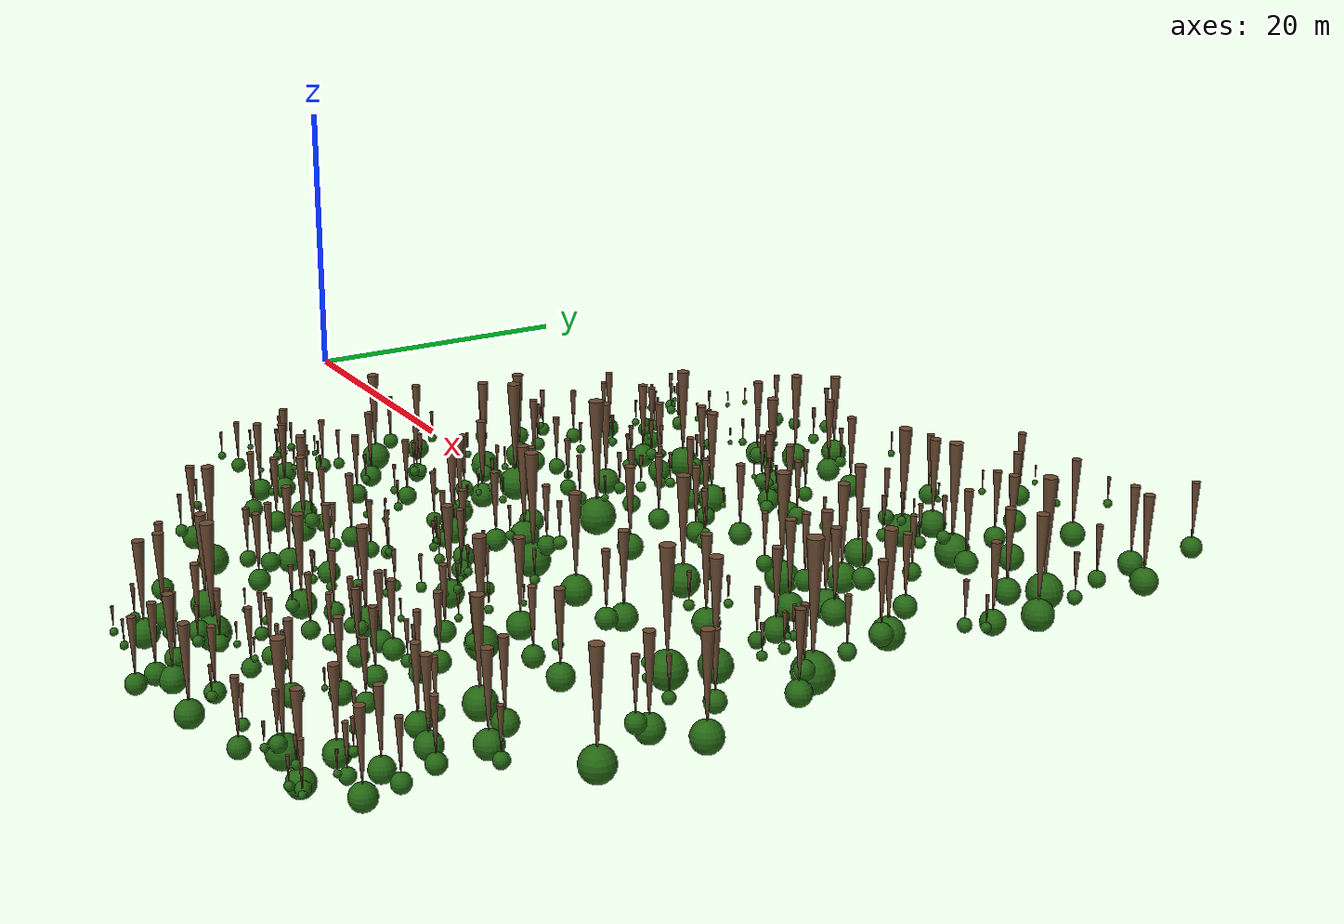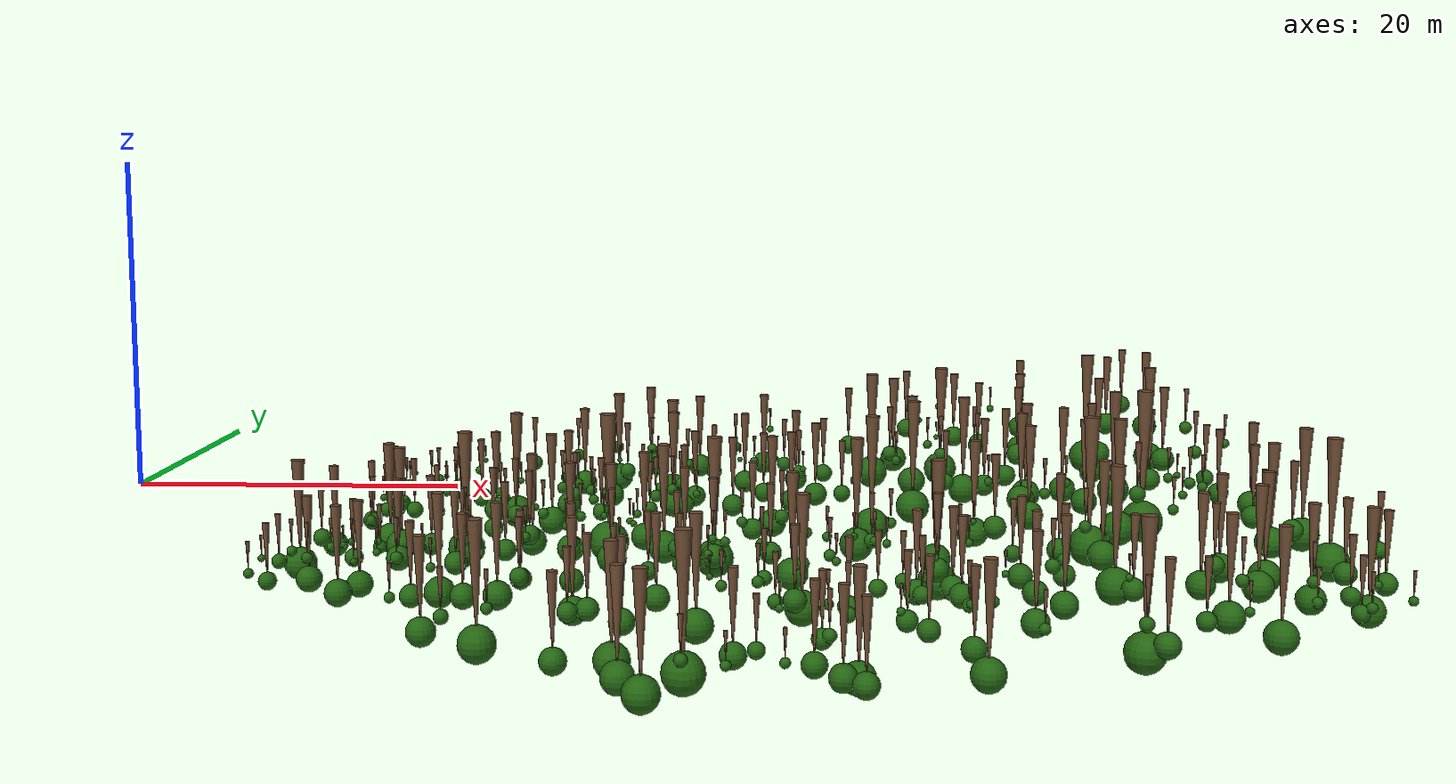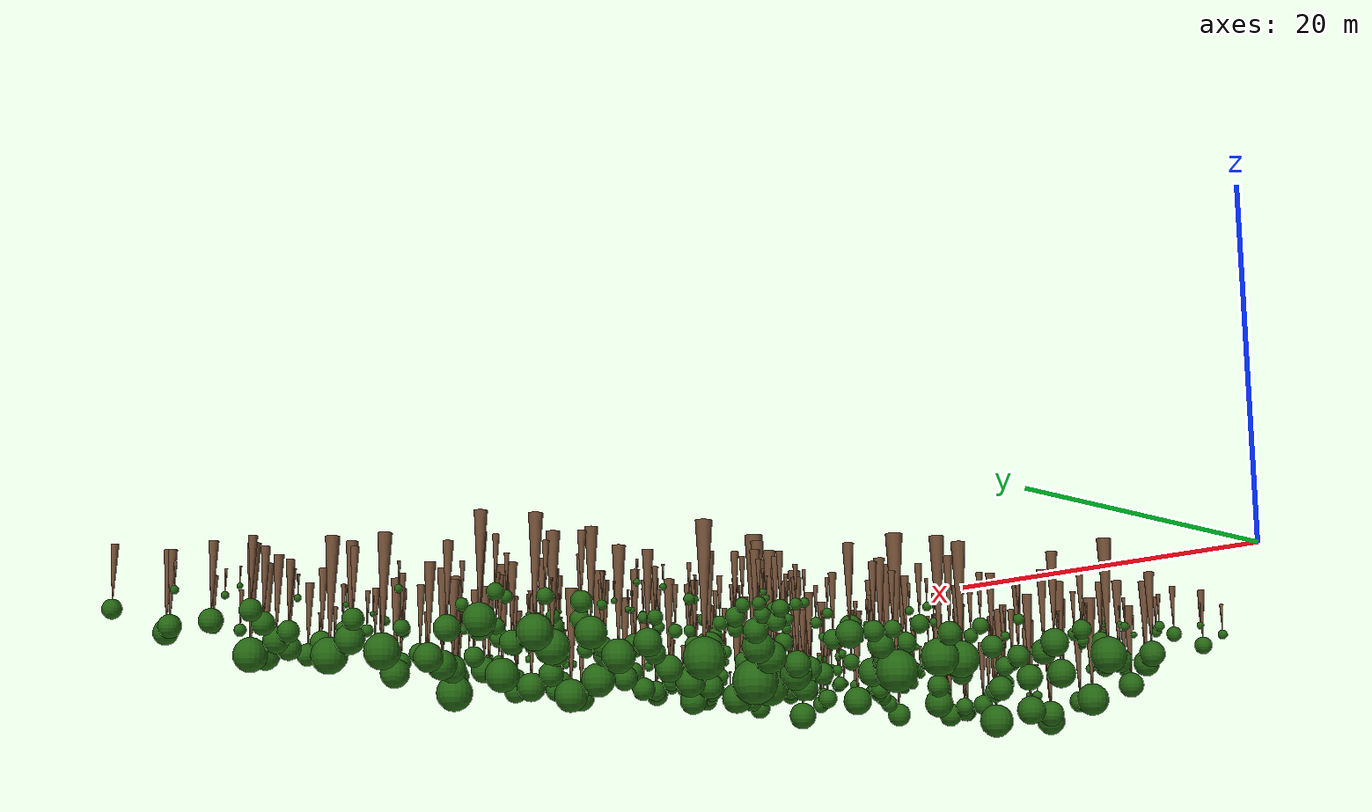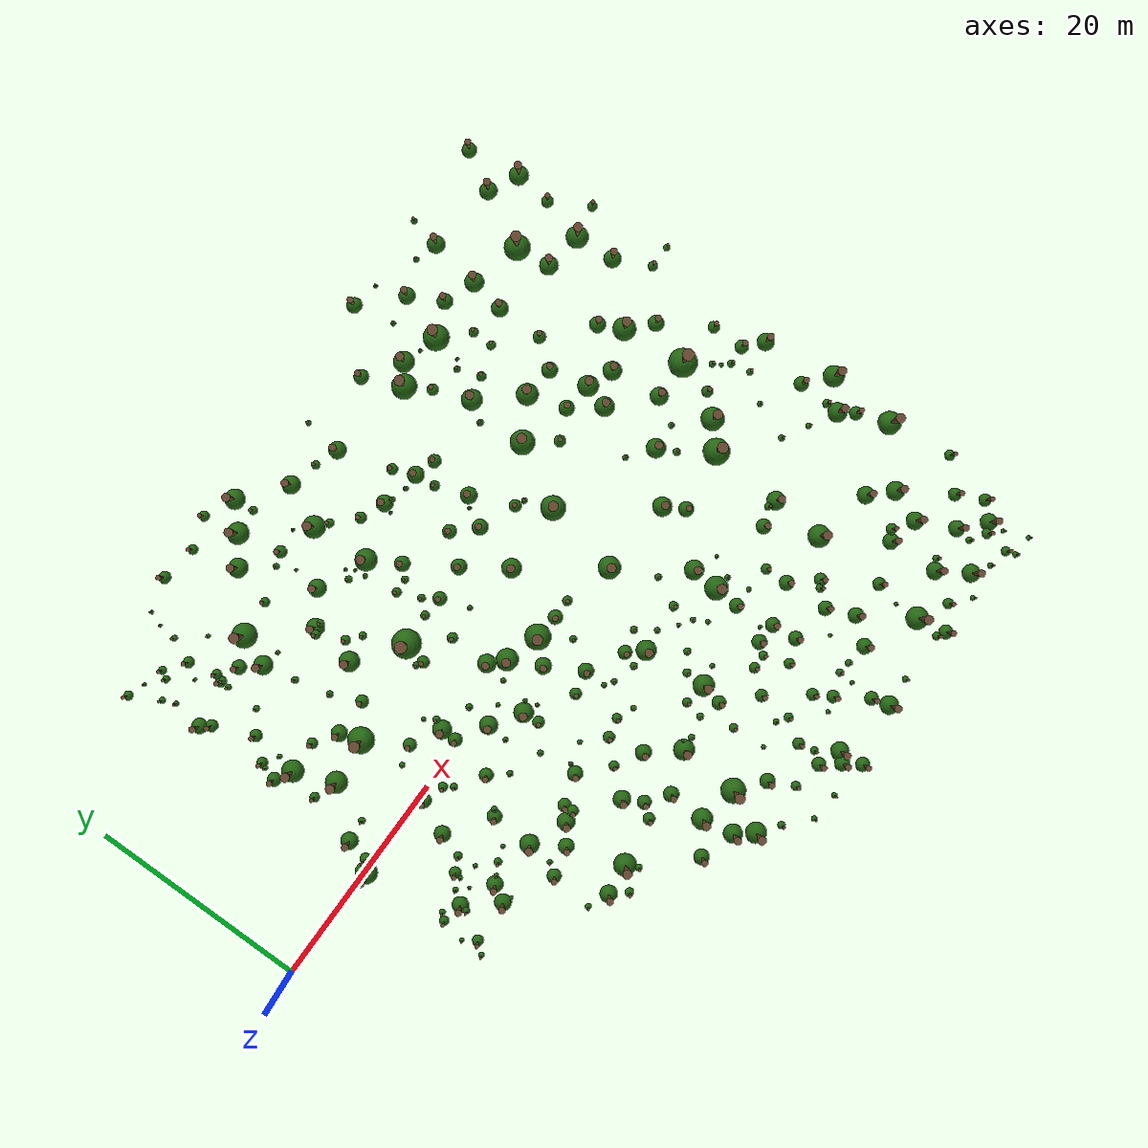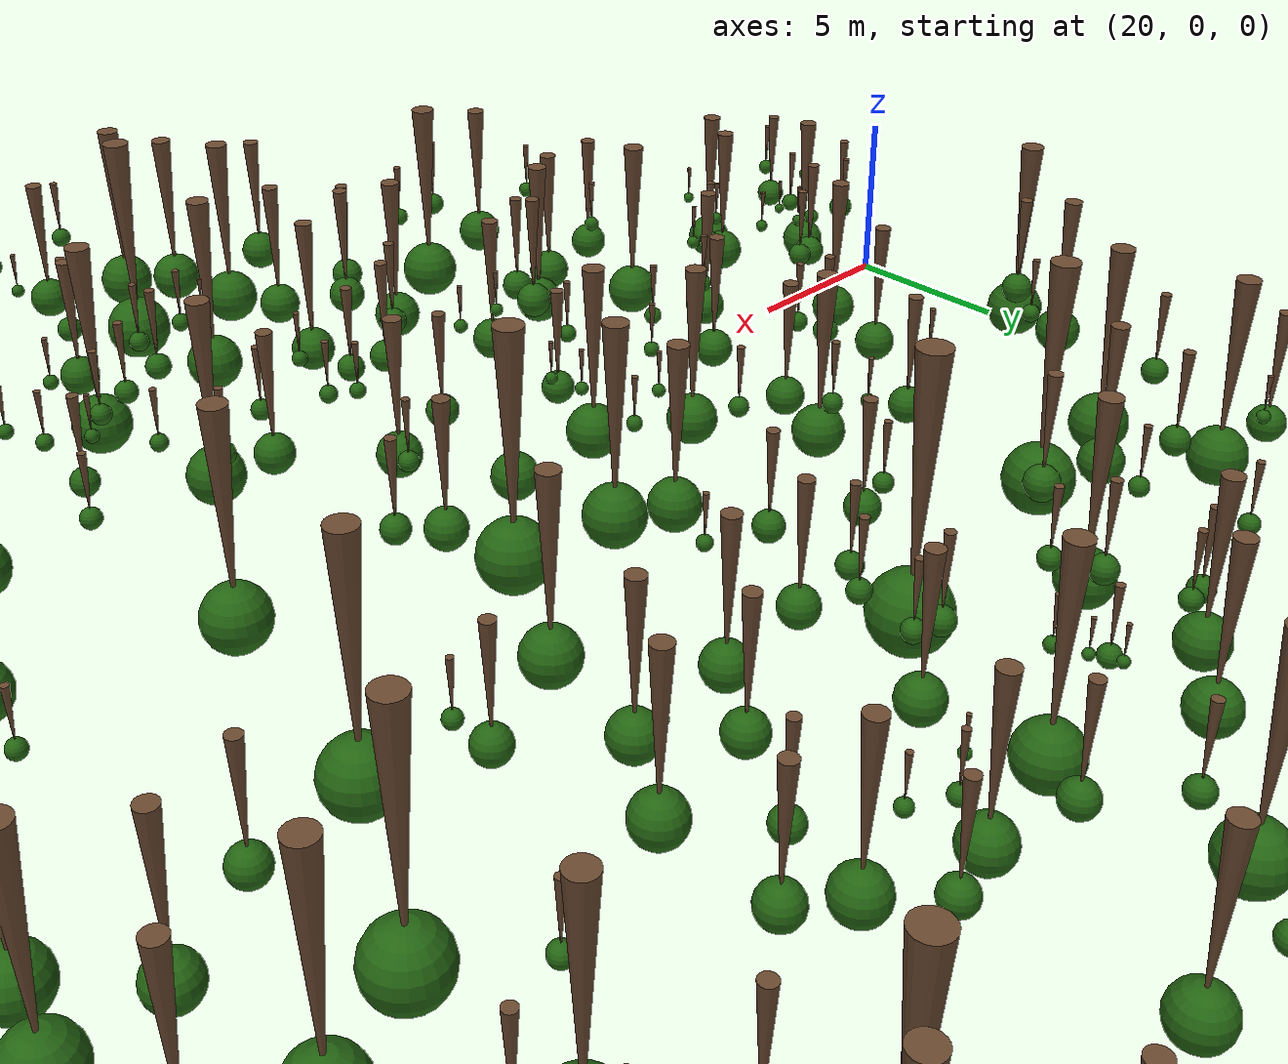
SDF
<?xml version="1.0" ?>
<!-- auto generated by generate_model_sdf.py -->
<sdf version="1.10">

<model name="lehrforst_trees">

<static>true</static>

  <link name='tree_0003'>
    <visual name='tree_0003_trunk'>
      <pose>28.569 8.946 -1.156 3.14159 0 0</pose>
      <geometry>
        <cone>
          <radius>0.546</radius>
          <length>8.736</length>
        </cone>
      </geometry>
      <material>
        <ambient>0.42 0.29 0.19 1</ambient>
        <diffuse>0.42 0.29 0.19 1</diffuse>
        <specular>0.42 0.29 0.19 1</specular>
      </material>
    </visual>
    <visual name='tree_0003_leaves'>
      <pose>28.569 8.946 -5.524 3.14159 0 0</pose>
      <geometry>
        <sphere>
          <radius>1.365</radius>
        </sphere>
      </geometry>
      <material>
        <ambient>0.14 0.40 0.07 1</ambient>
        <diffuse>0.14 0.40 0.07 1</diffuse>
        <specular>0.14 0.40 0.07 1</specular>
      </material>
    </visual>
    <collision name='tree_0003_collision'>
      <pose>28.569 8.946 -1.156 3.14159 0 0</pose>
      <geometry>
        <cone>
          <radius>0.546</radius>
          <length>8.736</length>
        </cone>
      </geometry>
    </collision>
  </link>

  <link name='tree_0008'>
    <visual name='tree_0008_trunk'>
      <pose>63.142 3.854 1.507 3.14159 0 0</pose>
      <geometry>
        <cone>
          <radius>0.524</radius>
          <length>8.384</length>
        </cone>
      </geometry>
      <material>
        <ambient>0.42 0.29 0.19 1</ambient>
        <diffuse>0.42 0.29 0.19 1</diffuse>
        <specular>0.42 0.29 0.19 1</specular>
      </material>
    </visual>
    <visual name='tree_0008_leaves'>
      <pose>63.142 3.854 -2.6850000000000005 3.14159 0 0</pose>
      <geometry>
        <sphere>
          <radius>1.310</radius>
        </sphere>
      </geometry>
      <material>
        <ambient>0.14 0.40 0.07 1</ambient>
        <diffuse>0.14 0.40 0.07 1</diffuse>
        <specular>0.14 0.40 0.07 1</specular>
      </material>
    </visual>
    <collision name='tree_0008_collision'>
      <pose>63.142 3.854 1.507 3.14159 0 0</pose>
      <geometry>
        <cone>
          <radius>0.524</radius>
          <length>8.384</length>
        </cone>
      </geometry>
    </collision>
  </link>

  <link name='tree_0011'>
    <visual name='tree_0011_trunk'>
      <pose>19.209 7.13 -1.709 3.14159 0 0</pose>
      <geometry>
        <cone>
          <radius>0.492</radius>
          <length>7.872</length>
        </cone>
      </geometry>
      <material>
        <ambient>0.42 0.29 0.19 1</ambient>
        <diffuse>0.42 0.29 0.19 1</diffuse>
        <specular>0.42 0.29 0.19 1</specular>
      </material>
    </visual>
    <visual name='tree_0011_leaves'>
      <pose>19.209 7.13 -5.645 3.14159 0 0</pose>
      <geometry>
        <sphere>
          <radius>1.230</radius>
        </sphere>
      </geometry>
      <material>
        <ambient>0.14 0.40 0.07 1</ambient>
        <diffuse>0.14 0.40 0.07 1</diffuse>
        <specular>0.14 0.40 0.07 1</specular>
      </material>
    </visual>
    <collision name='tree_0011_collision'>
      <pose>19.209 7.13 -1.709 3.14159 0 0</pose>
      <geometry>
        <cone>
          <radius>0.492</radius>
          <length>7.872</length>
        </cone>
      </geometry>
    </collision>
  </link>

  <link name='tree_0013'>
    <visual name='tree_0013_trunk'>
      <pose>58.567 -3.165 1.219 3.14159 0 0</pose>
      <geometry>
        <cone>
          <radius>0.486</radius>
          <length>7.776</length>
        </cone>
      </geometry>
      <material>
        <ambient>0.42 0.29 0.19 1</ambient>
        <diffuse>0.42 0.29 0.19 1</diffuse>
        <specular>0.42 0.29 0.19 1</specular>
      </material>
    </visual>
    <visual name='tree_0013_leaves'>
      <pose>58.567 -3.165 -2.6689999999999996 3.14159 0 0</pose>
      <geometry>
        <sphere>
          <radius>1.215</radius>
        </sphere>
      </geometry>
      <material>
        <ambient>0.14 0.40 0.07 1</ambient>
        <diffuse>0.14 0.40 0.07 1</diffuse>
        <specular>0.14 0.40 0.07 1</specular>
      </material>
    </visual>
    <collision name='tree_0013_collision'>
      <pose>58.567 -3.165 1.219 3.14159 0 0</pose>
      <geometry>
        <cone>
          <radius>0.486</radius>
          <length>7.776</length>
        </cone>
      </geometry>
    </collision>
  </link>

  <link name='tree_0015'>
    <visual name='tree_0015_trunk'>
      <pose>36.035 -0.141 -0.581 3.14159 0 0</pose>
      <geometry>
        <cone>
          <radius>0.478</radius>
          <length>7.648</length>
        </cone>
      </geometry>
      <material>
        <ambient>0.42 0.29 0.19 1</ambient>
        <diffuse>0.42 0.29 0.19 1</diffuse>
        <specular>0.42 0.29 0.19 1</specular>
      </material>
    </visual>
    <visual name='tree_0015_leaves'>
      <pose>36.035 -0.141 -4.404999999999999 3.14159 0 0</pose>
      <geometry>
        <sphere>
          <radius>1.195</radius>
        </sphere>
      </geometry>
      <material>
        <ambient>0.14 0.40 0.07 1</ambient>
        <diffuse>0.14 0.40 0.07 1</diffuse>
        <specular>0.14 0.40 0.07 1</specular>
      </material>
    </visual>
    <collision name='tree_0015_collision'>
      <pose>36.035 -0.141 -0.581 3.14159 0 0</pose>
      <geometry>
        <cone>
          <radius>0.478</radius>
          <length>7.648</length>
        </cone>
      </geometry>
    </collision>
  </link>

  <link name='tree_0019'>
    <visual name='tree_0019_trunk'>
      <pose>52.082 22.715 0.86 3.14159 0 0</pose>
      <geometry>
        <cone>
          <radius>0.472</radius>
          <length>7.552</length>
        </cone>
      </geometry>
      <material>
        <ambient>0.42 0.29 0.19 1</ambient>
        <diffuse>0.42 0.29 0.19 1</diffuse>
        <specular>0.42 0.29 0.19 1</specular>
      </material>
    </visual>
    <visual name='tree_0019_leaves'>
      <pose>52.082 22.715 -2.916 3.14159 0 0</pose>
      <geometry>
        <sphere>
          <radius>1.180</radius>
        </sphere>
      </geometry>
      <material>
        <ambient>0.14 0.40 0.07 1</ambient>
        <diffuse>0.14 0.40 0.07 1</diffuse>
        <specular>0.14 0.40 0.07 1</specular>
      </material>
    </visual>
    <collision name='tree_0019_collision'>
      <pose>52.082 22.715 0.86 3.14159 0 0</pose>
      <geometry>
        <cone>
          <radius>0.472</radius>
          <length>7.552</length>
        </cone>
      </geometry>
    </collision>
  </link>

  <link name='tree_0021'>
    <visual name='tree_0021_trunk'>
      <pose>62.606 21.554 2.054 3.14159 0 0</pose>
      <geometry>
        <cone>
          <radius>0.468</radius>
          <length>7.488</length>
        </cone>
      </geometry>
      <material>
        <ambient>0.42 0.29 0.19 1</ambient>
        <diffuse>0.42 0.29 0.19 1</diffuse>
        <specular>0.42 0.29 0.19 1</specular>
      </material>
    </visual>
    <visual name='tree_0021_leaves'>
      <pose>62.606 21.554 -1.6900000000000004 3.14159 0 0</pose>
      <geometry>
        <sphere>
          <radius>1.170</radius>
        </sphere>
      </geometry>
      <material>
        <ambient>0.14 0.40 0.07 1</ambient>
        <diffuse>0.14 0.40 0.07 1</diffuse>
        <specular>0.14 0.40 0.07 1</specular>
      </material>
    </visual>
    <collision name='tree_0021_collision'>
      <pose>62.606 21.554 2.054 3.14159 0 0</pose>
      <geometry>
        <cone>
          <radius>0.468</radius>
          <length>7.488</length>
        </cone>
      </geometry>
    </collision>
  </link>

  <link name='tree_0026'>
    <visual name='tree_0026_trunk'>
      <pose>20.56 21.103 -2.404 3.14159 0 0</pose>
      <geometry>
        <cone>
          <radius>0.464</radius>
          <length>7.424</length>
        </cone>
      </geometry>
      <material>
        <ambient>0.42 0.29 0.19 1</ambient>
        <diffuse>0.42 0.29 0.19 1</diffuse>
        <specular>0.42 0.29 0.19 1</specular>
      </material>
    </visual>
    <visual name='tree_0026_leaves'>
      <pose>20.56 21.103 -6.116 3.14159 0 0</pose>
      <geometry>
        <sphere>
          <radius>1.160</radius>
        </sphere>
      </geometry>
      <material>
        <ambient>0.14 0.40 0.07 1</ambient>
        <diffuse>0.14 0.40 0.07 1</diffuse>
        <specular>0.14 0.40 0.07 1</specular>
      </material>
    </visual>
    <collision name='tree_0026_collision'>
      <pose>20.56 21.103 -2.404 3.14159 0 0</pose>
      <geometry>
        <cone>
          <radius>0.464</radius>
          <length>7.424</length>
        </cone>
      </geometry>
    </collision>
  </link>

  <link name='tree_0034'>
    <visual name='tree_0034_trunk'>
      <pose>35.26 -22.294 -1.24 3.14159 0 0</pose>
      <geometry>
        <cone>
          <radius>0.460</radius>
          <length>7.360</length>
        </cone>
      </geometry>
      <material>
        <ambient>0.42 0.29 0.19 1</ambient>
        <diffuse>0.42 0.29 0.19 1</diffuse>
        <specular>0.42 0.29 0.19 1</specular>
      </material>
    </visual>
    <visual name='tree_0034_leaves'>
      <pose>35.26 -22.294 -4.92 3.14159 0 0</pose>
      <geometry>
        <sphere>
          <radius>1.150</radius>
        </sphere>
      </geometry>
      <material>
        <ambient>0.14 0.40 0.07 1</ambient>
        <diffuse>0.14 0.40 0.07 1</diffuse>
        <specular>0.14 0.40 0.07 1</specular>
      </material>
    </visual>
    <collision name='tree_0034_collision'>
      <pose>35.26 -22.294 -1.24 3.14159 0 0</pose>
      <geometry>
        <cone>
          <radius>0.460</radius>
          <length>7.360</length>
        </cone>
      </geometry>
    </collision>
  </link>

  <link name='tree_0035'>
    <visual name='tree_0035_trunk'>
      <pose>46.962 22.473 0.51 3.14159 0 0</pose>
      <geometry>
        <cone>
          <radius>0.458</radius>
          <length>7.328</length>
        </cone>
      </geometry>
      <material>
        <ambient>0.42 0.29 0.19 1</ambient>
        <diffuse>0.42 0.29 0.19 1</diffuse>
        <specular>0.42 0.29 0.19 1</specular>
      </material>
    </visual>
    <visual name='tree_0035_leaves'>
      <pose>46.962 22.473 -3.154 3.14159 0 0</pose>
      <geometry>
        <sphere>
          <radius>1.145</radius>
        </sphere>
      </geometry>
      <material>
        <ambient>0.14 0.40 0.07 1</ambient>
        <diffuse>0.14 0.40 0.07 1</diffuse>
        <specular>0.14 0.40 0.07 1</specular>
      </material>
    </visual>
    <collision name='tree_0035_collision'>
      <pose>46.962 22.473 0.51 3.14159 0 0</pose>
      <geometry>
        <cone>
          <radius>0.458</radius>
          <length>7.328</length>
        </cone>
      </geometry>
    </collision>
  </link>

  <link name='tree_0040'>
    <visual name='tree_0040_trunk'>
      <pose>49.152 11.139 0.233 3.14159 0 0</pose>
      <geometry>
        <cone>
          <radius>0.452</radius>
          <length>7.232</length>
        </cone>
      </geometry>
      <material>
        <ambient>0.42 0.29 0.19 1</ambient>
        <diffuse>0.42 0.29 0.19 1</diffuse>
        <specular>0.42 0.29 0.19 1</specular>
      </material>
    </visual>
    <visual name='tree_0040_leaves'>
      <pose>49.152 11.139 -3.383 3.14159 0 0</pose>
      <geometry>
        <sphere>
          <radius>1.130</radius>
        </sphere>
      </geometry>
      <material>
        <ambient>0.14 0.40 0.07 1</ambient>
        <diffuse>0.14 0.40 0.07 1</diffuse>
        <specular>0.14 0.40 0.07 1</specular>
      </material>
    </visual>
    <collision name='tree_0040_collision'>
      <pose>49.152 11.139 0.233 3.14159 0 0</pose>
      <geometry>
        <cone>
          <radius>0.452</radius>
          <length>7.232</length>
        </cone>
      </geometry>
    </collision>
  </link>

  <link name='tree_0041'>
    <visual name='tree_0041_trunk'>
      <pose>46.069 5.531 0.116 3.14159 0 0</pose>
      <geometry>
        <cone>
          <radius>0.452</radius>
          <length>7.232</length>
        </cone>
      </geometry>
      <material>
        <ambient>0.42 0.29 0.19 1</ambient>
        <diffuse>0.42 0.29 0.19 1</diffuse>
        <specular>0.42 0.29 0.19 1</specular>
      </material>
    </visual>
    <visual name='tree_0041_leaves'>
      <pose>46.069 5.531 -3.5 3.14159 0 0</pose>
      <geometry>
        <sphere>
          <radius>1.130</radius>
        </sphere>
      </geometry>
      <material>
        <ambient>0.14 0.40 0.07 1</ambient>
        <diffuse>0.14 0.40 0.07 1</diffuse>
        <specular>0.14 0.40 0.07 1</specular>
      </material>
    </visual>
    <collision name='tree_0041_collision'>
      <pose>46.069 5.531 0.116 3.14159 0 0</pose>
      <geometry>
        <cone>
          <radius>0.452</radius>
          <length>7.232</length>
        </cone>
      </geometry>
    </collision>
  </link>

  <link name='tree_0060'>
    <visual name='tree_0060_trunk'>
      <pose>48.872 -10.303 0.335 3.14159 0 0</pose>
      <geometry>
        <cone>
          <radius>0.432</radius>
          <length>6.912</length>
        </cone>
      </geometry>
      <material>
        <ambient>0.42 0.29 0.19 1</ambient>
        <diffuse>0.42 0.29 0.19 1</diffuse>
        <specular>0.42 0.29 0.19 1</specular>
      </material>
    </visual>
    <visual name='tree_0060_leaves'>
      <pose>48.872 -10.303 -3.121 3.14159 0 0</pose>
      <geometry>
        <sphere>
          <radius>1.080</radius>
        </sphere>
      </geometry>
      <material>
        <ambient>0.14 0.40 0.07 1</ambient>
        <diffuse>0.14 0.40 0.07 1</diffuse>
        <specular>0.14 0.40 0.07 1</specular>
      </material>
    </visual>
    <collision name='tree_0060_collision'>
      <pose>48.872 -10.303 0.335 3.14159 0 0</pose>
      <geometry>
        <cone>
          <radius>0.432</radius>
          <length>6.912</length>
        </cone>
      </geometry>
    </collision>
  </link>

  <link name='tree_0071'>
    <visual name='tree_0071_trunk'>
      <pose>60.635 -1.175 1.326 3.14159 0 0</pose>
      <geometry>
        <cone>
          <radius>0.422</radius>
          <length>6.752</length>
        </cone>
      </geometry>
      <material>
        <ambient>0.42 0.29 0.19 1</ambient>
        <diffuse>0.42 0.29 0.19 1</diffuse>
        <specular>0.42 0.29 0.19 1</specular>
      </material>
    </visual>
    <visual name='tree_0071_leaves'>
      <pose>60.635 -1.175 -2.05 3.14159 0 0</pose>
      <geometry>
        <sphere>
          <radius>1.055</radius>
        </sphere>
      </geometry>
      <material>
        <ambient>0.14 0.40 0.07 1</ambient>
        <diffuse>0.14 0.40 0.07 1</diffuse>
        <specular>0.14 0.40 0.07 1</specular>
      </material>
    </visual>
    <collision name='tree_0071_collision'>
      <pose>60.635 -1.175 1.326 3.14159 0 0</pose>
      <geometry>
        <cone>
          <radius>0.422</radius>
          <length>6.752</length>
        </cone>
      </geometry>
    </collision>
  </link>

  <link name='tree_0076'>
    <visual name='tree_0076_trunk'>
      <pose>69.408 -13.844 2.384 3.14159 0 0</pose>
      <geometry>
        <cone>
          <radius>0.420</radius>
          <length>6.720</length>
        </cone>
      </geometry>
      <material>
        <ambient>0.42 0.29 0.19 1</ambient>
        <diffuse>0.42 0.29 0.19 1</diffuse>
        <specular>0.42 0.29 0.19 1</specular>
      </material>
    </visual>
    <visual name='tree_0076_leaves'>
      <pose>69.408 -13.844 -0.976 3.14159 0 0</pose>
      <geometry>
        <sphere>
          <radius>1.050</radius>
        </sphere>
      </geometry>
      <material>
        <ambient>0.14 0.40 0.07 1</ambient>
        <diffuse>0.14 0.40 0.07 1</diffuse>
        <specular>0.14 0.40 0.07 1</specular>
      </material>
    </visual>
    <collision name='tree_0076_collision'>
      <pose>69.408 -13.844 2.384 3.14159 0 0</pose>
      <geometry>
        <cone>
          <radius>0.420</radius>
          <length>6.720</length>
        </cone>
      </geometry>
    </collision>
  </link>

  <link name='tree_0080'>
    <visual name='tree_0080_trunk'>
      <pose>24.254 -18.389 -1.363 3.14159 0 0</pose>
      <geometry>
        <cone>
          <radius>0.418</radius>
          <length>6.688</length>
        </cone>
      </geometry>
      <material>
        <ambient>0.42 0.29 0.19 1</ambient>
        <diffuse>0.42 0.29 0.19 1</diffuse>
        <specular>0.42 0.29 0.19 1</specular>
      </material>
    </visual>
    <visual name='tree_0080_leaves'>
      <pose>24.254 -18.389 -4.707 3.14159 0 0</pose>
      <geometry>
        <sphere>
          <radius>1.045</radius>
        </sphere>
      </geometry>
      <material>
        <ambient>0.14 0.40 0.07 1</ambient>
        <diffuse>0.14 0.40 0.07 1</diffuse>
        <specular>0.14 0.40 0.07 1</specular>
      </material>
    </visual>
    <collision name='tree_0080_collision'>
      <pose>24.254 -18.389 -1.363 3.14159 0 0</pose>
      <geometry>
        <cone>
          <radius>0.418</radius>
          <length>6.688</length>
        </cone>
      </geometry>
    </collision>
  </link>

  <link name='tree_0083'>
    <visual name='tree_0083_trunk'>
      <pose>62.414 9.743 1.462 3.14159 0 0</pose>
      <geometry>
        <cone>
          <radius>0.416</radius>
          <length>6.656</length>
        </cone>
      </geometry>
      <material>
        <ambient>0.42 0.29 0.19 1</ambient>
        <diffuse>0.42 0.29 0.19 1</diffuse>
        <specular>0.42 0.29 0.19 1</specular>
      </material>
    </visual>
    <visual name='tree_0083_leaves'>
      <pose>62.414 9.743 -1.8659999999999999 3.14159 0 0</pose>
      <geometry>
        <sphere>
          <radius>1.040</radius>
        </sphere>
      </geometry>
      <material>
        <ambient>0.14 0.40 0.07 1</ambient>
        <diffuse>0.14 0.40 0.07 1</diffuse>
        <specular>0.14 0.40 0.07 1</specular>
      </material>
    </visual>
    <collision name='tree_0083_collision'>
      <pose>62.414 9.743 1.462 3.14159 0 0</pose>
      <geometry>
        <cone>
          <radius>0.416</radius>
          <length>6.656</length>
        </cone>
      </geometry>
    </collision>
  </link>

  <link name='tree_0085'>
    <visual name='tree_0085_trunk'>
      <pose>32.181 21.663 -1.035 3.14159 0 0</pose>
      <geometry>
        <cone>
          <radius>0.414</radius>
          <length>6.624</length>
        </cone>
      </geometry>
      <material>
        <ambient>0.42 0.29 0.19 1</ambient>
        <diffuse>0.42 0.29 0.19 1</diffuse>
        <specular>0.42 0.29 0.19 1</specular>
      </material>
    </visual>
    <visual name='tree_0085_leaves'>
      <pose>32.181 21.663 -4.3469999999999995 3.14159 0 0</pose>
      <geometry>
        <sphere>
          <radius>1.035</radius>
        </sphere>
      </geometry>
      <material>
        <ambient>0.14 0.40 0.07 1</ambient>
        <diffuse>0.14 0.40 0.07 1</diffuse>
        <specular>0.14 0.40 0.07 1</specular>
      </material>
    </visual>
    <collision name='tree_0085_collision'>
      <pose>32.181 21.663 -1.035 3.14159 0 0</pose>
      <geometry>
        <cone>
          <radius>0.414</radius>
          <length>6.624</length>
        </cone>
      </geometry>
    </collision>
  </link>

  <link name='tree_0088'>
    <visual name='tree_0088_trunk'>
      <pose>13.372 10.431 -2.465 3.14159 0 0</pose>
      <geometry>
        <cone>
          <radius>0.412</radius>
          <length>6.592</length>
        </cone>
      </geometry>
      <material>
        <ambient>0.42 0.29 0.19 1</ambient>
        <diffuse>0.42 0.29 0.19 1</diffuse>
        <specular>0.42 0.29 0.19 1</specular>
      </material>
    </visual>
    <visual name='tree_0088_leaves'>
      <pose>13.372 10.431 -5.760999999999999 3.14159 0 0</pose>
      <geometry>
        <sphere>
          <radius>1.030</radius>
        </sphere>
      </geometry>
      <material>
        <ambient>0.14 0.40 0.07 1</ambient>
        <diffuse>0.14 0.40 0.07 1</diffuse>
        <specular>0.14 0.40 0.07 1</specular>
      </material>
    </visual>
    <collision name='tree_0088_collision'>
      <pose>13.372 10.431 -2.465 3.14159 0 0</pose>
      <geometry>
        <cone>
          <radius>0.412</radius>
          <length>6.592</length>
        </cone>
      </geometry>
    </collision>
  </link>

  <link name='tree_0092'>
    <visual name='tree_0092_trunk'>
      <pose>10.021 -0.234 -1.669 3.14159 0 0</pose>
      <geometry>
        <cone>
          <radius>0.412</radius>
          <length>6.592</length>
        </cone>
      </geometry>
      <material>
        <ambient>0.42 0.29 0.19 1</ambient>
        <diffuse>0.42 0.29 0.19 1</diffuse>
        <specular>0.42 0.29 0.19 1</specular>
      </material>
    </visual>
    <visual name='tree_0092_leaves'>
      <pose>10.021 -0.234 -4.965 3.14159 0 0</pose>
      <geometry>
        <sphere>
          <radius>1.030</radius>
        </sphere>
      </geometry>
      <material>
        <ambient>0.14 0.40 0.07 1</ambient>
        <diffuse>0.14 0.40 0.07 1</diffuse>
        <specular>0.14 0.40 0.07 1</specular>
      </material>
    </visual>
    <collision name='tree_0092_collision'>
      <pose>10.021 -0.234 -1.669 3.14159 0 0</pose>
      <geometry>
        <cone>
          <radius>0.412</radius>
          <length>6.592</length>
        </cone>
      </geometry>
    </collision>
  </link>

  <link name='tree_0093'>
    <visual name='tree_0093_trunk'>
      <pose>14.92 6.676 -2.076 3.14159 0 0</pose>
      <geometry>
        <cone>
          <radius>0.412</radius>
          <length>6.592</length>
        </cone>
      </geometry>
      <material>
        <ambient>0.42 0.29 0.19 1</ambient>
        <diffuse>0.42 0.29 0.19 1</diffuse>
        <specular>0.42 0.29 0.19 1</specular>
      </material>
    </visual>
    <visual name='tree_0093_leaves'>
      <pose>14.92 6.676 -5.372 3.14159 0 0</pose>
      <geometry>
        <sphere>
          <radius>1.030</radius>
        </sphere>
      </geometry>
      <material>
        <ambient>0.14 0.40 0.07 1</ambient>
        <diffuse>0.14 0.40 0.07 1</diffuse>
        <specular>0.14 0.40 0.07 1</specular>
      </material>
    </visual>
    <collision name='tree_0093_collision'>
      <pose>14.92 6.676 -2.076 3.14159 0 0</pose>
      <geometry>
        <cone>
          <radius>0.412</radius>
          <length>6.592</length>
        </cone>
      </geometry>
    </collision>
  </link>

  <link name='tree_0094'>
    <visual name='tree_0094_trunk'>
      <pose>57.165 -26.08 0.838 3.14159 0 0</pose>
      <geometry>
        <cone>
          <radius>0.412</radius>
          <length>6.592</length>
        </cone>
      </geometry>
      <material>
        <ambient>0.42 0.29 0.19 1</ambient>
        <diffuse>0.42 0.29 0.19 1</diffuse>
        <specular>0.42 0.29 0.19 1</specular>
      </material>
    </visual>
    <visual name='tree_0094_leaves'>
      <pose>57.165 -26.08 -2.4579999999999997 3.14159 0 0</pose>
      <geometry>
        <sphere>
          <radius>1.030</radius>
        </sphere>
      </geometry>
      <material>
        <ambient>0.14 0.40 0.07 1</ambient>
        <diffuse>0.14 0.40 0.07 1</diffuse>
        <specular>0.14 0.40 0.07 1</specular>
      </material>
    </visual>
    <collision name='tree_0094_collision'>
      <pose>57.165 -26.08 0.838 3.14159 0 0</pose>
      <geometry>
        <cone>
          <radius>0.412</radius>
          <length>6.592</length>
        </cone>
      </geometry>
    </collision>
  </link>

  <link name='tree_0095'>
    <visual name='tree_0095_trunk'>
      <pose>44.75 -1.61 0.196 3.14159 0 0</pose>
      <geometry>
        <cone>
          <radius>0.412</radius>
          <length>6.592</length>
        </cone>
      </geometry>
      <material>
        <ambient>0.42 0.29 0.19 1</ambient>
        <diffuse>0.42 0.29 0.19 1</diffuse>
        <specular>0.42 0.29 0.19 1</specular>
      </material>
    </visual>
    <visual name='tree_0095_leaves'>
      <pose>44.75 -1.61 -3.0999999999999996 3.14159 0 0</pose>
      <geometry>
        <sphere>
          <radius>1.030</radius>
        </sphere>
      </geometry>
      <material>
        <ambient>0.14 0.40 0.07 1</ambient>
        <diffuse>0.14 0.40 0.07 1</diffuse>
        <specular>0.14 0.40 0.07 1</specular>
      </material>
    </visual>
    <collision name='tree_0095_collision'>
      <pose>44.75 -1.61 0.196 3.14159 0 0</pose>
      <geometry>
        <cone>
          <radius>0.412</radius>
          <length>6.592</length>
        </cone>
      </geometry>
    </collision>
  </link>

  <link name='tree_0099'>
    <visual name='tree_0099_trunk'>
      <pose>32.546 16.219 -1.05 3.14159 0 0</pose>
      <geometry>
        <cone>
          <radius>0.408</radius>
          <length>6.528</length>
        </cone>
      </geometry>
      <material>
        <ambient>0.42 0.29 0.19 1</ambient>
        <diffuse>0.42 0.29 0.19 1</diffuse>
        <specular>0.42 0.29 0.19 1</specular>
      </material>
    </visual>
    <visual name='tree_0099_leaves'>
      <pose>32.546 16.219 -4.314 3.14159 0 0</pose>
      <geometry>
        <sphere>
          <radius>1.020</radius>
        </sphere>
      </geometry>
      <material>
        <ambient>0.14 0.40 0.07 1</ambient>
        <diffuse>0.14 0.40 0.07 1</diffuse>
        <specular>0.14 0.40 0.07 1</specular>
      </material>
    </visual>
    <collision name='tree_0099_collision'>
      <pose>32.546 16.219 -1.05 3.14159 0 0</pose>
      <geometry>
        <cone>
          <radius>0.408</radius>
          <length>6.528</length>
        </cone>
      </geometry>
    </collision>
  </link>

  <link name='tree_0100'>
    <visual name='tree_0100_trunk'>
      <pose>32.823 0.866 -0.689 3.14159 0 0</pose>
      <geometry>
        <cone>
          <radius>0.408</radius>
          <length>6.528</length>
        </cone>
      </geometry>
      <material>
        <ambient>0.42 0.29 0.19 1</ambient>
        <diffuse>0.42 0.29 0.19 1</diffuse>
        <specular>0.42 0.29 0.19 1</specular>
      </material>
    </visual>
    <visual name='tree_0100_leaves'>
      <pose>32.823 0.866 -3.953 3.14159 0 0</pose>
      <geometry>
        <sphere>
          <radius>1.020</radius>
        </sphere>
      </geometry>
      <material>
        <ambient>0.14 0.40 0.07 1</ambient>
        <diffuse>0.14 0.40 0.07 1</diffuse>
        <specular>0.14 0.40 0.07 1</specular>
      </material>
    </visual>
    <collision name='tree_0100_collision'>
      <pose>32.823 0.866 -0.689 3.14159 0 0</pose>
      <geometry>
        <cone>
          <radius>0.408</radius>
          <length>6.528</length>
        </cone>
      </geometry>
    </collision>
  </link>

  <link name='tree_0104'>
    <visual name='tree_0104_trunk'>
      <pose>57.872 -14.827 1.113 3.14159 0 0</pose>
      <geometry>
        <cone>
          <radius>0.408</radius>
          <length>6.528</length>
        </cone>
      </geometry>
      <material>
        <ambient>0.42 0.29 0.19 1</ambient>
        <diffuse>0.42 0.29 0.19 1</diffuse>
        <specular>0.42 0.29 0.19 1</specular>
      </material>
    </visual>
    <visual name='tree_0104_leaves'>
      <pose>57.872 -14.827 -2.151 3.14159 0 0</pose>
      <geometry>
        <sphere>
          <radius>1.020</radius>
        </sphere>
      </geometry>
      <material>
        <ambient>0.14 0.40 0.07 1</ambient>
        <diffuse>0.14 0.40 0.07 1</diffuse>
        <specular>0.14 0.40 0.07 1</specular>
      </material>
    </visual>
    <collision name='tree_0104_collision'>
      <pose>57.872 -14.827 1.113 3.14159 0 0</pose>
      <geometry>
        <cone>
          <radius>0.408</radius>
          <length>6.528</length>
        </cone>
      </geometry>
    </collision>
  </link>

  <link name='tree_0107'>
    <visual name='tree_0107_trunk'>
      <pose>27.715 26.8 -1.274 3.14159 0 0</pose>
      <geometry>
        <cone>
          <radius>0.406</radius>
          <length>6.496</length>
        </cone>
      </geometry>
      <material>
        <ambient>0.42 0.29 0.19 1</ambient>
        <diffuse>0.42 0.29 0.19 1</diffuse>
        <specular>0.42 0.29 0.19 1</specular>
      </material>
    </visual>
    <visual name='tree_0107_leaves'>
      <pose>27.715 26.8 -4.522 3.14159 0 0</pose>
      <geometry>
        <sphere>
          <radius>1.015</radius>
        </sphere>
      </geometry>
      <material>
        <ambient>0.14 0.40 0.07 1</ambient>
        <diffuse>0.14 0.40 0.07 1</diffuse>
        <specular>0.14 0.40 0.07 1</specular>
      </material>
    </visual>
    <collision name='tree_0107_collision'>
      <pose>27.715 26.8 -1.274 3.14159 0 0</pose>
      <geometry>
        <cone>
          <radius>0.406</radius>
          <length>6.496</length>
        </cone>
      </geometry>
    </collision>
  </link>

  <link name='tree_0115'>
    <visual name='tree_0115_trunk'>
      <pose>66.375 17.798 2.19 3.14159 0 0</pose>
      <geometry>
        <cone>
          <radius>0.400</radius>
          <length>6.400</length>
        </cone>
      </geometry>
      <material>
        <ambient>0.42 0.29 0.19 1</ambient>
        <diffuse>0.42 0.29 0.19 1</diffuse>
        <specular>0.42 0.29 0.19 1</specular>
      </material>
    </visual>
    <visual name='tree_0115_leaves'>
      <pose>66.375 17.798 -1.0100000000000002 3.14159 0 0</pose>
      <geometry>
        <sphere>
          <radius>1.000</radius>
        </sphere>
      </geometry>
      <material>
        <ambient>0.14 0.40 0.07 1</ambient>
        <diffuse>0.14 0.40 0.07 1</diffuse>
        <specular>0.14 0.40 0.07 1</specular>
      </material>
    </visual>
    <collision name='tree_0115_collision'>
      <pose>66.375 17.798 2.19 3.14159 0 0</pose>
      <geometry>
        <cone>
          <radius>0.400</radius>
          <length>6.400</length>
        </cone>
      </geometry>
    </collision>
  </link>

  <link name='tree_0118'>
    <visual name='tree_0118_trunk'>
      <pose>52.779 13.26 0.645 3.14159 0 0</pose>
      <geometry>
        <cone>
          <radius>0.400</radius>
          <length>6.400</length>
        </cone>
      </geometry>
      <material>
        <ambient>0.42 0.29 0.19 1</ambient>
        <diffuse>0.42 0.29 0.19 1</diffuse>
        <specular>0.42 0.29 0.19 1</specular>
      </material>
    </visual>
    <visual name='tree_0118_leaves'>
      <pose>52.779 13.26 -2.555 3.14159 0 0</pose>
      <geometry>
        <sphere>
          <radius>1.000</radius>
        </sphere>
      </geometry>
      <material>
        <ambient>0.14 0.40 0.07 1</ambient>
        <diffuse>0.14 0.40 0.07 1</diffuse>
        <specular>0.14 0.40 0.07 1</specular>
      </material>
    </visual>
    <collision name='tree_0118_collision'>
      <pose>52.779 13.26 0.645 3.14159 0 0</pose>
      <geometry>
        <cone>
          <radius>0.400</radius>
          <length>6.400</length>
        </cone>
      </geometry>
    </collision>
  </link>

  <link name='tree_0128'>
    <visual name='tree_0128_trunk'>
      <pose>41.271 -14.518 -0.474 3.14159 0 0</pose>
      <geometry>
        <cone>
          <radius>0.394</radius>
          <length>6.304</length>
        </cone>
      </geometry>
      <material>
        <ambient>0.42 0.29 0.19 1</ambient>
        <diffuse>0.42 0.29 0.19 1</diffuse>
        <specular>0.42 0.29 0.19 1</specular>
      </material>
    </visual>
    <visual name='tree_0128_leaves'>
      <pose>41.271 -14.518 -3.6260000000000003 3.14159 0 0</pose>
      <geometry>
        <sphere>
          <radius>0.985</radius>
        </sphere>
      </geometry>
      <material>
        <ambient>0.14 0.40 0.07 1</ambient>
        <diffuse>0.14 0.40 0.07 1</diffuse>
        <specular>0.14 0.40 0.07 1</specular>
      </material>
    </visual>
    <collision name='tree_0128_collision'>
      <pose>41.271 -14.518 -0.474 3.14159 0 0</pose>
      <geometry>
        <cone>
          <radius>0.394</radius>
          <length>6.304</length>
        </cone>
      </geometry>
    </collision>
  </link>

  <link name='tree_0133'>
    <visual name='tree_0133_trunk'>
      <pose>33.437 -26.119 -1.676 3.14159 0 0</pose>
      <geometry>
        <cone>
          <radius>0.388</radius>
          <length>6.208</length>
        </cone>
      </geometry>
      <material>
        <ambient>0.42 0.29 0.19 1</ambient>
        <diffuse>0.42 0.29 0.19 1</diffuse>
        <specular>0.42 0.29 0.19 1</specular>
      </material>
    </visual>
    <visual name='tree_0133_leaves'>
      <pose>33.437 -26.119 -4.78 3.14159 0 0</pose>
      <geometry>
        <sphere>
          <radius>0.970</radius>
        </sphere>
      </geometry>
      <material>
        <ambient>0.14 0.40 0.07 1</ambient>
        <diffuse>0.14 0.40 0.07 1</diffuse>
        <specular>0.14 0.40 0.07 1</specular>
      </material>
    </visual>
    <collision name='tree_0133_collision'>
      <pose>33.437 -26.119 -1.676 3.14159 0 0</pose>
      <geometry>
        <cone>
          <radius>0.388</radius>
          <length>6.208</length>
        </cone>
      </geometry>
    </collision>
  </link>

  <link name='tree_0134'>
    <visual name='tree_0134_trunk'>
      <pose>31.612 -21.485 -1.44 3.14159 0 0</pose>
      <geometry>
        <cone>
          <radius>0.388</radius>
          <length>6.208</length>
        </cone>
      </geometry>
      <material>
        <ambient>0.42 0.29 0.19 1</ambient>
        <diffuse>0.42 0.29 0.19 1</diffuse>
        <specular>0.42 0.29 0.19 1</specular>
      </material>
    </visual>
    <visual name='tree_0134_leaves'>
      <pose>31.612 -21.485 -4.5440000000000005 3.14159 0 0</pose>
      <geometry>
        <sphere>
          <radius>0.970</radius>
        </sphere>
      </geometry>
      <material>
        <ambient>0.14 0.40 0.07 1</ambient>
        <diffuse>0.14 0.40 0.07 1</diffuse>
        <specular>0.14 0.40 0.07 1</specular>
      </material>
    </visual>
    <collision name='tree_0134_collision'>
      <pose>31.612 -21.485 -1.44 3.14159 0 0</pose>
      <geometry>
        <cone>
          <radius>0.388</radius>
          <length>6.208</length>
        </cone>
      </geometry>
    </collision>
  </link>

  <link name='tree_0142'>
    <visual name='tree_0142_trunk'>
      <pose>69.806 -7.501 2.163 3.14159 0 0</pose>
      <geometry>
        <cone>
          <radius>0.384</radius>
          <length>6.144</length>
        </cone>
      </geometry>
      <material>
        <ambient>0.42 0.29 0.19 1</ambient>
        <diffuse>0.42 0.29 0.19 1</diffuse>
        <specular>0.42 0.29 0.19 1</specular>
      </material>
    </visual>
    <visual name='tree_0142_leaves'>
      <pose>69.806 -7.501 -0.9090000000000003 3.14159 0 0</pose>
      <geometry>
        <sphere>
          <radius>0.960</radius>
        </sphere>
      </geometry>
      <material>
        <ambient>0.14 0.40 0.07 1</ambient>
        <diffuse>0.14 0.40 0.07 1</diffuse>
        <specular>0.14 0.40 0.07 1</specular>
      </material>
    </visual>
    <collision name='tree_0142_collision'>
      <pose>69.806 -7.501 2.163 3.14159 0 0</pose>
      <geometry>
        <cone>
          <radius>0.384</radius>
          <length>6.144</length>
        </cone>
      </geometry>
    </collision>
  </link>

  <link name='tree_0143'>
    <visual name='tree_0143_trunk'>
      <pose>35.634 -16.514 -1.045 3.14159 0 0</pose>
      <geometry>
        <cone>
          <radius>0.384</radius>
          <length>6.144</length>
        </cone>
      </geometry>
      <material>
        <ambient>0.42 0.29 0.19 1</ambient>
        <diffuse>0.42 0.29 0.19 1</diffuse>
        <specular>0.42 0.29 0.19 1</specular>
      </material>
    </visual>
    <visual name='tree_0143_leaves'>
      <pose>35.634 -16.514 -4.117 3.14159 0 0</pose>
      <geometry>
        <sphere>
          <radius>0.960</radius>
        </sphere>
      </geometry>
      <material>
        <ambient>0.14 0.40 0.07 1</ambient>
        <diffuse>0.14 0.40 0.07 1</diffuse>
        <specular>0.14 0.40 0.07 1</specular>
      </material>
    </visual>
    <collision name='tree_0143_collision'>
      <pose>35.634 -16.514 -1.045 3.14159 0 0</pose>
      <geometry>
        <cone>
          <radius>0.384</radius>
          <length>6.144</length>
        </cone>
      </geometry>
    </collision>
  </link>

  <link name='tree_0146'>
    <visual name='tree_0146_trunk'>
      <pose>56.52 9.371 0.958 3.14159 0 0</pose>
      <geometry>
        <cone>
          <radius>0.382</radius>
          <length>6.112</length>
        </cone>
      </geometry>
      <material>
        <ambient>0.42 0.29 0.19 1</ambient>
        <diffuse>0.42 0.29 0.19 1</diffuse>
        <specular>0.42 0.29 0.19 1</specular>
      </material>
    </visual>
    <visual name='tree_0146_leaves'>
      <pose>56.52 9.371 -2.098 3.14159 0 0</pose>
      <geometry>
        <sphere>
          <radius>0.955</radius>
        </sphere>
      </geometry>
      <material>
        <ambient>0.14 0.40 0.07 1</ambient>
        <diffuse>0.14 0.40 0.07 1</diffuse>
        <specular>0.14 0.40 0.07 1</specular>
      </material>
    </visual>
    <collision name='tree_0146_collision'>
      <pose>56.52 9.371 0.958 3.14159 0 0</pose>
      <geometry>
        <cone>
          <radius>0.382</radius>
          <length>6.112</length>
        </cone>
      </geometry>
    </collision>
  </link>

  <link name='tree_0147'>
    <visual name='tree_0147_trunk'>
      <pose>49.512 16.935 0.313 3.14159 0 0</pose>
      <geometry>
        <cone>
          <radius>0.382</radius>
          <length>6.112</length>
        </cone>
      </geometry>
      <material>
        <ambient>0.42 0.29 0.19 1</ambient>
        <diffuse>0.42 0.29 0.19 1</diffuse>
        <specular>0.42 0.29 0.19 1</specular>
      </material>
    </visual>
    <visual name='tree_0147_leaves'>
      <pose>49.512 16.935 -2.743 3.14159 0 0</pose>
      <geometry>
        <sphere>
          <radius>0.955</radius>
        </sphere>
      </geometry>
      <material>
        <ambient>0.14 0.40 0.07 1</ambient>
        <diffuse>0.14 0.40 0.07 1</diffuse>
        <specular>0.14 0.40 0.07 1</specular>
      </material>
    </visual>
    <collision name='tree_0147_collision'>
      <pose>49.512 16.935 0.313 3.14159 0 0</pose>
      <geometry>
        <cone>
          <radius>0.382</radius>
          <length>6.112</length>
        </cone>
      </geometry>
    </collision>
  </link>

  <link name='tree_0154'>
    <visual name='tree_0154_trunk'>
      <pose>24.334 12.093 -1.757 3.14159 0 0</pose>
      <geometry>
        <cone>
          <radius>0.380</radius>
          <length>6.080</length>
        </cone>
      </geometry>
      <material>
        <ambient>0.42 0.29 0.19 1</ambient>
        <diffuse>0.42 0.29 0.19 1</diffuse>
        <specular>0.42 0.29 0.19 1</specular>
      </material>
    </visual>
    <visual name='tree_0154_leaves'>
      <pose>24.334 12.093 -4.797 3.14159 0 0</pose>
      <geometry>
        <sphere>
          <radius>0.950</radius>
        </sphere>
      </geometry>
      <material>
        <ambient>0.14 0.40 0.07 1</ambient>
        <diffuse>0.14 0.40 0.07 1</diffuse>
        <specular>0.14 0.40 0.07 1</specular>
      </material>
    </visual>
    <collision name='tree_0154_collision'>
      <pose>24.334 12.093 -1.757 3.14159 0 0</pose>
      <geometry>
        <cone>
          <radius>0.380</radius>
          <length>6.080</length>
        </cone>
      </geometry>
    </collision>
  </link>

  <link name='tree_0156'>
    <visual name='tree_0156_trunk'>
      <pose>48.653 23.689 0.677 3.14159 0 0</pose>
      <geometry>
        <cone>
          <radius>0.380</radius>
          <length>6.080</length>
        </cone>
      </geometry>
      <material>
        <ambient>0.42 0.29 0.19 1</ambient>
        <diffuse>0.42 0.29 0.19 1</diffuse>
        <specular>0.42 0.29 0.19 1</specular>
      </material>
    </visual>
    <visual name='tree_0156_leaves'>
      <pose>48.653 23.689 -2.363 3.14159 0 0</pose>
      <geometry>
        <sphere>
          <radius>0.950</radius>
        </sphere>
      </geometry>
      <material>
        <ambient>0.14 0.40 0.07 1</ambient>
        <diffuse>0.14 0.40 0.07 1</diffuse>
        <specular>0.14 0.40 0.07 1</specular>
      </material>
    </visual>
    <collision name='tree_0156_collision'>
      <pose>48.653 23.689 0.677 3.14159 0 0</pose>
      <geometry>
        <cone>
          <radius>0.380</radius>
          <length>6.080</length>
        </cone>
      </geometry>
    </collision>
  </link>

  <link name='tree_0164'>
    <visual name='tree_0164_trunk'>
      <pose>30.04 28.734 -0.795 3.14159 0 0</pose>
      <geometry>
        <cone>
          <radius>0.374</radius>
          <length>5.984</length>
        </cone>
      </geometry>
      <material>
        <ambient>0.42 0.29 0.19 1</ambient>
        <diffuse>0.42 0.29 0.19 1</diffuse>
        <specular>0.42 0.29 0.19 1</specular>
      </material>
    </visual>
    <visual name='tree_0164_leaves'>
      <pose>30.04 28.734 -3.787 3.14159 0 0</pose>
      <geometry>
        <sphere>
          <radius>0.935</radius>
        </sphere>
      </geometry>
      <material>
        <ambient>0.14 0.40 0.07 1</ambient>
        <diffuse>0.14 0.40 0.07 1</diffuse>
        <specular>0.14 0.40 0.07 1</specular>
      </material>
    </visual>
    <collision name='tree_0164_collision'>
      <pose>30.04 28.734 -0.795 3.14159 0 0</pose>
      <geometry>
        <cone>
          <radius>0.374</radius>
          <length>5.984</length>
        </cone>
      </geometry>
    </collision>
  </link>

  <link name='tree_0173'>
    <visual name='tree_0173_trunk'>
      <pose>40.775 -8.554 -0.27 3.14159 0 0</pose>
      <geometry>
        <cone>
          <radius>0.372</radius>
          <length>5.952</length>
        </cone>
      </geometry>
      <material>
        <ambient>0.42 0.29 0.19 1</ambient>
        <diffuse>0.42 0.29 0.19 1</diffuse>
        <specular>0.42 0.29 0.19 1</specular>
      </material>
    </visual>
    <visual name='tree_0173_leaves'>
      <pose>40.775 -8.554 -3.246 3.14159 0 0</pose>
      <geometry>
        <sphere>
          <radius>0.930</radius>
        </sphere>
      </geometry>
      <material>
        <ambient>0.14 0.40 0.07 1</ambient>
        <diffuse>0.14 0.40 0.07 1</diffuse>
        <specular>0.14 0.40 0.07 1</specular>
      </material>
    </visual>
    <collision name='tree_0173_collision'>
      <pose>40.775 -8.554 -0.27 3.14159 0 0</pose>
      <geometry>
        <cone>
          <radius>0.372</radius>
          <length>5.952</length>
        </cone>
      </geometry>
    </collision>
  </link>

  <link name='tree_0188'>
    <visual name='tree_0188_trunk'>
      <pose>29.904 -3.082 -0.838 3.14159 0 0</pose>
      <geometry>
        <cone>
          <radius>0.364</radius>
          <length>5.824</length>
        </cone>
      </geometry>
      <material>
        <ambient>0.42 0.29 0.19 1</ambient>
        <diffuse>0.42 0.29 0.19 1</diffuse>
        <specular>0.42 0.29 0.19 1</specular>
      </material>
    </visual>
    <visual name='tree_0188_leaves'>
      <pose>29.904 -3.082 -3.75 3.14159 0 0</pose>
      <geometry>
        <sphere>
          <radius>0.910</radius>
        </sphere>
      </geometry>
      <material>
        <ambient>0.14 0.40 0.07 1</ambient>
        <diffuse>0.14 0.40 0.07 1</diffuse>
        <specular>0.14 0.40 0.07 1</specular>
      </material>
    </visual>
    <collision name='tree_0188_collision'>
      <pose>29.904 -3.082 -0.838 3.14159 0 0</pose>
      <geometry>
        <cone>
          <radius>0.364</radius>
          <length>5.824</length>
        </cone>
      </geometry>
    </collision>
  </link>

  <link name='tree_0197'>
    <visual name='tree_0197_trunk'>
      <pose>20.782 -10.396 -1.178 3.14159 0 0</pose>
      <geometry>
        <cone>
          <radius>0.360</radius>
          <length>5.760</length>
        </cone>
      </geometry>
      <material>
        <ambient>0.42 0.29 0.19 1</ambient>
        <diffuse>0.42 0.29 0.19 1</diffuse>
        <specular>0.42 0.29 0.19 1</specular>
      </material>
    </visual>
    <visual name='tree_0197_leaves'>
      <pose>20.782 -10.396 -4.058 3.14159 0 0</pose>
      <geometry>
        <sphere>
          <radius>0.900</radius>
        </sphere>
      </geometry>
      <material>
        <ambient>0.14 0.40 0.07 1</ambient>
        <diffuse>0.14 0.40 0.07 1</diffuse>
        <specular>0.14 0.40 0.07 1</specular>
      </material>
    </visual>
    <collision name='tree_0197_collision'>
      <pose>20.782 -10.396 -1.178 3.14159 0 0</pose>
      <geometry>
        <cone>
          <radius>0.360</radius>
          <length>5.760</length>
        </cone>
      </geometry>
    </collision>
  </link>

  <link name='tree_0202'>
    <visual name='tree_0202_trunk'>
      <pose>48.984 -7.73 0.366 3.14159 0 0</pose>
      <geometry>
        <cone>
          <radius>0.358</radius>
          <length>5.728</length>
        </cone>
      </geometry>
      <material>
        <ambient>0.42 0.29 0.19 1</ambient>
        <diffuse>0.42 0.29 0.19 1</diffuse>
        <specular>0.42 0.29 0.19 1</specular>
      </material>
    </visual>
    <visual name='tree_0202_leaves'>
      <pose>48.984 -7.73 -2.4979999999999998 3.14159 0 0</pose>
      <geometry>
        <sphere>
          <radius>0.895</radius>
        </sphere>
      </geometry>
      <material>
        <ambient>0.14 0.40 0.07 1</ambient>
        <diffuse>0.14 0.40 0.07 1</diffuse>
        <specular>0.14 0.40 0.07 1</specular>
      </material>
    </visual>
    <collision name='tree_0202_collision'>
      <pose>48.984 -7.73 0.366 3.14159 0 0</pose>
      <geometry>
        <cone>
          <radius>0.358</radius>
          <length>5.728</length>
        </cone>
      </geometry>
    </collision>
  </link>

  <link name='tree_0205'>
    <visual name='tree_0205_trunk'>
      <pose>19.484 18.128 -2.468 3.14159 0 0</pose>
      <geometry>
        <cone>
          <radius>0.358</radius>
          <length>5.728</length>
        </cone>
      </geometry>
      <material>
        <ambient>0.42 0.29 0.19 1</ambient>
        <diffuse>0.42 0.29 0.19 1</diffuse>
        <specular>0.42 0.29 0.19 1</specular>
      </material>
    </visual>
    <visual name='tree_0205_leaves'>
      <pose>19.484 18.128 -5.332 3.14159 0 0</pose>
      <geometry>
        <sphere>
          <radius>0.895</radius>
        </sphere>
      </geometry>
      <material>
        <ambient>0.14 0.40 0.07 1</ambient>
        <diffuse>0.14 0.40 0.07 1</diffuse>
        <specular>0.14 0.40 0.07 1</specular>
      </material>
    </visual>
    <collision name='tree_0205_collision'>
      <pose>19.484 18.128 -2.468 3.14159 0 0</pose>
      <geometry>
        <cone>
          <radius>0.358</radius>
          <length>5.728</length>
        </cone>
      </geometry>
    </collision>
  </link>

  <link name='tree_0208'>
    <visual name='tree_0208_trunk'>
      <pose>25.237 24.976 -1.773 3.14159 0 0</pose>
      <geometry>
        <cone>
          <radius>0.358</radius>
          <length>5.728</length>
        </cone>
      </geometry>
      <material>
        <ambient>0.42 0.29 0.19 1</ambient>
        <diffuse>0.42 0.29 0.19 1</diffuse>
        <specular>0.42 0.29 0.19 1</specular>
      </material>
    </visual>
    <visual name='tree_0208_leaves'>
      <pose>25.237 24.976 -4.637 3.14159 0 0</pose>
      <geometry>
        <sphere>
          <radius>0.895</radius>
        </sphere>
      </geometry>
      <material>
        <ambient>0.14 0.40 0.07 1</ambient>
        <diffuse>0.14 0.40 0.07 1</diffuse>
        <specular>0.14 0.40 0.07 1</specular>
      </material>
    </visual>
    <collision name='tree_0208_collision'>
      <pose>25.237 24.976 -1.773 3.14159 0 0</pose>
      <geometry>
        <cone>
          <radius>0.358</radius>
          <length>5.728</length>
        </cone>
      </geometry>
    </collision>
  </link>

  <link name='tree_0210'>
    <visual name='tree_0210_trunk'>
      <pose>55.895 7.127 0.859 3.14159 0 0</pose>
      <geometry>
        <cone>
          <radius>0.358</radius>
          <length>5.728</length>
        </cone>
      </geometry>
      <material>
        <ambient>0.42 0.29 0.19 1</ambient>
        <diffuse>0.42 0.29 0.19 1</diffuse>
        <specular>0.42 0.29 0.19 1</specular>
      </material>
    </visual>
    <visual name='tree_0210_leaves'>
      <pose>55.895 7.127 -2.005 3.14159 0 0</pose>
      <geometry>
        <sphere>
          <radius>0.895</radius>
        </sphere>
      </geometry>
      <material>
        <ambient>0.14 0.40 0.07 1</ambient>
        <diffuse>0.14 0.40 0.07 1</diffuse>
        <specular>0.14 0.40 0.07 1</specular>
      </material>
    </visual>
    <collision name='tree_0210_collision'>
      <pose>55.895 7.127 0.859 3.14159 0 0</pose>
      <geometry>
        <cone>
          <radius>0.358</radius>
          <length>5.728</length>
        </cone>
      </geometry>
    </collision>
  </link>

  <link name='tree_0212'>
    <visual name='tree_0212_trunk'>
      <pose>39.603 5.335 -0.483 3.14159 0 0</pose>
      <geometry>
        <cone>
          <radius>0.358</radius>
          <length>5.728</length>
        </cone>
      </geometry>
      <material>
        <ambient>0.42 0.29 0.19 1</ambient>
        <diffuse>0.42 0.29 0.19 1</diffuse>
        <specular>0.42 0.29 0.19 1</specular>
      </material>
    </visual>
    <visual name='tree_0212_leaves'>
      <pose>39.603 5.335 -3.347 3.14159 0 0</pose>
      <geometry>
        <sphere>
          <radius>0.895</radius>
        </sphere>
      </geometry>
      <material>
        <ambient>0.14 0.40 0.07 1</ambient>
        <diffuse>0.14 0.40 0.07 1</diffuse>
        <specular>0.14 0.40 0.07 1</specular>
      </material>
    </visual>
    <collision name='tree_0212_collision'>
      <pose>39.603 5.335 -0.483 3.14159 0 0</pose>
      <geometry>
        <cone>
          <radius>0.358</radius>
          <length>5.728</length>
        </cone>
      </geometry>
    </collision>
  </link>

  <link name='tree_0222'>
    <visual name='tree_0222_trunk'>
      <pose>32.17 -24.463 -1.665 3.14159 0 0</pose>
      <geometry>
        <cone>
          <radius>0.354</radius>
          <length>5.664</length>
        </cone>
      </geometry>
      <material>
        <ambient>0.42 0.29 0.19 1</ambient>
        <diffuse>0.42 0.29 0.19 1</diffuse>
        <specular>0.42 0.29 0.19 1</specular>
      </material>
    </visual>
    <visual name='tree_0222_leaves'>
      <pose>32.17 -24.463 -4.497 3.14159 0 0</pose>
      <geometry>
        <sphere>
          <radius>0.885</radius>
        </sphere>
      </geometry>
      <material>
        <ambient>0.14 0.40 0.07 1</ambient>
        <diffuse>0.14 0.40 0.07 1</diffuse>
        <specular>0.14 0.40 0.07 1</specular>
      </material>
    </visual>
    <collision name='tree_0222_collision'>
      <pose>32.17 -24.463 -1.665 3.14159 0 0</pose>
      <geometry>
        <cone>
          <radius>0.354</radius>
          <length>5.664</length>
        </cone>
      </geometry>
    </collision>
  </link>

  <link name='tree_0223'>
    <visual name='tree_0223_trunk'>
      <pose>55.606 1.319 1.012 3.14159 0 0</pose>
      <geometry>
        <cone>
          <radius>0.354</radius>
          <length>5.664</length>
        </cone>
      </geometry>
      <material>
        <ambient>0.42 0.29 0.19 1</ambient>
        <diffuse>0.42 0.29 0.19 1</diffuse>
        <specular>0.42 0.29 0.19 1</specular>
      </material>
    </visual>
    <visual name='tree_0223_leaves'>
      <pose>55.606 1.319 -1.8199999999999998 3.14159 0 0</pose>
      <geometry>
        <sphere>
          <radius>0.885</radius>
        </sphere>
      </geometry>
      <material>
        <ambient>0.14 0.40 0.07 1</ambient>
        <diffuse>0.14 0.40 0.07 1</diffuse>
        <specular>0.14 0.40 0.07 1</specular>
      </material>
    </visual>
    <collision name='tree_0223_collision'>
      <pose>55.606 1.319 1.012 3.14159 0 0</pose>
      <geometry>
        <cone>
          <radius>0.354</radius>
          <length>5.664</length>
        </cone>
      </geometry>
    </collision>
  </link>

  <link name='tree_0225'>
    <visual name='tree_0225_trunk'>
      <pose>51.808 -2.17 0.675 3.14159 0 0</pose>
      <geometry>
        <cone>
          <radius>0.352</radius>
          <length>5.632</length>
        </cone>
      </geometry>
      <material>
        <ambient>0.42 0.29 0.19 1</ambient>
        <diffuse>0.42 0.29 0.19 1</diffuse>
        <specular>0.42 0.29 0.19 1</specular>
      </material>
    </visual>
    <visual name='tree_0225_leaves'>
      <pose>51.808 -2.17 -2.141 3.14159 0 0</pose>
      <geometry>
        <sphere>
          <radius>0.880</radius>
        </sphere>
      </geometry>
      <material>
        <ambient>0.14 0.40 0.07 1</ambient>
        <diffuse>0.14 0.40 0.07 1</diffuse>
        <specular>0.14 0.40 0.07 1</specular>
      </material>
    </visual>
    <collision name='tree_0225_collision'>
      <pose>51.808 -2.17 0.675 3.14159 0 0</pose>
      <geometry>
        <cone>
          <radius>0.352</radius>
          <length>5.632</length>
        </cone>
      </geometry>
    </collision>
  </link>

  <link name='tree_0230'>
    <visual name='tree_0230_trunk'>
      <pose>67.448 -9.612 1.912 3.14159 0 0</pose>
      <geometry>
        <cone>
          <radius>0.352</radius>
          <length>5.632</length>
        </cone>
      </geometry>
      <material>
        <ambient>0.42 0.29 0.19 1</ambient>
        <diffuse>0.42 0.29 0.19 1</diffuse>
        <specular>0.42 0.29 0.19 1</specular>
      </material>
    </visual>
    <visual name='tree_0230_leaves'>
      <pose>67.448 -9.612 -0.9039999999999999 3.14159 0 0</pose>
      <geometry>
        <sphere>
          <radius>0.880</radius>
        </sphere>
      </geometry>
      <material>
        <ambient>0.14 0.40 0.07 1</ambient>
        <diffuse>0.14 0.40 0.07 1</diffuse>
        <specular>0.14 0.40 0.07 1</specular>
      </material>
    </visual>
    <collision name='tree_0230_collision'>
      <pose>67.448 -9.612 1.912 3.14159 0 0</pose>
      <geometry>
        <cone>
          <radius>0.352</radius>
          <length>5.632</length>
        </cone>
      </geometry>
    </collision>
  </link>

  <link name='tree_0231'>
    <visual name='tree_0231_trunk'>
      <pose>24.409 1.859 -1.091 3.14159 0 0</pose>
      <geometry>
        <cone>
          <radius>0.352</radius>
          <length>5.632</length>
        </cone>
      </geometry>
      <material>
        <ambient>0.42 0.29 0.19 1</ambient>
        <diffuse>0.42 0.29 0.19 1</diffuse>
        <specular>0.42 0.29 0.19 1</specular>
      </material>
    </visual>
    <visual name='tree_0231_leaves'>
      <pose>24.409 1.859 -3.907 3.14159 0 0</pose>
      <geometry>
        <sphere>
          <radius>0.880</radius>
        </sphere>
      </geometry>
      <material>
        <ambient>0.14 0.40 0.07 1</ambient>
        <diffuse>0.14 0.40 0.07 1</diffuse>
        <specular>0.14 0.40 0.07 1</specular>
      </material>
    </visual>
    <collision name='tree_0231_collision'>
      <pose>24.409 1.859 -1.091 3.14159 0 0</pose>
      <geometry>
        <cone>
          <radius>0.352</radius>
          <length>5.632</length>
        </cone>
      </geometry>
    </collision>
  </link>

  <link name='tree_0234'>
    <visual name='tree_0234_trunk'>
      <pose>67.581 24.981 2.8 3.14159 0 0</pose>
      <geometry>
        <cone>
          <radius>0.348</radius>
          <length>5.568</length>
        </cone>
      </geometry>
      <material>
        <ambient>0.42 0.29 0.19 1</ambient>
        <diffuse>0.42 0.29 0.19 1</diffuse>
        <specular>0.42 0.29 0.19 1</specular>
      </material>
    </visual>
    <visual name='tree_0234_leaves'>
      <pose>67.581 24.981 0.016000000000000014 3.14159 0 0</pose>
      <geometry>
        <sphere>
          <radius>0.870</radius>
        </sphere>
      </geometry>
      <material>
        <ambient>0.14 0.40 0.07 1</ambient>
        <diffuse>0.14 0.40 0.07 1</diffuse>
        <specular>0.14 0.40 0.07 1</specular>
      </material>
    </visual>
    <collision name='tree_0234_collision'>
      <pose>67.581 24.981 2.8 3.14159 0 0</pose>
      <geometry>
        <cone>
          <radius>0.348</radius>
          <length>5.568</length>
        </cone>
      </geometry>
    </collision>
  </link>

  <link name='tree_0238'>
    <visual name='tree_0238_trunk'>
      <pose>57.901 22.753 1.447 3.14159 0 0</pose>
      <geometry>
        <cone>
          <radius>0.348</radius>
          <length>5.568</length>
        </cone>
      </geometry>
      <material>
        <ambient>0.42 0.29 0.19 1</ambient>
        <diffuse>0.42 0.29 0.19 1</diffuse>
        <specular>0.42 0.29 0.19 1</specular>
      </material>
    </visual>
    <visual name='tree_0238_leaves'>
      <pose>57.901 22.753 -1.3369999999999997 3.14159 0 0</pose>
      <geometry>
        <sphere>
          <radius>0.870</radius>
        </sphere>
      </geometry>
      <material>
        <ambient>0.14 0.40 0.07 1</ambient>
        <diffuse>0.14 0.40 0.07 1</diffuse>
        <specular>0.14 0.40 0.07 1</specular>
      </material>
    </visual>
    <collision name='tree_0238_collision'>
      <pose>57.901 22.753 1.447 3.14159 0 0</pose>
      <geometry>
        <cone>
          <radius>0.348</radius>
          <length>5.568</length>
        </cone>
      </geometry>
    </collision>
  </link>

  <link name='tree_0250'>
    <visual name='tree_0250_trunk'>
      <pose>58.799 8.423 1.165 3.14159 0 0</pose>
      <geometry>
        <cone>
          <radius>0.342</radius>
          <length>5.472</length>
        </cone>
      </geometry>
      <material>
        <ambient>0.42 0.29 0.19 1</ambient>
        <diffuse>0.42 0.29 0.19 1</diffuse>
        <specular>0.42 0.29 0.19 1</specular>
      </material>
    </visual>
    <visual name='tree_0250_leaves'>
      <pose>58.799 8.423 -1.5710000000000002 3.14159 0 0</pose>
      <geometry>
        <sphere>
          <radius>0.855</radius>
        </sphere>
      </geometry>
      <material>
        <ambient>0.14 0.40 0.07 1</ambient>
        <diffuse>0.14 0.40 0.07 1</diffuse>
        <specular>0.14 0.40 0.07 1</specular>
      </material>
    </visual>
    <collision name='tree_0250_collision'>
      <pose>58.799 8.423 1.165 3.14159 0 0</pose>
      <geometry>
        <cone>
          <radius>0.342</radius>
          <length>5.472</length>
        </cone>
      </geometry>
    </collision>
  </link>

  <link name='tree_0252'>
    <visual name='tree_0252_trunk'>
      <pose>49.555 -28.673 -0.0860000000000001 3.14159 0 0</pose>
      <geometry>
        <cone>
          <radius>0.342</radius>
          <length>5.472</length>
        </cone>
      </geometry>
      <material>
        <ambient>0.42 0.29 0.19 1</ambient>
        <diffuse>0.42 0.29 0.19 1</diffuse>
        <specular>0.42 0.29 0.19 1</specular>
      </material>
    </visual>
    <visual name='tree_0252_leaves'>
      <pose>49.555 -28.673 -2.8220000000000005 3.14159 0 0</pose>
      <geometry>
        <sphere>
          <radius>0.855</radius>
        </sphere>
      </geometry>
      <material>
        <ambient>0.14 0.40 0.07 1</ambient>
        <diffuse>0.14 0.40 0.07 1</diffuse>
        <specular>0.14 0.40 0.07 1</specular>
      </material>
    </visual>
    <collision name='tree_0252_collision'>
      <pose>49.555 -28.673 -0.0860000000000001 3.14159 0 0</pose>
      <geometry>
        <cone>
          <radius>0.342</radius>
          <length>5.472</length>
        </cone>
      </geometry>
    </collision>
  </link>

  <link name='tree_0253'>
    <visual name='tree_0253_trunk'>
      <pose>64.9 -17.749 1.922 3.14159 0 0</pose>
      <geometry>
        <cone>
          <radius>0.342</radius>
          <length>5.472</length>
        </cone>
      </geometry>
      <material>
        <ambient>0.42 0.29 0.19 1</ambient>
        <diffuse>0.42 0.29 0.19 1</diffuse>
        <specular>0.42 0.29 0.19 1</specular>
      </material>
    </visual>
    <visual name='tree_0253_leaves'>
      <pose>64.9 -17.749 -0.8140000000000003 3.14159 0 0</pose>
      <geometry>
        <sphere>
          <radius>0.855</radius>
        </sphere>
      </geometry>
      <material>
        <ambient>0.14 0.40 0.07 1</ambient>
        <diffuse>0.14 0.40 0.07 1</diffuse>
        <specular>0.14 0.40 0.07 1</specular>
      </material>
    </visual>
    <collision name='tree_0253_collision'>
      <pose>64.9 -17.749 1.922 3.14159 0 0</pose>
      <geometry>
        <cone>
          <radius>0.342</radius>
          <length>5.472</length>
        </cone>
      </geometry>
    </collision>
  </link>

  <link name='tree_0259'>
    <visual name='tree_0259_trunk'>
      <pose>31.504 2.118 -0.859 3.14159 0 0</pose>
      <geometry>
        <cone>
          <radius>0.340</radius>
          <length>5.440</length>
        </cone>
      </geometry>
      <material>
        <ambient>0.42 0.29 0.19 1</ambient>
        <diffuse>0.42 0.29 0.19 1</diffuse>
        <specular>0.42 0.29 0.19 1</specular>
      </material>
    </visual>
    <visual name='tree_0259_leaves'>
      <pose>31.504 2.118 -3.579 3.14159 0 0</pose>
      <geometry>
        <sphere>
          <radius>0.850</radius>
        </sphere>
      </geometry>
      <material>
        <ambient>0.14 0.40 0.07 1</ambient>
        <diffuse>0.14 0.40 0.07 1</diffuse>
        <specular>0.14 0.40 0.07 1</specular>
      </material>
    </visual>
    <collision name='tree_0259_collision'>
      <pose>31.504 2.118 -0.859 3.14159 0 0</pose>
      <geometry>
        <cone>
          <radius>0.340</radius>
          <length>5.440</length>
        </cone>
      </geometry>
    </collision>
  </link>

  <link name='tree_0262'>
    <visual name='tree_0262_trunk'>
      <pose>62.89 18.31 1.819 3.14159 0 0</pose>
      <geometry>
        <cone>
          <radius>0.338</radius>
          <length>5.408</length>
        </cone>
      </geometry>
      <material>
        <ambient>0.42 0.29 0.19 1</ambient>
        <diffuse>0.42 0.29 0.19 1</diffuse>
        <specular>0.42 0.29 0.19 1</specular>
      </material>
    </visual>
    <visual name='tree_0262_leaves'>
      <pose>62.89 18.31 -0.8850000000000002 3.14159 0 0</pose>
      <geometry>
        <sphere>
          <radius>0.845</radius>
        </sphere>
      </geometry>
      <material>
        <ambient>0.14 0.40 0.07 1</ambient>
        <diffuse>0.14 0.40 0.07 1</diffuse>
        <specular>0.14 0.40 0.07 1</specular>
      </material>
    </visual>
    <collision name='tree_0262_collision'>
      <pose>62.89 18.31 1.819 3.14159 0 0</pose>
      <geometry>
        <cone>
          <radius>0.338</radius>
          <length>5.408</length>
        </cone>
      </geometry>
    </collision>
  </link>

  <link name='tree_0263'>
    <visual name='tree_0263_trunk'>
      <pose>27.186 -1.236 -0.91 3.14159 0 0</pose>
      <geometry>
        <cone>
          <radius>0.338</radius>
          <length>5.408</length>
        </cone>
      </geometry>
      <material>
        <ambient>0.42 0.29 0.19 1</ambient>
        <diffuse>0.42 0.29 0.19 1</diffuse>
        <specular>0.42 0.29 0.19 1</specular>
      </material>
    </visual>
    <visual name='tree_0263_leaves'>
      <pose>27.186 -1.236 -3.6140000000000003 3.14159 0 0</pose>
      <geometry>
        <sphere>
          <radius>0.845</radius>
        </sphere>
      </geometry>
      <material>
        <ambient>0.14 0.40 0.07 1</ambient>
        <diffuse>0.14 0.40 0.07 1</diffuse>
        <specular>0.14 0.40 0.07 1</specular>
      </material>
    </visual>
    <collision name='tree_0263_collision'>
      <pose>27.186 -1.236 -0.91 3.14159 0 0</pose>
      <geometry>
        <cone>
          <radius>0.338</radius>
          <length>5.408</length>
        </cone>
      </geometry>
    </collision>
  </link>

  <link name='tree_0265'>
    <visual name='tree_0265_trunk'>
      <pose>58.102 -9.891 1.034 3.14159 0 0</pose>
      <geometry>
        <cone>
          <radius>0.338</radius>
          <length>5.408</length>
        </cone>
      </geometry>
      <material>
        <ambient>0.42 0.29 0.19 1</ambient>
        <diffuse>0.42 0.29 0.19 1</diffuse>
        <specular>0.42 0.29 0.19 1</specular>
      </material>
    </visual>
    <visual name='tree_0265_leaves'>
      <pose>58.102 -9.891 -1.6700000000000002 3.14159 0 0</pose>
      <geometry>
        <sphere>
          <radius>0.845</radius>
        </sphere>
      </geometry>
      <material>
        <ambient>0.14 0.40 0.07 1</ambient>
        <diffuse>0.14 0.40 0.07 1</diffuse>
        <specular>0.14 0.40 0.07 1</specular>
      </material>
    </visual>
    <collision name='tree_0265_collision'>
      <pose>58.102 -9.891 1.034 3.14159 0 0</pose>
      <geometry>
        <cone>
          <radius>0.338</radius>
          <length>5.408</length>
        </cone>
      </geometry>
    </collision>
  </link>

  <link name='tree_0270'>
    <visual name='tree_0270_trunk'>
      <pose>25.022 16.303 -1.87 3.14159 0 0</pose>
      <geometry>
        <cone>
          <radius>0.336</radius>
          <length>5.376</length>
        </cone>
      </geometry>
      <material>
        <ambient>0.42 0.29 0.19 1</ambient>
        <diffuse>0.42 0.29 0.19 1</diffuse>
        <specular>0.42 0.29 0.19 1</specular>
      </material>
    </visual>
    <visual name='tree_0270_leaves'>
      <pose>25.022 16.303 -4.558 3.14159 0 0</pose>
      <geometry>
        <sphere>
          <radius>0.840</radius>
        </sphere>
      </geometry>
      <material>
        <ambient>0.14 0.40 0.07 1</ambient>
        <diffuse>0.14 0.40 0.07 1</diffuse>
        <specular>0.14 0.40 0.07 1</specular>
      </material>
    </visual>
    <collision name='tree_0270_collision'>
      <pose>25.022 16.303 -1.87 3.14159 0 0</pose>
      <geometry>
        <cone>
          <radius>0.336</radius>
          <length>5.376</length>
        </cone>
      </geometry>
    </collision>
  </link>

  <link name='tree_0271'>
    <visual name='tree_0271_trunk'>
      <pose>43.701 -27.643 -0.687 3.14159 0 0</pose>
      <geometry>
        <cone>
          <radius>0.336</radius>
          <length>5.376</length>
        </cone>
      </geometry>
      <material>
        <ambient>0.42 0.29 0.19 1</ambient>
        <diffuse>0.42 0.29 0.19 1</diffuse>
        <specular>0.42 0.29 0.19 1</specular>
      </material>
    </visual>
    <visual name='tree_0271_leaves'>
      <pose>43.701 -27.643 -3.375 3.14159 0 0</pose>
      <geometry>
        <sphere>
          <radius>0.840</radius>
        </sphere>
      </geometry>
      <material>
        <ambient>0.14 0.40 0.07 1</ambient>
        <diffuse>0.14 0.40 0.07 1</diffuse>
        <specular>0.14 0.40 0.07 1</specular>
      </material>
    </visual>
    <collision name='tree_0271_collision'>
      <pose>43.701 -27.643 -0.687 3.14159 0 0</pose>
      <geometry>
        <cone>
          <radius>0.336</radius>
          <length>5.376</length>
        </cone>
      </geometry>
    </collision>
  </link>

  <link name='tree_0273'>
    <visual name='tree_0273_trunk'>
      <pose>34.035 25.412 -0.66 3.14159 0 0</pose>
      <geometry>
        <cone>
          <radius>0.334</radius>
          <length>5.344</length>
        </cone>
      </geometry>
      <material>
        <ambient>0.42 0.29 0.19 1</ambient>
        <diffuse>0.42 0.29 0.19 1</diffuse>
        <specular>0.42 0.29 0.19 1</specular>
      </material>
    </visual>
    <visual name='tree_0273_leaves'>
      <pose>34.035 25.412 -3.3320000000000003 3.14159 0 0</pose>
      <geometry>
        <sphere>
          <radius>0.835</radius>
        </sphere>
      </geometry>
      <material>
        <ambient>0.14 0.40 0.07 1</ambient>
        <diffuse>0.14 0.40 0.07 1</diffuse>
        <specular>0.14 0.40 0.07 1</specular>
      </material>
    </visual>
    <collision name='tree_0273_collision'>
      <pose>34.035 25.412 -0.66 3.14159 0 0</pose>
      <geometry>
        <cone>
          <radius>0.334</radius>
          <length>5.344</length>
        </cone>
      </geometry>
    </collision>
  </link>

  <link name='tree_0275'>
    <visual name='tree_0275_trunk'>
      <pose>24.317 -11.821 -1.164 3.14159 0 0</pose>
      <geometry>
        <cone>
          <radius>0.332</radius>
          <length>5.312</length>
        </cone>
      </geometry>
      <material>
        <ambient>0.42 0.29 0.19 1</ambient>
        <diffuse>0.42 0.29 0.19 1</diffuse>
        <specular>0.42 0.29 0.19 1</specular>
      </material>
    </visual>
    <visual name='tree_0275_leaves'>
      <pose>24.317 -11.821 -3.8200000000000003 3.14159 0 0</pose>
      <geometry>
        <sphere>
          <radius>0.830</radius>
        </sphere>
      </geometry>
      <material>
        <ambient>0.14 0.40 0.07 1</ambient>
        <diffuse>0.14 0.40 0.07 1</diffuse>
        <specular>0.14 0.40 0.07 1</specular>
      </material>
    </visual>
    <collision name='tree_0275_collision'>
      <pose>24.317 -11.821 -1.164 3.14159 0 0</pose>
      <geometry>
        <cone>
          <radius>0.332</radius>
          <length>5.312</length>
        </cone>
      </geometry>
    </collision>
  </link>

  <link name='tree_0281'>
    <visual name='tree_0281_trunk'>
      <pose>27.969 18.211 -1.557 3.14159 0 0</pose>
      <geometry>
        <cone>
          <radius>0.330</radius>
          <length>5.280</length>
        </cone>
      </geometry>
      <material>
        <ambient>0.42 0.29 0.19 1</ambient>
        <diffuse>0.42 0.29 0.19 1</diffuse>
        <specular>0.42 0.29 0.19 1</specular>
      </material>
    </visual>
    <visual name='tree_0281_leaves'>
      <pose>27.969 18.211 -4.197 3.14159 0 0</pose>
      <geometry>
        <sphere>
          <radius>0.825</radius>
        </sphere>
      </geometry>
      <material>
        <ambient>0.14 0.40 0.07 1</ambient>
        <diffuse>0.14 0.40 0.07 1</diffuse>
        <specular>0.14 0.40 0.07 1</specular>
      </material>
    </visual>
    <collision name='tree_0281_collision'>
      <pose>27.969 18.211 -1.557 3.14159 0 0</pose>
      <geometry>
        <cone>
          <radius>0.330</radius>
          <length>5.280</length>
        </cone>
      </geometry>
    </collision>
  </link>

  <link name='tree_0286'>
    <visual name='tree_0286_trunk'>
      <pose>63.034 -27.394 1.361 3.14159 0 0</pose>
      <geometry>
        <cone>
          <radius>0.328</radius>
          <length>5.248</length>
        </cone>
      </geometry>
      <material>
        <ambient>0.42 0.29 0.19 1</ambient>
        <diffuse>0.42 0.29 0.19 1</diffuse>
        <specular>0.42 0.29 0.19 1</specular>
      </material>
    </visual>
    <visual name='tree_0286_leaves'>
      <pose>63.034 -27.394 -1.2630000000000001 3.14159 0 0</pose>
      <geometry>
        <sphere>
          <radius>0.820</radius>
        </sphere>
      </geometry>
      <material>
        <ambient>0.14 0.40 0.07 1</ambient>
        <diffuse>0.14 0.40 0.07 1</diffuse>
        <specular>0.14 0.40 0.07 1</specular>
      </material>
    </visual>
    <collision name='tree_0286_collision'>
      <pose>63.034 -27.394 1.361 3.14159 0 0</pose>
      <geometry>
        <cone>
          <radius>0.328</radius>
          <length>5.248</length>
        </cone>
      </geometry>
    </collision>
  </link>

  <link name='tree_0291'>
    <visual name='tree_0291_trunk'>
      <pose>59.422 3.784 1.213 3.14159 0 0</pose>
      <geometry>
        <cone>
          <radius>0.328</radius>
          <length>5.248</length>
        </cone>
      </geometry>
      <material>
        <ambient>0.42 0.29 0.19 1</ambient>
        <diffuse>0.42 0.29 0.19 1</diffuse>
        <specular>0.42 0.29 0.19 1</specular>
      </material>
    </visual>
    <visual name='tree_0291_leaves'>
      <pose>59.422 3.784 -1.411 3.14159 0 0</pose>
      <geometry>
        <sphere>
          <radius>0.820</radius>
        </sphere>
      </geometry>
      <material>
        <ambient>0.14 0.40 0.07 1</ambient>
        <diffuse>0.14 0.40 0.07 1</diffuse>
        <specular>0.14 0.40 0.07 1</specular>
      </material>
    </visual>
    <collision name='tree_0291_collision'>
      <pose>59.422 3.784 1.213 3.14159 0 0</pose>
      <geometry>
        <cone>
          <radius>0.328</radius>
          <length>5.248</length>
        </cone>
      </geometry>
    </collision>
  </link>

  <link name='tree_0296'>
    <visual name='tree_0296_trunk'>
      <pose>28.853 -14.649 -1.272 3.14159 0 0</pose>
      <geometry>
        <cone>
          <radius>0.326</radius>
          <length>5.216</length>
        </cone>
      </geometry>
      <material>
        <ambient>0.42 0.29 0.19 1</ambient>
        <diffuse>0.42 0.29 0.19 1</diffuse>
        <specular>0.42 0.29 0.19 1</specular>
      </material>
    </visual>
    <visual name='tree_0296_leaves'>
      <pose>28.853 -14.649 -3.88 3.14159 0 0</pose>
      <geometry>
        <sphere>
          <radius>0.815</radius>
        </sphere>
      </geometry>
      <material>
        <ambient>0.14 0.40 0.07 1</ambient>
        <diffuse>0.14 0.40 0.07 1</diffuse>
        <specular>0.14 0.40 0.07 1</specular>
      </material>
    </visual>
    <collision name='tree_0296_collision'>
      <pose>28.853 -14.649 -1.272 3.14159 0 0</pose>
      <geometry>
        <cone>
          <radius>0.326</radius>
          <length>5.216</length>
        </cone>
      </geometry>
    </collision>
  </link>

  <link name='tree_0304'>
    <visual name='tree_0304_trunk'>
      <pose>63.774 -20.646 1.965 3.14159 0 0</pose>
      <geometry>
        <cone>
          <radius>0.322</radius>
          <length>5.152</length>
        </cone>
      </geometry>
      <material>
        <ambient>0.42 0.29 0.19 1</ambient>
        <diffuse>0.42 0.29 0.19 1</diffuse>
        <specular>0.42 0.29 0.19 1</specular>
      </material>
    </visual>
    <visual name='tree_0304_leaves'>
      <pose>63.774 -20.646 -0.611 3.14159 0 0</pose>
      <geometry>
        <sphere>
          <radius>0.805</radius>
        </sphere>
      </geometry>
      <material>
        <ambient>0.14 0.40 0.07 1</ambient>
        <diffuse>0.14 0.40 0.07 1</diffuse>
        <specular>0.14 0.40 0.07 1</specular>
      </material>
    </visual>
    <collision name='tree_0304_collision'>
      <pose>63.774 -20.646 1.965 3.14159 0 0</pose>
      <geometry>
        <cone>
          <radius>0.322</radius>
          <length>5.152</length>
        </cone>
      </geometry>
    </collision>
  </link>

  <link name='tree_0306'>
    <visual name='tree_0306_trunk'>
      <pose>38.941 23.874 -0.191 3.14159 0 0</pose>
      <geometry>
        <cone>
          <radius>0.322</radius>
          <length>5.152</length>
        </cone>
      </geometry>
      <material>
        <ambient>0.42 0.29 0.19 1</ambient>
        <diffuse>0.42 0.29 0.19 1</diffuse>
        <specular>0.42 0.29 0.19 1</specular>
      </material>
    </visual>
    <visual name='tree_0306_leaves'>
      <pose>38.941 23.874 -2.767 3.14159 0 0</pose>
      <geometry>
        <sphere>
          <radius>0.805</radius>
        </sphere>
      </geometry>
      <material>
        <ambient>0.14 0.40 0.07 1</ambient>
        <diffuse>0.14 0.40 0.07 1</diffuse>
        <specular>0.14 0.40 0.07 1</specular>
      </material>
    </visual>
    <collision name='tree_0306_collision'>
      <pose>38.941 23.874 -0.191 3.14159 0 0</pose>
      <geometry>
        <cone>
          <radius>0.322</radius>
          <length>5.152</length>
        </cone>
      </geometry>
    </collision>
  </link>

  <link name='tree_0307'>
    <visual name='tree_0307_trunk'>
      <pose>21.382 -18.65 -1.42 3.14159 0 0</pose>
      <geometry>
        <cone>
          <radius>0.322</radius>
          <length>5.152</length>
        </cone>
      </geometry>
      <material>
        <ambient>0.42 0.29 0.19 1</ambient>
        <diffuse>0.42 0.29 0.19 1</diffuse>
        <specular>0.42 0.29 0.19 1</specular>
      </material>
    </visual>
    <visual name='tree_0307_leaves'>
      <pose>21.382 -18.65 -3.996 3.14159 0 0</pose>
      <geometry>
        <sphere>
          <radius>0.805</radius>
        </sphere>
      </geometry>
      <material>
        <ambient>0.14 0.40 0.07 1</ambient>
        <diffuse>0.14 0.40 0.07 1</diffuse>
        <specular>0.14 0.40 0.07 1</specular>
      </material>
    </visual>
    <collision name='tree_0307_collision'>
      <pose>21.382 -18.65 -1.42 3.14159 0 0</pose>
      <geometry>
        <cone>
          <radius>0.322</radius>
          <length>5.152</length>
        </cone>
      </geometry>
    </collision>
  </link>

  <link name='tree_0308'>
    <visual name='tree_0308_trunk'>
      <pose>58.53 27.305 2.078 3.14159 0 0</pose>
      <geometry>
        <cone>
          <radius>0.320</radius>
          <length>5.120</length>
        </cone>
      </geometry>
      <material>
        <ambient>0.42 0.29 0.19 1</ambient>
        <diffuse>0.42 0.29 0.19 1</diffuse>
        <specular>0.42 0.29 0.19 1</specular>
      </material>
    </visual>
    <visual name='tree_0308_leaves'>
      <pose>58.53 27.305 -0.4820000000000002 3.14159 0 0</pose>
      <geometry>
        <sphere>
          <radius>0.800</radius>
        </sphere>
      </geometry>
      <material>
        <ambient>0.14 0.40 0.07 1</ambient>
        <diffuse>0.14 0.40 0.07 1</diffuse>
        <specular>0.14 0.40 0.07 1</specular>
      </material>
    </visual>
    <collision name='tree_0308_collision'>
      <pose>58.53 27.305 2.078 3.14159 0 0</pose>
      <geometry>
        <cone>
          <radius>0.320</radius>
          <length>5.120</length>
        </cone>
      </geometry>
    </collision>
  </link>

  <link name='tree_0311'>
    <visual name='tree_0311_trunk'>
      <pose>11.542 2.646 -1.834 3.14159 0 0</pose>
      <geometry>
        <cone>
          <radius>0.320</radius>
          <length>5.120</length>
        </cone>
      </geometry>
      <material>
        <ambient>0.42 0.29 0.19 1</ambient>
        <diffuse>0.42 0.29 0.19 1</diffuse>
        <specular>0.42 0.29 0.19 1</specular>
      </material>
    </visual>
    <visual name='tree_0311_leaves'>
      <pose>11.542 2.646 -4.394 3.14159 0 0</pose>
      <geometry>
        <sphere>
          <radius>0.800</radius>
        </sphere>
      </geometry>
      <material>
        <ambient>0.14 0.40 0.07 1</ambient>
        <diffuse>0.14 0.40 0.07 1</diffuse>
        <specular>0.14 0.40 0.07 1</specular>
      </material>
    </visual>
    <collision name='tree_0311_collision'>
      <pose>11.542 2.646 -1.834 3.14159 0 0</pose>
      <geometry>
        <cone>
          <radius>0.320</radius>
          <length>5.120</length>
        </cone>
      </geometry>
    </collision>
  </link>

  <link name='tree_0312'>
    <visual name='tree_0312_trunk'>
      <pose>64.942 26.337 2.516 3.14159 0 0</pose>
      <geometry>
        <cone>
          <radius>0.318</radius>
          <length>5.088</length>
        </cone>
      </geometry>
      <material>
        <ambient>0.42 0.29 0.19 1</ambient>
        <diffuse>0.42 0.29 0.19 1</diffuse>
        <specular>0.42 0.29 0.19 1</specular>
      </material>
    </visual>
    <visual name='tree_0312_leaves'>
      <pose>64.942 26.337 -0.028000000000000025 3.14159 0 0</pose>
      <geometry>
        <sphere>
          <radius>0.795</radius>
        </sphere>
      </geometry>
      <material>
        <ambient>0.14 0.40 0.07 1</ambient>
        <diffuse>0.14 0.40 0.07 1</diffuse>
        <specular>0.14 0.40 0.07 1</specular>
      </material>
    </visual>
    <collision name='tree_0312_collision'>
      <pose>64.942 26.337 2.516 3.14159 0 0</pose>
      <geometry>
        <cone>
          <radius>0.318</radius>
          <length>5.088</length>
        </cone>
      </geometry>
    </collision>
  </link>

  <link name='tree_0316'>
    <visual name='tree_0316_trunk'>
      <pose>61.328 -24.705 1.452 3.14159 0 0</pose>
      <geometry>
        <cone>
          <radius>0.316</radius>
          <length>5.056</length>
        </cone>
      </geometry>
      <material>
        <ambient>0.42 0.29 0.19 1</ambient>
        <diffuse>0.42 0.29 0.19 1</diffuse>
        <specular>0.42 0.29 0.19 1</specular>
      </material>
    </visual>
    <visual name='tree_0316_leaves'>
      <pose>61.328 -24.705 -1.076 3.14159 0 0</pose>
      <geometry>
        <sphere>
          <radius>0.790</radius>
        </sphere>
      </geometry>
      <material>
        <ambient>0.14 0.40 0.07 1</ambient>
        <diffuse>0.14 0.40 0.07 1</diffuse>
        <specular>0.14 0.40 0.07 1</specular>
      </material>
    </visual>
    <collision name='tree_0316_collision'>
      <pose>61.328 -24.705 1.452 3.14159 0 0</pose>
      <geometry>
        <cone>
          <radius>0.316</radius>
          <length>5.056</length>
        </cone>
      </geometry>
    </collision>
  </link>

  <link name='tree_0320'>
    <visual name='tree_0320_trunk'>
      <pose>66.608 14.157 1.961 3.14159 0 0</pose>
      <geometry>
        <cone>
          <radius>0.316</radius>
          <length>5.056</length>
        </cone>
      </geometry>
      <material>
        <ambient>0.42 0.29 0.19 1</ambient>
        <diffuse>0.42 0.29 0.19 1</diffuse>
        <specular>0.42 0.29 0.19 1</specular>
      </material>
    </visual>
    <visual name='tree_0320_leaves'>
      <pose>66.608 14.157 -0.567 3.14159 0 0</pose>
      <geometry>
        <sphere>
          <radius>0.790</radius>
        </sphere>
      </geometry>
      <material>
        <ambient>0.14 0.40 0.07 1</ambient>
        <diffuse>0.14 0.40 0.07 1</diffuse>
        <specular>0.14 0.40 0.07 1</specular>
      </material>
    </visual>
    <collision name='tree_0320_collision'>
      <pose>66.608 14.157 1.961 3.14159 0 0</pose>
      <geometry>
        <cone>
          <radius>0.316</radius>
          <length>5.056</length>
        </cone>
      </geometry>
    </collision>
  </link>

  <link name='tree_0325'>
    <visual name='tree_0325_trunk'>
      <pose>15.254 -11.534 -1.339 3.14159 0 0</pose>
      <geometry>
        <cone>
          <radius>0.314</radius>
          <length>5.024</length>
        </cone>
      </geometry>
      <material>
        <ambient>0.42 0.29 0.19 1</ambient>
        <diffuse>0.42 0.29 0.19 1</diffuse>
        <specular>0.42 0.29 0.19 1</specular>
      </material>
    </visual>
    <visual name='tree_0325_leaves'>
      <pose>15.254 -11.534 -3.851 3.14159 0 0</pose>
      <geometry>
        <sphere>
          <radius>0.785</radius>
        </sphere>
      </geometry>
      <material>
        <ambient>0.14 0.40 0.07 1</ambient>
        <diffuse>0.14 0.40 0.07 1</diffuse>
        <specular>0.14 0.40 0.07 1</specular>
      </material>
    </visual>
    <collision name='tree_0325_collision'>
      <pose>15.254 -11.534 -1.339 3.14159 0 0</pose>
      <geometry>
        <cone>
          <radius>0.314</radius>
          <length>5.024</length>
        </cone>
      </geometry>
    </collision>
  </link>

  <link name='tree_0326'>
    <visual name='tree_0326_trunk'>
      <pose>63.068 -15.884 1.667 3.14159 0 0</pose>
      <geometry>
        <cone>
          <radius>0.314</radius>
          <length>5.024</length>
        </cone>
      </geometry>
      <material>
        <ambient>0.42 0.29 0.19 1</ambient>
        <diffuse>0.42 0.29 0.19 1</diffuse>
        <specular>0.42 0.29 0.19 1</specular>
      </material>
    </visual>
    <visual name='tree_0326_leaves'>
      <pose>63.068 -15.884 -0.845 3.14159 0 0</pose>
      <geometry>
        <sphere>
          <radius>0.785</radius>
        </sphere>
      </geometry>
      <material>
        <ambient>0.14 0.40 0.07 1</ambient>
        <diffuse>0.14 0.40 0.07 1</diffuse>
        <specular>0.14 0.40 0.07 1</specular>
      </material>
    </visual>
    <collision name='tree_0326_collision'>
      <pose>63.068 -15.884 1.667 3.14159 0 0</pose>
      <geometry>
        <cone>
          <radius>0.314</radius>
          <length>5.024</length>
        </cone>
      </geometry>
    </collision>
  </link>

  <link name='tree_0334'>
    <visual name='tree_0334_trunk'>
      <pose>68.649 -0.917 1.975 3.14159 0 0</pose>
      <geometry>
        <cone>
          <radius>0.312</radius>
          <length>4.992</length>
        </cone>
      </geometry>
      <material>
        <ambient>0.42 0.29 0.19 1</ambient>
        <diffuse>0.42 0.29 0.19 1</diffuse>
        <specular>0.42 0.29 0.19 1</specular>
      </material>
    </visual>
    <visual name='tree_0334_leaves'>
      <pose>68.649 -0.917 -0.5209999999999999 3.14159 0 0</pose>
      <geometry>
        <sphere>
          <radius>0.780</radius>
        </sphere>
      </geometry>
      <material>
        <ambient>0.14 0.40 0.07 1</ambient>
        <diffuse>0.14 0.40 0.07 1</diffuse>
        <specular>0.14 0.40 0.07 1</specular>
      </material>
    </visual>
    <collision name='tree_0334_collision'>
      <pose>68.649 -0.917 1.975 3.14159 0 0</pose>
      <geometry>
        <cone>
          <radius>0.312</radius>
          <length>4.992</length>
        </cone>
      </geometry>
    </collision>
  </link>

  <link name='tree_0338'>
    <visual name='tree_0338_trunk'>
      <pose>37.598 17.767 -0.576 3.14159 0 0</pose>
      <geometry>
        <cone>
          <radius>0.310</radius>
          <length>4.960</length>
        </cone>
      </geometry>
      <material>
        <ambient>0.42 0.29 0.19 1</ambient>
        <diffuse>0.42 0.29 0.19 1</diffuse>
        <specular>0.42 0.29 0.19 1</specular>
      </material>
    </visual>
    <visual name='tree_0338_leaves'>
      <pose>37.598 17.767 -3.056 3.14159 0 0</pose>
      <geometry>
        <sphere>
          <radius>0.775</radius>
        </sphere>
      </geometry>
      <material>
        <ambient>0.14 0.40 0.07 1</ambient>
        <diffuse>0.14 0.40 0.07 1</diffuse>
        <specular>0.14 0.40 0.07 1</specular>
      </material>
    </visual>
    <collision name='tree_0338_collision'>
      <pose>37.598 17.767 -0.576 3.14159 0 0</pose>
      <geometry>
        <cone>
          <radius>0.310</radius>
          <length>4.960</length>
        </cone>
      </geometry>
    </collision>
  </link>

  <link name='tree_0339'>
    <visual name='tree_0339_trunk'>
      <pose>42.559 12.171 -0.319 3.14159 0 0</pose>
      <geometry>
        <cone>
          <radius>0.310</radius>
          <length>4.960</length>
        </cone>
      </geometry>
      <material>
        <ambient>0.42 0.29 0.19 1</ambient>
        <diffuse>0.42 0.29 0.19 1</diffuse>
        <specular>0.42 0.29 0.19 1</specular>
      </material>
    </visual>
    <visual name='tree_0339_leaves'>
      <pose>42.559 12.171 -2.799 3.14159 0 0</pose>
      <geometry>
        <sphere>
          <radius>0.775</radius>
        </sphere>
      </geometry>
      <material>
        <ambient>0.14 0.40 0.07 1</ambient>
        <diffuse>0.14 0.40 0.07 1</diffuse>
        <specular>0.14 0.40 0.07 1</specular>
      </material>
    </visual>
    <collision name='tree_0339_collision'>
      <pose>42.559 12.171 -0.319 3.14159 0 0</pose>
      <geometry>
        <cone>
          <radius>0.310</radius>
          <length>4.960</length>
        </cone>
      </geometry>
    </collision>
  </link>

  <link name='tree_0342'>
    <visual name='tree_0342_trunk'>
      <pose>67.457 -25.881 2.075 3.14159 0 0</pose>
      <geometry>
        <cone>
          <radius>0.310</radius>
          <length>4.960</length>
        </cone>
      </geometry>
      <material>
        <ambient>0.42 0.29 0.19 1</ambient>
        <diffuse>0.42 0.29 0.19 1</diffuse>
        <specular>0.42 0.29 0.19 1</specular>
      </material>
    </visual>
    <visual name='tree_0342_leaves'>
      <pose>67.457 -25.881 -0.4049999999999998 3.14159 0 0</pose>
      <geometry>
        <sphere>
          <radius>0.775</radius>
        </sphere>
      </geometry>
      <material>
        <ambient>0.14 0.40 0.07 1</ambient>
        <diffuse>0.14 0.40 0.07 1</diffuse>
        <specular>0.14 0.40 0.07 1</specular>
      </material>
    </visual>
    <collision name='tree_0342_collision'>
      <pose>67.457 -25.881 2.075 3.14159 0 0</pose>
      <geometry>
        <cone>
          <radius>0.310</radius>
          <length>4.960</length>
        </cone>
      </geometry>
    </collision>
  </link>

  <link name='tree_0343'>
    <visual name='tree_0343_trunk'>
      <pose>41.262 17.009 -0.214 3.14159 0 0</pose>
      <geometry>
        <cone>
          <radius>0.308</radius>
          <length>4.928</length>
        </cone>
      </geometry>
      <material>
        <ambient>0.42 0.29 0.19 1</ambient>
        <diffuse>0.42 0.29 0.19 1</diffuse>
        <specular>0.42 0.29 0.19 1</specular>
      </material>
    </visual>
    <visual name='tree_0343_leaves'>
      <pose>41.262 17.009 -2.678 3.14159 0 0</pose>
      <geometry>
        <sphere>
          <radius>0.770</radius>
        </sphere>
      </geometry>
      <material>
        <ambient>0.14 0.40 0.07 1</ambient>
        <diffuse>0.14 0.40 0.07 1</diffuse>
        <specular>0.14 0.40 0.07 1</specular>
      </material>
    </visual>
    <collision name='tree_0343_collision'>
      <pose>41.262 17.009 -0.214 3.14159 0 0</pose>
      <geometry>
        <cone>
          <radius>0.308</radius>
          <length>4.928</length>
        </cone>
      </geometry>
    </collision>
  </link>

  <link name='tree_0347'>
    <visual name='tree_0347_trunk'>
      <pose>34.279 -2.021 -0.739 3.14159 0 0</pose>
      <geometry>
        <cone>
          <radius>0.306</radius>
          <length>4.896</length>
        </cone>
      </geometry>
      <material>
        <ambient>0.42 0.29 0.19 1</ambient>
        <diffuse>0.42 0.29 0.19 1</diffuse>
        <specular>0.42 0.29 0.19 1</specular>
      </material>
    </visual>
    <visual name='tree_0347_leaves'>
      <pose>34.279 -2.021 -3.187 3.14159 0 0</pose>
      <geometry>
        <sphere>
          <radius>0.765</radius>
        </sphere>
      </geometry>
      <material>
        <ambient>0.14 0.40 0.07 1</ambient>
        <diffuse>0.14 0.40 0.07 1</diffuse>
        <specular>0.14 0.40 0.07 1</specular>
      </material>
    </visual>
    <collision name='tree_0347_collision'>
      <pose>34.279 -2.021 -0.739 3.14159 0 0</pose>
      <geometry>
        <cone>
          <radius>0.306</radius>
          <length>4.896</length>
        </cone>
      </geometry>
    </collision>
  </link>

  <link name='tree_0348'>
    <visual name='tree_0348_trunk'>
      <pose>57.364 19.585 1.217 3.14159 0 0</pose>
      <geometry>
        <cone>
          <radius>0.306</radius>
          <length>4.896</length>
        </cone>
      </geometry>
      <material>
        <ambient>0.42 0.29 0.19 1</ambient>
        <diffuse>0.42 0.29 0.19 1</diffuse>
        <specular>0.42 0.29 0.19 1</specular>
      </material>
    </visual>
    <visual name='tree_0348_leaves'>
      <pose>57.364 19.585 -1.2309999999999999 3.14159 0 0</pose>
      <geometry>
        <sphere>
          <radius>0.765</radius>
        </sphere>
      </geometry>
      <material>
        <ambient>0.14 0.40 0.07 1</ambient>
        <diffuse>0.14 0.40 0.07 1</diffuse>
        <specular>0.14 0.40 0.07 1</specular>
      </material>
    </visual>
    <collision name='tree_0348_collision'>
      <pose>57.364 19.585 1.217 3.14159 0 0</pose>
      <geometry>
        <cone>
          <radius>0.306</radius>
          <length>4.896</length>
        </cone>
      </geometry>
    </collision>
  </link>

  <link name='tree_0349'>
    <visual name='tree_0349_trunk'>
      <pose>16.989 -3.622 -1.29 3.14159 0 0</pose>
      <geometry>
        <cone>
          <radius>0.306</radius>
          <length>4.896</length>
        </cone>
      </geometry>
      <material>
        <ambient>0.42 0.29 0.19 1</ambient>
        <diffuse>0.42 0.29 0.19 1</diffuse>
        <specular>0.42 0.29 0.19 1</specular>
      </material>
    </visual>
    <visual name='tree_0349_leaves'>
      <pose>16.989 -3.622 -3.738 3.14159 0 0</pose>
      <geometry>
        <sphere>
          <radius>0.765</radius>
        </sphere>
      </geometry>
      <material>
        <ambient>0.14 0.40 0.07 1</ambient>
        <diffuse>0.14 0.40 0.07 1</diffuse>
        <specular>0.14 0.40 0.07 1</specular>
      </material>
    </visual>
    <collision name='tree_0349_collision'>
      <pose>16.989 -3.622 -1.29 3.14159 0 0</pose>
      <geometry>
        <cone>
          <radius>0.306</radius>
          <length>4.896</length>
        </cone>
      </geometry>
    </collision>
  </link>

  <link name='tree_0351'>
    <visual name='tree_0351_trunk'>
      <pose>18.712 9.028 -1.942 3.14159 0 0</pose>
      <geometry>
        <cone>
          <radius>0.306</radius>
          <length>4.896</length>
        </cone>
      </geometry>
      <material>
        <ambient>0.42 0.29 0.19 1</ambient>
        <diffuse>0.42 0.29 0.19 1</diffuse>
        <specular>0.42 0.29 0.19 1</specular>
      </material>
    </visual>
    <visual name='tree_0351_leaves'>
      <pose>18.712 9.028 -4.39 3.14159 0 0</pose>
      <geometry>
        <sphere>
          <radius>0.765</radius>
        </sphere>
      </geometry>
      <material>
        <ambient>0.14 0.40 0.07 1</ambient>
        <diffuse>0.14 0.40 0.07 1</diffuse>
        <specular>0.14 0.40 0.07 1</specular>
      </material>
    </visual>
    <collision name='tree_0351_collision'>
      <pose>18.712 9.028 -1.942 3.14159 0 0</pose>
      <geometry>
        <cone>
          <radius>0.306</radius>
          <length>4.896</length>
        </cone>
      </geometry>
    </collision>
  </link>

  <link name='tree_0352'>
    <visual name='tree_0352_trunk'>
      <pose>12.844 -8.626 -1.358 3.14159 0 0</pose>
      <geometry>
        <cone>
          <radius>0.306</radius>
          <length>4.896</length>
        </cone>
      </geometry>
      <material>
        <ambient>0.42 0.29 0.19 1</ambient>
        <diffuse>0.42 0.29 0.19 1</diffuse>
        <specular>0.42 0.29 0.19 1</specular>
      </material>
    </visual>
    <visual name='tree_0352_leaves'>
      <pose>12.844 -8.626 -3.806 3.14159 0 0</pose>
      <geometry>
        <sphere>
          <radius>0.765</radius>
        </sphere>
      </geometry>
      <material>
        <ambient>0.14 0.40 0.07 1</ambient>
        <diffuse>0.14 0.40 0.07 1</diffuse>
        <specular>0.14 0.40 0.07 1</specular>
      </material>
    </visual>
    <collision name='tree_0352_collision'>
      <pose>12.844 -8.626 -1.358 3.14159 0 0</pose>
      <geometry>
        <cone>
          <radius>0.306</radius>
          <length>4.896</length>
        </cone>
      </geometry>
    </collision>
  </link>

  <link name='tree_0359'>
    <visual name='tree_0359_trunk'>
      <pose>16.137 -10.009 -1.289 3.14159 0 0</pose>
      <geometry>
        <cone>
          <radius>0.304</radius>
          <length>4.864</length>
        </cone>
      </geometry>
      <material>
        <ambient>0.42 0.29 0.19 1</ambient>
        <diffuse>0.42 0.29 0.19 1</diffuse>
        <specular>0.42 0.29 0.19 1</specular>
      </material>
    </visual>
    <visual name='tree_0359_leaves'>
      <pose>16.137 -10.009 -3.721 3.14159 0 0</pose>
      <geometry>
        <sphere>
          <radius>0.760</radius>
        </sphere>
      </geometry>
      <material>
        <ambient>0.14 0.40 0.07 1</ambient>
        <diffuse>0.14 0.40 0.07 1</diffuse>
        <specular>0.14 0.40 0.07 1</specular>
      </material>
    </visual>
    <collision name='tree_0359_collision'>
      <pose>16.137 -10.009 -1.289 3.14159 0 0</pose>
      <geometry>
        <cone>
          <radius>0.304</radius>
          <length>4.864</length>
        </cone>
      </geometry>
    </collision>
  </link>

  <link name='tree_0361'>
    <visual name='tree_0361_trunk'>
      <pose>53.452 26.778 1.245 3.14159 0 0</pose>
      <geometry>
        <cone>
          <radius>0.302</radius>
          <length>4.832</length>
        </cone>
      </geometry>
      <material>
        <ambient>0.42 0.29 0.19 1</ambient>
        <diffuse>0.42 0.29 0.19 1</diffuse>
        <specular>0.42 0.29 0.19 1</specular>
      </material>
    </visual>
    <visual name='tree_0361_leaves'>
      <pose>53.452 26.778 -1.1709999999999998 3.14159 0 0</pose>
      <geometry>
        <sphere>
          <radius>0.755</radius>
        </sphere>
      </geometry>
      <material>
        <ambient>0.14 0.40 0.07 1</ambient>
        <diffuse>0.14 0.40 0.07 1</diffuse>
        <specular>0.14 0.40 0.07 1</specular>
      </material>
    </visual>
    <collision name='tree_0361_collision'>
      <pose>53.452 26.778 1.245 3.14159 0 0</pose>
      <geometry>
        <cone>
          <radius>0.302</radius>
          <length>4.832</length>
        </cone>
      </geometry>
    </collision>
  </link>

  <link name='tree_0364'>
    <visual name='tree_0364_trunk'>
      <pose>33.336 -13.698 -0.994 3.14159 0 0</pose>
      <geometry>
        <cone>
          <radius>0.298</radius>
          <length>4.768</length>
        </cone>
      </geometry>
      <material>
        <ambient>0.42 0.29 0.19 1</ambient>
        <diffuse>0.42 0.29 0.19 1</diffuse>
        <specular>0.42 0.29 0.19 1</specular>
      </material>
    </visual>
    <visual name='tree_0364_leaves'>
      <pose>33.336 -13.698 -3.378 3.14159 0 0</pose>
      <geometry>
        <sphere>
          <radius>0.745</radius>
        </sphere>
      </geometry>
      <material>
        <ambient>0.14 0.40 0.07 1</ambient>
        <diffuse>0.14 0.40 0.07 1</diffuse>
        <specular>0.14 0.40 0.07 1</specular>
      </material>
    </visual>
    <collision name='tree_0364_collision'>
      <pose>33.336 -13.698 -0.994 3.14159 0 0</pose>
      <geometry>
        <cone>
          <radius>0.298</radius>
          <length>4.768</length>
        </cone>
      </geometry>
    </collision>
  </link>

  <link name='tree_0368'>
    <visual name='tree_0368_trunk'>
      <pose>61.265 11.833 1.308 3.14159 0 0</pose>
      <geometry>
        <cone>
          <radius>0.296</radius>
          <length>4.736</length>
        </cone>
      </geometry>
      <material>
        <ambient>0.42 0.29 0.19 1</ambient>
        <diffuse>0.42 0.29 0.19 1</diffuse>
        <specular>0.42 0.29 0.19 1</specular>
      </material>
    </visual>
    <visual name='tree_0368_leaves'>
      <pose>61.265 11.833 -1.0599999999999998 3.14159 0 0</pose>
      <geometry>
        <sphere>
          <radius>0.740</radius>
        </sphere>
      </geometry>
      <material>
        <ambient>0.14 0.40 0.07 1</ambient>
        <diffuse>0.14 0.40 0.07 1</diffuse>
        <specular>0.14 0.40 0.07 1</specular>
      </material>
    </visual>
    <collision name='tree_0368_collision'>
      <pose>61.265 11.833 1.308 3.14159 0 0</pose>
      <geometry>
        <cone>
          <radius>0.296</radius>
          <length>4.736</length>
        </cone>
      </geometry>
    </collision>
  </link>

  <link name='tree_0370'>
    <visual name='tree_0370_trunk'>
      <pose>61.103 -20.025 1.641 3.14159 0 0</pose>
      <geometry>
        <cone>
          <radius>0.296</radius>
          <length>4.736</length>
        </cone>
      </geometry>
      <material>
        <ambient>0.42 0.29 0.19 1</ambient>
        <diffuse>0.42 0.29 0.19 1</diffuse>
        <specular>0.42 0.29 0.19 1</specular>
      </material>
    </visual>
    <visual name='tree_0370_leaves'>
      <pose>61.103 -20.025 -0.7269999999999999 3.14159 0 0</pose>
      <geometry>
        <sphere>
          <radius>0.740</radius>
        </sphere>
      </geometry>
      <material>
        <ambient>0.14 0.40 0.07 1</ambient>
        <diffuse>0.14 0.40 0.07 1</diffuse>
        <specular>0.14 0.40 0.07 1</specular>
      </material>
    </visual>
    <collision name='tree_0370_collision'>
      <pose>61.103 -20.025 1.641 3.14159 0 0</pose>
      <geometry>
        <cone>
          <radius>0.296</radius>
          <length>4.736</length>
        </cone>
      </geometry>
    </collision>
  </link>

  <link name='tree_0375'>
    <visual name='tree_0375_trunk'>
      <pose>36.153 -5.321 -0.683 3.14159 0 0</pose>
      <geometry>
        <cone>
          <radius>0.294</radius>
          <length>4.704</length>
        </cone>
      </geometry>
      <material>
        <ambient>0.42 0.29 0.19 1</ambient>
        <diffuse>0.42 0.29 0.19 1</diffuse>
        <specular>0.42 0.29 0.19 1</specular>
      </material>
    </visual>
    <visual name='tree_0375_leaves'>
      <pose>36.153 -5.321 -3.035 3.14159 0 0</pose>
      <geometry>
        <sphere>
          <radius>0.735</radius>
        </sphere>
      </geometry>
      <material>
        <ambient>0.14 0.40 0.07 1</ambient>
        <diffuse>0.14 0.40 0.07 1</diffuse>
        <specular>0.14 0.40 0.07 1</specular>
      </material>
    </visual>
    <collision name='tree_0375_collision'>
      <pose>36.153 -5.321 -0.683 3.14159 0 0</pose>
      <geometry>
        <cone>
          <radius>0.294</radius>
          <length>4.704</length>
        </cone>
      </geometry>
    </collision>
  </link>

  <link name='tree_0378'>
    <visual name='tree_0378_trunk'>
      <pose>40.882 9.712 -0.408 3.14159 0 0</pose>
      <geometry>
        <cone>
          <radius>0.294</radius>
          <length>4.704</length>
        </cone>
      </geometry>
      <material>
        <ambient>0.42 0.29 0.19 1</ambient>
        <diffuse>0.42 0.29 0.19 1</diffuse>
        <specular>0.42 0.29 0.19 1</specular>
      </material>
    </visual>
    <visual name='tree_0378_leaves'>
      <pose>40.882 9.712 -2.76 3.14159 0 0</pose>
      <geometry>
        <sphere>
          <radius>0.735</radius>
        </sphere>
      </geometry>
      <material>
        <ambient>0.14 0.40 0.07 1</ambient>
        <diffuse>0.14 0.40 0.07 1</diffuse>
        <specular>0.14 0.40 0.07 1</specular>
      </material>
    </visual>
    <collision name='tree_0378_collision'>
      <pose>40.882 9.712 -0.408 3.14159 0 0</pose>
      <geometry>
        <cone>
          <radius>0.294</radius>
          <length>4.704</length>
        </cone>
      </geometry>
    </collision>
  </link>

  <link name='tree_0379'>
    <visual name='tree_0379_trunk'>
      <pose>65.352 -23.96 1.971 3.14159 0 0</pose>
      <geometry>
        <cone>
          <radius>0.294</radius>
          <length>4.704</length>
        </cone>
      </geometry>
      <material>
        <ambient>0.42 0.29 0.19 1</ambient>
        <diffuse>0.42 0.29 0.19 1</diffuse>
        <specular>0.42 0.29 0.19 1</specular>
      </material>
    </visual>
    <visual name='tree_0379_leaves'>
      <pose>65.352 -23.96 -0.3809999999999998 3.14159 0 0</pose>
      <geometry>
        <sphere>
          <radius>0.735</radius>
        </sphere>
      </geometry>
      <material>
        <ambient>0.14 0.40 0.07 1</ambient>
        <diffuse>0.14 0.40 0.07 1</diffuse>
        <specular>0.14 0.40 0.07 1</specular>
      </material>
    </visual>
    <collision name='tree_0379_collision'>
      <pose>65.352 -23.96 1.971 3.14159 0 0</pose>
      <geometry>
        <cone>
          <radius>0.294</radius>
          <length>4.704</length>
        </cone>
      </geometry>
    </collision>
  </link>

  <link name='tree_0385'>
    <visual name='tree_0385_trunk'>
      <pose>22.614 -13.105 -1.21 3.14159 0 0</pose>
      <geometry>
        <cone>
          <radius>0.292</radius>
          <length>4.672</length>
        </cone>
      </geometry>
      <material>
        <ambient>0.42 0.29 0.19 1</ambient>
        <diffuse>0.42 0.29 0.19 1</diffuse>
        <specular>0.42 0.29 0.19 1</specular>
      </material>
    </visual>
    <visual name='tree_0385_leaves'>
      <pose>22.614 -13.105 -3.546 3.14159 0 0</pose>
      <geometry>
        <sphere>
          <radius>0.730</radius>
        </sphere>
      </geometry>
      <material>
        <ambient>0.14 0.40 0.07 1</ambient>
        <diffuse>0.14 0.40 0.07 1</diffuse>
        <specular>0.14 0.40 0.07 1</specular>
      </material>
    </visual>
    <collision name='tree_0385_collision'>
      <pose>22.614 -13.105 -1.21 3.14159 0 0</pose>
      <geometry>
        <cone>
          <radius>0.292</radius>
          <length>4.672</length>
        </cone>
      </geometry>
    </collision>
  </link>

  <link name='tree_0389'>
    <visual name='tree_0389_trunk'>
      <pose>11.723 19.518 -3.288 3.14159 0 0</pose>
      <geometry>
        <cone>
          <radius>0.292</radius>
          <length>4.672</length>
        </cone>
      </geometry>
      <material>
        <ambient>0.42 0.29 0.19 1</ambient>
        <diffuse>0.42 0.29 0.19 1</diffuse>
        <specular>0.42 0.29 0.19 1</specular>
      </material>
    </visual>
    <visual name='tree_0389_leaves'>
      <pose>11.723 19.518 -5.624 3.14159 0 0</pose>
      <geometry>
        <sphere>
          <radius>0.730</radius>
        </sphere>
      </geometry>
      <material>
        <ambient>0.14 0.40 0.07 1</ambient>
        <diffuse>0.14 0.40 0.07 1</diffuse>
        <specular>0.14 0.40 0.07 1</specular>
      </material>
    </visual>
    <collision name='tree_0389_collision'>
      <pose>11.723 19.518 -3.288 3.14159 0 0</pose>
      <geometry>
        <cone>
          <radius>0.292</radius>
          <length>4.672</length>
        </cone>
      </geometry>
    </collision>
  </link>

  <link name='tree_0391'>
    <visual name='tree_0391_trunk'>
      <pose>64.334 7.772 1.583 3.14159 0 0</pose>
      <geometry>
        <cone>
          <radius>0.290</radius>
          <length>4.640</length>
        </cone>
      </geometry>
      <material>
        <ambient>0.42 0.29 0.19 1</ambient>
        <diffuse>0.42 0.29 0.19 1</diffuse>
        <specular>0.42 0.29 0.19 1</specular>
      </material>
    </visual>
    <visual name='tree_0391_leaves'>
      <pose>64.334 7.772 -0.7369999999999999 3.14159 0 0</pose>
      <geometry>
        <sphere>
          <radius>0.725</radius>
        </sphere>
      </geometry>
      <material>
        <ambient>0.14 0.40 0.07 1</ambient>
        <diffuse>0.14 0.40 0.07 1</diffuse>
        <specular>0.14 0.40 0.07 1</specular>
      </material>
    </visual>
    <collision name='tree_0391_collision'>
      <pose>64.334 7.772 1.583 3.14159 0 0</pose>
      <geometry>
        <cone>
          <radius>0.290</radius>
          <length>4.640</length>
        </cone>
      </geometry>
    </collision>
  </link>

  <link name='tree_0393'>
    <visual name='tree_0393_trunk'>
      <pose>55.596 12.886 0.797 3.14159 0 0</pose>
      <geometry>
        <cone>
          <radius>0.290</radius>
          <length>4.640</length>
        </cone>
      </geometry>
      <material>
        <ambient>0.42 0.29 0.19 1</ambient>
        <diffuse>0.42 0.29 0.19 1</diffuse>
        <specular>0.42 0.29 0.19 1</specular>
      </material>
    </visual>
    <visual name='tree_0393_leaves'>
      <pose>55.596 12.886 -1.5229999999999997 3.14159 0 0</pose>
      <geometry>
        <sphere>
          <radius>0.725</radius>
        </sphere>
      </geometry>
      <material>
        <ambient>0.14 0.40 0.07 1</ambient>
        <diffuse>0.14 0.40 0.07 1</diffuse>
        <specular>0.14 0.40 0.07 1</specular>
      </material>
    </visual>
    <collision name='tree_0393_collision'>
      <pose>55.596 12.886 0.797 3.14159 0 0</pose>
      <geometry>
        <cone>
          <radius>0.290</radius>
          <length>4.640</length>
        </cone>
      </geometry>
    </collision>
  </link>

  <link name='tree_0394'>
    <visual name='tree_0394_trunk'>
      <pose>36.95 9.149 -0.682 3.14159 0 0</pose>
      <geometry>
        <cone>
          <radius>0.290</radius>
          <length>4.640</length>
        </cone>
      </geometry>
      <material>
        <ambient>0.42 0.29 0.19 1</ambient>
        <diffuse>0.42 0.29 0.19 1</diffuse>
        <specular>0.42 0.29 0.19 1</specular>
      </material>
    </visual>
    <visual name='tree_0394_leaves'>
      <pose>36.95 9.149 -3.002 3.14159 0 0</pose>
      <geometry>
        <sphere>
          <radius>0.725</radius>
        </sphere>
      </geometry>
      <material>
        <ambient>0.14 0.40 0.07 1</ambient>
        <diffuse>0.14 0.40 0.07 1</diffuse>
        <specular>0.14 0.40 0.07 1</specular>
      </material>
    </visual>
    <collision name='tree_0394_collision'>
      <pose>36.95 9.149 -0.682 3.14159 0 0</pose>
      <geometry>
        <cone>
          <radius>0.290</radius>
          <length>4.640</length>
        </cone>
      </geometry>
    </collision>
  </link>

  <link name='tree_0401'>
    <visual name='tree_0401_trunk'>
      <pose>55.01 23.818 1.102 3.14159 0 0</pose>
      <geometry>
        <cone>
          <radius>0.288</radius>
          <length>4.608</length>
        </cone>
      </geometry>
      <material>
        <ambient>0.42 0.29 0.19 1</ambient>
        <diffuse>0.42 0.29 0.19 1</diffuse>
        <specular>0.42 0.29 0.19 1</specular>
      </material>
    </visual>
    <visual name='tree_0401_leaves'>
      <pose>55.01 23.818 -1.2019999999999997 3.14159 0 0</pose>
      <geometry>
        <sphere>
          <radius>0.720</radius>
        </sphere>
      </geometry>
      <material>
        <ambient>0.14 0.40 0.07 1</ambient>
        <diffuse>0.14 0.40 0.07 1</diffuse>
        <specular>0.14 0.40 0.07 1</specular>
      </material>
    </visual>
    <collision name='tree_0401_collision'>
      <pose>55.01 23.818 1.102 3.14159 0 0</pose>
      <geometry>
        <cone>
          <radius>0.288</radius>
          <length>4.608</length>
        </cone>
      </geometry>
    </collision>
  </link>

  <link name='tree_0402'>
    <visual name='tree_0402_trunk'>
      <pose>31.808 -17.876 -1.258 3.14159 0 0</pose>
      <geometry>
        <cone>
          <radius>0.288</radius>
          <length>4.608</length>
        </cone>
      </geometry>
      <material>
        <ambient>0.42 0.29 0.19 1</ambient>
        <diffuse>0.42 0.29 0.19 1</diffuse>
        <specular>0.42 0.29 0.19 1</specular>
      </material>
    </visual>
    <visual name='tree_0402_leaves'>
      <pose>31.808 -17.876 -3.562 3.14159 0 0</pose>
      <geometry>
        <sphere>
          <radius>0.720</radius>
        </sphere>
      </geometry>
      <material>
        <ambient>0.14 0.40 0.07 1</ambient>
        <diffuse>0.14 0.40 0.07 1</diffuse>
        <specular>0.14 0.40 0.07 1</specular>
      </material>
    </visual>
    <collision name='tree_0402_collision'>
      <pose>31.808 -17.876 -1.258 3.14159 0 0</pose>
      <geometry>
        <cone>
          <radius>0.288</radius>
          <length>4.608</length>
        </cone>
      </geometry>
    </collision>
  </link>

  <link name='tree_0405'>
    <visual name='tree_0405_trunk'>
      <pose>28.887 -23.378 -1.755 3.14159 0 0</pose>
      <geometry>
        <cone>
          <radius>0.286</radius>
          <length>4.576</length>
        </cone>
      </geometry>
      <material>
        <ambient>0.42 0.29 0.19 1</ambient>
        <diffuse>0.42 0.29 0.19 1</diffuse>
        <specular>0.42 0.29 0.19 1</specular>
      </material>
    </visual>
    <visual name='tree_0405_leaves'>
      <pose>28.887 -23.378 -4.042999999999999 3.14159 0 0</pose>
      <geometry>
        <sphere>
          <radius>0.715</radius>
        </sphere>
      </geometry>
      <material>
        <ambient>0.14 0.40 0.07 1</ambient>
        <diffuse>0.14 0.40 0.07 1</diffuse>
        <specular>0.14 0.40 0.07 1</specular>
      </material>
    </visual>
    <collision name='tree_0405_collision'>
      <pose>28.887 -23.378 -1.755 3.14159 0 0</pose>
      <geometry>
        <cone>
          <radius>0.286</radius>
          <length>4.576</length>
        </cone>
      </geometry>
    </collision>
  </link>

  <link name='tree_0406'>
    <visual name='tree_0406_trunk'>
      <pose>54.115 -21.471 0.85 3.14159 0 0</pose>
      <geometry>
        <cone>
          <radius>0.286</radius>
          <length>4.576</length>
        </cone>
      </geometry>
      <material>
        <ambient>0.42 0.29 0.19 1</ambient>
        <diffuse>0.42 0.29 0.19 1</diffuse>
        <specular>0.42 0.29 0.19 1</specular>
      </material>
    </visual>
    <visual name='tree_0406_leaves'>
      <pose>54.115 -21.471 -1.4379999999999997 3.14159 0 0</pose>
      <geometry>
        <sphere>
          <radius>0.715</radius>
        </sphere>
      </geometry>
      <material>
        <ambient>0.14 0.40 0.07 1</ambient>
        <diffuse>0.14 0.40 0.07 1</diffuse>
        <specular>0.14 0.40 0.07 1</specular>
      </material>
    </visual>
    <collision name='tree_0406_collision'>
      <pose>54.115 -21.471 0.85 3.14159 0 0</pose>
      <geometry>
        <cone>
          <radius>0.286</radius>
          <length>4.576</length>
        </cone>
      </geometry>
    </collision>
  </link>

  <link name='tree_0408'>
    <visual name='tree_0408_trunk'>
      <pose>52.384 -23.703 0.543 3.14159 0 0</pose>
      <geometry>
        <cone>
          <radius>0.286</radius>
          <length>4.576</length>
        </cone>
      </geometry>
      <material>
        <ambient>0.42 0.29 0.19 1</ambient>
        <diffuse>0.42 0.29 0.19 1</diffuse>
        <specular>0.42 0.29 0.19 1</specular>
      </material>
    </visual>
    <visual name='tree_0408_leaves'>
      <pose>52.384 -23.703 -1.7449999999999997 3.14159 0 0</pose>
      <geometry>
        <sphere>
          <radius>0.715</radius>
        </sphere>
      </geometry>
      <material>
        <ambient>0.14 0.40 0.07 1</ambient>
        <diffuse>0.14 0.40 0.07 1</diffuse>
        <specular>0.14 0.40 0.07 1</specular>
      </material>
    </visual>
    <collision name='tree_0408_collision'>
      <pose>52.384 -23.703 0.543 3.14159 0 0</pose>
      <geometry>
        <cone>
          <radius>0.286</radius>
          <length>4.576</length>
        </cone>
      </geometry>
    </collision>
  </link>

  <link name='tree_0410'>
    <visual name='tree_0410_trunk'>
      <pose>34.213 13.357 -0.952 3.14159 0 0</pose>
      <geometry>
        <cone>
          <radius>0.286</radius>
          <length>4.576</length>
        </cone>
      </geometry>
      <material>
        <ambient>0.42 0.29 0.19 1</ambient>
        <diffuse>0.42 0.29 0.19 1</diffuse>
        <specular>0.42 0.29 0.19 1</specular>
      </material>
    </visual>
    <visual name='tree_0410_leaves'>
      <pose>34.213 13.357 -3.2399999999999998 3.14159 0 0</pose>
      <geometry>
        <sphere>
          <radius>0.715</radius>
        </sphere>
      </geometry>
      <material>
        <ambient>0.14 0.40 0.07 1</ambient>
        <diffuse>0.14 0.40 0.07 1</diffuse>
        <specular>0.14 0.40 0.07 1</specular>
      </material>
    </visual>
    <collision name='tree_0410_collision'>
      <pose>34.213 13.357 -0.952 3.14159 0 0</pose>
      <geometry>
        <cone>
          <radius>0.286</radius>
          <length>4.576</length>
        </cone>
      </geometry>
    </collision>
  </link>

  <link name='tree_0420'>
    <visual name='tree_0420_trunk'>
      <pose>28.259 -9.927 -1.147 3.14159 0 0</pose>
      <geometry>
        <cone>
          <radius>0.282</radius>
          <length>4.512</length>
        </cone>
      </geometry>
      <material>
        <ambient>0.42 0.29 0.19 1</ambient>
        <diffuse>0.42 0.29 0.19 1</diffuse>
        <specular>0.42 0.29 0.19 1</specular>
      </material>
    </visual>
    <visual name='tree_0420_leaves'>
      <pose>28.259 -9.927 -3.4029999999999996 3.14159 0 0</pose>
      <geometry>
        <sphere>
          <radius>0.705</radius>
        </sphere>
      </geometry>
      <material>
        <ambient>0.14 0.40 0.07 1</ambient>
        <diffuse>0.14 0.40 0.07 1</diffuse>
        <specular>0.14 0.40 0.07 1</specular>
      </material>
    </visual>
    <collision name='tree_0420_collision'>
      <pose>28.259 -9.927 -1.147 3.14159 0 0</pose>
      <geometry>
        <cone>
          <radius>0.282</radius>
          <length>4.512</length>
        </cone>
      </geometry>
    </collision>
  </link>

  <link name='tree_0421'>
    <visual name='tree_0421_trunk'>
      <pose>50.062 29.993 1.179 3.14159 0 0</pose>
      <geometry>
        <cone>
          <radius>0.282</radius>
          <length>4.512</length>
        </cone>
      </geometry>
      <material>
        <ambient>0.42 0.29 0.19 1</ambient>
        <diffuse>0.42 0.29 0.19 1</diffuse>
        <specular>0.42 0.29 0.19 1</specular>
      </material>
    </visual>
    <visual name='tree_0421_leaves'>
      <pose>50.062 29.993 -1.0769999999999997 3.14159 0 0</pose>
      <geometry>
        <sphere>
          <radius>0.705</radius>
        </sphere>
      </geometry>
      <material>
        <ambient>0.14 0.40 0.07 1</ambient>
        <diffuse>0.14 0.40 0.07 1</diffuse>
        <specular>0.14 0.40 0.07 1</specular>
      </material>
    </visual>
    <collision name='tree_0421_collision'>
      <pose>50.062 29.993 1.179 3.14159 0 0</pose>
      <geometry>
        <cone>
          <radius>0.282</radius>
          <length>4.512</length>
        </cone>
      </geometry>
    </collision>
  </link>

  <link name='tree_0422'>
    <visual name='tree_0422_trunk'>
      <pose>53.797 9.711 0.663 3.14159 0 0</pose>
      <geometry>
        <cone>
          <radius>0.282</radius>
          <length>4.512</length>
        </cone>
      </geometry>
      <material>
        <ambient>0.42 0.29 0.19 1</ambient>
        <diffuse>0.42 0.29 0.19 1</diffuse>
        <specular>0.42 0.29 0.19 1</specular>
      </material>
    </visual>
    <visual name='tree_0422_leaves'>
      <pose>53.797 9.711 -1.5929999999999997 3.14159 0 0</pose>
      <geometry>
        <sphere>
          <radius>0.705</radius>
        </sphere>
      </geometry>
      <material>
        <ambient>0.14 0.40 0.07 1</ambient>
        <diffuse>0.14 0.40 0.07 1</diffuse>
        <specular>0.14 0.40 0.07 1</specular>
      </material>
    </visual>
    <collision name='tree_0422_collision'>
      <pose>53.797 9.711 0.663 3.14159 0 0</pose>
      <geometry>
        <cone>
          <radius>0.282</radius>
          <length>4.512</length>
        </cone>
      </geometry>
    </collision>
  </link>

  <link name='tree_0426'>
    <visual name='tree_0426_trunk'>
      <pose>42.952 -28.404 -0.898 3.14159 0 0</pose>
      <geometry>
        <cone>
          <radius>0.280</radius>
          <length>4.480</length>
        </cone>
      </geometry>
      <material>
        <ambient>0.42 0.29 0.19 1</ambient>
        <diffuse>0.42 0.29 0.19 1</diffuse>
        <specular>0.42 0.29 0.19 1</specular>
      </material>
    </visual>
    <visual name='tree_0426_leaves'>
      <pose>42.952 -28.404 -3.1380000000000003 3.14159 0 0</pose>
      <geometry>
        <sphere>
          <radius>0.700</radius>
        </sphere>
      </geometry>
      <material>
        <ambient>0.14 0.40 0.07 1</ambient>
        <diffuse>0.14 0.40 0.07 1</diffuse>
        <specular>0.14 0.40 0.07 1</specular>
      </material>
    </visual>
    <collision name='tree_0426_collision'>
      <pose>42.952 -28.404 -0.898 3.14159 0 0</pose>
      <geometry>
        <cone>
          <radius>0.280</radius>
          <length>4.480</length>
        </cone>
      </geometry>
    </collision>
  </link>

  <link name='tree_0428'>
    <visual name='tree_0428_trunk'>
      <pose>47.256 -16.093 -0.0350000000000001 3.14159 0 0</pose>
      <geometry>
        <cone>
          <radius>0.278</radius>
          <length>4.448</length>
        </cone>
      </geometry>
      <material>
        <ambient>0.42 0.29 0.19 1</ambient>
        <diffuse>0.42 0.29 0.19 1</diffuse>
        <specular>0.42 0.29 0.19 1</specular>
      </material>
    </visual>
    <visual name='tree_0428_leaves'>
      <pose>47.256 -16.093 -2.2590000000000003 3.14159 0 0</pose>
      <geometry>
        <sphere>
          <radius>0.695</radius>
        </sphere>
      </geometry>
      <material>
        <ambient>0.14 0.40 0.07 1</ambient>
        <diffuse>0.14 0.40 0.07 1</diffuse>
        <specular>0.14 0.40 0.07 1</specular>
      </material>
    </visual>
    <collision name='tree_0428_collision'>
      <pose>47.256 -16.093 -0.0350000000000001 3.14159 0 0</pose>
      <geometry>
        <cone>
          <radius>0.278</radius>
          <length>4.448</length>
        </cone>
      </geometry>
    </collision>
  </link>

  <link name='tree_0431'>
    <visual name='tree_0431_trunk'>
      <pose>37.771 -24.047 -1.22 3.14159 0 0</pose>
      <geometry>
        <cone>
          <radius>0.278</radius>
          <length>4.448</length>
        </cone>
      </geometry>
      <material>
        <ambient>0.42 0.29 0.19 1</ambient>
        <diffuse>0.42 0.29 0.19 1</diffuse>
        <specular>0.42 0.29 0.19 1</specular>
      </material>
    </visual>
    <visual name='tree_0431_leaves'>
      <pose>37.771 -24.047 -3.444 3.14159 0 0</pose>
      <geometry>
        <sphere>
          <radius>0.695</radius>
        </sphere>
      </geometry>
      <material>
        <ambient>0.14 0.40 0.07 1</ambient>
        <diffuse>0.14 0.40 0.07 1</diffuse>
        <specular>0.14 0.40 0.07 1</specular>
      </material>
    </visual>
    <collision name='tree_0431_collision'>
      <pose>37.771 -24.047 -1.22 3.14159 0 0</pose>
      <geometry>
        <cone>
          <radius>0.278</radius>
          <length>4.448</length>
        </cone>
      </geometry>
    </collision>
  </link>

  <link name='tree_0437'>
    <visual name='tree_0437_trunk'>
      <pose>52.835 -3.96 0.764 3.14159 0 0</pose>
      <geometry>
        <cone>
          <radius>0.276</radius>
          <length>4.416</length>
        </cone>
      </geometry>
      <material>
        <ambient>0.42 0.29 0.19 1</ambient>
        <diffuse>0.42 0.29 0.19 1</diffuse>
        <specular>0.42 0.29 0.19 1</specular>
      </material>
    </visual>
    <visual name='tree_0437_leaves'>
      <pose>52.835 -3.96 -1.4440000000000002 3.14159 0 0</pose>
      <geometry>
        <sphere>
          <radius>0.690</radius>
        </sphere>
      </geometry>
      <material>
        <ambient>0.14 0.40 0.07 1</ambient>
        <diffuse>0.14 0.40 0.07 1</diffuse>
        <specular>0.14 0.40 0.07 1</specular>
      </material>
    </visual>
    <collision name='tree_0437_collision'>
      <pose>52.835 -3.96 0.764 3.14159 0 0</pose>
      <geometry>
        <cone>
          <radius>0.276</radius>
          <length>4.416</length>
        </cone>
      </geometry>
    </collision>
  </link>

  <link name='tree_0439'>
    <visual name='tree_0439_trunk'>
      <pose>21.001 -6.414 -1.113 3.14159 0 0</pose>
      <geometry>
        <cone>
          <radius>0.276</radius>
          <length>4.416</length>
        </cone>
      </geometry>
      <material>
        <ambient>0.42 0.29 0.19 1</ambient>
        <diffuse>0.42 0.29 0.19 1</diffuse>
        <specular>0.42 0.29 0.19 1</specular>
      </material>
    </visual>
    <visual name='tree_0439_leaves'>
      <pose>21.001 -6.414 -3.321 3.14159 0 0</pose>
      <geometry>
        <sphere>
          <radius>0.690</radius>
        </sphere>
      </geometry>
      <material>
        <ambient>0.14 0.40 0.07 1</ambient>
        <diffuse>0.14 0.40 0.07 1</diffuse>
        <specular>0.14 0.40 0.07 1</specular>
      </material>
    </visual>
    <collision name='tree_0439_collision'>
      <pose>21.001 -6.414 -1.113 3.14159 0 0</pose>
      <geometry>
        <cone>
          <radius>0.276</radius>
          <length>4.416</length>
        </cone>
      </geometry>
    </collision>
  </link>

  <link name='tree_0445'>
    <visual name='tree_0445_trunk'>
      <pose>49.154 -16.143 0.177 3.14159 0 0</pose>
      <geometry>
        <cone>
          <radius>0.274</radius>
          <length>4.384</length>
        </cone>
      </geometry>
      <material>
        <ambient>0.42 0.29 0.19 1</ambient>
        <diffuse>0.42 0.29 0.19 1</diffuse>
        <specular>0.42 0.29 0.19 1</specular>
      </material>
    </visual>
    <visual name='tree_0445_leaves'>
      <pose>49.154 -16.143 -2.015 3.14159 0 0</pose>
      <geometry>
        <sphere>
          <radius>0.685</radius>
        </sphere>
      </geometry>
      <material>
        <ambient>0.14 0.40 0.07 1</ambient>
        <diffuse>0.14 0.40 0.07 1</diffuse>
        <specular>0.14 0.40 0.07 1</specular>
      </material>
    </visual>
    <collision name='tree_0445_collision'>
      <pose>49.154 -16.143 0.177 3.14159 0 0</pose>
      <geometry>
        <cone>
          <radius>0.274</radius>
          <length>4.384</length>
        </cone>
      </geometry>
    </collision>
  </link>

  <link name='tree_0446'>
    <visual name='tree_0446_trunk'>
      <pose>45.372 25.881 0.471 3.14159 0 0</pose>
      <geometry>
        <cone>
          <radius>0.274</radius>
          <length>4.384</length>
        </cone>
      </geometry>
      <material>
        <ambient>0.42 0.29 0.19 1</ambient>
        <diffuse>0.42 0.29 0.19 1</diffuse>
        <specular>0.42 0.29 0.19 1</specular>
      </material>
    </visual>
    <visual name='tree_0446_leaves'>
      <pose>45.372 25.881 -1.721 3.14159 0 0</pose>
      <geometry>
        <sphere>
          <radius>0.685</radius>
        </sphere>
      </geometry>
      <material>
        <ambient>0.14 0.40 0.07 1</ambient>
        <diffuse>0.14 0.40 0.07 1</diffuse>
        <specular>0.14 0.40 0.07 1</specular>
      </material>
    </visual>
    <collision name='tree_0446_collision'>
      <pose>45.372 25.881 0.471 3.14159 0 0</pose>
      <geometry>
        <cone>
          <radius>0.274</radius>
          <length>4.384</length>
        </cone>
      </geometry>
    </collision>
  </link>

  <link name='tree_0450'>
    <visual name='tree_0450_trunk'>
      <pose>52.846 -14.9 0.533 3.14159 0 0</pose>
      <geometry>
        <cone>
          <radius>0.272</radius>
          <length>4.352</length>
        </cone>
      </geometry>
      <material>
        <ambient>0.42 0.29 0.19 1</ambient>
        <diffuse>0.42 0.29 0.19 1</diffuse>
        <specular>0.42 0.29 0.19 1</specular>
      </material>
    </visual>
    <visual name='tree_0450_leaves'>
      <pose>52.846 -14.9 -1.6430000000000002 3.14159 0 0</pose>
      <geometry>
        <sphere>
          <radius>0.680</radius>
        </sphere>
      </geometry>
      <material>
        <ambient>0.14 0.40 0.07 1</ambient>
        <diffuse>0.14 0.40 0.07 1</diffuse>
        <specular>0.14 0.40 0.07 1</specular>
      </material>
    </visual>
    <collision name='tree_0450_collision'>
      <pose>52.846 -14.9 0.533 3.14159 0 0</pose>
      <geometry>
        <cone>
          <radius>0.272</radius>
          <length>4.352</length>
        </cone>
      </geometry>
    </collision>
  </link>

  <link name='tree_0452'>
    <visual name='tree_0452_trunk'>
      <pose>55.614 -10.321 0.877 3.14159 0 0</pose>
      <geometry>
        <cone>
          <radius>0.272</radius>
          <length>4.352</length>
        </cone>
      </geometry>
      <material>
        <ambient>0.42 0.29 0.19 1</ambient>
        <diffuse>0.42 0.29 0.19 1</diffuse>
        <specular>0.42 0.29 0.19 1</specular>
      </material>
    </visual>
    <visual name='tree_0452_leaves'>
      <pose>55.614 -10.321 -1.2990000000000002 3.14159 0 0</pose>
      <geometry>
        <sphere>
          <radius>0.680</radius>
        </sphere>
      </geometry>
      <material>
        <ambient>0.14 0.40 0.07 1</ambient>
        <diffuse>0.14 0.40 0.07 1</diffuse>
        <specular>0.14 0.40 0.07 1</specular>
      </material>
    </visual>
    <collision name='tree_0452_collision'>
      <pose>55.614 -10.321 0.877 3.14159 0 0</pose>
      <geometry>
        <cone>
          <radius>0.272</radius>
          <length>4.352</length>
        </cone>
      </geometry>
    </collision>
  </link>

  <link name='tree_0454'>
    <visual name='tree_0454_trunk'>
      <pose>18.416 -0.568 -1.404 3.14159 0 0</pose>
      <geometry>
        <cone>
          <radius>0.272</radius>
          <length>4.352</length>
        </cone>
      </geometry>
      <material>
        <ambient>0.42 0.29 0.19 1</ambient>
        <diffuse>0.42 0.29 0.19 1</diffuse>
        <specular>0.42 0.29 0.19 1</specular>
      </material>
    </visual>
    <visual name='tree_0454_leaves'>
      <pose>18.416 -0.568 -3.58 3.14159 0 0</pose>
      <geometry>
        <sphere>
          <radius>0.680</radius>
        </sphere>
      </geometry>
      <material>
        <ambient>0.14 0.40 0.07 1</ambient>
        <diffuse>0.14 0.40 0.07 1</diffuse>
        <specular>0.14 0.40 0.07 1</specular>
      </material>
    </visual>
    <collision name='tree_0454_collision'>
      <pose>18.416 -0.568 -1.404 3.14159 0 0</pose>
      <geometry>
        <cone>
          <radius>0.272</radius>
          <length>4.352</length>
        </cone>
      </geometry>
    </collision>
  </link>

  <link name='tree_0459'>
    <visual name='tree_0459_trunk'>
      <pose>18.152 19.706 -2.611 3.14159 0 0</pose>
      <geometry>
        <cone>
          <radius>0.270</radius>
          <length>4.320</length>
        </cone>
      </geometry>
      <material>
        <ambient>0.42 0.29 0.19 1</ambient>
        <diffuse>0.42 0.29 0.19 1</diffuse>
        <specular>0.42 0.29 0.19 1</specular>
      </material>
    </visual>
    <visual name='tree_0459_leaves'>
      <pose>18.152 19.706 -4.771000000000001 3.14159 0 0</pose>
      <geometry>
        <sphere>
          <radius>0.675</radius>
        </sphere>
      </geometry>
      <material>
        <ambient>0.14 0.40 0.07 1</ambient>
        <diffuse>0.14 0.40 0.07 1</diffuse>
        <specular>0.14 0.40 0.07 1</specular>
      </material>
    </visual>
    <collision name='tree_0459_collision'>
      <pose>18.152 19.706 -2.611 3.14159 0 0</pose>
      <geometry>
        <cone>
          <radius>0.270</radius>
          <length>4.320</length>
        </cone>
      </geometry>
    </collision>
  </link>

  <link name='tree_0460'>
    <visual name='tree_0460_trunk'>
      <pose>48.636 -12.577 0.234 3.14159 0 0</pose>
      <geometry>
        <cone>
          <radius>0.268</radius>
          <length>4.288</length>
        </cone>
      </geometry>
      <material>
        <ambient>0.42 0.29 0.19 1</ambient>
        <diffuse>0.42 0.29 0.19 1</diffuse>
        <specular>0.42 0.29 0.19 1</specular>
      </material>
    </visual>
    <visual name='tree_0460_leaves'>
      <pose>48.636 -12.577 -1.9100000000000001 3.14159 0 0</pose>
      <geometry>
        <sphere>
          <radius>0.670</radius>
        </sphere>
      </geometry>
      <material>
        <ambient>0.14 0.40 0.07 1</ambient>
        <diffuse>0.14 0.40 0.07 1</diffuse>
        <specular>0.14 0.40 0.07 1</specular>
      </material>
    </visual>
    <collision name='tree_0460_collision'>
      <pose>48.636 -12.577 0.234 3.14159 0 0</pose>
      <geometry>
        <cone>
          <radius>0.268</radius>
          <length>4.288</length>
        </cone>
      </geometry>
    </collision>
  </link>

  <link name='tree_0464'>
    <visual name='tree_0464_trunk'>
      <pose>53.045 -18.956 0.649 3.14159 0 0</pose>
      <geometry>
        <cone>
          <radius>0.268</radius>
          <length>4.288</length>
        </cone>
      </geometry>
      <material>
        <ambient>0.42 0.29 0.19 1</ambient>
        <diffuse>0.42 0.29 0.19 1</diffuse>
        <specular>0.42 0.29 0.19 1</specular>
      </material>
    </visual>
    <visual name='tree_0464_leaves'>
      <pose>53.045 -18.956 -1.495 3.14159 0 0</pose>
      <geometry>
        <sphere>
          <radius>0.670</radius>
        </sphere>
      </geometry>
      <material>
        <ambient>0.14 0.40 0.07 1</ambient>
        <diffuse>0.14 0.40 0.07 1</diffuse>
        <specular>0.14 0.40 0.07 1</specular>
      </material>
    </visual>
    <collision name='tree_0464_collision'>
      <pose>53.045 -18.956 0.649 3.14159 0 0</pose>
      <geometry>
        <cone>
          <radius>0.268</radius>
          <length>4.288</length>
        </cone>
      </geometry>
    </collision>
  </link>

  <link name='tree_0466'>
    <visual name='tree_0466_trunk'>
      <pose>66.7 29.633 3.107 3.14159 0 0</pose>
      <geometry>
        <cone>
          <radius>0.268</radius>
          <length>4.288</length>
        </cone>
      </geometry>
      <material>
        <ambient>0.42 0.29 0.19 1</ambient>
        <diffuse>0.42 0.29 0.19 1</diffuse>
        <specular>0.42 0.29 0.19 1</specular>
      </material>
    </visual>
    <visual name='tree_0466_leaves'>
      <pose>66.7 29.633 0.9630000000000001 3.14159 0 0</pose>
      <geometry>
        <sphere>
          <radius>0.670</radius>
        </sphere>
      </geometry>
      <material>
        <ambient>0.14 0.40 0.07 1</ambient>
        <diffuse>0.14 0.40 0.07 1</diffuse>
        <specular>0.14 0.40 0.07 1</specular>
      </material>
    </visual>
    <collision name='tree_0466_collision'>
      <pose>66.7 29.633 3.107 3.14159 0 0</pose>
      <geometry>
        <cone>
          <radius>0.268</radius>
          <length>4.288</length>
        </cone>
      </geometry>
    </collision>
  </link>

  <link name='tree_0474'>
    <visual name='tree_0474_trunk'>
      <pose>67.517 -5.567 1.807 3.14159 0 0</pose>
      <geometry>
        <cone>
          <radius>0.266</radius>
          <length>4.256</length>
        </cone>
      </geometry>
      <material>
        <ambient>0.42 0.29 0.19 1</ambient>
        <diffuse>0.42 0.29 0.19 1</diffuse>
        <specular>0.42 0.29 0.19 1</specular>
      </material>
    </visual>
    <visual name='tree_0474_leaves'>
      <pose>67.517 -5.567 -0.3210000000000002 3.14159 0 0</pose>
      <geometry>
        <sphere>
          <radius>0.665</radius>
        </sphere>
      </geometry>
      <material>
        <ambient>0.14 0.40 0.07 1</ambient>
        <diffuse>0.14 0.40 0.07 1</diffuse>
        <specular>0.14 0.40 0.07 1</specular>
      </material>
    </visual>
    <collision name='tree_0474_collision'>
      <pose>67.517 -5.567 1.807 3.14159 0 0</pose>
      <geometry>
        <cone>
          <radius>0.266</radius>
          <length>4.256</length>
        </cone>
      </geometry>
    </collision>
  </link>

  <link name='tree_0475'>
    <visual name='tree_0475_trunk'>
      <pose>38.407 -0.325 -0.377 3.14159 0 0</pose>
      <geometry>
        <cone>
          <radius>0.264</radius>
          <length>4.224</length>
        </cone>
      </geometry>
      <material>
        <ambient>0.42 0.29 0.19 1</ambient>
        <diffuse>0.42 0.29 0.19 1</diffuse>
        <specular>0.42 0.29 0.19 1</specular>
      </material>
    </visual>
    <visual name='tree_0475_leaves'>
      <pose>38.407 -0.325 -2.489 3.14159 0 0</pose>
      <geometry>
        <sphere>
          <radius>0.660</radius>
        </sphere>
      </geometry>
      <material>
        <ambient>0.14 0.40 0.07 1</ambient>
        <diffuse>0.14 0.40 0.07 1</diffuse>
        <specular>0.14 0.40 0.07 1</specular>
      </material>
    </visual>
    <collision name='tree_0475_collision'>
      <pose>38.407 -0.325 -0.377 3.14159 0 0</pose>
      <geometry>
        <cone>
          <radius>0.264</radius>
          <length>4.224</length>
        </cone>
      </geometry>
    </collision>
  </link>

  <link name='tree_0478'>
    <visual name='tree_0478_trunk'>
      <pose>49.375 -18.44 0.297 3.14159 0 0</pose>
      <geometry>
        <cone>
          <radius>0.264</radius>
          <length>4.224</length>
        </cone>
      </geometry>
      <material>
        <ambient>0.42 0.29 0.19 1</ambient>
        <diffuse>0.42 0.29 0.19 1</diffuse>
        <specular>0.42 0.29 0.19 1</specular>
      </material>
    </visual>
    <visual name='tree_0478_leaves'>
      <pose>49.375 -18.44 -1.8150000000000002 3.14159 0 0</pose>
      <geometry>
        <sphere>
          <radius>0.660</radius>
        </sphere>
      </geometry>
      <material>
        <ambient>0.14 0.40 0.07 1</ambient>
        <diffuse>0.14 0.40 0.07 1</diffuse>
        <specular>0.14 0.40 0.07 1</specular>
      </material>
    </visual>
    <collision name='tree_0478_collision'>
      <pose>49.375 -18.44 0.297 3.14159 0 0</pose>
      <geometry>
        <cone>
          <radius>0.264</radius>
          <length>4.224</length>
        </cone>
      </geometry>
    </collision>
  </link>

  <link name='tree_0482'>
    <visual name='tree_0482_trunk'>
      <pose>23.525 -3.666 -1.079 3.14159 0 0</pose>
      <geometry>
        <cone>
          <radius>0.262</radius>
          <length>4.192</length>
        </cone>
      </geometry>
      <material>
        <ambient>0.42 0.29 0.19 1</ambient>
        <diffuse>0.42 0.29 0.19 1</diffuse>
        <specular>0.42 0.29 0.19 1</specular>
      </material>
    </visual>
    <visual name='tree_0482_leaves'>
      <pose>23.525 -3.666 -3.175 3.14159 0 0</pose>
      <geometry>
        <sphere>
          <radius>0.655</radius>
        </sphere>
      </geometry>
      <material>
        <ambient>0.14 0.40 0.07 1</ambient>
        <diffuse>0.14 0.40 0.07 1</diffuse>
        <specular>0.14 0.40 0.07 1</specular>
      </material>
    </visual>
    <collision name='tree_0482_collision'>
      <pose>23.525 -3.666 -1.079 3.14159 0 0</pose>
      <geometry>
        <cone>
          <radius>0.262</radius>
          <length>4.192</length>
        </cone>
      </geometry>
    </collision>
  </link>

  <link name='tree_0483'>
    <visual name='tree_0483_trunk'>
      <pose>19.87 -13.776 -1.284 3.14159 0 0</pose>
      <geometry>
        <cone>
          <radius>0.262</radius>
          <length>4.192</length>
        </cone>
      </geometry>
      <material>
        <ambient>0.42 0.29 0.19 1</ambient>
        <diffuse>0.42 0.29 0.19 1</diffuse>
        <specular>0.42 0.29 0.19 1</specular>
      </material>
    </visual>
    <visual name='tree_0483_leaves'>
      <pose>19.87 -13.776 -3.38 3.14159 0 0</pose>
      <geometry>
        <sphere>
          <radius>0.655</radius>
        </sphere>
      </geometry>
      <material>
        <ambient>0.14 0.40 0.07 1</ambient>
        <diffuse>0.14 0.40 0.07 1</diffuse>
        <specular>0.14 0.40 0.07 1</specular>
      </material>
    </visual>
    <collision name='tree_0483_collision'>
      <pose>19.87 -13.776 -1.284 3.14159 0 0</pose>
      <geometry>
        <cone>
          <radius>0.262</radius>
          <length>4.192</length>
        </cone>
      </geometry>
    </collision>
  </link>

  <link name='tree_0487'>
    <visual name='tree_0487_trunk'>
      <pose>43.932 -29.91 -0.906 3.14159 0 0</pose>
      <geometry>
        <cone>
          <radius>0.262</radius>
          <length>4.192</length>
        </cone>
      </geometry>
      <material>
        <ambient>0.42 0.29 0.19 1</ambient>
        <diffuse>0.42 0.29 0.19 1</diffuse>
        <specular>0.42 0.29 0.19 1</specular>
      </material>
    </visual>
    <visual name='tree_0487_leaves'>
      <pose>43.932 -29.91 -3.0020000000000002 3.14159 0 0</pose>
      <geometry>
        <sphere>
          <radius>0.655</radius>
        </sphere>
      </geometry>
      <material>
        <ambient>0.14 0.40 0.07 1</ambient>
        <diffuse>0.14 0.40 0.07 1</diffuse>
        <specular>0.14 0.40 0.07 1</specular>
      </material>
    </visual>
    <collision name='tree_0487_collision'>
      <pose>43.932 -29.91 -0.906 3.14159 0 0</pose>
      <geometry>
        <cone>
          <radius>0.262</radius>
          <length>4.192</length>
        </cone>
      </geometry>
    </collision>
  </link>

  <link name='tree_0488'>
    <visual name='tree_0488_trunk'>
      <pose>11.943 11.284 -2.636 3.14159 0 0</pose>
      <geometry>
        <cone>
          <radius>0.260</radius>
          <length>4.160</length>
        </cone>
      </geometry>
      <material>
        <ambient>0.42 0.29 0.19 1</ambient>
        <diffuse>0.42 0.29 0.19 1</diffuse>
        <specular>0.42 0.29 0.19 1</specular>
      </material>
    </visual>
    <visual name='tree_0488_leaves'>
      <pose>11.943 11.284 -4.716 3.14159 0 0</pose>
      <geometry>
        <sphere>
          <radius>0.650</radius>
        </sphere>
      </geometry>
      <material>
        <ambient>0.14 0.40 0.07 1</ambient>
        <diffuse>0.14 0.40 0.07 1</diffuse>
        <specular>0.14 0.40 0.07 1</specular>
      </material>
    </visual>
    <collision name='tree_0488_collision'>
      <pose>11.943 11.284 -2.636 3.14159 0 0</pose>
      <geometry>
        <cone>
          <radius>0.260</radius>
          <length>4.160</length>
        </cone>
      </geometry>
    </collision>
  </link>

  <link name='tree_0490'>
    <visual name='tree_0490_trunk'>
      <pose>41.663 -26.793 -0.946 3.14159 0 0</pose>
      <geometry>
        <cone>
          <radius>0.260</radius>
          <length>4.160</length>
        </cone>
      </geometry>
      <material>
        <ambient>0.42 0.29 0.19 1</ambient>
        <diffuse>0.42 0.29 0.19 1</diffuse>
        <specular>0.42 0.29 0.19 1</specular>
      </material>
    </visual>
    <visual name='tree_0490_leaves'>
      <pose>41.663 -26.793 -3.026 3.14159 0 0</pose>
      <geometry>
        <sphere>
          <radius>0.650</radius>
        </sphere>
      </geometry>
      <material>
        <ambient>0.14 0.40 0.07 1</ambient>
        <diffuse>0.14 0.40 0.07 1</diffuse>
        <specular>0.14 0.40 0.07 1</specular>
      </material>
    </visual>
    <collision name='tree_0490_collision'>
      <pose>41.663 -26.793 -0.946 3.14159 0 0</pose>
      <geometry>
        <cone>
          <radius>0.260</radius>
          <length>4.160</length>
        </cone>
      </geometry>
    </collision>
  </link>

  <link name='tree_0493'>
    <visual name='tree_0493_trunk'>
      <pose>39.534 -7.108 -0.313 3.14159 0 0</pose>
      <geometry>
        <cone>
          <radius>0.258</radius>
          <length>4.128</length>
        </cone>
      </geometry>
      <material>
        <ambient>0.42 0.29 0.19 1</ambient>
        <diffuse>0.42 0.29 0.19 1</diffuse>
        <specular>0.42 0.29 0.19 1</specular>
      </material>
    </visual>
    <visual name='tree_0493_leaves'>
      <pose>39.534 -7.108 -2.3770000000000002 3.14159 0 0</pose>
      <geometry>
        <sphere>
          <radius>0.645</radius>
        </sphere>
      </geometry>
      <material>
        <ambient>0.14 0.40 0.07 1</ambient>
        <diffuse>0.14 0.40 0.07 1</diffuse>
        <specular>0.14 0.40 0.07 1</specular>
      </material>
    </visual>
    <collision name='tree_0493_collision'>
      <pose>39.534 -7.108 -0.313 3.14159 0 0</pose>
      <geometry>
        <cone>
          <radius>0.258</radius>
          <length>4.128</length>
        </cone>
      </geometry>
    </collision>
  </link>

  <link name='tree_0494'>
    <visual name='tree_0494_trunk'>
      <pose>40.842 -16.412 -0.647 3.14159 0 0</pose>
      <geometry>
        <cone>
          <radius>0.258</radius>
          <length>4.128</length>
        </cone>
      </geometry>
      <material>
        <ambient>0.42 0.29 0.19 1</ambient>
        <diffuse>0.42 0.29 0.19 1</diffuse>
        <specular>0.42 0.29 0.19 1</specular>
      </material>
    </visual>
    <visual name='tree_0494_leaves'>
      <pose>40.842 -16.412 -2.7110000000000003 3.14159 0 0</pose>
      <geometry>
        <sphere>
          <radius>0.645</radius>
        </sphere>
      </geometry>
      <material>
        <ambient>0.14 0.40 0.07 1</ambient>
        <diffuse>0.14 0.40 0.07 1</diffuse>
        <specular>0.14 0.40 0.07 1</specular>
      </material>
    </visual>
    <collision name='tree_0494_collision'>
      <pose>40.842 -16.412 -0.647 3.14159 0 0</pose>
      <geometry>
        <cone>
          <radius>0.258</radius>
          <length>4.128</length>
        </cone>
      </geometry>
    </collision>
  </link>

  <link name='tree_0497'>
    <visual name='tree_0497_trunk'>
      <pose>29.845 -16.349 -1.259 3.14159 0 0</pose>
      <geometry>
        <cone>
          <radius>0.258</radius>
          <length>4.128</length>
        </cone>
      </geometry>
      <material>
        <ambient>0.42 0.29 0.19 1</ambient>
        <diffuse>0.42 0.29 0.19 1</diffuse>
        <specular>0.42 0.29 0.19 1</specular>
      </material>
    </visual>
    <visual name='tree_0497_leaves'>
      <pose>29.845 -16.349 -3.323 3.14159 0 0</pose>
      <geometry>
        <sphere>
          <radius>0.645</radius>
        </sphere>
      </geometry>
      <material>
        <ambient>0.14 0.40 0.07 1</ambient>
        <diffuse>0.14 0.40 0.07 1</diffuse>
        <specular>0.14 0.40 0.07 1</specular>
      </material>
    </visual>
    <collision name='tree_0497_collision'>
      <pose>29.845 -16.349 -1.259 3.14159 0 0</pose>
      <geometry>
        <cone>
          <radius>0.258</radius>
          <length>4.128</length>
        </cone>
      </geometry>
    </collision>
  </link>

  <link name='tree_0498'>
    <visual name='tree_0498_trunk'>
      <pose>38.997 11.656 -0.545 3.14159 0 0</pose>
      <geometry>
        <cone>
          <radius>0.258</radius>
          <length>4.128</length>
        </cone>
      </geometry>
      <material>
        <ambient>0.42 0.29 0.19 1</ambient>
        <diffuse>0.42 0.29 0.19 1</diffuse>
        <specular>0.42 0.29 0.19 1</specular>
      </material>
    </visual>
    <visual name='tree_0498_leaves'>
      <pose>38.997 11.656 -2.609 3.14159 0 0</pose>
      <geometry>
        <sphere>
          <radius>0.645</radius>
        </sphere>
      </geometry>
      <material>
        <ambient>0.14 0.40 0.07 1</ambient>
        <diffuse>0.14 0.40 0.07 1</diffuse>
        <specular>0.14 0.40 0.07 1</specular>
      </material>
    </visual>
    <collision name='tree_0498_collision'>
      <pose>38.997 11.656 -0.545 3.14159 0 0</pose>
      <geometry>
        <cone>
          <radius>0.258</radius>
          <length>4.128</length>
        </cone>
      </geometry>
    </collision>
  </link>

  <link name='tree_0504'>
    <visual name='tree_0504_trunk'>
      <pose>57.59 -28.674 0.706 3.14159 0 0</pose>
      <geometry>
        <cone>
          <radius>0.256</radius>
          <length>4.096</length>
        </cone>
      </geometry>
      <material>
        <ambient>0.42 0.29 0.19 1</ambient>
        <diffuse>0.42 0.29 0.19 1</diffuse>
        <specular>0.42 0.29 0.19 1</specular>
      </material>
    </visual>
    <visual name='tree_0504_leaves'>
      <pose>57.59 -28.674 -1.342 3.14159 0 0</pose>
      <geometry>
        <sphere>
          <radius>0.640</radius>
        </sphere>
      </geometry>
      <material>
        <ambient>0.14 0.40 0.07 1</ambient>
        <diffuse>0.14 0.40 0.07 1</diffuse>
        <specular>0.14 0.40 0.07 1</specular>
      </material>
    </visual>
    <collision name='tree_0504_collision'>
      <pose>57.59 -28.674 0.706 3.14159 0 0</pose>
      <geometry>
        <cone>
          <radius>0.256</radius>
          <length>4.096</length>
        </cone>
      </geometry>
    </collision>
  </link>

  <link name='tree_0505'>
    <visual name='tree_0505_trunk'>
      <pose>24.427 0.398 -1.107 3.14159 0 0</pose>
      <geometry>
        <cone>
          <radius>0.256</radius>
          <length>4.096</length>
        </cone>
      </geometry>
      <material>
        <ambient>0.42 0.29 0.19 1</ambient>
        <diffuse>0.42 0.29 0.19 1</diffuse>
        <specular>0.42 0.29 0.19 1</specular>
      </material>
    </visual>
    <visual name='tree_0505_leaves'>
      <pose>24.427 0.398 -3.1550000000000002 3.14159 0 0</pose>
      <geometry>
        <sphere>
          <radius>0.640</radius>
        </sphere>
      </geometry>
      <material>
        <ambient>0.14 0.40 0.07 1</ambient>
        <diffuse>0.14 0.40 0.07 1</diffuse>
        <specular>0.14 0.40 0.07 1</specular>
      </material>
    </visual>
    <collision name='tree_0505_collision'>
      <pose>24.427 0.398 -1.107 3.14159 0 0</pose>
      <geometry>
        <cone>
          <radius>0.256</radius>
          <length>4.096</length>
        </cone>
      </geometry>
    </collision>
  </link>

  <link name='tree_0515'>
    <visual name='tree_0515_trunk'>
      <pose>49.077 -26.962 -0.117 3.14159 0 0</pose>
      <geometry>
        <cone>
          <radius>0.252</radius>
          <length>4.032</length>
        </cone>
      </geometry>
      <material>
        <ambient>0.42 0.29 0.19 1</ambient>
        <diffuse>0.42 0.29 0.19 1</diffuse>
        <specular>0.42 0.29 0.19 1</specular>
      </material>
    </visual>
    <visual name='tree_0515_leaves'>
      <pose>49.077 -26.962 -2.133 3.14159 0 0</pose>
      <geometry>
        <sphere>
          <radius>0.630</radius>
        </sphere>
      </geometry>
      <material>
        <ambient>0.14 0.40 0.07 1</ambient>
        <diffuse>0.14 0.40 0.07 1</diffuse>
        <specular>0.14 0.40 0.07 1</specular>
      </material>
    </visual>
    <collision name='tree_0515_collision'>
      <pose>49.077 -26.962 -0.117 3.14159 0 0</pose>
      <geometry>
        <cone>
          <radius>0.252</radius>
          <length>4.032</length>
        </cone>
      </geometry>
    </collision>
  </link>

  <link name='tree_0519'>
    <visual name='tree_0519_trunk'>
      <pose>33.703 8.857 -0.868 3.14159 0 0</pose>
      <geometry>
        <cone>
          <radius>0.252</radius>
          <length>4.032</length>
        </cone>
      </geometry>
      <material>
        <ambient>0.42 0.29 0.19 1</ambient>
        <diffuse>0.42 0.29 0.19 1</diffuse>
        <specular>0.42 0.29 0.19 1</specular>
      </material>
    </visual>
    <visual name='tree_0519_leaves'>
      <pose>33.703 8.857 -2.884 3.14159 0 0</pose>
      <geometry>
        <sphere>
          <radius>0.630</radius>
        </sphere>
      </geometry>
      <material>
        <ambient>0.14 0.40 0.07 1</ambient>
        <diffuse>0.14 0.40 0.07 1</diffuse>
        <specular>0.14 0.40 0.07 1</specular>
      </material>
    </visual>
    <collision name='tree_0519_collision'>
      <pose>33.703 8.857 -0.868 3.14159 0 0</pose>
      <geometry>
        <cone>
          <radius>0.252</radius>
          <length>4.032</length>
        </cone>
      </geometry>
    </collision>
  </link>

  <link name='tree_0529'>
    <visual name='tree_0529_trunk'>
      <pose>67.027 0.525 1.824 3.14159 0 0</pose>
      <geometry>
        <cone>
          <radius>0.248</radius>
          <length>3.968</length>
        </cone>
      </geometry>
      <material>
        <ambient>0.42 0.29 0.19 1</ambient>
        <diffuse>0.42 0.29 0.19 1</diffuse>
        <specular>0.42 0.29 0.19 1</specular>
      </material>
    </visual>
    <visual name='tree_0529_leaves'>
      <pose>67.027 0.525 -0.15999999999999992 3.14159 0 0</pose>
      <geometry>
        <sphere>
          <radius>0.620</radius>
        </sphere>
      </geometry>
      <material>
        <ambient>0.14 0.40 0.07 1</ambient>
        <diffuse>0.14 0.40 0.07 1</diffuse>
        <specular>0.14 0.40 0.07 1</specular>
      </material>
    </visual>
    <collision name='tree_0529_collision'>
      <pose>67.027 0.525 1.824 3.14159 0 0</pose>
      <geometry>
        <cone>
          <radius>0.248</radius>
          <length>3.968</length>
        </cone>
      </geometry>
    </collision>
  </link>

  <link name='tree_0530'>
    <visual name='tree_0530_trunk'>
      <pose>25.49 -10.808 -1.122 3.14159 0 0</pose>
      <geometry>
        <cone>
          <radius>0.248</radius>
          <length>3.968</length>
        </cone>
      </geometry>
      <material>
        <ambient>0.42 0.29 0.19 1</ambient>
        <diffuse>0.42 0.29 0.19 1</diffuse>
        <specular>0.42 0.29 0.19 1</specular>
      </material>
    </visual>
    <visual name='tree_0530_leaves'>
      <pose>25.49 -10.808 -3.106 3.14159 0 0</pose>
      <geometry>
        <sphere>
          <radius>0.620</radius>
        </sphere>
      </geometry>
      <material>
        <ambient>0.14 0.40 0.07 1</ambient>
        <diffuse>0.14 0.40 0.07 1</diffuse>
        <specular>0.14 0.40 0.07 1</specular>
      </material>
    </visual>
    <collision name='tree_0530_collision'>
      <pose>25.49 -10.808 -1.122 3.14159 0 0</pose>
      <geometry>
        <cone>
          <radius>0.248</radius>
          <length>3.968</length>
        </cone>
      </geometry>
    </collision>
  </link>

  <link name='tree_0531'>
    <visual name='tree_0531_trunk'>
      <pose>43.204 16.358 -0.153 3.14159 0 0</pose>
      <geometry>
        <cone>
          <radius>0.246</radius>
          <length>3.936</length>
        </cone>
      </geometry>
      <material>
        <ambient>0.42 0.29 0.19 1</ambient>
        <diffuse>0.42 0.29 0.19 1</diffuse>
        <specular>0.42 0.29 0.19 1</specular>
      </material>
    </visual>
    <visual name='tree_0531_leaves'>
      <pose>43.204 16.358 -2.121 3.14159 0 0</pose>
      <geometry>
        <sphere>
          <radius>0.615</radius>
        </sphere>
      </geometry>
      <material>
        <ambient>0.14 0.40 0.07 1</ambient>
        <diffuse>0.14 0.40 0.07 1</diffuse>
        <specular>0.14 0.40 0.07 1</specular>
      </material>
    </visual>
    <collision name='tree_0531_collision'>
      <pose>43.204 16.358 -0.153 3.14159 0 0</pose>
      <geometry>
        <cone>
          <radius>0.246</radius>
          <length>3.936</length>
        </cone>
      </geometry>
    </collision>
  </link>

  <link name='tree_0534'>
    <visual name='tree_0534_trunk'>
      <pose>21.675 3.348 -1.422 3.14159 0 0</pose>
      <geometry>
        <cone>
          <radius>0.246</radius>
          <length>3.936</length>
        </cone>
      </geometry>
      <material>
        <ambient>0.42 0.29 0.19 1</ambient>
        <diffuse>0.42 0.29 0.19 1</diffuse>
        <specular>0.42 0.29 0.19 1</specular>
      </material>
    </visual>
    <visual name='tree_0534_leaves'>
      <pose>21.675 3.348 -3.3899999999999997 3.14159 0 0</pose>
      <geometry>
        <sphere>
          <radius>0.615</radius>
        </sphere>
      </geometry>
      <material>
        <ambient>0.14 0.40 0.07 1</ambient>
        <diffuse>0.14 0.40 0.07 1</diffuse>
        <specular>0.14 0.40 0.07 1</specular>
      </material>
    </visual>
    <collision name='tree_0534_collision'>
      <pose>21.675 3.348 -1.422 3.14159 0 0</pose>
      <geometry>
        <cone>
          <radius>0.246</radius>
          <length>3.936</length>
        </cone>
      </geometry>
    </collision>
  </link>

  <link name='tree_0540'>
    <visual name='tree_0540_trunk'>
      <pose>68.226 -10.901 2.018 3.14159 0 0</pose>
      <geometry>
        <cone>
          <radius>0.242</radius>
          <length>3.872</length>
        </cone>
      </geometry>
      <material>
        <ambient>0.42 0.29 0.19 1</ambient>
        <diffuse>0.42 0.29 0.19 1</diffuse>
        <specular>0.42 0.29 0.19 1</specular>
      </material>
    </visual>
    <visual name='tree_0540_leaves'>
      <pose>68.226 -10.901 0.08199999999999985 3.14159 0 0</pose>
      <geometry>
        <sphere>
          <radius>0.605</radius>
        </sphere>
      </geometry>
      <material>
        <ambient>0.14 0.40 0.07 1</ambient>
        <diffuse>0.14 0.40 0.07 1</diffuse>
        <specular>0.14 0.40 0.07 1</specular>
      </material>
    </visual>
    <collision name='tree_0540_collision'>
      <pose>68.226 -10.901 2.018 3.14159 0 0</pose>
      <geometry>
        <cone>
          <radius>0.242</radius>
          <length>3.872</length>
        </cone>
      </geometry>
    </collision>
  </link>

  <link name='tree_0545'>
    <visual name='tree_0545_trunk'>
      <pose>22.259 9.05 -1.795 3.14159 0 0</pose>
      <geometry>
        <cone>
          <radius>0.240</radius>
          <length>3.840</length>
        </cone>
      </geometry>
      <material>
        <ambient>0.42 0.29 0.19 1</ambient>
        <diffuse>0.42 0.29 0.19 1</diffuse>
        <specular>0.42 0.29 0.19 1</specular>
      </material>
    </visual>
    <visual name='tree_0545_leaves'>
      <pose>22.259 9.05 -3.715 3.14159 0 0</pose>
      <geometry>
        <sphere>
          <radius>0.600</radius>
        </sphere>
      </geometry>
      <material>
        <ambient>0.14 0.40 0.07 1</ambient>
        <diffuse>0.14 0.40 0.07 1</diffuse>
        <specular>0.14 0.40 0.07 1</specular>
      </material>
    </visual>
    <collision name='tree_0545_collision'>
      <pose>22.259 9.05 -1.795 3.14159 0 0</pose>
      <geometry>
        <cone>
          <radius>0.240</radius>
          <length>3.840</length>
        </cone>
      </geometry>
    </collision>
  </link>

  <link name='tree_0547'>
    <visual name='tree_0547_trunk'>
      <pose>54.799 -17.084 0.873 3.14159 0 0</pose>
      <geometry>
        <cone>
          <radius>0.238</radius>
          <length>3.808</length>
        </cone>
      </geometry>
      <material>
        <ambient>0.42 0.29 0.19 1</ambient>
        <diffuse>0.42 0.29 0.19 1</diffuse>
        <specular>0.42 0.29 0.19 1</specular>
      </material>
    </visual>
    <visual name='tree_0547_leaves'>
      <pose>54.799 -17.084 -1.031 3.14159 0 0</pose>
      <geometry>
        <sphere>
          <radius>0.595</radius>
        </sphere>
      </geometry>
      <material>
        <ambient>0.14 0.40 0.07 1</ambient>
        <diffuse>0.14 0.40 0.07 1</diffuse>
        <specular>0.14 0.40 0.07 1</specular>
      </material>
    </visual>
    <collision name='tree_0547_collision'>
      <pose>54.799 -17.084 0.873 3.14159 0 0</pose>
      <geometry>
        <cone>
          <radius>0.238</radius>
          <length>3.808</length>
        </cone>
      </geometry>
    </collision>
  </link>

  <link name='tree_0551'>
    <visual name='tree_0551_trunk'>
      <pose>57.477 -21.405 1.279 3.14159 0 0</pose>
      <geometry>
        <cone>
          <radius>0.238</radius>
          <length>3.808</length>
        </cone>
      </geometry>
      <material>
        <ambient>0.42 0.29 0.19 1</ambient>
        <diffuse>0.42 0.29 0.19 1</diffuse>
        <specular>0.42 0.29 0.19 1</specular>
      </material>
    </visual>
    <visual name='tree_0551_leaves'>
      <pose>57.477 -21.405 -0.625 3.14159 0 0</pose>
      <geometry>
        <sphere>
          <radius>0.595</radius>
        </sphere>
      </geometry>
      <material>
        <ambient>0.14 0.40 0.07 1</ambient>
        <diffuse>0.14 0.40 0.07 1</diffuse>
        <specular>0.14 0.40 0.07 1</specular>
      </material>
    </visual>
    <collision name='tree_0551_collision'>
      <pose>57.477 -21.405 1.279 3.14159 0 0</pose>
      <geometry>
        <cone>
          <radius>0.238</radius>
          <length>3.808</length>
        </cone>
      </geometry>
    </collision>
  </link>

  <link name='tree_0554'>
    <visual name='tree_0554_trunk'>
      <pose>57.377 15.288 0.947 3.14159 0 0</pose>
      <geometry>
        <cone>
          <radius>0.236</radius>
          <length>3.776</length>
        </cone>
      </geometry>
      <material>
        <ambient>0.42 0.29 0.19 1</ambient>
        <diffuse>0.42 0.29 0.19 1</diffuse>
        <specular>0.42 0.29 0.19 1</specular>
      </material>
    </visual>
    <visual name='tree_0554_leaves'>
      <pose>57.377 15.288 -0.941 3.14159 0 0</pose>
      <geometry>
        <sphere>
          <radius>0.590</radius>
        </sphere>
      </geometry>
      <material>
        <ambient>0.14 0.40 0.07 1</ambient>
        <diffuse>0.14 0.40 0.07 1</diffuse>
        <specular>0.14 0.40 0.07 1</specular>
      </material>
    </visual>
    <collision name='tree_0554_collision'>
      <pose>57.377 15.288 0.947 3.14159 0 0</pose>
      <geometry>
        <cone>
          <radius>0.236</radius>
          <length>3.776</length>
        </cone>
      </geometry>
    </collision>
  </link>

  <link name='tree_0559'>
    <visual name='tree_0559_trunk'>
      <pose>67.56 -21.968 2.301 3.14159 0 0</pose>
      <geometry>
        <cone>
          <radius>0.236</radius>
          <length>3.776</length>
        </cone>
      </geometry>
      <material>
        <ambient>0.42 0.29 0.19 1</ambient>
        <diffuse>0.42 0.29 0.19 1</diffuse>
        <specular>0.42 0.29 0.19 1</specular>
      </material>
    </visual>
    <visual name='tree_0559_leaves'>
      <pose>67.56 -21.968 0.41300000000000026 3.14159 0 0</pose>
      <geometry>
        <sphere>
          <radius>0.590</radius>
        </sphere>
      </geometry>
      <material>
        <ambient>0.14 0.40 0.07 1</ambient>
        <diffuse>0.14 0.40 0.07 1</diffuse>
        <specular>0.14 0.40 0.07 1</specular>
      </material>
    </visual>
    <collision name='tree_0559_collision'>
      <pose>67.56 -21.968 2.301 3.14159 0 0</pose>
      <geometry>
        <cone>
          <radius>0.236</radius>
          <length>3.776</length>
        </cone>
      </geometry>
    </collision>
  </link>

  <link name='tree_0562'>
    <visual name='tree_0562_trunk'>
      <pose>47.218 -24.131 -0.189 3.14159 0 0</pose>
      <geometry>
        <cone>
          <radius>0.234</radius>
          <length>3.744</length>
        </cone>
      </geometry>
      <material>
        <ambient>0.42 0.29 0.19 1</ambient>
        <diffuse>0.42 0.29 0.19 1</diffuse>
        <specular>0.42 0.29 0.19 1</specular>
      </material>
    </visual>
    <visual name='tree_0562_leaves'>
      <pose>47.218 -24.131 -2.061 3.14159 0 0</pose>
      <geometry>
        <sphere>
          <radius>0.585</radius>
        </sphere>
      </geometry>
      <material>
        <ambient>0.14 0.40 0.07 1</ambient>
        <diffuse>0.14 0.40 0.07 1</diffuse>
        <specular>0.14 0.40 0.07 1</specular>
      </material>
    </visual>
    <collision name='tree_0562_collision'>
      <pose>47.218 -24.131 -0.189 3.14159 0 0</pose>
      <geometry>
        <cone>
          <radius>0.234</radius>
          <length>3.744</length>
        </cone>
      </geometry>
    </collision>
  </link>

  <link name='tree_0568'>
    <visual name='tree_0568_trunk'>
      <pose>14.127 14.897 -2.875 3.14159 0 0</pose>
      <geometry>
        <cone>
          <radius>0.232</radius>
          <length>3.712</length>
        </cone>
      </geometry>
      <material>
        <ambient>0.42 0.29 0.19 1</ambient>
        <diffuse>0.42 0.29 0.19 1</diffuse>
        <specular>0.42 0.29 0.19 1</specular>
      </material>
    </visual>
    <visual name='tree_0568_leaves'>
      <pose>14.127 14.897 -4.731 3.14159 0 0</pose>
      <geometry>
        <sphere>
          <radius>0.580</radius>
        </sphere>
      </geometry>
      <material>
        <ambient>0.14 0.40 0.07 1</ambient>
        <diffuse>0.14 0.40 0.07 1</diffuse>
        <specular>0.14 0.40 0.07 1</specular>
      </material>
    </visual>
    <collision name='tree_0568_collision'>
      <pose>14.127 14.897 -2.875 3.14159 0 0</pose>
      <geometry>
        <cone>
          <radius>0.232</radius>
          <length>3.712</length>
        </cone>
      </geometry>
    </collision>
  </link>

  <link name='tree_0573'>
    <visual name='tree_0573_trunk'>
      <pose>43.565 -19.042 -0.445 3.14159 0 0</pose>
      <geometry>
        <cone>
          <radius>0.230</radius>
          <length>3.680</length>
        </cone>
      </geometry>
      <material>
        <ambient>0.42 0.29 0.19 1</ambient>
        <diffuse>0.42 0.29 0.19 1</diffuse>
        <specular>0.42 0.29 0.19 1</specular>
      </material>
    </visual>
    <visual name='tree_0573_leaves'>
      <pose>43.565 -19.042 -2.285 3.14159 0 0</pose>
      <geometry>
        <sphere>
          <radius>0.575</radius>
        </sphere>
      </geometry>
      <material>
        <ambient>0.14 0.40 0.07 1</ambient>
        <diffuse>0.14 0.40 0.07 1</diffuse>
        <specular>0.14 0.40 0.07 1</specular>
      </material>
    </visual>
    <collision name='tree_0573_collision'>
      <pose>43.565 -19.042 -0.445 3.14159 0 0</pose>
      <geometry>
        <cone>
          <radius>0.230</radius>
          <length>3.680</length>
        </cone>
      </geometry>
    </collision>
  </link>

  <link name='tree_0576'>
    <visual name='tree_0576_trunk'>
      <pose>28.706 22.664 -1.463 3.14159 0 0</pose>
      <geometry>
        <cone>
          <radius>0.228</radius>
          <length>3.648</length>
        </cone>
      </geometry>
      <material>
        <ambient>0.42 0.29 0.19 1</ambient>
        <diffuse>0.42 0.29 0.19 1</diffuse>
        <specular>0.42 0.29 0.19 1</specular>
      </material>
    </visual>
    <visual name='tree_0576_leaves'>
      <pose>28.706 22.664 -3.287 3.14159 0 0</pose>
      <geometry>
        <sphere>
          <radius>0.570</radius>
        </sphere>
      </geometry>
      <material>
        <ambient>0.14 0.40 0.07 1</ambient>
        <diffuse>0.14 0.40 0.07 1</diffuse>
        <specular>0.14 0.40 0.07 1</specular>
      </material>
    </visual>
    <collision name='tree_0576_collision'>
      <pose>28.706 22.664 -1.463 3.14159 0 0</pose>
      <geometry>
        <cone>
          <radius>0.228</radius>
          <length>3.648</length>
        </cone>
      </geometry>
    </collision>
  </link>

  <link name='tree_0578'>
    <visual name='tree_0578_trunk'>
      <pose>12.466 18.606 -3.196 3.14159 0 0</pose>
      <geometry>
        <cone>
          <radius>0.228</radius>
          <length>3.648</length>
        </cone>
      </geometry>
      <material>
        <ambient>0.42 0.29 0.19 1</ambient>
        <diffuse>0.42 0.29 0.19 1</diffuse>
        <specular>0.42 0.29 0.19 1</specular>
      </material>
    </visual>
    <visual name='tree_0578_leaves'>
      <pose>12.466 18.606 -5.0200000000000005 3.14159 0 0</pose>
      <geometry>
        <sphere>
          <radius>0.570</radius>
        </sphere>
      </geometry>
      <material>
        <ambient>0.14 0.40 0.07 1</ambient>
        <diffuse>0.14 0.40 0.07 1</diffuse>
        <specular>0.14 0.40 0.07 1</specular>
      </material>
    </visual>
    <collision name='tree_0578_collision'>
      <pose>12.466 18.606 -3.196 3.14159 0 0</pose>
      <geometry>
        <cone>
          <radius>0.228</radius>
          <length>3.648</length>
        </cone>
      </geometry>
    </collision>
  </link>

  <link name='tree_0582'>
    <visual name='tree_0582_trunk'>
      <pose>28.302 6.736 -1.18 3.14159 0 0</pose>
      <geometry>
        <cone>
          <radius>0.228</radius>
          <length>3.648</length>
        </cone>
      </geometry>
      <material>
        <ambient>0.42 0.29 0.19 1</ambient>
        <diffuse>0.42 0.29 0.19 1</diffuse>
        <specular>0.42 0.29 0.19 1</specular>
      </material>
    </visual>
    <visual name='tree_0582_leaves'>
      <pose>28.302 6.736 -3.004 3.14159 0 0</pose>
      <geometry>
        <sphere>
          <radius>0.570</radius>
        </sphere>
      </geometry>
      <material>
        <ambient>0.14 0.40 0.07 1</ambient>
        <diffuse>0.14 0.40 0.07 1</diffuse>
        <specular>0.14 0.40 0.07 1</specular>
      </material>
    </visual>
    <collision name='tree_0582_collision'>
      <pose>28.302 6.736 -1.18 3.14159 0 0</pose>
      <geometry>
        <cone>
          <radius>0.228</radius>
          <length>3.648</length>
        </cone>
      </geometry>
    </collision>
  </link>

  <link name='tree_0584'>
    <visual name='tree_0584_trunk'>
      <pose>20.75 29.673 -2.186 3.14159 0 0</pose>
      <geometry>
        <cone>
          <radius>0.228</radius>
          <length>3.648</length>
        </cone>
      </geometry>
      <material>
        <ambient>0.42 0.29 0.19 1</ambient>
        <diffuse>0.42 0.29 0.19 1</diffuse>
        <specular>0.42 0.29 0.19 1</specular>
      </material>
    </visual>
    <visual name='tree_0584_leaves'>
      <pose>20.75 29.673 -4.01 3.14159 0 0</pose>
      <geometry>
        <sphere>
          <radius>0.570</radius>
        </sphere>
      </geometry>
      <material>
        <ambient>0.14 0.40 0.07 1</ambient>
        <diffuse>0.14 0.40 0.07 1</diffuse>
        <specular>0.14 0.40 0.07 1</specular>
      </material>
    </visual>
    <collision name='tree_0584_collision'>
      <pose>20.75 29.673 -2.186 3.14159 0 0</pose>
      <geometry>
        <cone>
          <radius>0.228</radius>
          <length>3.648</length>
        </cone>
      </geometry>
    </collision>
  </link>

  <link name='tree_0594'>
    <visual name='tree_0594_trunk'>
      <pose>46.289 -22.566 -0.244 3.14159 0 0</pose>
      <geometry>
        <cone>
          <radius>0.224</radius>
          <length>3.584</length>
        </cone>
      </geometry>
      <material>
        <ambient>0.42 0.29 0.19 1</ambient>
        <diffuse>0.42 0.29 0.19 1</diffuse>
        <specular>0.42 0.29 0.19 1</specular>
      </material>
    </visual>
    <visual name='tree_0594_leaves'>
      <pose>46.289 -22.566 -2.036 3.14159 0 0</pose>
      <geometry>
        <sphere>
          <radius>0.560</radius>
        </sphere>
      </geometry>
      <material>
        <ambient>0.14 0.40 0.07 1</ambient>
        <diffuse>0.14 0.40 0.07 1</diffuse>
        <specular>0.14 0.40 0.07 1</specular>
      </material>
    </visual>
    <collision name='tree_0594_collision'>
      <pose>46.289 -22.566 -0.244 3.14159 0 0</pose>
      <geometry>
        <cone>
          <radius>0.224</radius>
          <length>3.584</length>
        </cone>
      </geometry>
    </collision>
  </link>

  <link name='tree_0595'>
    <visual name='tree_0595_trunk'>
      <pose>68.695 -24.364 2.31 3.14159 0 0</pose>
      <geometry>
        <cone>
          <radius>0.224</radius>
          <length>3.584</length>
        </cone>
      </geometry>
      <material>
        <ambient>0.42 0.29 0.19 1</ambient>
        <diffuse>0.42 0.29 0.19 1</diffuse>
        <specular>0.42 0.29 0.19 1</specular>
      </material>
    </visual>
    <visual name='tree_0595_leaves'>
      <pose>68.695 -24.364 0.518 3.14159 0 0</pose>
      <geometry>
        <sphere>
          <radius>0.560</radius>
        </sphere>
      </geometry>
      <material>
        <ambient>0.14 0.40 0.07 1</ambient>
        <diffuse>0.14 0.40 0.07 1</diffuse>
        <specular>0.14 0.40 0.07 1</specular>
      </material>
    </visual>
    <collision name='tree_0595_collision'>
      <pose>68.695 -24.364 2.31 3.14159 0 0</pose>
      <geometry>
        <cone>
          <radius>0.224</radius>
          <length>3.584</length>
        </cone>
      </geometry>
    </collision>
  </link>

  <link name='tree_0596'>
    <visual name='tree_0596_trunk'>
      <pose>44.225 8.307 -0.168 3.14159 0 0</pose>
      <geometry>
        <cone>
          <radius>0.224</radius>
          <length>3.584</length>
        </cone>
      </geometry>
      <material>
        <ambient>0.42 0.29 0.19 1</ambient>
        <diffuse>0.42 0.29 0.19 1</diffuse>
        <specular>0.42 0.29 0.19 1</specular>
      </material>
    </visual>
    <visual name='tree_0596_leaves'>
      <pose>44.225 8.307 -1.96 3.14159 0 0</pose>
      <geometry>
        <sphere>
          <radius>0.560</radius>
        </sphere>
      </geometry>
      <material>
        <ambient>0.14 0.40 0.07 1</ambient>
        <diffuse>0.14 0.40 0.07 1</diffuse>
        <specular>0.14 0.40 0.07 1</specular>
      </material>
    </visual>
    <collision name='tree_0596_collision'>
      <pose>44.225 8.307 -0.168 3.14159 0 0</pose>
      <geometry>
        <cone>
          <radius>0.224</radius>
          <length>3.584</length>
        </cone>
      </geometry>
    </collision>
  </link>

  <link name='tree_0601'>
    <visual name='tree_0601_trunk'>
      <pose>11.224 0.523 -1.707 3.14159 0 0</pose>
      <geometry>
        <cone>
          <radius>0.222</radius>
          <length>3.552</length>
        </cone>
      </geometry>
      <material>
        <ambient>0.42 0.29 0.19 1</ambient>
        <diffuse>0.42 0.29 0.19 1</diffuse>
        <specular>0.42 0.29 0.19 1</specular>
      </material>
    </visual>
    <visual name='tree_0601_leaves'>
      <pose>11.224 0.523 -3.483 3.14159 0 0</pose>
      <geometry>
        <sphere>
          <radius>0.555</radius>
        </sphere>
      </geometry>
      <material>
        <ambient>0.14 0.40 0.07 1</ambient>
        <diffuse>0.14 0.40 0.07 1</diffuse>
        <specular>0.14 0.40 0.07 1</specular>
      </material>
    </visual>
    <collision name='tree_0601_collision'>
      <pose>11.224 0.523 -1.707 3.14159 0 0</pose>
      <geometry>
        <cone>
          <radius>0.222</radius>
          <length>3.552</length>
        </cone>
      </geometry>
    </collision>
  </link>

  <link name='tree_0604'>
    <visual name='tree_0604_trunk'>
      <pose>28.915 -17.538 -1.393 3.14159 0 0</pose>
      <geometry>
        <cone>
          <radius>0.222</radius>
          <length>3.552</length>
        </cone>
      </geometry>
      <material>
        <ambient>0.42 0.29 0.19 1</ambient>
        <diffuse>0.42 0.29 0.19 1</diffuse>
        <specular>0.42 0.29 0.19 1</specular>
      </material>
    </visual>
    <visual name='tree_0604_leaves'>
      <pose>28.915 -17.538 -3.169 3.14159 0 0</pose>
      <geometry>
        <sphere>
          <radius>0.555</radius>
        </sphere>
      </geometry>
      <material>
        <ambient>0.14 0.40 0.07 1</ambient>
        <diffuse>0.14 0.40 0.07 1</diffuse>
        <specular>0.14 0.40 0.07 1</specular>
      </material>
    </visual>
    <collision name='tree_0604_collision'>
      <pose>28.915 -17.538 -1.393 3.14159 0 0</pose>
      <geometry>
        <cone>
          <radius>0.222</radius>
          <length>3.552</length>
        </cone>
      </geometry>
    </collision>
  </link>

  <link name='tree_0609'>
    <visual name='tree_0609_trunk'>
      <pose>14.981 -6.538 -1.26 3.14159 0 0</pose>
      <geometry>
        <cone>
          <radius>0.220</radius>
          <length>3.520</length>
        </cone>
      </geometry>
      <material>
        <ambient>0.42 0.29 0.19 1</ambient>
        <diffuse>0.42 0.29 0.19 1</diffuse>
        <specular>0.42 0.29 0.19 1</specular>
      </material>
    </visual>
    <visual name='tree_0609_leaves'>
      <pose>14.981 -6.538 -3.02 3.14159 0 0</pose>
      <geometry>
        <sphere>
          <radius>0.550</radius>
        </sphere>
      </geometry>
      <material>
        <ambient>0.14 0.40 0.07 1</ambient>
        <diffuse>0.14 0.40 0.07 1</diffuse>
        <specular>0.14 0.40 0.07 1</specular>
      </material>
    </visual>
    <collision name='tree_0609_collision'>
      <pose>14.981 -6.538 -1.26 3.14159 0 0</pose>
      <geometry>
        <cone>
          <radius>0.220</radius>
          <length>3.520</length>
        </cone>
      </geometry>
    </collision>
  </link>

  <link name='tree_0610'>
    <visual name='tree_0610_trunk'>
      <pose>30.066 -4.597 -0.901 3.14159 0 0</pose>
      <geometry>
        <cone>
          <radius>0.218</radius>
          <length>3.488</length>
        </cone>
      </geometry>
      <material>
        <ambient>0.42 0.29 0.19 1</ambient>
        <diffuse>0.42 0.29 0.19 1</diffuse>
        <specular>0.42 0.29 0.19 1</specular>
      </material>
    </visual>
    <visual name='tree_0610_leaves'>
      <pose>30.066 -4.597 -2.645 3.14159 0 0</pose>
      <geometry>
        <sphere>
          <radius>0.545</radius>
        </sphere>
      </geometry>
      <material>
        <ambient>0.14 0.40 0.07 1</ambient>
        <diffuse>0.14 0.40 0.07 1</diffuse>
        <specular>0.14 0.40 0.07 1</specular>
      </material>
    </visual>
    <collision name='tree_0610_collision'>
      <pose>30.066 -4.597 -0.901 3.14159 0 0</pose>
      <geometry>
        <cone>
          <radius>0.218</radius>
          <length>3.488</length>
        </cone>
      </geometry>
    </collision>
  </link>

  <link name='tree_0619'>
    <visual name='tree_0619_trunk'>
      <pose>32.661 -10.408 -0.972 3.14159 0 0</pose>
      <geometry>
        <cone>
          <radius>0.216</radius>
          <length>3.456</length>
        </cone>
      </geometry>
      <material>
        <ambient>0.42 0.29 0.19 1</ambient>
        <diffuse>0.42 0.29 0.19 1</diffuse>
        <specular>0.42 0.29 0.19 1</specular>
      </material>
    </visual>
    <visual name='tree_0619_leaves'>
      <pose>32.661 -10.408 -2.7 3.14159 0 0</pose>
      <geometry>
        <sphere>
          <radius>0.540</radius>
        </sphere>
      </geometry>
      <material>
        <ambient>0.14 0.40 0.07 1</ambient>
        <diffuse>0.14 0.40 0.07 1</diffuse>
        <specular>0.14 0.40 0.07 1</specular>
      </material>
    </visual>
    <collision name='tree_0619_collision'>
      <pose>32.661 -10.408 -0.972 3.14159 0 0</pose>
      <geometry>
        <cone>
          <radius>0.216</radius>
          <length>3.456</length>
        </cone>
      </geometry>
    </collision>
  </link>

  <link name='tree_0623'>
    <visual name='tree_0623_trunk'>
      <pose>42.082 -24.192 -0.792 3.14159 0 0</pose>
      <geometry>
        <cone>
          <radius>0.216</radius>
          <length>3.456</length>
        </cone>
      </geometry>
      <material>
        <ambient>0.42 0.29 0.19 1</ambient>
        <diffuse>0.42 0.29 0.19 1</diffuse>
        <specular>0.42 0.29 0.19 1</specular>
      </material>
    </visual>
    <visual name='tree_0623_leaves'>
      <pose>42.082 -24.192 -2.52 3.14159 0 0</pose>
      <geometry>
        <sphere>
          <radius>0.540</radius>
        </sphere>
      </geometry>
      <material>
        <ambient>0.14 0.40 0.07 1</ambient>
        <diffuse>0.14 0.40 0.07 1</diffuse>
        <specular>0.14 0.40 0.07 1</specular>
      </material>
    </visual>
    <collision name='tree_0623_collision'>
      <pose>42.082 -24.192 -0.792 3.14159 0 0</pose>
      <geometry>
        <cone>
          <radius>0.216</radius>
          <length>3.456</length>
        </cone>
      </geometry>
    </collision>
  </link>

  <link name='tree_0628'>
    <visual name='tree_0628_trunk'>
      <pose>51.094 8.477 0.578 3.14159 0 0</pose>
      <geometry>
        <cone>
          <radius>0.216</radius>
          <length>3.456</length>
        </cone>
      </geometry>
      <material>
        <ambient>0.42 0.29 0.19 1</ambient>
        <diffuse>0.42 0.29 0.19 1</diffuse>
        <specular>0.42 0.29 0.19 1</specular>
      </material>
    </visual>
    <visual name='tree_0628_leaves'>
      <pose>51.094 8.477 -1.15 3.14159 0 0</pose>
      <geometry>
        <sphere>
          <radius>0.540</radius>
        </sphere>
      </geometry>
      <material>
        <ambient>0.14 0.40 0.07 1</ambient>
        <diffuse>0.14 0.40 0.07 1</diffuse>
        <specular>0.14 0.40 0.07 1</specular>
      </material>
    </visual>
    <collision name='tree_0628_collision'>
      <pose>51.094 8.477 0.578 3.14159 0 0</pose>
      <geometry>
        <cone>
          <radius>0.216</radius>
          <length>3.456</length>
        </cone>
      </geometry>
    </collision>
  </link>

  <link name='tree_0630'>
    <visual name='tree_0630_trunk'>
      <pose>67.145 21.577 2.472 3.14159 0 0</pose>
      <geometry>
        <cone>
          <radius>0.216</radius>
          <length>3.456</length>
        </cone>
      </geometry>
      <material>
        <ambient>0.42 0.29 0.19 1</ambient>
        <diffuse>0.42 0.29 0.19 1</diffuse>
        <specular>0.42 0.29 0.19 1</specular>
      </material>
    </visual>
    <visual name='tree_0630_leaves'>
      <pose>67.145 21.577 0.744 3.14159 0 0</pose>
      <geometry>
        <sphere>
          <radius>0.540</radius>
        </sphere>
      </geometry>
      <material>
        <ambient>0.14 0.40 0.07 1</ambient>
        <diffuse>0.14 0.40 0.07 1</diffuse>
        <specular>0.14 0.40 0.07 1</specular>
      </material>
    </visual>
    <collision name='tree_0630_collision'>
      <pose>67.145 21.577 2.472 3.14159 0 0</pose>
      <geometry>
        <cone>
          <radius>0.216</radius>
          <length>3.456</length>
        </cone>
      </geometry>
    </collision>
  </link>

  <link name='tree_0634'>
    <visual name='tree_0634_trunk'>
      <pose>25.523 -11.66 -1.073 3.14159 0 0</pose>
      <geometry>
        <cone>
          <radius>0.214</radius>
          <length>3.424</length>
        </cone>
      </geometry>
      <material>
        <ambient>0.42 0.29 0.19 1</ambient>
        <diffuse>0.42 0.29 0.19 1</diffuse>
        <specular>0.42 0.29 0.19 1</specular>
      </material>
    </visual>
    <visual name='tree_0634_leaves'>
      <pose>25.523 -11.66 -2.785 3.14159 0 0</pose>
      <geometry>
        <sphere>
          <radius>0.535</radius>
        </sphere>
      </geometry>
      <material>
        <ambient>0.14 0.40 0.07 1</ambient>
        <diffuse>0.14 0.40 0.07 1</diffuse>
        <specular>0.14 0.40 0.07 1</specular>
      </material>
    </visual>
    <collision name='tree_0634_collision'>
      <pose>25.523 -11.66 -1.073 3.14159 0 0</pose>
      <geometry>
        <cone>
          <radius>0.214</radius>
          <length>3.424</length>
        </cone>
      </geometry>
    </collision>
  </link>

  <link name='tree_0635'>
    <visual name='tree_0635_trunk'>
      <pose>66.931 3.492 1.918 3.14159 0 0</pose>
      <geometry>
        <cone>
          <radius>0.214</radius>
          <length>3.424</length>
        </cone>
      </geometry>
      <material>
        <ambient>0.42 0.29 0.19 1</ambient>
        <diffuse>0.42 0.29 0.19 1</diffuse>
        <specular>0.42 0.29 0.19 1</specular>
      </material>
    </visual>
    <visual name='tree_0635_leaves'>
      <pose>66.931 3.492 0.20599999999999996 3.14159 0 0</pose>
      <geometry>
        <sphere>
          <radius>0.535</radius>
        </sphere>
      </geometry>
      <material>
        <ambient>0.14 0.40 0.07 1</ambient>
        <diffuse>0.14 0.40 0.07 1</diffuse>
        <specular>0.14 0.40 0.07 1</specular>
      </material>
    </visual>
    <collision name='tree_0635_collision'>
      <pose>66.931 3.492 1.918 3.14159 0 0</pose>
      <geometry>
        <cone>
          <radius>0.214</radius>
          <length>3.424</length>
        </cone>
      </geometry>
    </collision>
  </link>

  <link name='tree_0636'>
    <visual name='tree_0636_trunk'>
      <pose>48.155 20.127 0.374 3.14159 0 0</pose>
      <geometry>
        <cone>
          <radius>0.214</radius>
          <length>3.424</length>
        </cone>
      </geometry>
      <material>
        <ambient>0.42 0.29 0.19 1</ambient>
        <diffuse>0.42 0.29 0.19 1</diffuse>
        <specular>0.42 0.29 0.19 1</specular>
      </material>
    </visual>
    <visual name='tree_0636_leaves'>
      <pose>48.155 20.127 -1.338 3.14159 0 0</pose>
      <geometry>
        <sphere>
          <radius>0.535</radius>
        </sphere>
      </geometry>
      <material>
        <ambient>0.14 0.40 0.07 1</ambient>
        <diffuse>0.14 0.40 0.07 1</diffuse>
        <specular>0.14 0.40 0.07 1</specular>
      </material>
    </visual>
    <collision name='tree_0636_collision'>
      <pose>48.155 20.127 0.374 3.14159 0 0</pose>
      <geometry>
        <cone>
          <radius>0.214</radius>
          <length>3.424</length>
        </cone>
      </geometry>
    </collision>
  </link>

  <link name='tree_0638'>
    <visual name='tree_0638_trunk'>
      <pose>34.02 -5.76 -0.75 3.14159 0 0</pose>
      <geometry>
        <cone>
          <radius>0.214</radius>
          <length>3.424</length>
        </cone>
      </geometry>
      <material>
        <ambient>0.42 0.29 0.19 1</ambient>
        <diffuse>0.42 0.29 0.19 1</diffuse>
        <specular>0.42 0.29 0.19 1</specular>
      </material>
    </visual>
    <visual name='tree_0638_leaves'>
      <pose>34.02 -5.76 -2.4619999999999997 3.14159 0 0</pose>
      <geometry>
        <sphere>
          <radius>0.535</radius>
        </sphere>
      </geometry>
      <material>
        <ambient>0.14 0.40 0.07 1</ambient>
        <diffuse>0.14 0.40 0.07 1</diffuse>
        <specular>0.14 0.40 0.07 1</specular>
      </material>
    </visual>
    <collision name='tree_0638_collision'>
      <pose>34.02 -5.76 -0.75 3.14159 0 0</pose>
      <geometry>
        <cone>
          <radius>0.214</radius>
          <length>3.424</length>
        </cone>
      </geometry>
    </collision>
  </link>

  <link name='tree_0639'>
    <visual name='tree_0639_trunk'>
      <pose>35.35 18.68 -0.812 3.14159 0 0</pose>
      <geometry>
        <cone>
          <radius>0.214</radius>
          <length>3.424</length>
        </cone>
      </geometry>
      <material>
        <ambient>0.42 0.29 0.19 1</ambient>
        <diffuse>0.42 0.29 0.19 1</diffuse>
        <specular>0.42 0.29 0.19 1</specular>
      </material>
    </visual>
    <visual name='tree_0639_leaves'>
      <pose>35.35 18.68 -2.524 3.14159 0 0</pose>
      <geometry>
        <sphere>
          <radius>0.535</radius>
        </sphere>
      </geometry>
      <material>
        <ambient>0.14 0.40 0.07 1</ambient>
        <diffuse>0.14 0.40 0.07 1</diffuse>
        <specular>0.14 0.40 0.07 1</specular>
      </material>
    </visual>
    <collision name='tree_0639_collision'>
      <pose>35.35 18.68 -0.812 3.14159 0 0</pose>
      <geometry>
        <cone>
          <radius>0.214</radius>
          <length>3.424</length>
        </cone>
      </geometry>
    </collision>
  </link>

  <link name='tree_0641'>
    <visual name='tree_0641_trunk'>
      <pose>16.179 20.229 -2.845 3.14159 0 0</pose>
      <geometry>
        <cone>
          <radius>0.214</radius>
          <length>3.424</length>
        </cone>
      </geometry>
      <material>
        <ambient>0.42 0.29 0.19 1</ambient>
        <diffuse>0.42 0.29 0.19 1</diffuse>
        <specular>0.42 0.29 0.19 1</specular>
      </material>
    </visual>
    <visual name='tree_0641_leaves'>
      <pose>16.179 20.229 -4.557 3.14159 0 0</pose>
      <geometry>
        <sphere>
          <radius>0.535</radius>
        </sphere>
      </geometry>
      <material>
        <ambient>0.14 0.40 0.07 1</ambient>
        <diffuse>0.14 0.40 0.07 1</diffuse>
        <specular>0.14 0.40 0.07 1</specular>
      </material>
    </visual>
    <collision name='tree_0641_collision'>
      <pose>16.179 20.229 -2.845 3.14159 0 0</pose>
      <geometry>
        <cone>
          <radius>0.214</radius>
          <length>3.424</length>
        </cone>
      </geometry>
    </collision>
  </link>

  <link name='tree_0653'>
    <visual name='tree_0653_trunk'>
      <pose>15.845 23.576 -3.034 3.14159 0 0</pose>
      <geometry>
        <cone>
          <radius>0.210</radius>
          <length>3.360</length>
        </cone>
      </geometry>
      <material>
        <ambient>0.42 0.29 0.19 1</ambient>
        <diffuse>0.42 0.29 0.19 1</diffuse>
        <specular>0.42 0.29 0.19 1</specular>
      </material>
    </visual>
    <visual name='tree_0653_leaves'>
      <pose>15.845 23.576 -4.7139999999999995 3.14159 0 0</pose>
      <geometry>
        <sphere>
          <radius>0.525</radius>
        </sphere>
      </geometry>
      <material>
        <ambient>0.14 0.40 0.07 1</ambient>
        <diffuse>0.14 0.40 0.07 1</diffuse>
        <specular>0.14 0.40 0.07 1</specular>
      </material>
    </visual>
    <collision name='tree_0653_collision'>
      <pose>15.845 23.576 -3.034 3.14159 0 0</pose>
      <geometry>
        <cone>
          <radius>0.210</radius>
          <length>3.360</length>
        </cone>
      </geometry>
    </collision>
  </link>

  <link name='tree_0657'>
    <visual name='tree_0657_trunk'>
      <pose>11.312 -11.705 -1.498 3.14159 0 0</pose>
      <geometry>
        <cone>
          <radius>0.208</radius>
          <length>3.328</length>
        </cone>
      </geometry>
      <material>
        <ambient>0.42 0.29 0.19 1</ambient>
        <diffuse>0.42 0.29 0.19 1</diffuse>
        <specular>0.42 0.29 0.19 1</specular>
      </material>
    </visual>
    <visual name='tree_0657_leaves'>
      <pose>11.312 -11.705 -3.162 3.14159 0 0</pose>
      <geometry>
        <sphere>
          <radius>0.520</radius>
        </sphere>
      </geometry>
      <material>
        <ambient>0.14 0.40 0.07 1</ambient>
        <diffuse>0.14 0.40 0.07 1</diffuse>
        <specular>0.14 0.40 0.07 1</specular>
      </material>
    </visual>
    <collision name='tree_0657_collision'>
      <pose>11.312 -11.705 -1.498 3.14159 0 0</pose>
      <geometry>
        <cone>
          <radius>0.208</radius>
          <length>3.328</length>
        </cone>
      </geometry>
    </collision>
  </link>

  <link name='tree_0666'>
    <visual name='tree_0666_trunk'>
      <pose>62.139 0.635 1.336 3.14159 0 0</pose>
      <geometry>
        <cone>
          <radius>0.204</radius>
          <length>3.264</length>
        </cone>
      </geometry>
      <material>
        <ambient>0.42 0.29 0.19 1</ambient>
        <diffuse>0.42 0.29 0.19 1</diffuse>
        <specular>0.42 0.29 0.19 1</specular>
      </material>
    </visual>
    <visual name='tree_0666_leaves'>
      <pose>62.139 0.635 -0.2959999999999998 3.14159 0 0</pose>
      <geometry>
        <sphere>
          <radius>0.510</radius>
        </sphere>
      </geometry>
      <material>
        <ambient>0.14 0.40 0.07 1</ambient>
        <diffuse>0.14 0.40 0.07 1</diffuse>
        <specular>0.14 0.40 0.07 1</specular>
      </material>
    </visual>
    <collision name='tree_0666_collision'>
      <pose>62.139 0.635 1.336 3.14159 0 0</pose>
      <geometry>
        <cone>
          <radius>0.204</radius>
          <length>3.264</length>
        </cone>
      </geometry>
    </collision>
  </link>

  <link name='tree_0667'>
    <visual name='tree_0667_trunk'>
      <pose>40.434 18.922 -0.322 3.14159 0 0</pose>
      <geometry>
        <cone>
          <radius>0.204</radius>
          <length>3.264</length>
        </cone>
      </geometry>
      <material>
        <ambient>0.42 0.29 0.19 1</ambient>
        <diffuse>0.42 0.29 0.19 1</diffuse>
        <specular>0.42 0.29 0.19 1</specular>
      </material>
    </visual>
    <visual name='tree_0667_leaves'>
      <pose>40.434 18.922 -1.954 3.14159 0 0</pose>
      <geometry>
        <sphere>
          <radius>0.510</radius>
        </sphere>
      </geometry>
      <material>
        <ambient>0.14 0.40 0.07 1</ambient>
        <diffuse>0.14 0.40 0.07 1</diffuse>
        <specular>0.14 0.40 0.07 1</specular>
      </material>
    </visual>
    <collision name='tree_0667_collision'>
      <pose>40.434 18.922 -0.322 3.14159 0 0</pose>
      <geometry>
        <cone>
          <radius>0.204</radius>
          <length>3.264</length>
        </cone>
      </geometry>
    </collision>
  </link>

  <link name='tree_0670'>
    <visual name='tree_0670_trunk'>
      <pose>61.916 -19.347 1.741 3.14159 0 0</pose>
      <geometry>
        <cone>
          <radius>0.202</radius>
          <length>3.232</length>
        </cone>
      </geometry>
      <material>
        <ambient>0.42 0.29 0.19 1</ambient>
        <diffuse>0.42 0.29 0.19 1</diffuse>
        <specular>0.42 0.29 0.19 1</specular>
      </material>
    </visual>
    <visual name='tree_0670_leaves'>
      <pose>61.916 -19.347 0.125 3.14159 0 0</pose>
      <geometry>
        <sphere>
          <radius>0.505</radius>
        </sphere>
      </geometry>
      <material>
        <ambient>0.14 0.40 0.07 1</ambient>
        <diffuse>0.14 0.40 0.07 1</diffuse>
        <specular>0.14 0.40 0.07 1</specular>
      </material>
    </visual>
    <collision name='tree_0670_collision'>
      <pose>61.916 -19.347 1.741 3.14159 0 0</pose>
      <geometry>
        <cone>
          <radius>0.202</radius>
          <length>3.232</length>
        </cone>
      </geometry>
    </collision>
  </link>

  <link name='tree_0674'>
    <visual name='tree_0674_trunk'>
      <pose>12.557 13.0 -2.712 3.14159 0 0</pose>
      <geometry>
        <cone>
          <radius>0.202</radius>
          <length>3.232</length>
        </cone>
      </geometry>
      <material>
        <ambient>0.42 0.29 0.19 1</ambient>
        <diffuse>0.42 0.29 0.19 1</diffuse>
        <specular>0.42 0.29 0.19 1</specular>
      </material>
    </visual>
    <visual name='tree_0674_leaves'>
      <pose>12.557 13.0 -4.328 3.14159 0 0</pose>
      <geometry>
        <sphere>
          <radius>0.505</radius>
        </sphere>
      </geometry>
      <material>
        <ambient>0.14 0.40 0.07 1</ambient>
        <diffuse>0.14 0.40 0.07 1</diffuse>
        <specular>0.14 0.40 0.07 1</specular>
      </material>
    </visual>
    <collision name='tree_0674_collision'>
      <pose>12.557 13.0 -2.712 3.14159 0 0</pose>
      <geometry>
        <cone>
          <radius>0.202</radius>
          <length>3.232</length>
        </cone>
      </geometry>
    </collision>
  </link>

  <link name='tree_0677'>
    <visual name='tree_0677_trunk'>
      <pose>16.637 10.419 -2.268 3.14159 0 0</pose>
      <geometry>
        <cone>
          <radius>0.202</radius>
          <length>3.232</length>
        </cone>
      </geometry>
      <material>
        <ambient>0.42 0.29 0.19 1</ambient>
        <diffuse>0.42 0.29 0.19 1</diffuse>
        <specular>0.42 0.29 0.19 1</specular>
      </material>
    </visual>
    <visual name='tree_0677_leaves'>
      <pose>16.637 10.419 -3.884 3.14159 0 0</pose>
      <geometry>
        <sphere>
          <radius>0.505</radius>
        </sphere>
      </geometry>
      <material>
        <ambient>0.14 0.40 0.07 1</ambient>
        <diffuse>0.14 0.40 0.07 1</diffuse>
        <specular>0.14 0.40 0.07 1</specular>
      </material>
    </visual>
    <collision name='tree_0677_collision'>
      <pose>16.637 10.419 -2.268 3.14159 0 0</pose>
      <geometry>
        <cone>
          <radius>0.202</radius>
          <length>3.232</length>
        </cone>
      </geometry>
    </collision>
  </link>

  <link name='tree_0682'>
    <visual name='tree_0682_trunk'>
      <pose>31.574 5.897 -1.022 3.14159 0 0</pose>
      <geometry>
        <cone>
          <radius>0.198</radius>
          <length>3.168</length>
        </cone>
      </geometry>
      <material>
        <ambient>0.42 0.29 0.19 1</ambient>
        <diffuse>0.42 0.29 0.19 1</diffuse>
        <specular>0.42 0.29 0.19 1</specular>
      </material>
    </visual>
    <visual name='tree_0682_leaves'>
      <pose>31.574 5.897 -2.606 3.14159 0 0</pose>
      <geometry>
        <sphere>
          <radius>0.495</radius>
        </sphere>
      </geometry>
      <material>
        <ambient>0.14 0.40 0.07 1</ambient>
        <diffuse>0.14 0.40 0.07 1</diffuse>
        <specular>0.14 0.40 0.07 1</specular>
      </material>
    </visual>
    <collision name='tree_0682_collision'>
      <pose>31.574 5.897 -1.022 3.14159 0 0</pose>
      <geometry>
        <cone>
          <radius>0.198</radius>
          <length>3.168</length>
        </cone>
      </geometry>
    </collision>
  </link>

  <link name='tree_0692'>
    <visual name='tree_0692_trunk'>
      <pose>45.166 -17.048 -0.28 3.14159 0 0</pose>
      <geometry>
        <cone>
          <radius>0.194</radius>
          <length>3.104</length>
        </cone>
      </geometry>
      <material>
        <ambient>0.42 0.29 0.19 1</ambient>
        <diffuse>0.42 0.29 0.19 1</diffuse>
        <specular>0.42 0.29 0.19 1</specular>
      </material>
    </visual>
    <visual name='tree_0692_leaves'>
      <pose>45.166 -17.048 -1.832 3.14159 0 0</pose>
      <geometry>
        <sphere>
          <radius>0.485</radius>
        </sphere>
      </geometry>
      <material>
        <ambient>0.14 0.40 0.07 1</ambient>
        <diffuse>0.14 0.40 0.07 1</diffuse>
        <specular>0.14 0.40 0.07 1</specular>
      </material>
    </visual>
    <collision name='tree_0692_collision'>
      <pose>45.166 -17.048 -0.28 3.14159 0 0</pose>
      <geometry>
        <cone>
          <radius>0.194</radius>
          <length>3.104</length>
        </cone>
      </geometry>
    </collision>
  </link>

  <link name='tree_0693'>
    <visual name='tree_0693_trunk'>
      <pose>47.276 -19.273 -0.0290000000000001 3.14159 0 0</pose>
      <geometry>
        <cone>
          <radius>0.194</radius>
          <length>3.104</length>
        </cone>
      </geometry>
      <material>
        <ambient>0.42 0.29 0.19 1</ambient>
        <diffuse>0.42 0.29 0.19 1</diffuse>
        <specular>0.42 0.29 0.19 1</specular>
      </material>
    </visual>
    <visual name='tree_0693_leaves'>
      <pose>47.276 -19.273 -1.5810000000000002 3.14159 0 0</pose>
      <geometry>
        <sphere>
          <radius>0.485</radius>
        </sphere>
      </geometry>
      <material>
        <ambient>0.14 0.40 0.07 1</ambient>
        <diffuse>0.14 0.40 0.07 1</diffuse>
        <specular>0.14 0.40 0.07 1</specular>
      </material>
    </visual>
    <collision name='tree_0693_collision'>
      <pose>47.276 -19.273 -0.0290000000000001 3.14159 0 0</pose>
      <geometry>
        <cone>
          <radius>0.194</radius>
          <length>3.104</length>
        </cone>
      </geometry>
    </collision>
  </link>

  <link name='tree_0697'>
    <visual name='tree_0697_trunk'>
      <pose>27.299 29.911 -1.198 3.14159 0 0</pose>
      <geometry>
        <cone>
          <radius>0.192</radius>
          <length>3.072</length>
        </cone>
      </geometry>
      <material>
        <ambient>0.42 0.29 0.19 1</ambient>
        <diffuse>0.42 0.29 0.19 1</diffuse>
        <specular>0.42 0.29 0.19 1</specular>
      </material>
    </visual>
    <visual name='tree_0697_leaves'>
      <pose>27.299 29.911 -2.734 3.14159 0 0</pose>
      <geometry>
        <sphere>
          <radius>0.480</radius>
        </sphere>
      </geometry>
      <material>
        <ambient>0.14 0.40 0.07 1</ambient>
        <diffuse>0.14 0.40 0.07 1</diffuse>
        <specular>0.14 0.40 0.07 1</specular>
      </material>
    </visual>
    <collision name='tree_0697_collision'>
      <pose>27.299 29.911 -1.198 3.14159 0 0</pose>
      <geometry>
        <cone>
          <radius>0.192</radius>
          <length>3.072</length>
        </cone>
      </geometry>
    </collision>
  </link>

  <link name='tree_0702'>
    <visual name='tree_0702_trunk'>
      <pose>59.656 -27.268 0.945 3.14159 0 0</pose>
      <geometry>
        <cone>
          <radius>0.192</radius>
          <length>3.072</length>
        </cone>
      </geometry>
      <material>
        <ambient>0.42 0.29 0.19 1</ambient>
        <diffuse>0.42 0.29 0.19 1</diffuse>
        <specular>0.42 0.29 0.19 1</specular>
      </material>
    </visual>
    <visual name='tree_0702_leaves'>
      <pose>59.656 -27.268 -0.5910000000000001 3.14159 0 0</pose>
      <geometry>
        <sphere>
          <radius>0.480</radius>
        </sphere>
      </geometry>
      <material>
        <ambient>0.14 0.40 0.07 1</ambient>
        <diffuse>0.14 0.40 0.07 1</diffuse>
        <specular>0.14 0.40 0.07 1</specular>
      </material>
    </visual>
    <collision name='tree_0702_collision'>
      <pose>59.656 -27.268 0.945 3.14159 0 0</pose>
      <geometry>
        <cone>
          <radius>0.192</radius>
          <length>3.072</length>
        </cone>
      </geometry>
    </collision>
  </link>

  <link name='tree_0703'>
    <visual name='tree_0703_trunk'>
      <pose>52.725 -12.697 0.571 3.14159 0 0</pose>
      <geometry>
        <cone>
          <radius>0.190</radius>
          <length>3.040</length>
        </cone>
      </geometry>
      <material>
        <ambient>0.42 0.29 0.19 1</ambient>
        <diffuse>0.42 0.29 0.19 1</diffuse>
        <specular>0.42 0.29 0.19 1</specular>
      </material>
    </visual>
    <visual name='tree_0703_leaves'>
      <pose>52.725 -12.697 -0.9490000000000001 3.14159 0 0</pose>
      <geometry>
        <sphere>
          <radius>0.475</radius>
        </sphere>
      </geometry>
      <material>
        <ambient>0.14 0.40 0.07 1</ambient>
        <diffuse>0.14 0.40 0.07 1</diffuse>
        <specular>0.14 0.40 0.07 1</specular>
      </material>
    </visual>
    <collision name='tree_0703_collision'>
      <pose>52.725 -12.697 0.571 3.14159 0 0</pose>
      <geometry>
        <cone>
          <radius>0.190</radius>
          <length>3.040</length>
        </cone>
      </geometry>
    </collision>
  </link>

  <link name='tree_0709'>
    <visual name='tree_0709_trunk'>
      <pose>69.961 -19.546 2.52 3.14159 0 0</pose>
      <geometry>
        <cone>
          <radius>0.188</radius>
          <length>3.008</length>
        </cone>
      </geometry>
      <material>
        <ambient>0.42 0.29 0.19 1</ambient>
        <diffuse>0.42 0.29 0.19 1</diffuse>
        <specular>0.42 0.29 0.19 1</specular>
      </material>
    </visual>
    <visual name='tree_0709_leaves'>
      <pose>69.961 -19.546 1.016 3.14159 0 0</pose>
      <geometry>
        <sphere>
          <radius>0.470</radius>
        </sphere>
      </geometry>
      <material>
        <ambient>0.14 0.40 0.07 1</ambient>
        <diffuse>0.14 0.40 0.07 1</diffuse>
        <specular>0.14 0.40 0.07 1</specular>
      </material>
    </visual>
    <collision name='tree_0709_collision'>
      <pose>69.961 -19.546 2.52 3.14159 0 0</pose>
      <geometry>
        <cone>
          <radius>0.188</radius>
          <length>3.008</length>
        </cone>
      </geometry>
    </collision>
  </link>

  <link name='tree_0712'>
    <visual name='tree_0712_trunk'>
      <pose>41.455 15.041 -0.329 3.14159 0 0</pose>
      <geometry>
        <cone>
          <radius>0.186</radius>
          <length>2.976</length>
        </cone>
      </geometry>
      <material>
        <ambient>0.42 0.29 0.19 1</ambient>
        <diffuse>0.42 0.29 0.19 1</diffuse>
        <specular>0.42 0.29 0.19 1</specular>
      </material>
    </visual>
    <visual name='tree_0712_leaves'>
      <pose>41.455 15.041 -1.817 3.14159 0 0</pose>
      <geometry>
        <sphere>
          <radius>0.465</radius>
        </sphere>
      </geometry>
      <material>
        <ambient>0.14 0.40 0.07 1</ambient>
        <diffuse>0.14 0.40 0.07 1</diffuse>
        <specular>0.14 0.40 0.07 1</specular>
      </material>
    </visual>
    <collision name='tree_0712_collision'>
      <pose>41.455 15.041 -0.329 3.14159 0 0</pose>
      <geometry>
        <cone>
          <radius>0.186</radius>
          <length>2.976</length>
        </cone>
      </geometry>
    </collision>
  </link>

  <link name='tree_0715'>
    <visual name='tree_0715_trunk'>
      <pose>30.883 -12.247 -1.145 3.14159 0 0</pose>
      <geometry>
        <cone>
          <radius>0.186</radius>
          <length>2.976</length>
        </cone>
      </geometry>
      <material>
        <ambient>0.42 0.29 0.19 1</ambient>
        <diffuse>0.42 0.29 0.19 1</diffuse>
        <specular>0.42 0.29 0.19 1</specular>
      </material>
    </visual>
    <visual name='tree_0715_leaves'>
      <pose>30.883 -12.247 -2.633 3.14159 0 0</pose>
      <geometry>
        <sphere>
          <radius>0.465</radius>
        </sphere>
      </geometry>
      <material>
        <ambient>0.14 0.40 0.07 1</ambient>
        <diffuse>0.14 0.40 0.07 1</diffuse>
        <specular>0.14 0.40 0.07 1</specular>
      </material>
    </visual>
    <collision name='tree_0715_collision'>
      <pose>30.883 -12.247 -1.145 3.14159 0 0</pose>
      <geometry>
        <cone>
          <radius>0.186</radius>
          <length>2.976</length>
        </cone>
      </geometry>
    </collision>
  </link>

  <link name='tree_0718'>
    <visual name='tree_0718_trunk'>
      <pose>12.912 7.428 -2.339 3.14159 0 0</pose>
      <geometry>
        <cone>
          <radius>0.184</radius>
          <length>2.944</length>
        </cone>
      </geometry>
      <material>
        <ambient>0.42 0.29 0.19 1</ambient>
        <diffuse>0.42 0.29 0.19 1</diffuse>
        <specular>0.42 0.29 0.19 1</specular>
      </material>
    </visual>
    <visual name='tree_0718_leaves'>
      <pose>12.912 7.428 -3.811 3.14159 0 0</pose>
      <geometry>
        <sphere>
          <radius>0.460</radius>
        </sphere>
      </geometry>
      <material>
        <ambient>0.14 0.40 0.07 1</ambient>
        <diffuse>0.14 0.40 0.07 1</diffuse>
        <specular>0.14 0.40 0.07 1</specular>
      </material>
    </visual>
    <collision name='tree_0718_collision'>
      <pose>12.912 7.428 -2.339 3.14159 0 0</pose>
      <geometry>
        <cone>
          <radius>0.184</radius>
          <length>2.944</length>
        </cone>
      </geometry>
    </collision>
  </link>

  <link name='tree_0719'>
    <visual name='tree_0719_trunk'>
      <pose>25.787 13.408 -1.714 3.14159 0 0</pose>
      <geometry>
        <cone>
          <radius>0.184</radius>
          <length>2.944</length>
        </cone>
      </geometry>
      <material>
        <ambient>0.42 0.29 0.19 1</ambient>
        <diffuse>0.42 0.29 0.19 1</diffuse>
        <specular>0.42 0.29 0.19 1</specular>
      </material>
    </visual>
    <visual name='tree_0719_leaves'>
      <pose>25.787 13.408 -3.186 3.14159 0 0</pose>
      <geometry>
        <sphere>
          <radius>0.460</radius>
        </sphere>
      </geometry>
      <material>
        <ambient>0.14 0.40 0.07 1</ambient>
        <diffuse>0.14 0.40 0.07 1</diffuse>
        <specular>0.14 0.40 0.07 1</specular>
      </material>
    </visual>
    <collision name='tree_0719_collision'>
      <pose>25.787 13.408 -1.714 3.14159 0 0</pose>
      <geometry>
        <cone>
          <radius>0.184</radius>
          <length>2.944</length>
        </cone>
      </geometry>
    </collision>
  </link>

  <link name='tree_0720'>
    <visual name='tree_0720_trunk'>
      <pose>24.287 29.037 -1.775 3.14159 0 0</pose>
      <geometry>
        <cone>
          <radius>0.184</radius>
          <length>2.944</length>
        </cone>
      </geometry>
      <material>
        <ambient>0.42 0.29 0.19 1</ambient>
        <diffuse>0.42 0.29 0.19 1</diffuse>
        <specular>0.42 0.29 0.19 1</specular>
      </material>
    </visual>
    <visual name='tree_0720_leaves'>
      <pose>24.287 29.037 -3.247 3.14159 0 0</pose>
      <geometry>
        <sphere>
          <radius>0.460</radius>
        </sphere>
      </geometry>
      <material>
        <ambient>0.14 0.40 0.07 1</ambient>
        <diffuse>0.14 0.40 0.07 1</diffuse>
        <specular>0.14 0.40 0.07 1</specular>
      </material>
    </visual>
    <collision name='tree_0720_collision'>
      <pose>24.287 29.037 -1.775 3.14159 0 0</pose>
      <geometry>
        <cone>
          <radius>0.184</radius>
          <length>2.944</length>
        </cone>
      </geometry>
    </collision>
  </link>

  <link name='tree_0721'>
    <visual name='tree_0721_trunk'>
      <pose>66.464 -26.24 1.862 3.14159 0 0</pose>
      <geometry>
        <cone>
          <radius>0.184</radius>
          <length>2.944</length>
        </cone>
      </geometry>
      <material>
        <ambient>0.42 0.29 0.19 1</ambient>
        <diffuse>0.42 0.29 0.19 1</diffuse>
        <specular>0.42 0.29 0.19 1</specular>
      </material>
    </visual>
    <visual name='tree_0721_leaves'>
      <pose>66.464 -26.24 0.3900000000000001 3.14159 0 0</pose>
      <geometry>
        <sphere>
          <radius>0.460</radius>
        </sphere>
      </geometry>
      <material>
        <ambient>0.14 0.40 0.07 1</ambient>
        <diffuse>0.14 0.40 0.07 1</diffuse>
        <specular>0.14 0.40 0.07 1</specular>
      </material>
    </visual>
    <collision name='tree_0721_collision'>
      <pose>66.464 -26.24 1.862 3.14159 0 0</pose>
      <geometry>
        <cone>
          <radius>0.184</radius>
          <length>2.944</length>
        </cone>
      </geometry>
    </collision>
  </link>

  <link name='tree_0724'>
    <visual name='tree_0724_trunk'>
      <pose>40.209 -0.319 -0.245 3.14159 0 0</pose>
      <geometry>
        <cone>
          <radius>0.182</radius>
          <length>2.912</length>
        </cone>
      </geometry>
      <material>
        <ambient>0.42 0.29 0.19 1</ambient>
        <diffuse>0.42 0.29 0.19 1</diffuse>
        <specular>0.42 0.29 0.19 1</specular>
      </material>
    </visual>
    <visual name='tree_0724_leaves'>
      <pose>40.209 -0.319 -1.701 3.14159 0 0</pose>
      <geometry>
        <sphere>
          <radius>0.455</radius>
        </sphere>
      </geometry>
      <material>
        <ambient>0.14 0.40 0.07 1</ambient>
        <diffuse>0.14 0.40 0.07 1</diffuse>
        <specular>0.14 0.40 0.07 1</specular>
      </material>
    </visual>
    <collision name='tree_0724_collision'>
      <pose>40.209 -0.319 -0.245 3.14159 0 0</pose>
      <geometry>
        <cone>
          <radius>0.182</radius>
          <length>2.912</length>
        </cone>
      </geometry>
    </collision>
  </link>

  <link name='tree_0726'>
    <visual name='tree_0726_trunk'>
      <pose>34.435 -9.975 -0.89 3.14159 0 0</pose>
      <geometry>
        <cone>
          <radius>0.182</radius>
          <length>2.912</length>
        </cone>
      </geometry>
      <material>
        <ambient>0.42 0.29 0.19 1</ambient>
        <diffuse>0.42 0.29 0.19 1</diffuse>
        <specular>0.42 0.29 0.19 1</specular>
      </material>
    </visual>
    <visual name='tree_0726_leaves'>
      <pose>34.435 -9.975 -2.346 3.14159 0 0</pose>
      <geometry>
        <sphere>
          <radius>0.455</radius>
        </sphere>
      </geometry>
      <material>
        <ambient>0.14 0.40 0.07 1</ambient>
        <diffuse>0.14 0.40 0.07 1</diffuse>
        <specular>0.14 0.40 0.07 1</specular>
      </material>
    </visual>
    <collision name='tree_0726_collision'>
      <pose>34.435 -9.975 -0.89 3.14159 0 0</pose>
      <geometry>
        <cone>
          <radius>0.182</radius>
          <length>2.912</length>
        </cone>
      </geometry>
    </collision>
  </link>

  <link name='tree_0732'>
    <visual name='tree_0732_trunk'>
      <pose>16.533 20.898 -2.806 3.14159 0 0</pose>
      <geometry>
        <cone>
          <radius>0.178</radius>
          <length>2.848</length>
        </cone>
      </geometry>
      <material>
        <ambient>0.42 0.29 0.19 1</ambient>
        <diffuse>0.42 0.29 0.19 1</diffuse>
        <specular>0.42 0.29 0.19 1</specular>
      </material>
    </visual>
    <visual name='tree_0732_leaves'>
      <pose>16.533 20.898 -4.23 3.14159 0 0</pose>
      <geometry>
        <sphere>
          <radius>0.445</radius>
        </sphere>
      </geometry>
      <material>
        <ambient>0.14 0.40 0.07 1</ambient>
        <diffuse>0.14 0.40 0.07 1</diffuse>
        <specular>0.14 0.40 0.07 1</specular>
      </material>
    </visual>
    <collision name='tree_0732_collision'>
      <pose>16.533 20.898 -2.806 3.14159 0 0</pose>
      <geometry>
        <cone>
          <radius>0.178</radius>
          <length>2.848</length>
        </cone>
      </geometry>
    </collision>
  </link>

  <link name='tree_0737'>
    <visual name='tree_0737_trunk'>
      <pose>54.287 20.156 0.735 3.14159 0 0</pose>
      <geometry>
        <cone>
          <radius>0.178</radius>
          <length>2.848</length>
        </cone>
      </geometry>
      <material>
        <ambient>0.42 0.29 0.19 1</ambient>
        <diffuse>0.42 0.29 0.19 1</diffuse>
        <specular>0.42 0.29 0.19 1</specular>
      </material>
    </visual>
    <visual name='tree_0737_leaves'>
      <pose>54.287 20.156 -0.689 3.14159 0 0</pose>
      <geometry>
        <sphere>
          <radius>0.445</radius>
        </sphere>
      </geometry>
      <material>
        <ambient>0.14 0.40 0.07 1</ambient>
        <diffuse>0.14 0.40 0.07 1</diffuse>
        <specular>0.14 0.40 0.07 1</specular>
      </material>
    </visual>
    <collision name='tree_0737_collision'>
      <pose>54.287 20.156 0.735 3.14159 0 0</pose>
      <geometry>
        <cone>
          <radius>0.178</radius>
          <length>2.848</length>
        </cone>
      </geometry>
    </collision>
  </link>

  <link name='tree_0738'>
    <visual name='tree_0738_trunk'>
      <pose>69.054 18.156 2.43 3.14159 0 0</pose>
      <geometry>
        <cone>
          <radius>0.176</radius>
          <length>2.816</length>
        </cone>
      </geometry>
      <material>
        <ambient>0.42 0.29 0.19 1</ambient>
        <diffuse>0.42 0.29 0.19 1</diffuse>
        <specular>0.42 0.29 0.19 1</specular>
      </material>
    </visual>
    <visual name='tree_0738_leaves'>
      <pose>69.054 18.156 1.0220000000000002 3.14159 0 0</pose>
      <geometry>
        <sphere>
          <radius>0.440</radius>
        </sphere>
      </geometry>
      <material>
        <ambient>0.14 0.40 0.07 1</ambient>
        <diffuse>0.14 0.40 0.07 1</diffuse>
        <specular>0.14 0.40 0.07 1</specular>
      </material>
    </visual>
    <collision name='tree_0738_collision'>
      <pose>69.054 18.156 2.43 3.14159 0 0</pose>
      <geometry>
        <cone>
          <radius>0.176</radius>
          <length>2.816</length>
        </cone>
      </geometry>
    </collision>
  </link>

  <link name='tree_0740'>
    <visual name='tree_0740_trunk'>
      <pose>20.469 -1.185 -1.27 3.14159 0 0</pose>
      <geometry>
        <cone>
          <radius>0.176</radius>
          <length>2.816</length>
        </cone>
      </geometry>
      <material>
        <ambient>0.42 0.29 0.19 1</ambient>
        <diffuse>0.42 0.29 0.19 1</diffuse>
        <specular>0.42 0.29 0.19 1</specular>
      </material>
    </visual>
    <visual name='tree_0740_leaves'>
      <pose>20.469 -1.185 -2.678 3.14159 0 0</pose>
      <geometry>
        <sphere>
          <radius>0.440</radius>
        </sphere>
      </geometry>
      <material>
        <ambient>0.14 0.40 0.07 1</ambient>
        <diffuse>0.14 0.40 0.07 1</diffuse>
        <specular>0.14 0.40 0.07 1</specular>
      </material>
    </visual>
    <collision name='tree_0740_collision'>
      <pose>20.469 -1.185 -1.27 3.14159 0 0</pose>
      <geometry>
        <cone>
          <radius>0.176</radius>
          <length>2.816</length>
        </cone>
      </geometry>
    </collision>
  </link>

  <link name='tree_0744'>
    <visual name='tree_0744_trunk'>
      <pose>11.003 -8.242 -1.465 3.14159 0 0</pose>
      <geometry>
        <cone>
          <radius>0.176</radius>
          <length>2.816</length>
        </cone>
      </geometry>
      <material>
        <ambient>0.42 0.29 0.19 1</ambient>
        <diffuse>0.42 0.29 0.19 1</diffuse>
        <specular>0.42 0.29 0.19 1</specular>
      </material>
    </visual>
    <visual name='tree_0744_leaves'>
      <pose>11.003 -8.242 -2.873 3.14159 0 0</pose>
      <geometry>
        <sphere>
          <radius>0.440</radius>
        </sphere>
      </geometry>
      <material>
        <ambient>0.14 0.40 0.07 1</ambient>
        <diffuse>0.14 0.40 0.07 1</diffuse>
        <specular>0.14 0.40 0.07 1</specular>
      </material>
    </visual>
    <collision name='tree_0744_collision'>
      <pose>11.003 -8.242 -1.465 3.14159 0 0</pose>
      <geometry>
        <cone>
          <radius>0.176</radius>
          <length>2.816</length>
        </cone>
      </geometry>
    </collision>
  </link>

  <link name='tree_0745'>
    <visual name='tree_0745_trunk'>
      <pose>45.317 -8.099 0.022 3.14159 0 0</pose>
      <geometry>
        <cone>
          <radius>0.176</radius>
          <length>2.816</length>
        </cone>
      </geometry>
      <material>
        <ambient>0.42 0.29 0.19 1</ambient>
        <diffuse>0.42 0.29 0.19 1</diffuse>
        <specular>0.42 0.29 0.19 1</specular>
      </material>
    </visual>
    <visual name='tree_0745_leaves'>
      <pose>45.317 -8.099 -1.386 3.14159 0 0</pose>
      <geometry>
        <sphere>
          <radius>0.440</radius>
        </sphere>
      </geometry>
      <material>
        <ambient>0.14 0.40 0.07 1</ambient>
        <diffuse>0.14 0.40 0.07 1</diffuse>
        <specular>0.14 0.40 0.07 1</specular>
      </material>
    </visual>
    <collision name='tree_0745_collision'>
      <pose>45.317 -8.099 0.022 3.14159 0 0</pose>
      <geometry>
        <cone>
          <radius>0.176</radius>
          <length>2.816</length>
        </cone>
      </geometry>
    </collision>
  </link>

  <link name='tree_0749'>
    <visual name='tree_0749_trunk'>
      <pose>38.928 -26.196 -1.146 3.14159 0 0</pose>
      <geometry>
        <cone>
          <radius>0.174</radius>
          <length>2.784</length>
        </cone>
      </geometry>
      <material>
        <ambient>0.42 0.29 0.19 1</ambient>
        <diffuse>0.42 0.29 0.19 1</diffuse>
        <specular>0.42 0.29 0.19 1</specular>
      </material>
    </visual>
    <visual name='tree_0749_leaves'>
      <pose>38.928 -26.196 -2.538 3.14159 0 0</pose>
      <geometry>
        <sphere>
          <radius>0.435</radius>
        </sphere>
      </geometry>
      <material>
        <ambient>0.14 0.40 0.07 1</ambient>
        <diffuse>0.14 0.40 0.07 1</diffuse>
        <specular>0.14 0.40 0.07 1</specular>
      </material>
    </visual>
    <collision name='tree_0749_collision'>
      <pose>38.928 -26.196 -1.146 3.14159 0 0</pose>
      <geometry>
        <cone>
          <radius>0.174</radius>
          <length>2.784</length>
        </cone>
      </geometry>
    </collision>
  </link>

  <link name='tree_0750'>
    <visual name='tree_0750_trunk'>
      <pose>31.921 12.234 -1.122 3.14159 0 0</pose>
      <geometry>
        <cone>
          <radius>0.174</radius>
          <length>2.784</length>
        </cone>
      </geometry>
      <material>
        <ambient>0.42 0.29 0.19 1</ambient>
        <diffuse>0.42 0.29 0.19 1</diffuse>
        <specular>0.42 0.29 0.19 1</specular>
      </material>
    </visual>
    <visual name='tree_0750_leaves'>
      <pose>31.921 12.234 -2.5140000000000002 3.14159 0 0</pose>
      <geometry>
        <sphere>
          <radius>0.435</radius>
        </sphere>
      </geometry>
      <material>
        <ambient>0.14 0.40 0.07 1</ambient>
        <diffuse>0.14 0.40 0.07 1</diffuse>
        <specular>0.14 0.40 0.07 1</specular>
      </material>
    </visual>
    <collision name='tree_0750_collision'>
      <pose>31.921 12.234 -1.122 3.14159 0 0</pose>
      <geometry>
        <cone>
          <radius>0.174</radius>
          <length>2.784</length>
        </cone>
      </geometry>
    </collision>
  </link>

  <link name='tree_0751'>
    <visual name='tree_0751_trunk'>
      <pose>10.216 26.211 -3.825 3.14159 0 0</pose>
      <geometry>
        <cone>
          <radius>0.174</radius>
          <length>2.784</length>
        </cone>
      </geometry>
      <material>
        <ambient>0.42 0.29 0.19 1</ambient>
        <diffuse>0.42 0.29 0.19 1</diffuse>
        <specular>0.42 0.29 0.19 1</specular>
      </material>
    </visual>
    <visual name='tree_0751_leaves'>
      <pose>10.216 26.211 -5.2170000000000005 3.14159 0 0</pose>
      <geometry>
        <sphere>
          <radius>0.435</radius>
        </sphere>
      </geometry>
      <material>
        <ambient>0.14 0.40 0.07 1</ambient>
        <diffuse>0.14 0.40 0.07 1</diffuse>
        <specular>0.14 0.40 0.07 1</specular>
      </material>
    </visual>
    <collision name='tree_0751_collision'>
      <pose>10.216 26.211 -3.825 3.14159 0 0</pose>
      <geometry>
        <cone>
          <radius>0.174</radius>
          <length>2.784</length>
        </cone>
      </geometry>
    </collision>
  </link>

  <link name='tree_0753'>
    <visual name='tree_0753_trunk'>
      <pose>68.038 10.89 1.928 3.14159 0 0</pose>
      <geometry>
        <cone>
          <radius>0.174</radius>
          <length>2.784</length>
        </cone>
      </geometry>
      <material>
        <ambient>0.42 0.29 0.19 1</ambient>
        <diffuse>0.42 0.29 0.19 1</diffuse>
        <specular>0.42 0.29 0.19 1</specular>
      </material>
    </visual>
    <visual name='tree_0753_leaves'>
      <pose>68.038 10.89 0.536 3.14159 0 0</pose>
      <geometry>
        <sphere>
          <radius>0.435</radius>
        </sphere>
      </geometry>
      <material>
        <ambient>0.14 0.40 0.07 1</ambient>
        <diffuse>0.14 0.40 0.07 1</diffuse>
        <specular>0.14 0.40 0.07 1</specular>
      </material>
    </visual>
    <collision name='tree_0753_collision'>
      <pose>68.038 10.89 1.928 3.14159 0 0</pose>
      <geometry>
        <cone>
          <radius>0.174</radius>
          <length>2.784</length>
        </cone>
      </geometry>
    </collision>
  </link>

  <link name='tree_0756'>
    <visual name='tree_0756_trunk'>
      <pose>24.274 21.16 -2.126 3.14159 0 0</pose>
      <geometry>
        <cone>
          <radius>0.174</radius>
          <length>2.784</length>
        </cone>
      </geometry>
      <material>
        <ambient>0.42 0.29 0.19 1</ambient>
        <diffuse>0.42 0.29 0.19 1</diffuse>
        <specular>0.42 0.29 0.19 1</specular>
      </material>
    </visual>
    <visual name='tree_0756_leaves'>
      <pose>24.274 21.16 -3.518 3.14159 0 0</pose>
      <geometry>
        <sphere>
          <radius>0.435</radius>
        </sphere>
      </geometry>
      <material>
        <ambient>0.14 0.40 0.07 1</ambient>
        <diffuse>0.14 0.40 0.07 1</diffuse>
        <specular>0.14 0.40 0.07 1</specular>
      </material>
    </visual>
    <collision name='tree_0756_collision'>
      <pose>24.274 21.16 -2.126 3.14159 0 0</pose>
      <geometry>
        <cone>
          <radius>0.174</radius>
          <length>2.784</length>
        </cone>
      </geometry>
    </collision>
  </link>

  <link name='tree_0763'>
    <visual name='tree_0763_trunk'>
      <pose>51.596 17.343 0.497 3.14159 0 0</pose>
      <geometry>
        <cone>
          <radius>0.172</radius>
          <length>2.752</length>
        </cone>
      </geometry>
      <material>
        <ambient>0.42 0.29 0.19 1</ambient>
        <diffuse>0.42 0.29 0.19 1</diffuse>
        <specular>0.42 0.29 0.19 1</specular>
      </material>
    </visual>
    <visual name='tree_0763_leaves'>
      <pose>51.596 17.343 -0.8789999999999999 3.14159 0 0</pose>
      <geometry>
        <sphere>
          <radius>0.430</radius>
        </sphere>
      </geometry>
      <material>
        <ambient>0.14 0.40 0.07 1</ambient>
        <diffuse>0.14 0.40 0.07 1</diffuse>
        <specular>0.14 0.40 0.07 1</specular>
      </material>
    </visual>
    <collision name='tree_0763_collision'>
      <pose>51.596 17.343 0.497 3.14159 0 0</pose>
      <geometry>
        <cone>
          <radius>0.172</radius>
          <length>2.752</length>
        </cone>
      </geometry>
    </collision>
  </link>

  <link name='tree_0765'>
    <visual name='tree_0765_trunk'>
      <pose>39.214 -14.09 -0.722 3.14159 0 0</pose>
      <geometry>
        <cone>
          <radius>0.172</radius>
          <length>2.752</length>
        </cone>
      </geometry>
      <material>
        <ambient>0.42 0.29 0.19 1</ambient>
        <diffuse>0.42 0.29 0.19 1</diffuse>
        <specular>0.42 0.29 0.19 1</specular>
      </material>
    </visual>
    <visual name='tree_0765_leaves'>
      <pose>39.214 -14.09 -2.098 3.14159 0 0</pose>
      <geometry>
        <sphere>
          <radius>0.430</radius>
        </sphere>
      </geometry>
      <material>
        <ambient>0.14 0.40 0.07 1</ambient>
        <diffuse>0.14 0.40 0.07 1</diffuse>
        <specular>0.14 0.40 0.07 1</specular>
      </material>
    </visual>
    <collision name='tree_0765_collision'>
      <pose>39.214 -14.09 -0.722 3.14159 0 0</pose>
      <geometry>
        <cone>
          <radius>0.172</radius>
          <length>2.752</length>
        </cone>
      </geometry>
    </collision>
  </link>

  <link name='tree_0772'>
    <visual name='tree_0772_trunk'>
      <pose>66.215 -28.492 1.549 3.14159 0 0</pose>
      <geometry>
        <cone>
          <radius>0.170</radius>
          <length>2.720</length>
        </cone>
      </geometry>
      <material>
        <ambient>0.42 0.29 0.19 1</ambient>
        <diffuse>0.42 0.29 0.19 1</diffuse>
        <specular>0.42 0.29 0.19 1</specular>
      </material>
    </visual>
    <visual name='tree_0772_leaves'>
      <pose>66.215 -28.492 0.18899999999999983 3.14159 0 0</pose>
      <geometry>
        <sphere>
          <radius>0.425</radius>
        </sphere>
      </geometry>
      <material>
        <ambient>0.14 0.40 0.07 1</ambient>
        <diffuse>0.14 0.40 0.07 1</diffuse>
        <specular>0.14 0.40 0.07 1</specular>
      </material>
    </visual>
    <collision name='tree_0772_collision'>
      <pose>66.215 -28.492 1.549 3.14159 0 0</pose>
      <geometry>
        <cone>
          <radius>0.170</radius>
          <length>2.720</length>
        </cone>
      </geometry>
    </collision>
  </link>

  <link name='tree_0776'>
    <visual name='tree_0776_trunk'>
      <pose>24.644 15.816 -1.886 3.14159 0 0</pose>
      <geometry>
        <cone>
          <radius>0.168</radius>
          <length>2.688</length>
        </cone>
      </geometry>
      <material>
        <ambient>0.42 0.29 0.19 1</ambient>
        <diffuse>0.42 0.29 0.19 1</diffuse>
        <specular>0.42 0.29 0.19 1</specular>
      </material>
    </visual>
    <visual name='tree_0776_leaves'>
      <pose>24.644 15.816 -3.23 3.14159 0 0</pose>
      <geometry>
        <sphere>
          <radius>0.420</radius>
        </sphere>
      </geometry>
      <material>
        <ambient>0.14 0.40 0.07 1</ambient>
        <diffuse>0.14 0.40 0.07 1</diffuse>
        <specular>0.14 0.40 0.07 1</specular>
      </material>
    </visual>
    <collision name='tree_0776_collision'>
      <pose>24.644 15.816 -1.886 3.14159 0 0</pose>
      <geometry>
        <cone>
          <radius>0.168</radius>
          <length>2.688</length>
        </cone>
      </geometry>
    </collision>
  </link>

  <link name='tree_0780'>
    <visual name='tree_0780_trunk'>
      <pose>46.467 -17.007 -0.11 3.14159 0 0</pose>
      <geometry>
        <cone>
          <radius>0.168</radius>
          <length>2.688</length>
        </cone>
      </geometry>
      <material>
        <ambient>0.42 0.29 0.19 1</ambient>
        <diffuse>0.42 0.29 0.19 1</diffuse>
        <specular>0.42 0.29 0.19 1</specular>
      </material>
    </visual>
    <visual name='tree_0780_leaves'>
      <pose>46.467 -17.007 -1.4540000000000002 3.14159 0 0</pose>
      <geometry>
        <sphere>
          <radius>0.420</radius>
        </sphere>
      </geometry>
      <material>
        <ambient>0.14 0.40 0.07 1</ambient>
        <diffuse>0.14 0.40 0.07 1</diffuse>
        <specular>0.14 0.40 0.07 1</specular>
      </material>
    </visual>
    <collision name='tree_0780_collision'>
      <pose>46.467 -17.007 -0.11 3.14159 0 0</pose>
      <geometry>
        <cone>
          <radius>0.168</radius>
          <length>2.688</length>
        </cone>
      </geometry>
    </collision>
  </link>

  <link name='tree_0782'>
    <visual name='tree_0782_trunk'>
      <pose>43.416 -22.044 -0.553 3.14159 0 0</pose>
      <geometry>
        <cone>
          <radius>0.168</radius>
          <length>2.688</length>
        </cone>
      </geometry>
      <material>
        <ambient>0.42 0.29 0.19 1</ambient>
        <diffuse>0.42 0.29 0.19 1</diffuse>
        <specular>0.42 0.29 0.19 1</specular>
      </material>
    </visual>
    <visual name='tree_0782_leaves'>
      <pose>43.416 -22.044 -1.8970000000000002 3.14159 0 0</pose>
      <geometry>
        <sphere>
          <radius>0.420</radius>
        </sphere>
      </geometry>
      <material>
        <ambient>0.14 0.40 0.07 1</ambient>
        <diffuse>0.14 0.40 0.07 1</diffuse>
        <specular>0.14 0.40 0.07 1</specular>
      </material>
    </visual>
    <collision name='tree_0782_collision'>
      <pose>43.416 -22.044 -0.553 3.14159 0 0</pose>
      <geometry>
        <cone>
          <radius>0.168</radius>
          <length>2.688</length>
        </cone>
      </geometry>
    </collision>
  </link>

  <link name='tree_0783'>
    <visual name='tree_0783_trunk'>
      <pose>31.758 9.007 -1.052 3.14159 0 0</pose>
      <geometry>
        <cone>
          <radius>0.166</radius>
          <length>2.656</length>
        </cone>
      </geometry>
      <material>
        <ambient>0.42 0.29 0.19 1</ambient>
        <diffuse>0.42 0.29 0.19 1</diffuse>
        <specular>0.42 0.29 0.19 1</specular>
      </material>
    </visual>
    <visual name='tree_0783_leaves'>
      <pose>31.758 9.007 -2.38 3.14159 0 0</pose>
      <geometry>
        <sphere>
          <radius>0.415</radius>
        </sphere>
      </geometry>
      <material>
        <ambient>0.14 0.40 0.07 1</ambient>
        <diffuse>0.14 0.40 0.07 1</diffuse>
        <specular>0.14 0.40 0.07 1</specular>
      </material>
    </visual>
    <collision name='tree_0783_collision'>
      <pose>31.758 9.007 -1.052 3.14159 0 0</pose>
      <geometry>
        <cone>
          <radius>0.166</radius>
          <length>2.656</length>
        </cone>
      </geometry>
    </collision>
  </link>

  <link name='tree_0788'>
    <visual name='tree_0788_trunk'>
      <pose>33.335 20.586 -1.021 3.14159 0 0</pose>
      <geometry>
        <cone>
          <radius>0.166</radius>
          <length>2.656</length>
        </cone>
      </geometry>
      <material>
        <ambient>0.42 0.29 0.19 1</ambient>
        <diffuse>0.42 0.29 0.19 1</diffuse>
        <specular>0.42 0.29 0.19 1</specular>
      </material>
    </visual>
    <visual name='tree_0788_leaves'>
      <pose>33.335 20.586 -2.349 3.14159 0 0</pose>
      <geometry>
        <sphere>
          <radius>0.415</radius>
        </sphere>
      </geometry>
      <material>
        <ambient>0.14 0.40 0.07 1</ambient>
        <diffuse>0.14 0.40 0.07 1</diffuse>
        <specular>0.14 0.40 0.07 1</specular>
      </material>
    </visual>
    <collision name='tree_0788_collision'>
      <pose>33.335 20.586 -1.021 3.14159 0 0</pose>
      <geometry>
        <cone>
          <radius>0.166</radius>
          <length>2.656</length>
        </cone>
      </geometry>
    </collision>
  </link>

  <link name='tree_0790'>
    <visual name='tree_0790_trunk'>
      <pose>39.817 -18.717 -0.848 3.14159 0 0</pose>
      <geometry>
        <cone>
          <radius>0.166</radius>
          <length>2.656</length>
        </cone>
      </geometry>
      <material>
        <ambient>0.42 0.29 0.19 1</ambient>
        <diffuse>0.42 0.29 0.19 1</diffuse>
        <specular>0.42 0.29 0.19 1</specular>
      </material>
    </visual>
    <visual name='tree_0790_leaves'>
      <pose>39.817 -18.717 -2.176 3.14159 0 0</pose>
      <geometry>
        <sphere>
          <radius>0.415</radius>
        </sphere>
      </geometry>
      <material>
        <ambient>0.14 0.40 0.07 1</ambient>
        <diffuse>0.14 0.40 0.07 1</diffuse>
        <specular>0.14 0.40 0.07 1</specular>
      </material>
    </visual>
    <collision name='tree_0790_collision'>
      <pose>39.817 -18.717 -0.848 3.14159 0 0</pose>
      <geometry>
        <cone>
          <radius>0.166</radius>
          <length>2.656</length>
        </cone>
      </geometry>
    </collision>
  </link>

  <link name='tree_0793'>
    <visual name='tree_0793_trunk'>
      <pose>22.698 -19.93 -1.506 3.14159 0 0</pose>
      <geometry>
        <cone>
          <radius>0.164</radius>
          <length>2.624</length>
        </cone>
      </geometry>
      <material>
        <ambient>0.42 0.29 0.19 1</ambient>
        <diffuse>0.42 0.29 0.19 1</diffuse>
        <specular>0.42 0.29 0.19 1</specular>
      </material>
    </visual>
    <visual name='tree_0793_leaves'>
      <pose>22.698 -19.93 -2.818 3.14159 0 0</pose>
      <geometry>
        <sphere>
          <radius>0.410</radius>
        </sphere>
      </geometry>
      <material>
        <ambient>0.14 0.40 0.07 1</ambient>
        <diffuse>0.14 0.40 0.07 1</diffuse>
        <specular>0.14 0.40 0.07 1</specular>
      </material>
    </visual>
    <collision name='tree_0793_collision'>
      <pose>22.698 -19.93 -1.506 3.14159 0 0</pose>
      <geometry>
        <cone>
          <radius>0.164</radius>
          <length>2.624</length>
        </cone>
      </geometry>
    </collision>
  </link>

  <link name='tree_0794'>
    <visual name='tree_0794_trunk'>
      <pose>54.276 18.24 0.665 3.14159 0 0</pose>
      <geometry>
        <cone>
          <radius>0.164</radius>
          <length>2.624</length>
        </cone>
      </geometry>
      <material>
        <ambient>0.42 0.29 0.19 1</ambient>
        <diffuse>0.42 0.29 0.19 1</diffuse>
        <specular>0.42 0.29 0.19 1</specular>
      </material>
    </visual>
    <visual name='tree_0794_leaves'>
      <pose>54.276 18.24 -0.647 3.14159 0 0</pose>
      <geometry>
        <sphere>
          <radius>0.410</radius>
        </sphere>
      </geometry>
      <material>
        <ambient>0.14 0.40 0.07 1</ambient>
        <diffuse>0.14 0.40 0.07 1</diffuse>
        <specular>0.14 0.40 0.07 1</specular>
      </material>
    </visual>
    <collision name='tree_0794_collision'>
      <pose>54.276 18.24 0.665 3.14159 0 0</pose>
      <geometry>
        <cone>
          <radius>0.164</radius>
          <length>2.624</length>
        </cone>
      </geometry>
    </collision>
  </link>

  <link name='tree_0814'>
    <visual name='tree_0814_trunk'>
      <pose>16.38 -5.848 -1.256 3.14159 0 0</pose>
      <geometry>
        <cone>
          <radius>0.160</radius>
          <length>2.560</length>
        </cone>
      </geometry>
      <material>
        <ambient>0.42 0.29 0.19 1</ambient>
        <diffuse>0.42 0.29 0.19 1</diffuse>
        <specular>0.42 0.29 0.19 1</specular>
      </material>
    </visual>
    <visual name='tree_0814_leaves'>
      <pose>16.38 -5.848 -2.536 3.14159 0 0</pose>
      <geometry>
        <sphere>
          <radius>0.400</radius>
        </sphere>
      </geometry>
      <material>
        <ambient>0.14 0.40 0.07 1</ambient>
        <diffuse>0.14 0.40 0.07 1</diffuse>
        <specular>0.14 0.40 0.07 1</specular>
      </material>
    </visual>
    <collision name='tree_0814_collision'>
      <pose>16.38 -5.848 -1.256 3.14159 0 0</pose>
      <geometry>
        <cone>
          <radius>0.160</radius>
          <length>2.560</length>
        </cone>
      </geometry>
    </collision>
  </link>

  <link name='tree_0816'>
    <visual name='tree_0816_trunk'>
      <pose>36.776 24.527 -0.45 3.14159 0 0</pose>
      <geometry>
        <cone>
          <radius>0.158</radius>
          <length>2.528</length>
        </cone>
      </geometry>
      <material>
        <ambient>0.42 0.29 0.19 1</ambient>
        <diffuse>0.42 0.29 0.19 1</diffuse>
        <specular>0.42 0.29 0.19 1</specular>
      </material>
    </visual>
    <visual name='tree_0816_leaves'>
      <pose>36.776 24.527 -1.714 3.14159 0 0</pose>
      <geometry>
        <sphere>
          <radius>0.395</radius>
        </sphere>
      </geometry>
      <material>
        <ambient>0.14 0.40 0.07 1</ambient>
        <diffuse>0.14 0.40 0.07 1</diffuse>
        <specular>0.14 0.40 0.07 1</specular>
      </material>
    </visual>
    <collision name='tree_0816_collision'>
      <pose>36.776 24.527 -0.45 3.14159 0 0</pose>
      <geometry>
        <cone>
          <radius>0.158</radius>
          <length>2.528</length>
        </cone>
      </geometry>
    </collision>
  </link>

  <link name='tree_0817'>
    <visual name='tree_0817_trunk'>
      <pose>54.143 -17.441 0.798 3.14159 0 0</pose>
      <geometry>
        <cone>
          <radius>0.158</radius>
          <length>2.528</length>
        </cone>
      </geometry>
      <material>
        <ambient>0.42 0.29 0.19 1</ambient>
        <diffuse>0.42 0.29 0.19 1</diffuse>
        <specular>0.42 0.29 0.19 1</specular>
      </material>
    </visual>
    <visual name='tree_0817_leaves'>
      <pose>54.143 -17.441 -0.46599999999999997 3.14159 0 0</pose>
      <geometry>
        <sphere>
          <radius>0.395</radius>
        </sphere>
      </geometry>
      <material>
        <ambient>0.14 0.40 0.07 1</ambient>
        <diffuse>0.14 0.40 0.07 1</diffuse>
        <specular>0.14 0.40 0.07 1</specular>
      </material>
    </visual>
    <collision name='tree_0817_collision'>
      <pose>54.143 -17.441 0.798 3.14159 0 0</pose>
      <geometry>
        <cone>
          <radius>0.158</radius>
          <length>2.528</length>
        </cone>
      </geometry>
    </collision>
  </link>

  <link name='tree_0819'>
    <visual name='tree_0819_trunk'>
      <pose>67.345 -8.341 1.761 3.14159 0 0</pose>
      <geometry>
        <cone>
          <radius>0.156</radius>
          <length>2.496</length>
        </cone>
      </geometry>
      <material>
        <ambient>0.42 0.29 0.19 1</ambient>
        <diffuse>0.42 0.29 0.19 1</diffuse>
        <specular>0.42 0.29 0.19 1</specular>
      </material>
    </visual>
    <visual name='tree_0819_leaves'>
      <pose>67.345 -8.341 0.5129999999999999 3.14159 0 0</pose>
      <geometry>
        <sphere>
          <radius>0.390</radius>
        </sphere>
      </geometry>
      <material>
        <ambient>0.14 0.40 0.07 1</ambient>
        <diffuse>0.14 0.40 0.07 1</diffuse>
        <specular>0.14 0.40 0.07 1</specular>
      </material>
    </visual>
    <collision name='tree_0819_collision'>
      <pose>67.345 -8.341 1.761 3.14159 0 0</pose>
      <geometry>
        <cone>
          <radius>0.156</radius>
          <length>2.496</length>
        </cone>
      </geometry>
    </collision>
  </link>

  <link name='tree_0823'>
    <visual name='tree_0823_trunk'>
      <pose>13.922 25.006 -3.268 3.14159 0 0</pose>
      <geometry>
        <cone>
          <radius>0.154</radius>
          <length>2.464</length>
        </cone>
      </geometry>
      <material>
        <ambient>0.42 0.29 0.19 1</ambient>
        <diffuse>0.42 0.29 0.19 1</diffuse>
        <specular>0.42 0.29 0.19 1</specular>
      </material>
    </visual>
    <visual name='tree_0823_leaves'>
      <pose>13.922 25.006 -4.5 3.14159 0 0</pose>
      <geometry>
        <sphere>
          <radius>0.385</radius>
        </sphere>
      </geometry>
      <material>
        <ambient>0.14 0.40 0.07 1</ambient>
        <diffuse>0.14 0.40 0.07 1</diffuse>
        <specular>0.14 0.40 0.07 1</specular>
      </material>
    </visual>
    <collision name='tree_0823_collision'>
      <pose>13.922 25.006 -3.268 3.14159 0 0</pose>
      <geometry>
        <cone>
          <radius>0.154</radius>
          <length>2.464</length>
        </cone>
      </geometry>
    </collision>
  </link>

  <link name='tree_0830'>
    <visual name='tree_0830_trunk'>
      <pose>41.306 -12.521 -0.455 3.14159 0 0</pose>
      <geometry>
        <cone>
          <radius>0.152</radius>
          <length>2.432</length>
        </cone>
      </geometry>
      <material>
        <ambient>0.42 0.29 0.19 1</ambient>
        <diffuse>0.42 0.29 0.19 1</diffuse>
        <specular>0.42 0.29 0.19 1</specular>
      </material>
    </visual>
    <visual name='tree_0830_leaves'>
      <pose>41.306 -12.521 -1.671 3.14159 0 0</pose>
      <geometry>
        <sphere>
          <radius>0.380</radius>
        </sphere>
      </geometry>
      <material>
        <ambient>0.14 0.40 0.07 1</ambient>
        <diffuse>0.14 0.40 0.07 1</diffuse>
        <specular>0.14 0.40 0.07 1</specular>
      </material>
    </visual>
    <collision name='tree_0830_collision'>
      <pose>41.306 -12.521 -0.455 3.14159 0 0</pose>
      <geometry>
        <cone>
          <radius>0.152</radius>
          <length>2.432</length>
        </cone>
      </geometry>
    </collision>
  </link>

  <link name='tree_0831'>
    <visual name='tree_0831_trunk'>
      <pose>30.286 26.655 -1.068 3.14159 0 0</pose>
      <geometry>
        <cone>
          <radius>0.152</radius>
          <length>2.432</length>
        </cone>
      </geometry>
      <material>
        <ambient>0.42 0.29 0.19 1</ambient>
        <diffuse>0.42 0.29 0.19 1</diffuse>
        <specular>0.42 0.29 0.19 1</specular>
      </material>
    </visual>
    <visual name='tree_0831_leaves'>
      <pose>30.286 26.655 -2.284 3.14159 0 0</pose>
      <geometry>
        <sphere>
          <radius>0.380</radius>
        </sphere>
      </geometry>
      <material>
        <ambient>0.14 0.40 0.07 1</ambient>
        <diffuse>0.14 0.40 0.07 1</diffuse>
        <specular>0.14 0.40 0.07 1</specular>
      </material>
    </visual>
    <collision name='tree_0831_collision'>
      <pose>30.286 26.655 -1.068 3.14159 0 0</pose>
      <geometry>
        <cone>
          <radius>0.152</radius>
          <length>2.432</length>
        </cone>
      </geometry>
    </collision>
  </link>

  <link name='tree_0840'>
    <visual name='tree_0840_trunk'>
      <pose>27.053 12.389 -1.534 3.14159 0 0</pose>
      <geometry>
        <cone>
          <radius>0.148</radius>
          <length>2.368</length>
        </cone>
      </geometry>
      <material>
        <ambient>0.42 0.29 0.19 1</ambient>
        <diffuse>0.42 0.29 0.19 1</diffuse>
        <specular>0.42 0.29 0.19 1</specular>
      </material>
    </visual>
    <visual name='tree_0840_leaves'>
      <pose>27.053 12.389 -2.718 3.14159 0 0</pose>
      <geometry>
        <sphere>
          <radius>0.370</radius>
        </sphere>
      </geometry>
      <material>
        <ambient>0.14 0.40 0.07 1</ambient>
        <diffuse>0.14 0.40 0.07 1</diffuse>
        <specular>0.14 0.40 0.07 1</specular>
      </material>
    </visual>
    <collision name='tree_0840_collision'>
      <pose>27.053 12.389 -1.534 3.14159 0 0</pose>
      <geometry>
        <cone>
          <radius>0.148</radius>
          <length>2.368</length>
        </cone>
      </geometry>
    </collision>
  </link>

  <link name='tree_0842'>
    <visual name='tree_0842_trunk'>
      <pose>18.046 -8.983 -1.252 3.14159 0 0</pose>
      <geometry>
        <cone>
          <radius>0.148</radius>
          <length>2.368</length>
        </cone>
      </geometry>
      <material>
        <ambient>0.42 0.29 0.19 1</ambient>
        <diffuse>0.42 0.29 0.19 1</diffuse>
        <specular>0.42 0.29 0.19 1</specular>
      </material>
    </visual>
    <visual name='tree_0842_leaves'>
      <pose>18.046 -8.983 -2.436 3.14159 0 0</pose>
      <geometry>
        <sphere>
          <radius>0.370</radius>
        </sphere>
      </geometry>
      <material>
        <ambient>0.14 0.40 0.07 1</ambient>
        <diffuse>0.14 0.40 0.07 1</diffuse>
        <specular>0.14 0.40 0.07 1</specular>
      </material>
    </visual>
    <collision name='tree_0842_collision'>
      <pose>18.046 -8.983 -1.252 3.14159 0 0</pose>
      <geometry>
        <cone>
          <radius>0.148</radius>
          <length>2.368</length>
        </cone>
      </geometry>
    </collision>
  </link>

  <link name='tree_0846'>
    <visual name='tree_0846_trunk'>
      <pose>32.807 10.151 -0.996 3.14159 0 0</pose>
      <geometry>
        <cone>
          <radius>0.146</radius>
          <length>2.336</length>
        </cone>
      </geometry>
      <material>
        <ambient>0.42 0.29 0.19 1</ambient>
        <diffuse>0.42 0.29 0.19 1</diffuse>
        <specular>0.42 0.29 0.19 1</specular>
      </material>
    </visual>
    <visual name='tree_0846_leaves'>
      <pose>32.807 10.151 -2.1639999999999997 3.14159 0 0</pose>
      <geometry>
        <sphere>
          <radius>0.365</radius>
        </sphere>
      </geometry>
      <material>
        <ambient>0.14 0.40 0.07 1</ambient>
        <diffuse>0.14 0.40 0.07 1</diffuse>
        <specular>0.14 0.40 0.07 1</specular>
      </material>
    </visual>
    <collision name='tree_0846_collision'>
      <pose>32.807 10.151 -0.996 3.14159 0 0</pose>
      <geometry>
        <cone>
          <radius>0.146</radius>
          <length>2.336</length>
        </cone>
      </geometry>
    </collision>
  </link>

  <link name='tree_0849'>
    <visual name='tree_0849_trunk'>
      <pose>56.758 -28.097 0.639 3.14159 0 0</pose>
      <geometry>
        <cone>
          <radius>0.146</radius>
          <length>2.336</length>
        </cone>
      </geometry>
      <material>
        <ambient>0.42 0.29 0.19 1</ambient>
        <diffuse>0.42 0.29 0.19 1</diffuse>
        <specular>0.42 0.29 0.19 1</specular>
      </material>
    </visual>
    <visual name='tree_0849_leaves'>
      <pose>56.758 -28.097 -0.5289999999999999 3.14159 0 0</pose>
      <geometry>
        <sphere>
          <radius>0.365</radius>
        </sphere>
      </geometry>
      <material>
        <ambient>0.14 0.40 0.07 1</ambient>
        <diffuse>0.14 0.40 0.07 1</diffuse>
        <specular>0.14 0.40 0.07 1</specular>
      </material>
    </visual>
    <collision name='tree_0849_collision'>
      <pose>56.758 -28.097 0.639 3.14159 0 0</pose>
      <geometry>
        <cone>
          <radius>0.146</radius>
          <length>2.336</length>
        </cone>
      </geometry>
    </collision>
  </link>

  <link name='tree_0851'>
    <visual name='tree_0851_trunk'>
      <pose>42.399 -25.593 -0.797 3.14159 0 0</pose>
      <geometry>
        <cone>
          <radius>0.144</radius>
          <length>2.304</length>
        </cone>
      </geometry>
      <material>
        <ambient>0.42 0.29 0.19 1</ambient>
        <diffuse>0.42 0.29 0.19 1</diffuse>
        <specular>0.42 0.29 0.19 1</specular>
      </material>
    </visual>
    <visual name='tree_0851_leaves'>
      <pose>42.399 -25.593 -1.9489999999999998 3.14159 0 0</pose>
      <geometry>
        <sphere>
          <radius>0.360</radius>
        </sphere>
      </geometry>
      <material>
        <ambient>0.14 0.40 0.07 1</ambient>
        <diffuse>0.14 0.40 0.07 1</diffuse>
        <specular>0.14 0.40 0.07 1</specular>
      </material>
    </visual>
    <collision name='tree_0851_collision'>
      <pose>42.399 -25.593 -0.797 3.14159 0 0</pose>
      <geometry>
        <cone>
          <radius>0.144</radius>
          <length>2.304</length>
        </cone>
      </geometry>
    </collision>
  </link>

  <link name='tree_0867'>
    <visual name='tree_0867_trunk'>
      <pose>65.249 0.408 1.581 3.14159 0 0</pose>
      <geometry>
        <cone>
          <radius>0.140</radius>
          <length>2.240</length>
        </cone>
      </geometry>
      <material>
        <ambient>0.42 0.29 0.19 1</ambient>
        <diffuse>0.42 0.29 0.19 1</diffuse>
        <specular>0.42 0.29 0.19 1</specular>
      </material>
    </visual>
    <visual name='tree_0867_leaves'>
      <pose>65.249 0.408 0.46099999999999985 3.14159 0 0</pose>
      <geometry>
        <sphere>
          <radius>0.350</radius>
        </sphere>
      </geometry>
      <material>
        <ambient>0.14 0.40 0.07 1</ambient>
        <diffuse>0.14 0.40 0.07 1</diffuse>
        <specular>0.14 0.40 0.07 1</specular>
      </material>
    </visual>
    <collision name='tree_0867_collision'>
      <pose>65.249 0.408 1.581 3.14159 0 0</pose>
      <geometry>
        <cone>
          <radius>0.140</radius>
          <length>2.240</length>
        </cone>
      </geometry>
    </collision>
  </link>

  <link name='tree_0868'>
    <visual name='tree_0868_trunk'>
      <pose>13.504 24.276 -3.251 3.14159 0 0</pose>
      <geometry>
        <cone>
          <radius>0.140</radius>
          <length>2.240</length>
        </cone>
      </geometry>
      <material>
        <ambient>0.42 0.29 0.19 1</ambient>
        <diffuse>0.42 0.29 0.19 1</diffuse>
        <specular>0.42 0.29 0.19 1</specular>
      </material>
    </visual>
    <visual name='tree_0868_leaves'>
      <pose>13.504 24.276 -4.371 3.14159 0 0</pose>
      <geometry>
        <sphere>
          <radius>0.350</radius>
        </sphere>
      </geometry>
      <material>
        <ambient>0.14 0.40 0.07 1</ambient>
        <diffuse>0.14 0.40 0.07 1</diffuse>
        <specular>0.14 0.40 0.07 1</specular>
      </material>
    </visual>
    <collision name='tree_0868_collision'>
      <pose>13.504 24.276 -3.251 3.14159 0 0</pose>
      <geometry>
        <cone>
          <radius>0.140</radius>
          <length>2.240</length>
        </cone>
      </geometry>
    </collision>
  </link>

  <link name='tree_0869'>
    <visual name='tree_0869_trunk'>
      <pose>49.229 -23.228 0.079 3.14159 0 0</pose>
      <geometry>
        <cone>
          <radius>0.140</radius>
          <length>2.240</length>
        </cone>
      </geometry>
      <material>
        <ambient>0.42 0.29 0.19 1</ambient>
        <diffuse>0.42 0.29 0.19 1</diffuse>
        <specular>0.42 0.29 0.19 1</specular>
      </material>
    </visual>
    <visual name='tree_0869_leaves'>
      <pose>49.229 -23.228 -1.0410000000000001 3.14159 0 0</pose>
      <geometry>
        <sphere>
          <radius>0.350</radius>
        </sphere>
      </geometry>
      <material>
        <ambient>0.14 0.40 0.07 1</ambient>
        <diffuse>0.14 0.40 0.07 1</diffuse>
        <specular>0.14 0.40 0.07 1</specular>
      </material>
    </visual>
    <collision name='tree_0869_collision'>
      <pose>49.229 -23.228 0.079 3.14159 0 0</pose>
      <geometry>
        <cone>
          <radius>0.140</radius>
          <length>2.240</length>
        </cone>
      </geometry>
    </collision>
  </link>

  <link name='tree_0870'>
    <visual name='tree_0870_trunk'>
      <pose>33.261 12.293 -1.016 3.14159 0 0</pose>
      <geometry>
        <cone>
          <radius>0.140</radius>
          <length>2.240</length>
        </cone>
      </geometry>
      <material>
        <ambient>0.42 0.29 0.19 1</ambient>
        <diffuse>0.42 0.29 0.19 1</diffuse>
        <specular>0.42 0.29 0.19 1</specular>
      </material>
    </visual>
    <visual name='tree_0870_leaves'>
      <pose>33.261 12.293 -2.136 3.14159 0 0</pose>
      <geometry>
        <sphere>
          <radius>0.350</radius>
        </sphere>
      </geometry>
      <material>
        <ambient>0.14 0.40 0.07 1</ambient>
        <diffuse>0.14 0.40 0.07 1</diffuse>
        <specular>0.14 0.40 0.07 1</specular>
      </material>
    </visual>
    <collision name='tree_0870_collision'>
      <pose>33.261 12.293 -1.016 3.14159 0 0</pose>
      <geometry>
        <cone>
          <radius>0.140</radius>
          <length>2.240</length>
        </cone>
      </geometry>
    </collision>
  </link>

  <link name='tree_0871'>
    <visual name='tree_0871_trunk'>
      <pose>25.709 16.063 -1.825 3.14159 0 0</pose>
      <geometry>
        <cone>
          <radius>0.140</radius>
          <length>2.240</length>
        </cone>
      </geometry>
      <material>
        <ambient>0.42 0.29 0.19 1</ambient>
        <diffuse>0.42 0.29 0.19 1</diffuse>
        <specular>0.42 0.29 0.19 1</specular>
      </material>
    </visual>
    <visual name='tree_0871_leaves'>
      <pose>25.709 16.063 -2.9450000000000003 3.14159 0 0</pose>
      <geometry>
        <sphere>
          <radius>0.350</radius>
        </sphere>
      </geometry>
      <material>
        <ambient>0.14 0.40 0.07 1</ambient>
        <diffuse>0.14 0.40 0.07 1</diffuse>
        <specular>0.14 0.40 0.07 1</specular>
      </material>
    </visual>
    <collision name='tree_0871_collision'>
      <pose>25.709 16.063 -1.825 3.14159 0 0</pose>
      <geometry>
        <cone>
          <radius>0.140</radius>
          <length>2.240</length>
        </cone>
      </geometry>
    </collision>
  </link>

  <link name='tree_0874'>
    <visual name='tree_0874_trunk'>
      <pose>35.394 -27.238 -1.614 3.14159 0 0</pose>
      <geometry>
        <cone>
          <radius>0.140</radius>
          <length>2.240</length>
        </cone>
      </geometry>
      <material>
        <ambient>0.42 0.29 0.19 1</ambient>
        <diffuse>0.42 0.29 0.19 1</diffuse>
        <specular>0.42 0.29 0.19 1</specular>
      </material>
    </visual>
    <visual name='tree_0874_leaves'>
      <pose>35.394 -27.238 -2.734 3.14159 0 0</pose>
      <geometry>
        <sphere>
          <radius>0.350</radius>
        </sphere>
      </geometry>
      <material>
        <ambient>0.14 0.40 0.07 1</ambient>
        <diffuse>0.14 0.40 0.07 1</diffuse>
        <specular>0.14 0.40 0.07 1</specular>
      </material>
    </visual>
    <collision name='tree_0874_collision'>
      <pose>35.394 -27.238 -1.614 3.14159 0 0</pose>
      <geometry>
        <cone>
          <radius>0.140</radius>
          <length>2.240</length>
        </cone>
      </geometry>
    </collision>
  </link>

  <link name='tree_0877'>
    <visual name='tree_0877_trunk'>
      <pose>57.173 -9.555 0.984 3.14159 0 0</pose>
      <geometry>
        <cone>
          <radius>0.138</radius>
          <length>2.208</length>
        </cone>
      </geometry>
      <material>
        <ambient>0.42 0.29 0.19 1</ambient>
        <diffuse>0.42 0.29 0.19 1</diffuse>
        <specular>0.42 0.29 0.19 1</specular>
      </material>
    </visual>
    <visual name='tree_0877_leaves'>
      <pose>57.173 -9.555 -0.1200000000000001 3.14159 0 0</pose>
      <geometry>
        <sphere>
          <radius>0.345</radius>
        </sphere>
      </geometry>
      <material>
        <ambient>0.14 0.40 0.07 1</ambient>
        <diffuse>0.14 0.40 0.07 1</diffuse>
        <specular>0.14 0.40 0.07 1</specular>
      </material>
    </visual>
    <collision name='tree_0877_collision'>
      <pose>57.173 -9.555 0.984 3.14159 0 0</pose>
      <geometry>
        <cone>
          <radius>0.138</radius>
          <length>2.208</length>
        </cone>
      </geometry>
    </collision>
  </link>

  <link name='tree_0878'>
    <visual name='tree_0878_trunk'>
      <pose>21.076 -1.96 -1.298 3.14159 0 0</pose>
      <geometry>
        <cone>
          <radius>0.138</radius>
          <length>2.208</length>
        </cone>
      </geometry>
      <material>
        <ambient>0.42 0.29 0.19 1</ambient>
        <diffuse>0.42 0.29 0.19 1</diffuse>
        <specular>0.42 0.29 0.19 1</specular>
      </material>
    </visual>
    <visual name='tree_0878_leaves'>
      <pose>21.076 -1.96 -2.402 3.14159 0 0</pose>
      <geometry>
        <sphere>
          <radius>0.345</radius>
        </sphere>
      </geometry>
      <material>
        <ambient>0.14 0.40 0.07 1</ambient>
        <diffuse>0.14 0.40 0.07 1</diffuse>
        <specular>0.14 0.40 0.07 1</specular>
      </material>
    </visual>
    <collision name='tree_0878_collision'>
      <pose>21.076 -1.96 -1.298 3.14159 0 0</pose>
      <geometry>
        <cone>
          <radius>0.138</radius>
          <length>2.208</length>
        </cone>
      </geometry>
    </collision>
  </link>

  <link name='tree_0882'>
    <visual name='tree_0882_trunk'>
      <pose>56.299 -0.318 0.978 3.14159 0 0</pose>
      <geometry>
        <cone>
          <radius>0.136</radius>
          <length>2.176</length>
        </cone>
      </geometry>
      <material>
        <ambient>0.42 0.29 0.19 1</ambient>
        <diffuse>0.42 0.29 0.19 1</diffuse>
        <specular>0.42 0.29 0.19 1</specular>
      </material>
    </visual>
    <visual name='tree_0882_leaves'>
      <pose>56.299 -0.318 -0.1100000000000001 3.14159 0 0</pose>
      <geometry>
        <sphere>
          <radius>0.340</radius>
        </sphere>
      </geometry>
      <material>
        <ambient>0.14 0.40 0.07 1</ambient>
        <diffuse>0.14 0.40 0.07 1</diffuse>
        <specular>0.14 0.40 0.07 1</specular>
      </material>
    </visual>
    <collision name='tree_0882_collision'>
      <pose>56.299 -0.318 0.978 3.14159 0 0</pose>
      <geometry>
        <cone>
          <radius>0.136</radius>
          <length>2.176</length>
        </cone>
      </geometry>
    </collision>
  </link>

  <link name='tree_0884'>
    <visual name='tree_0884_trunk'>
      <pose>41.607 -6.519 -0.203 3.14159 0 0</pose>
      <geometry>
        <cone>
          <radius>0.136</radius>
          <length>2.176</length>
        </cone>
      </geometry>
      <material>
        <ambient>0.42 0.29 0.19 1</ambient>
        <diffuse>0.42 0.29 0.19 1</diffuse>
        <specular>0.42 0.29 0.19 1</specular>
      </material>
    </visual>
    <visual name='tree_0884_leaves'>
      <pose>41.607 -6.519 -1.2910000000000001 3.14159 0 0</pose>
      <geometry>
        <sphere>
          <radius>0.340</radius>
        </sphere>
      </geometry>
      <material>
        <ambient>0.14 0.40 0.07 1</ambient>
        <diffuse>0.14 0.40 0.07 1</diffuse>
        <specular>0.14 0.40 0.07 1</specular>
      </material>
    </visual>
    <collision name='tree_0884_collision'>
      <pose>41.607 -6.519 -0.203 3.14159 0 0</pose>
      <geometry>
        <cone>
          <radius>0.136</radius>
          <length>2.176</length>
        </cone>
      </geometry>
    </collision>
  </link>

  <link name='tree_0885'>
    <visual name='tree_0885_trunk'>
      <pose>39.033 -8.402 -0.468 3.14159 0 0</pose>
      <geometry>
        <cone>
          <radius>0.136</radius>
          <length>2.176</length>
        </cone>
      </geometry>
      <material>
        <ambient>0.42 0.29 0.19 1</ambient>
        <diffuse>0.42 0.29 0.19 1</diffuse>
        <specular>0.42 0.29 0.19 1</specular>
      </material>
    </visual>
    <visual name='tree_0885_leaves'>
      <pose>39.033 -8.402 -1.556 3.14159 0 0</pose>
      <geometry>
        <sphere>
          <radius>0.340</radius>
        </sphere>
      </geometry>
      <material>
        <ambient>0.14 0.40 0.07 1</ambient>
        <diffuse>0.14 0.40 0.07 1</diffuse>
        <specular>0.14 0.40 0.07 1</specular>
      </material>
    </visual>
    <collision name='tree_0885_collision'>
      <pose>39.033 -8.402 -0.468 3.14159 0 0</pose>
      <geometry>
        <cone>
          <radius>0.136</radius>
          <length>2.176</length>
        </cone>
      </geometry>
    </collision>
  </link>

  <link name='tree_0888'>
    <visual name='tree_0888_trunk'>
      <pose>42.833 -11.428 -0.369 3.14159 0 0</pose>
      <geometry>
        <cone>
          <radius>0.136</radius>
          <length>2.176</length>
        </cone>
      </geometry>
      <material>
        <ambient>0.42 0.29 0.19 1</ambient>
        <diffuse>0.42 0.29 0.19 1</diffuse>
        <specular>0.42 0.29 0.19 1</specular>
      </material>
    </visual>
    <visual name='tree_0888_leaves'>
      <pose>42.833 -11.428 -1.457 3.14159 0 0</pose>
      <geometry>
        <sphere>
          <radius>0.340</radius>
        </sphere>
      </geometry>
      <material>
        <ambient>0.14 0.40 0.07 1</ambient>
        <diffuse>0.14 0.40 0.07 1</diffuse>
        <specular>0.14 0.40 0.07 1</specular>
      </material>
    </visual>
    <collision name='tree_0888_collision'>
      <pose>42.833 -11.428 -0.369 3.14159 0 0</pose>
      <geometry>
        <cone>
          <radius>0.136</radius>
          <length>2.176</length>
        </cone>
      </geometry>
    </collision>
  </link>

  <link name='tree_0893'>
    <visual name='tree_0893_trunk'>
      <pose>24.972 2.795 -1.21 3.14159 0 0</pose>
      <geometry>
        <cone>
          <radius>0.136</radius>
          <length>2.176</length>
        </cone>
      </geometry>
      <material>
        <ambient>0.42 0.29 0.19 1</ambient>
        <diffuse>0.42 0.29 0.19 1</diffuse>
        <specular>0.42 0.29 0.19 1</specular>
      </material>
    </visual>
    <visual name='tree_0893_leaves'>
      <pose>24.972 2.795 -2.298 3.14159 0 0</pose>
      <geometry>
        <sphere>
          <radius>0.340</radius>
        </sphere>
      </geometry>
      <material>
        <ambient>0.14 0.40 0.07 1</ambient>
        <diffuse>0.14 0.40 0.07 1</diffuse>
        <specular>0.14 0.40 0.07 1</specular>
      </material>
    </visual>
    <collision name='tree_0893_collision'>
      <pose>24.972 2.795 -1.21 3.14159 0 0</pose>
      <geometry>
        <cone>
          <radius>0.136</radius>
          <length>2.176</length>
        </cone>
      </geometry>
    </collision>
  </link>

  <link name='tree_0896'>
    <visual name='tree_0896_trunk'>
      <pose>30.337 16.31 -1.227 3.14159 0 0</pose>
      <geometry>
        <cone>
          <radius>0.136</radius>
          <length>2.176</length>
        </cone>
      </geometry>
      <material>
        <ambient>0.42 0.29 0.19 1</ambient>
        <diffuse>0.42 0.29 0.19 1</diffuse>
        <specular>0.42 0.29 0.19 1</specular>
      </material>
    </visual>
    <visual name='tree_0896_leaves'>
      <pose>30.337 16.31 -2.3150000000000004 3.14159 0 0</pose>
      <geometry>
        <sphere>
          <radius>0.340</radius>
        </sphere>
      </geometry>
      <material>
        <ambient>0.14 0.40 0.07 1</ambient>
        <diffuse>0.14 0.40 0.07 1</diffuse>
        <specular>0.14 0.40 0.07 1</specular>
      </material>
    </visual>
    <collision name='tree_0896_collision'>
      <pose>30.337 16.31 -1.227 3.14159 0 0</pose>
      <geometry>
        <cone>
          <radius>0.136</radius>
          <length>2.176</length>
        </cone>
      </geometry>
    </collision>
  </link>

  <link name='tree_0901'>
    <visual name='tree_0901_trunk'>
      <pose>62.107 -23.955 1.572 3.14159 0 0</pose>
      <geometry>
        <cone>
          <radius>0.134</radius>
          <length>2.144</length>
        </cone>
      </geometry>
      <material>
        <ambient>0.42 0.29 0.19 1</ambient>
        <diffuse>0.42 0.29 0.19 1</diffuse>
        <specular>0.42 0.29 0.19 1</specular>
      </material>
    </visual>
    <visual name='tree_0901_leaves'>
      <pose>62.107 -23.955 0.5 3.14159 0 0</pose>
      <geometry>
        <sphere>
          <radius>0.335</radius>
        </sphere>
      </geometry>
      <material>
        <ambient>0.14 0.40 0.07 1</ambient>
        <diffuse>0.14 0.40 0.07 1</diffuse>
        <specular>0.14 0.40 0.07 1</specular>
      </material>
    </visual>
    <collision name='tree_0901_collision'>
      <pose>62.107 -23.955 1.572 3.14159 0 0</pose>
      <geometry>
        <cone>
          <radius>0.134</radius>
          <length>2.144</length>
        </cone>
      </geometry>
    </collision>
  </link>

  <link name='tree_0902'>
    <visual name='tree_0902_trunk'>
      <pose>20.303 14.946 -2.346 3.14159 0 0</pose>
      <geometry>
        <cone>
          <radius>0.134</radius>
          <length>2.144</length>
        </cone>
      </geometry>
      <material>
        <ambient>0.42 0.29 0.19 1</ambient>
        <diffuse>0.42 0.29 0.19 1</diffuse>
        <specular>0.42 0.29 0.19 1</specular>
      </material>
    </visual>
    <visual name='tree_0902_leaves'>
      <pose>20.303 14.946 -3.418 3.14159 0 0</pose>
      <geometry>
        <sphere>
          <radius>0.335</radius>
        </sphere>
      </geometry>
      <material>
        <ambient>0.14 0.40 0.07 1</ambient>
        <diffuse>0.14 0.40 0.07 1</diffuse>
        <specular>0.14 0.40 0.07 1</specular>
      </material>
    </visual>
    <collision name='tree_0902_collision'>
      <pose>20.303 14.946 -2.346 3.14159 0 0</pose>
      <geometry>
        <cone>
          <radius>0.134</radius>
          <length>2.144</length>
        </cone>
      </geometry>
    </collision>
  </link>

  <link name='tree_0905'>
    <visual name='tree_0905_trunk'>
      <pose>27.553 1.101 -1.056 3.14159 0 0</pose>
      <geometry>
        <cone>
          <radius>0.132</radius>
          <length>2.112</length>
        </cone>
      </geometry>
      <material>
        <ambient>0.42 0.29 0.19 1</ambient>
        <diffuse>0.42 0.29 0.19 1</diffuse>
        <specular>0.42 0.29 0.19 1</specular>
      </material>
    </visual>
    <visual name='tree_0905_leaves'>
      <pose>27.553 1.101 -2.112 3.14159 0 0</pose>
      <geometry>
        <sphere>
          <radius>0.330</radius>
        </sphere>
      </geometry>
      <material>
        <ambient>0.14 0.40 0.07 1</ambient>
        <diffuse>0.14 0.40 0.07 1</diffuse>
        <specular>0.14 0.40 0.07 1</specular>
      </material>
    </visual>
    <collision name='tree_0905_collision'>
      <pose>27.553 1.101 -1.056 3.14159 0 0</pose>
      <geometry>
        <cone>
          <radius>0.132</radius>
          <length>2.112</length>
        </cone>
      </geometry>
    </collision>
  </link>

  <link name='tree_0910'>
    <visual name='tree_0910_trunk'>
      <pose>38.891 -15.741 -0.843 3.14159 0 0</pose>
      <geometry>
        <cone>
          <radius>0.132</radius>
          <length>2.112</length>
        </cone>
      </geometry>
      <material>
        <ambient>0.42 0.29 0.19 1</ambient>
        <diffuse>0.42 0.29 0.19 1</diffuse>
        <specular>0.42 0.29 0.19 1</specular>
      </material>
    </visual>
    <visual name='tree_0910_leaves'>
      <pose>38.891 -15.741 -1.899 3.14159 0 0</pose>
      <geometry>
        <sphere>
          <radius>0.330</radius>
        </sphere>
      </geometry>
      <material>
        <ambient>0.14 0.40 0.07 1</ambient>
        <diffuse>0.14 0.40 0.07 1</diffuse>
        <specular>0.14 0.40 0.07 1</specular>
      </material>
    </visual>
    <collision name='tree_0910_collision'>
      <pose>38.891 -15.741 -0.843 3.14159 0 0</pose>
      <geometry>
        <cone>
          <radius>0.132</radius>
          <length>2.112</length>
        </cone>
      </geometry>
    </collision>
  </link>

  <link name='tree_0911'>
    <visual name='tree_0911_trunk'>
      <pose>21.134 11.71 -2.119 3.14159 0 0</pose>
      <geometry>
        <cone>
          <radius>0.132</radius>
          <length>2.112</length>
        </cone>
      </geometry>
      <material>
        <ambient>0.42 0.29 0.19 1</ambient>
        <diffuse>0.42 0.29 0.19 1</diffuse>
        <specular>0.42 0.29 0.19 1</specular>
      </material>
    </visual>
    <visual name='tree_0911_leaves'>
      <pose>21.134 11.71 -3.1750000000000003 3.14159 0 0</pose>
      <geometry>
        <sphere>
          <radius>0.330</radius>
        </sphere>
      </geometry>
      <material>
        <ambient>0.14 0.40 0.07 1</ambient>
        <diffuse>0.14 0.40 0.07 1</diffuse>
        <specular>0.14 0.40 0.07 1</specular>
      </material>
    </visual>
    <collision name='tree_0911_collision'>
      <pose>21.134 11.71 -2.119 3.14159 0 0</pose>
      <geometry>
        <cone>
          <radius>0.132</radius>
          <length>2.112</length>
        </cone>
      </geometry>
    </collision>
  </link>

  <link name='tree_0915'>
    <visual name='tree_0915_trunk'>
      <pose>37.796 -2.718 -0.481 3.14159 0 0</pose>
      <geometry>
        <cone>
          <radius>0.130</radius>
          <length>2.080</length>
        </cone>
      </geometry>
      <material>
        <ambient>0.42 0.29 0.19 1</ambient>
        <diffuse>0.42 0.29 0.19 1</diffuse>
        <specular>0.42 0.29 0.19 1</specular>
      </material>
    </visual>
    <visual name='tree_0915_leaves'>
      <pose>37.796 -2.718 -1.521 3.14159 0 0</pose>
      <geometry>
        <sphere>
          <radius>0.325</radius>
        </sphere>
      </geometry>
      <material>
        <ambient>0.14 0.40 0.07 1</ambient>
        <diffuse>0.14 0.40 0.07 1</diffuse>
        <specular>0.14 0.40 0.07 1</specular>
      </material>
    </visual>
    <collision name='tree_0915_collision'>
      <pose>37.796 -2.718 -0.481 3.14159 0 0</pose>
      <geometry>
        <cone>
          <radius>0.130</radius>
          <length>2.080</length>
        </cone>
      </geometry>
    </collision>
  </link>

  <link name='tree_0916'>
    <visual name='tree_0916_trunk'>
      <pose>50.355 -23.331 0.227 3.14159 0 0</pose>
      <geometry>
        <cone>
          <radius>0.130</radius>
          <length>2.080</length>
        </cone>
      </geometry>
      <material>
        <ambient>0.42 0.29 0.19 1</ambient>
        <diffuse>0.42 0.29 0.19 1</diffuse>
        <specular>0.42 0.29 0.19 1</specular>
      </material>
    </visual>
    <visual name='tree_0916_leaves'>
      <pose>50.355 -23.331 -0.8130000000000001 3.14159 0 0</pose>
      <geometry>
        <sphere>
          <radius>0.325</radius>
        </sphere>
      </geometry>
      <material>
        <ambient>0.14 0.40 0.07 1</ambient>
        <diffuse>0.14 0.40 0.07 1</diffuse>
        <specular>0.14 0.40 0.07 1</specular>
      </material>
    </visual>
    <collision name='tree_0916_collision'>
      <pose>50.355 -23.331 0.227 3.14159 0 0</pose>
      <geometry>
        <cone>
          <radius>0.130</radius>
          <length>2.080</length>
        </cone>
      </geometry>
    </collision>
  </link>

  <link name='tree_0917'>
    <visual name='tree_0917_trunk'>
      <pose>13.835 2.823 -1.822 3.14159 0 0</pose>
      <geometry>
        <cone>
          <radius>0.130</radius>
          <length>2.080</length>
        </cone>
      </geometry>
      <material>
        <ambient>0.42 0.29 0.19 1</ambient>
        <diffuse>0.42 0.29 0.19 1</diffuse>
        <specular>0.42 0.29 0.19 1</specular>
      </material>
    </visual>
    <visual name='tree_0917_leaves'>
      <pose>13.835 2.823 -2.862 3.14159 0 0</pose>
      <geometry>
        <sphere>
          <radius>0.325</radius>
        </sphere>
      </geometry>
      <material>
        <ambient>0.14 0.40 0.07 1</ambient>
        <diffuse>0.14 0.40 0.07 1</diffuse>
        <specular>0.14 0.40 0.07 1</specular>
      </material>
    </visual>
    <collision name='tree_0917_collision'>
      <pose>13.835 2.823 -1.822 3.14159 0 0</pose>
      <geometry>
        <cone>
          <radius>0.130</radius>
          <length>2.080</length>
        </cone>
      </geometry>
    </collision>
  </link>

  <link name='tree_0918'>
    <visual name='tree_0918_trunk'>
      <pose>24.959 -19.278 -1.493 3.14159 0 0</pose>
      <geometry>
        <cone>
          <radius>0.130</radius>
          <length>2.080</length>
        </cone>
      </geometry>
      <material>
        <ambient>0.42 0.29 0.19 1</ambient>
        <diffuse>0.42 0.29 0.19 1</diffuse>
        <specular>0.42 0.29 0.19 1</specular>
      </material>
    </visual>
    <visual name='tree_0918_leaves'>
      <pose>24.959 -19.278 -2.5330000000000004 3.14159 0 0</pose>
      <geometry>
        <sphere>
          <radius>0.325</radius>
        </sphere>
      </geometry>
      <material>
        <ambient>0.14 0.40 0.07 1</ambient>
        <diffuse>0.14 0.40 0.07 1</diffuse>
        <specular>0.14 0.40 0.07 1</specular>
      </material>
    </visual>
    <collision name='tree_0918_collision'>
      <pose>24.959 -19.278 -1.493 3.14159 0 0</pose>
      <geometry>
        <cone>
          <radius>0.130</radius>
          <length>2.080</length>
        </cone>
      </geometry>
    </collision>
  </link>

  <link name='tree_0920'>
    <visual name='tree_0920_trunk'>
      <pose>27.774 7.036 -1.219 3.14159 0 0</pose>
      <geometry>
        <cone>
          <radius>0.130</radius>
          <length>2.080</length>
        </cone>
      </geometry>
      <material>
        <ambient>0.42 0.29 0.19 1</ambient>
        <diffuse>0.42 0.29 0.19 1</diffuse>
        <specular>0.42 0.29 0.19 1</specular>
      </material>
    </visual>
    <visual name='tree_0920_leaves'>
      <pose>27.774 7.036 -2.2590000000000003 3.14159 0 0</pose>
      <geometry>
        <sphere>
          <radius>0.325</radius>
        </sphere>
      </geometry>
      <material>
        <ambient>0.14 0.40 0.07 1</ambient>
        <diffuse>0.14 0.40 0.07 1</diffuse>
        <specular>0.14 0.40 0.07 1</specular>
      </material>
    </visual>
    <collision name='tree_0920_collision'>
      <pose>27.774 7.036 -1.219 3.14159 0 0</pose>
      <geometry>
        <cone>
          <radius>0.130</radius>
          <length>2.080</length>
        </cone>
      </geometry>
    </collision>
  </link>

  <link name='tree_0922'>
    <visual name='tree_0922_trunk'>
      <pose>16.468 20.111 -2.772 3.14159 0 0</pose>
      <geometry>
        <cone>
          <radius>0.130</radius>
          <length>2.080</length>
        </cone>
      </geometry>
      <material>
        <ambient>0.42 0.29 0.19 1</ambient>
        <diffuse>0.42 0.29 0.19 1</diffuse>
        <specular>0.42 0.29 0.19 1</specular>
      </material>
    </visual>
    <visual name='tree_0922_leaves'>
      <pose>16.468 20.111 -3.812 3.14159 0 0</pose>
      <geometry>
        <sphere>
          <radius>0.325</radius>
        </sphere>
      </geometry>
      <material>
        <ambient>0.14 0.40 0.07 1</ambient>
        <diffuse>0.14 0.40 0.07 1</diffuse>
        <specular>0.14 0.40 0.07 1</specular>
      </material>
    </visual>
    <collision name='tree_0922_collision'>
      <pose>16.468 20.111 -2.772 3.14159 0 0</pose>
      <geometry>
        <cone>
          <radius>0.130</radius>
          <length>2.080</length>
        </cone>
      </geometry>
    </collision>
  </link>

  <link name='tree_0925'>
    <visual name='tree_0925_trunk'>
      <pose>12.934 -9.271 -1.368 3.14159 0 0</pose>
      <geometry>
        <cone>
          <radius>0.130</radius>
          <length>2.080</length>
        </cone>
      </geometry>
      <material>
        <ambient>0.42 0.29 0.19 1</ambient>
        <diffuse>0.42 0.29 0.19 1</diffuse>
        <specular>0.42 0.29 0.19 1</specular>
      </material>
    </visual>
    <visual name='tree_0925_leaves'>
      <pose>12.934 -9.271 -2.4080000000000004 3.14159 0 0</pose>
      <geometry>
        <sphere>
          <radius>0.325</radius>
        </sphere>
      </geometry>
      <material>
        <ambient>0.14 0.40 0.07 1</ambient>
        <diffuse>0.14 0.40 0.07 1</diffuse>
        <specular>0.14 0.40 0.07 1</specular>
      </material>
    </visual>
    <collision name='tree_0925_collision'>
      <pose>12.934 -9.271 -1.368 3.14159 0 0</pose>
      <geometry>
        <cone>
          <radius>0.130</radius>
          <length>2.080</length>
        </cone>
      </geometry>
    </collision>
  </link>

  <link name='tree_0926'>
    <visual name='tree_0926_trunk'>
      <pose>54.712 -17.293 0.893 3.14159 0 0</pose>
      <geometry>
        <cone>
          <radius>0.130</radius>
          <length>2.080</length>
        </cone>
      </geometry>
      <material>
        <ambient>0.42 0.29 0.19 1</ambient>
        <diffuse>0.42 0.29 0.19 1</diffuse>
        <specular>0.42 0.29 0.19 1</specular>
      </material>
    </visual>
    <visual name='tree_0926_leaves'>
      <pose>54.712 -17.293 -0.14700000000000002 3.14159 0 0</pose>
      <geometry>
        <sphere>
          <radius>0.325</radius>
        </sphere>
      </geometry>
      <material>
        <ambient>0.14 0.40 0.07 1</ambient>
        <diffuse>0.14 0.40 0.07 1</diffuse>
        <specular>0.14 0.40 0.07 1</specular>
      </material>
    </visual>
    <collision name='tree_0926_collision'>
      <pose>54.712 -17.293 0.893 3.14159 0 0</pose>
      <geometry>
        <cone>
          <radius>0.130</radius>
          <length>2.080</length>
        </cone>
      </geometry>
    </collision>
  </link>

  <link name='tree_0930'>
    <visual name='tree_0930_trunk'>
      <pose>46.571 -5.495 0.135 3.14159 0 0</pose>
      <geometry>
        <cone>
          <radius>0.128</radius>
          <length>2.048</length>
        </cone>
      </geometry>
      <material>
        <ambient>0.42 0.29 0.19 1</ambient>
        <diffuse>0.42 0.29 0.19 1</diffuse>
        <specular>0.42 0.29 0.19 1</specular>
      </material>
    </visual>
    <visual name='tree_0930_leaves'>
      <pose>46.571 -5.495 -0.889 3.14159 0 0</pose>
      <geometry>
        <sphere>
          <radius>0.320</radius>
        </sphere>
      </geometry>
      <material>
        <ambient>0.14 0.40 0.07 1</ambient>
        <diffuse>0.14 0.40 0.07 1</diffuse>
        <specular>0.14 0.40 0.07 1</specular>
      </material>
    </visual>
    <collision name='tree_0930_collision'>
      <pose>46.571 -5.495 0.135 3.14159 0 0</pose>
      <geometry>
        <cone>
          <radius>0.128</radius>
          <length>2.048</length>
        </cone>
      </geometry>
    </collision>
  </link>

  <link name='tree_0933'>
    <visual name='tree_0933_trunk'>
      <pose>48.273 15.032 0.0899999999999999 3.14159 0 0</pose>
      <geometry>
        <cone>
          <radius>0.126</radius>
          <length>2.016</length>
        </cone>
      </geometry>
      <material>
        <ambient>0.42 0.29 0.19 1</ambient>
        <diffuse>0.42 0.29 0.19 1</diffuse>
        <specular>0.42 0.29 0.19 1</specular>
      </material>
    </visual>
    <visual name='tree_0933_leaves'>
      <pose>48.273 15.032 -0.9180000000000001 3.14159 0 0</pose>
      <geometry>
        <sphere>
          <radius>0.315</radius>
        </sphere>
      </geometry>
      <material>
        <ambient>0.14 0.40 0.07 1</ambient>
        <diffuse>0.14 0.40 0.07 1</diffuse>
        <specular>0.14 0.40 0.07 1</specular>
      </material>
    </visual>
    <collision name='tree_0933_collision'>
      <pose>48.273 15.032 0.0899999999999999 3.14159 0 0</pose>
      <geometry>
        <cone>
          <radius>0.126</radius>
          <length>2.016</length>
        </cone>
      </geometry>
    </collision>
  </link>

  <link name='tree_0937'>
    <visual name='tree_0937_trunk'>
      <pose>69.969 10.843 2.145 3.14159 0 0</pose>
      <geometry>
        <cone>
          <radius>0.124</radius>
          <length>1.984</length>
        </cone>
      </geometry>
      <material>
        <ambient>0.42 0.29 0.19 1</ambient>
        <diffuse>0.42 0.29 0.19 1</diffuse>
        <specular>0.42 0.29 0.19 1</specular>
      </material>
    </visual>
    <visual name='tree_0937_leaves'>
      <pose>69.969 10.843 1.153 3.14159 0 0</pose>
      <geometry>
        <sphere>
          <radius>0.310</radius>
        </sphere>
      </geometry>
      <material>
        <ambient>0.14 0.40 0.07 1</ambient>
        <diffuse>0.14 0.40 0.07 1</diffuse>
        <specular>0.14 0.40 0.07 1</specular>
      </material>
    </visual>
    <collision name='tree_0937_collision'>
      <pose>69.969 10.843 2.145 3.14159 0 0</pose>
      <geometry>
        <cone>
          <radius>0.124</radius>
          <length>1.984</length>
        </cone>
      </geometry>
    </collision>
  </link>

  <link name='tree_0942'>
    <visual name='tree_0942_trunk'>
      <pose>65.613 -1.329 1.565 3.14159 0 0</pose>
      <geometry>
        <cone>
          <radius>0.124</radius>
          <length>1.984</length>
        </cone>
      </geometry>
      <material>
        <ambient>0.42 0.29 0.19 1</ambient>
        <diffuse>0.42 0.29 0.19 1</diffuse>
        <specular>0.42 0.29 0.19 1</specular>
      </material>
    </visual>
    <visual name='tree_0942_leaves'>
      <pose>65.613 -1.329 0.573 3.14159 0 0</pose>
      <geometry>
        <sphere>
          <radius>0.310</radius>
        </sphere>
      </geometry>
      <material>
        <ambient>0.14 0.40 0.07 1</ambient>
        <diffuse>0.14 0.40 0.07 1</diffuse>
        <specular>0.14 0.40 0.07 1</specular>
      </material>
    </visual>
    <collision name='tree_0942_collision'>
      <pose>65.613 -1.329 1.565 3.14159 0 0</pose>
      <geometry>
        <cone>
          <radius>0.124</radius>
          <length>1.984</length>
        </cone>
      </geometry>
    </collision>
  </link>

  <link name='tree_0945'>
    <visual name='tree_0945_trunk'>
      <pose>50.834 19.389 0.452 3.14159 0 0</pose>
      <geometry>
        <cone>
          <radius>0.124</radius>
          <length>1.984</length>
        </cone>
      </geometry>
      <material>
        <ambient>0.42 0.29 0.19 1</ambient>
        <diffuse>0.42 0.29 0.19 1</diffuse>
        <specular>0.42 0.29 0.19 1</specular>
      </material>
    </visual>
    <visual name='tree_0945_leaves'>
      <pose>50.834 19.389 -0.54 3.14159 0 0</pose>
      <geometry>
        <sphere>
          <radius>0.310</radius>
        </sphere>
      </geometry>
      <material>
        <ambient>0.14 0.40 0.07 1</ambient>
        <diffuse>0.14 0.40 0.07 1</diffuse>
        <specular>0.14 0.40 0.07 1</specular>
      </material>
    </visual>
    <collision name='tree_0945_collision'>
      <pose>50.834 19.389 0.452 3.14159 0 0</pose>
      <geometry>
        <cone>
          <radius>0.124</radius>
          <length>1.984</length>
        </cone>
      </geometry>
    </collision>
  </link>

  <link name='tree_0946'>
    <visual name='tree_0946_trunk'>
      <pose>11.749 23.466 -3.538 3.14159 0 0</pose>
      <geometry>
        <cone>
          <radius>0.124</radius>
          <length>1.984</length>
        </cone>
      </geometry>
      <material>
        <ambient>0.42 0.29 0.19 1</ambient>
        <diffuse>0.42 0.29 0.19 1</diffuse>
        <specular>0.42 0.29 0.19 1</specular>
      </material>
    </visual>
    <visual name='tree_0946_leaves'>
      <pose>11.749 23.466 -4.529999999999999 3.14159 0 0</pose>
      <geometry>
        <sphere>
          <radius>0.310</radius>
        </sphere>
      </geometry>
      <material>
        <ambient>0.14 0.40 0.07 1</ambient>
        <diffuse>0.14 0.40 0.07 1</diffuse>
        <specular>0.14 0.40 0.07 1</specular>
      </material>
    </visual>
    <collision name='tree_0946_collision'>
      <pose>11.749 23.466 -3.538 3.14159 0 0</pose>
      <geometry>
        <cone>
          <radius>0.124</radius>
          <length>1.984</length>
        </cone>
      </geometry>
    </collision>
  </link>

  <link name='tree_0948'>
    <visual name='tree_0948_trunk'>
      <pose>36.958 -16.224 -1.032 3.14159 0 0</pose>
      <geometry>
        <cone>
          <radius>0.122</radius>
          <length>1.952</length>
        </cone>
      </geometry>
      <material>
        <ambient>0.42 0.29 0.19 1</ambient>
        <diffuse>0.42 0.29 0.19 1</diffuse>
        <specular>0.42 0.29 0.19 1</specular>
      </material>
    </visual>
    <visual name='tree_0948_leaves'>
      <pose>36.958 -16.224 -2.008 3.14159 0 0</pose>
      <geometry>
        <sphere>
          <radius>0.305</radius>
        </sphere>
      </geometry>
      <material>
        <ambient>0.14 0.40 0.07 1</ambient>
        <diffuse>0.14 0.40 0.07 1</diffuse>
        <specular>0.14 0.40 0.07 1</specular>
      </material>
    </visual>
    <collision name='tree_0948_collision'>
      <pose>36.958 -16.224 -1.032 3.14159 0 0</pose>
      <geometry>
        <cone>
          <radius>0.122</radius>
          <length>1.952</length>
        </cone>
      </geometry>
    </collision>
  </link>

  <link name='tree_0954'>
    <visual name='tree_0954_trunk'>
      <pose>16.203 16.201 -2.738 3.14159 0 0</pose>
      <geometry>
        <cone>
          <radius>0.120</radius>
          <length>1.920</length>
        </cone>
      </geometry>
      <material>
        <ambient>0.42 0.29 0.19 1</ambient>
        <diffuse>0.42 0.29 0.19 1</diffuse>
        <specular>0.42 0.29 0.19 1</specular>
      </material>
    </visual>
    <visual name='tree_0954_leaves'>
      <pose>16.203 16.201 -3.698 3.14159 0 0</pose>
      <geometry>
        <sphere>
          <radius>0.300</radius>
        </sphere>
      </geometry>
      <material>
        <ambient>0.14 0.40 0.07 1</ambient>
        <diffuse>0.14 0.40 0.07 1</diffuse>
        <specular>0.14 0.40 0.07 1</specular>
      </material>
    </visual>
    <collision name='tree_0954_collision'>
      <pose>16.203 16.201 -2.738 3.14159 0 0</pose>
      <geometry>
        <cone>
          <radius>0.120</radius>
          <length>1.920</length>
        </cone>
      </geometry>
    </collision>
  </link>

  <link name='tree_0958'>
    <visual name='tree_0958_trunk'>
      <pose>65.035 -25.285 1.79 3.14159 0 0</pose>
      <geometry>
        <cone>
          <radius>0.120</radius>
          <length>1.920</length>
        </cone>
      </geometry>
      <material>
        <ambient>0.42 0.29 0.19 1</ambient>
        <diffuse>0.42 0.29 0.19 1</diffuse>
        <specular>0.42 0.29 0.19 1</specular>
      </material>
    </visual>
    <visual name='tree_0958_leaves'>
      <pose>65.035 -25.285 0.8300000000000001 3.14159 0 0</pose>
      <geometry>
        <sphere>
          <radius>0.300</radius>
        </sphere>
      </geometry>
      <material>
        <ambient>0.14 0.40 0.07 1</ambient>
        <diffuse>0.14 0.40 0.07 1</diffuse>
        <specular>0.14 0.40 0.07 1</specular>
      </material>
    </visual>
    <collision name='tree_0958_collision'>
      <pose>65.035 -25.285 1.79 3.14159 0 0</pose>
      <geometry>
        <cone>
          <radius>0.120</radius>
          <length>1.920</length>
        </cone>
      </geometry>
    </collision>
  </link>

  <link name='tree_0962'>
    <visual name='tree_0962_trunk'>
      <pose>11.588 -7.635 -1.448 3.14159 0 0</pose>
      <geometry>
        <cone>
          <radius>0.120</radius>
          <length>1.920</length>
        </cone>
      </geometry>
      <material>
        <ambient>0.42 0.29 0.19 1</ambient>
        <diffuse>0.42 0.29 0.19 1</diffuse>
        <specular>0.42 0.29 0.19 1</specular>
      </material>
    </visual>
    <visual name='tree_0962_leaves'>
      <pose>11.588 -7.635 -2.408 3.14159 0 0</pose>
      <geometry>
        <sphere>
          <radius>0.300</radius>
        </sphere>
      </geometry>
      <material>
        <ambient>0.14 0.40 0.07 1</ambient>
        <diffuse>0.14 0.40 0.07 1</diffuse>
        <specular>0.14 0.40 0.07 1</specular>
      </material>
    </visual>
    <collision name='tree_0962_collision'>
      <pose>11.588 -7.635 -1.448 3.14159 0 0</pose>
      <geometry>
        <cone>
          <radius>0.120</radius>
          <length>1.920</length>
        </cone>
      </geometry>
    </collision>
  </link>

  <link name='tree_0964'>
    <visual name='tree_0964_trunk'>
      <pose>28.006 -6.327 -1.057 3.14159 0 0</pose>
      <geometry>
        <cone>
          <radius>0.120</radius>
          <length>1.920</length>
        </cone>
      </geometry>
      <material>
        <ambient>0.42 0.29 0.19 1</ambient>
        <diffuse>0.42 0.29 0.19 1</diffuse>
        <specular>0.42 0.29 0.19 1</specular>
      </material>
    </visual>
    <visual name='tree_0964_leaves'>
      <pose>28.006 -6.327 -2.017 3.14159 0 0</pose>
      <geometry>
        <sphere>
          <radius>0.300</radius>
        </sphere>
      </geometry>
      <material>
        <ambient>0.14 0.40 0.07 1</ambient>
        <diffuse>0.14 0.40 0.07 1</diffuse>
        <specular>0.14 0.40 0.07 1</specular>
      </material>
    </visual>
    <collision name='tree_0964_collision'>
      <pose>28.006 -6.327 -1.057 3.14159 0 0</pose>
      <geometry>
        <cone>
          <radius>0.120</radius>
          <length>1.920</length>
        </cone>
      </geometry>
    </collision>
  </link>

  <link name='tree_0965'>
    <visual name='tree_0965_trunk'>
      <pose>64.236 1.721 1.491 3.14159 0 0</pose>
      <geometry>
        <cone>
          <radius>0.120</radius>
          <length>1.920</length>
        </cone>
      </geometry>
      <material>
        <ambient>0.42 0.29 0.19 1</ambient>
        <diffuse>0.42 0.29 0.19 1</diffuse>
        <specular>0.42 0.29 0.19 1</specular>
      </material>
    </visual>
    <visual name='tree_0965_leaves'>
      <pose>64.236 1.721 0.5310000000000001 3.14159 0 0</pose>
      <geometry>
        <sphere>
          <radius>0.300</radius>
        </sphere>
      </geometry>
      <material>
        <ambient>0.14 0.40 0.07 1</ambient>
        <diffuse>0.14 0.40 0.07 1</diffuse>
        <specular>0.14 0.40 0.07 1</specular>
      </material>
    </visual>
    <collision name='tree_0965_collision'>
      <pose>64.236 1.721 1.491 3.14159 0 0</pose>
      <geometry>
        <cone>
          <radius>0.120</radius>
          <length>1.920</length>
        </cone>
      </geometry>
    </collision>
  </link>

  <link name='tree_0966'>
    <visual name='tree_0966_trunk'>
      <pose>62.631 -6.948 1.302 3.14159 0 0</pose>
      <geometry>
        <cone>
          <radius>0.120</radius>
          <length>1.920</length>
        </cone>
      </geometry>
      <material>
        <ambient>0.42 0.29 0.19 1</ambient>
        <diffuse>0.42 0.29 0.19 1</diffuse>
        <specular>0.42 0.29 0.19 1</specular>
      </material>
    </visual>
    <visual name='tree_0966_leaves'>
      <pose>62.631 -6.948 0.3420000000000001 3.14159 0 0</pose>
      <geometry>
        <sphere>
          <radius>0.300</radius>
        </sphere>
      </geometry>
      <material>
        <ambient>0.14 0.40 0.07 1</ambient>
        <diffuse>0.14 0.40 0.07 1</diffuse>
        <specular>0.14 0.40 0.07 1</specular>
      </material>
    </visual>
    <collision name='tree_0966_collision'>
      <pose>62.631 -6.948 1.302 3.14159 0 0</pose>
      <geometry>
        <cone>
          <radius>0.120</radius>
          <length>1.920</length>
        </cone>
      </geometry>
    </collision>
  </link>

  <link name='tree_0968'>
    <visual name='tree_0968_trunk'>
      <pose>19.574 -17.719 -1.493 3.14159 0 0</pose>
      <geometry>
        <cone>
          <radius>0.118</radius>
          <length>1.888</length>
        </cone>
      </geometry>
      <material>
        <ambient>0.42 0.29 0.19 1</ambient>
        <diffuse>0.42 0.29 0.19 1</diffuse>
        <specular>0.42 0.29 0.19 1</specular>
      </material>
    </visual>
    <visual name='tree_0968_leaves'>
      <pose>19.574 -17.719 -2.4370000000000003 3.14159 0 0</pose>
      <geometry>
        <sphere>
          <radius>0.295</radius>
        </sphere>
      </geometry>
      <material>
        <ambient>0.14 0.40 0.07 1</ambient>
        <diffuse>0.14 0.40 0.07 1</diffuse>
        <specular>0.14 0.40 0.07 1</specular>
      </material>
    </visual>
    <collision name='tree_0968_collision'>
      <pose>19.574 -17.719 -1.493 3.14159 0 0</pose>
      <geometry>
        <cone>
          <radius>0.118</radius>
          <length>1.888</length>
        </cone>
      </geometry>
    </collision>
  </link>

  <link name='tree_0972'>
    <visual name='tree_0972_trunk'>
      <pose>24.972 -5.228 -1.043 3.14159 0 0</pose>
      <geometry>
        <cone>
          <radius>0.118</radius>
          <length>1.888</length>
        </cone>
      </geometry>
      <material>
        <ambient>0.42 0.29 0.19 1</ambient>
        <diffuse>0.42 0.29 0.19 1</diffuse>
        <specular>0.42 0.29 0.19 1</specular>
      </material>
    </visual>
    <visual name='tree_0972_leaves'>
      <pose>24.972 -5.228 -1.9869999999999999 3.14159 0 0</pose>
      <geometry>
        <sphere>
          <radius>0.295</radius>
        </sphere>
      </geometry>
      <material>
        <ambient>0.14 0.40 0.07 1</ambient>
        <diffuse>0.14 0.40 0.07 1</diffuse>
        <specular>0.14 0.40 0.07 1</specular>
      </material>
    </visual>
    <collision name='tree_0972_collision'>
      <pose>24.972 -5.228 -1.043 3.14159 0 0</pose>
      <geometry>
        <cone>
          <radius>0.118</radius>
          <length>1.888</length>
        </cone>
      </geometry>
    </collision>
  </link>

  <link name='tree_0974'>
    <visual name='tree_0974_trunk'>
      <pose>27.489 22.14 -1.639 3.14159 0 0</pose>
      <geometry>
        <cone>
          <radius>0.116</radius>
          <length>1.856</length>
        </cone>
      </geometry>
      <material>
        <ambient>0.42 0.29 0.19 1</ambient>
        <diffuse>0.42 0.29 0.19 1</diffuse>
        <specular>0.42 0.29 0.19 1</specular>
      </material>
    </visual>
    <visual name='tree_0974_leaves'>
      <pose>27.489 22.14 -2.567 3.14159 0 0</pose>
      <geometry>
        <sphere>
          <radius>0.290</radius>
        </sphere>
      </geometry>
      <material>
        <ambient>0.14 0.40 0.07 1</ambient>
        <diffuse>0.14 0.40 0.07 1</diffuse>
        <specular>0.14 0.40 0.07 1</specular>
      </material>
    </visual>
    <collision name='tree_0974_collision'>
      <pose>27.489 22.14 -1.639 3.14159 0 0</pose>
      <geometry>
        <cone>
          <radius>0.116</radius>
          <length>1.856</length>
        </cone>
      </geometry>
    </collision>
  </link>

  <link name='tree_0975'>
    <visual name='tree_0975_trunk'>
      <pose>38.282 17.32 -0.559 3.14159 0 0</pose>
      <geometry>
        <cone>
          <radius>0.116</radius>
          <length>1.856</length>
        </cone>
      </geometry>
      <material>
        <ambient>0.42 0.29 0.19 1</ambient>
        <diffuse>0.42 0.29 0.19 1</diffuse>
        <specular>0.42 0.29 0.19 1</specular>
      </material>
    </visual>
    <visual name='tree_0975_leaves'>
      <pose>38.282 17.32 -1.487 3.14159 0 0</pose>
      <geometry>
        <sphere>
          <radius>0.290</radius>
        </sphere>
      </geometry>
      <material>
        <ambient>0.14 0.40 0.07 1</ambient>
        <diffuse>0.14 0.40 0.07 1</diffuse>
        <specular>0.14 0.40 0.07 1</specular>
      </material>
    </visual>
    <collision name='tree_0975_collision'>
      <pose>38.282 17.32 -0.559 3.14159 0 0</pose>
      <geometry>
        <cone>
          <radius>0.116</radius>
          <length>1.856</length>
        </cone>
      </geometry>
    </collision>
  </link>

  <link name='tree_0978'>
    <visual name='tree_0978_trunk'>
      <pose>52.135 -28.166 0.143 3.14159 0 0</pose>
      <geometry>
        <cone>
          <radius>0.116</radius>
          <length>1.856</length>
        </cone>
      </geometry>
      <material>
        <ambient>0.42 0.29 0.19 1</ambient>
        <diffuse>0.42 0.29 0.19 1</diffuse>
        <specular>0.42 0.29 0.19 1</specular>
      </material>
    </visual>
    <visual name='tree_0978_leaves'>
      <pose>52.135 -28.166 -0.785 3.14159 0 0</pose>
      <geometry>
        <sphere>
          <radius>0.290</radius>
        </sphere>
      </geometry>
      <material>
        <ambient>0.14 0.40 0.07 1</ambient>
        <diffuse>0.14 0.40 0.07 1</diffuse>
        <specular>0.14 0.40 0.07 1</specular>
      </material>
    </visual>
    <collision name='tree_0978_collision'>
      <pose>52.135 -28.166 0.143 3.14159 0 0</pose>
      <geometry>
        <cone>
          <radius>0.116</radius>
          <length>1.856</length>
        </cone>
      </geometry>
    </collision>
  </link>

  <link name='tree_0979'>
    <visual name='tree_0979_trunk'>
      <pose>36.912 -7.809 -0.652 3.14159 0 0</pose>
      <geometry>
        <cone>
          <radius>0.116</radius>
          <length>1.856</length>
        </cone>
      </geometry>
      <material>
        <ambient>0.42 0.29 0.19 1</ambient>
        <diffuse>0.42 0.29 0.19 1</diffuse>
        <specular>0.42 0.29 0.19 1</specular>
      </material>
    </visual>
    <visual name='tree_0979_leaves'>
      <pose>36.912 -7.809 -1.58 3.14159 0 0</pose>
      <geometry>
        <sphere>
          <radius>0.290</radius>
        </sphere>
      </geometry>
      <material>
        <ambient>0.14 0.40 0.07 1</ambient>
        <diffuse>0.14 0.40 0.07 1</diffuse>
        <specular>0.14 0.40 0.07 1</specular>
      </material>
    </visual>
    <collision name='tree_0979_collision'>
      <pose>36.912 -7.809 -0.652 3.14159 0 0</pose>
      <geometry>
        <cone>
          <radius>0.116</radius>
          <length>1.856</length>
        </cone>
      </geometry>
    </collision>
  </link>

  <link name='tree_0980'>
    <visual name='tree_0980_trunk'>
      <pose>21.625 -5.975 -1.15 3.14159 0 0</pose>
      <geometry>
        <cone>
          <radius>0.116</radius>
          <length>1.856</length>
        </cone>
      </geometry>
      <material>
        <ambient>0.42 0.29 0.19 1</ambient>
        <diffuse>0.42 0.29 0.19 1</diffuse>
        <specular>0.42 0.29 0.19 1</specular>
      </material>
    </visual>
    <visual name='tree_0980_leaves'>
      <pose>21.625 -5.975 -2.078 3.14159 0 0</pose>
      <geometry>
        <sphere>
          <radius>0.290</radius>
        </sphere>
      </geometry>
      <material>
        <ambient>0.14 0.40 0.07 1</ambient>
        <diffuse>0.14 0.40 0.07 1</diffuse>
        <specular>0.14 0.40 0.07 1</specular>
      </material>
    </visual>
    <collision name='tree_0980_collision'>
      <pose>21.625 -5.975 -1.15 3.14159 0 0</pose>
      <geometry>
        <cone>
          <radius>0.116</radius>
          <length>1.856</length>
        </cone>
      </geometry>
    </collision>
  </link>

  <link name='tree_0981'>
    <visual name='tree_0981_trunk'>
      <pose>16.926 25.783 -2.981 3.14159 0 0</pose>
      <geometry>
        <cone>
          <radius>0.116</radius>
          <length>1.856</length>
        </cone>
      </geometry>
      <material>
        <ambient>0.42 0.29 0.19 1</ambient>
        <diffuse>0.42 0.29 0.19 1</diffuse>
        <specular>0.42 0.29 0.19 1</specular>
      </material>
    </visual>
    <visual name='tree_0981_leaves'>
      <pose>16.926 25.783 -3.909 3.14159 0 0</pose>
      <geometry>
        <sphere>
          <radius>0.290</radius>
        </sphere>
      </geometry>
      <material>
        <ambient>0.14 0.40 0.07 1</ambient>
        <diffuse>0.14 0.40 0.07 1</diffuse>
        <specular>0.14 0.40 0.07 1</specular>
      </material>
    </visual>
    <collision name='tree_0981_collision'>
      <pose>16.926 25.783 -2.981 3.14159 0 0</pose>
      <geometry>
        <cone>
          <radius>0.116</radius>
          <length>1.856</length>
        </cone>
      </geometry>
    </collision>
  </link>

  <link name='tree_0985'>
    <visual name='tree_0985_trunk'>
      <pose>58.901 29.825 2.159 3.14159 0 0</pose>
      <geometry>
        <cone>
          <radius>0.114</radius>
          <length>1.824</length>
        </cone>
      </geometry>
      <material>
        <ambient>0.42 0.29 0.19 1</ambient>
        <diffuse>0.42 0.29 0.19 1</diffuse>
        <specular>0.42 0.29 0.19 1</specular>
      </material>
    </visual>
    <visual name='tree_0985_leaves'>
      <pose>58.901 29.825 1.2469999999999999 3.14159 0 0</pose>
      <geometry>
        <sphere>
          <radius>0.285</radius>
        </sphere>
      </geometry>
      <material>
        <ambient>0.14 0.40 0.07 1</ambient>
        <diffuse>0.14 0.40 0.07 1</diffuse>
        <specular>0.14 0.40 0.07 1</specular>
      </material>
    </visual>
    <collision name='tree_0985_collision'>
      <pose>58.901 29.825 2.159 3.14159 0 0</pose>
      <geometry>
        <cone>
          <radius>0.114</radius>
          <length>1.824</length>
        </cone>
      </geometry>
    </collision>
  </link>

  <link name='tree_0989'>
    <visual name='tree_0989_trunk'>
      <pose>16.26 19.345 -2.848 3.14159 0 0</pose>
      <geometry>
        <cone>
          <radius>0.114</radius>
          <length>1.824</length>
        </cone>
      </geometry>
      <material>
        <ambient>0.42 0.29 0.19 1</ambient>
        <diffuse>0.42 0.29 0.19 1</diffuse>
        <specular>0.42 0.29 0.19 1</specular>
      </material>
    </visual>
    <visual name='tree_0989_leaves'>
      <pose>16.26 19.345 -3.76 3.14159 0 0</pose>
      <geometry>
        <sphere>
          <radius>0.285</radius>
        </sphere>
      </geometry>
      <material>
        <ambient>0.14 0.40 0.07 1</ambient>
        <diffuse>0.14 0.40 0.07 1</diffuse>
        <specular>0.14 0.40 0.07 1</specular>
      </material>
    </visual>
    <collision name='tree_0989_collision'>
      <pose>16.26 19.345 -2.848 3.14159 0 0</pose>
      <geometry>
        <cone>
          <radius>0.114</radius>
          <length>1.824</length>
        </cone>
      </geometry>
    </collision>
  </link>

  <link name='tree_0991'>
    <visual name='tree_0991_trunk'>
      <pose>10.545 -12.661 -1.583 3.14159 0 0</pose>
      <geometry>
        <cone>
          <radius>0.114</radius>
          <length>1.824</length>
        </cone>
      </geometry>
      <material>
        <ambient>0.42 0.29 0.19 1</ambient>
        <diffuse>0.42 0.29 0.19 1</diffuse>
        <specular>0.42 0.29 0.19 1</specular>
      </material>
    </visual>
    <visual name='tree_0991_leaves'>
      <pose>10.545 -12.661 -2.495 3.14159 0 0</pose>
      <geometry>
        <sphere>
          <radius>0.285</radius>
        </sphere>
      </geometry>
      <material>
        <ambient>0.14 0.40 0.07 1</ambient>
        <diffuse>0.14 0.40 0.07 1</diffuse>
        <specular>0.14 0.40 0.07 1</specular>
      </material>
    </visual>
    <collision name='tree_0991_collision'>
      <pose>10.545 -12.661 -1.583 3.14159 0 0</pose>
      <geometry>
        <cone>
          <radius>0.114</radius>
          <length>1.824</length>
        </cone>
      </geometry>
    </collision>
  </link>

  <link name='tree_0994'>
    <visual name='tree_0994_trunk'>
      <pose>42.451 -21.351 -0.671 3.14159 0 0</pose>
      <geometry>
        <cone>
          <radius>0.112</radius>
          <length>1.792</length>
        </cone>
      </geometry>
      <material>
        <ambient>0.42 0.29 0.19 1</ambient>
        <diffuse>0.42 0.29 0.19 1</diffuse>
        <specular>0.42 0.29 0.19 1</specular>
      </material>
    </visual>
    <visual name='tree_0994_leaves'>
      <pose>42.451 -21.351 -1.5670000000000002 3.14159 0 0</pose>
      <geometry>
        <sphere>
          <radius>0.280</radius>
        </sphere>
      </geometry>
      <material>
        <ambient>0.14 0.40 0.07 1</ambient>
        <diffuse>0.14 0.40 0.07 1</diffuse>
        <specular>0.14 0.40 0.07 1</specular>
      </material>
    </visual>
    <collision name='tree_0994_collision'>
      <pose>42.451 -21.351 -0.671 3.14159 0 0</pose>
      <geometry>
        <cone>
          <radius>0.112</radius>
          <length>1.792</length>
        </cone>
      </geometry>
    </collision>
  </link>

  <link name='tree_0996'>
    <visual name='tree_0996_trunk'>
      <pose>42.769 -8.185 -0.251 3.14159 0 0</pose>
      <geometry>
        <cone>
          <radius>0.112</radius>
          <length>1.792</length>
        </cone>
      </geometry>
      <material>
        <ambient>0.42 0.29 0.19 1</ambient>
        <diffuse>0.42 0.29 0.19 1</diffuse>
        <specular>0.42 0.29 0.19 1</specular>
      </material>
    </visual>
    <visual name='tree_0996_leaves'>
      <pose>42.769 -8.185 -1.147 3.14159 0 0</pose>
      <geometry>
        <sphere>
          <radius>0.280</radius>
        </sphere>
      </geometry>
      <material>
        <ambient>0.14 0.40 0.07 1</ambient>
        <diffuse>0.14 0.40 0.07 1</diffuse>
        <specular>0.14 0.40 0.07 1</specular>
      </material>
    </visual>
    <collision name='tree_0996_collision'>
      <pose>42.769 -8.185 -0.251 3.14159 0 0</pose>
      <geometry>
        <cone>
          <radius>0.112</radius>
          <length>1.792</length>
        </cone>
      </geometry>
    </collision>
  </link>

  <link name='tree_1000'>
    <visual name='tree_1000_trunk'>
      <pose>45.038 7.898 -0.105 3.14159 0 0</pose>
      <geometry>
        <cone>
          <radius>0.110</radius>
          <length>1.760</length>
        </cone>
      </geometry>
      <material>
        <ambient>0.42 0.29 0.19 1</ambient>
        <diffuse>0.42 0.29 0.19 1</diffuse>
        <specular>0.42 0.29 0.19 1</specular>
      </material>
    </visual>
    <visual name='tree_1000_leaves'>
      <pose>45.038 7.898 -0.985 3.14159 0 0</pose>
      <geometry>
        <sphere>
          <radius>0.275</radius>
        </sphere>
      </geometry>
      <material>
        <ambient>0.14 0.40 0.07 1</ambient>
        <diffuse>0.14 0.40 0.07 1</diffuse>
        <specular>0.14 0.40 0.07 1</specular>
      </material>
    </visual>
    <collision name='tree_1000_collision'>
      <pose>45.038 7.898 -0.105 3.14159 0 0</pose>
      <geometry>
        <cone>
          <radius>0.110</radius>
          <length>1.760</length>
        </cone>
      </geometry>
    </collision>
  </link>

  <link name='tree_1001'>
    <visual name='tree_1001_trunk'>
      <pose>57.871 1.427 1.077 3.14159 0 0</pose>
      <geometry>
        <cone>
          <radius>0.110</radius>
          <length>1.760</length>
        </cone>
      </geometry>
      <material>
        <ambient>0.42 0.29 0.19 1</ambient>
        <diffuse>0.42 0.29 0.19 1</diffuse>
        <specular>0.42 0.29 0.19 1</specular>
      </material>
    </visual>
    <visual name='tree_1001_leaves'>
      <pose>57.871 1.427 0.19699999999999995 3.14159 0 0</pose>
      <geometry>
        <sphere>
          <radius>0.275</radius>
        </sphere>
      </geometry>
      <material>
        <ambient>0.14 0.40 0.07 1</ambient>
        <diffuse>0.14 0.40 0.07 1</diffuse>
        <specular>0.14 0.40 0.07 1</specular>
      </material>
    </visual>
    <collision name='tree_1001_collision'>
      <pose>57.871 1.427 1.077 3.14159 0 0</pose>
      <geometry>
        <cone>
          <radius>0.110</radius>
          <length>1.760</length>
        </cone>
      </geometry>
    </collision>
  </link>

  <link name='tree_1005'>
    <visual name='tree_1005_trunk'>
      <pose>64.826 -8.216 1.485 3.14159 0 0</pose>
      <geometry>
        <cone>
          <radius>0.108</radius>
          <length>1.728</length>
        </cone>
      </geometry>
      <material>
        <ambient>0.42 0.29 0.19 1</ambient>
        <diffuse>0.42 0.29 0.19 1</diffuse>
        <specular>0.42 0.29 0.19 1</specular>
      </material>
    </visual>
    <visual name='tree_1005_leaves'>
      <pose>64.826 -8.216 0.6210000000000001 3.14159 0 0</pose>
      <geometry>
        <sphere>
          <radius>0.270</radius>
        </sphere>
      </geometry>
      <material>
        <ambient>0.14 0.40 0.07 1</ambient>
        <diffuse>0.14 0.40 0.07 1</diffuse>
        <specular>0.14 0.40 0.07 1</specular>
      </material>
    </visual>
    <collision name='tree_1005_collision'>
      <pose>64.826 -8.216 1.485 3.14159 0 0</pose>
      <geometry>
        <cone>
          <radius>0.108</radius>
          <length>1.728</length>
        </cone>
      </geometry>
    </collision>
  </link>

  <link name='tree_1008'>
    <visual name='tree_1008_trunk'>
      <pose>50.104 -10.376 0.416 3.14159 0 0</pose>
      <geometry>
        <cone>
          <radius>0.108</radius>
          <length>1.728</length>
        </cone>
      </geometry>
      <material>
        <ambient>0.42 0.29 0.19 1</ambient>
        <diffuse>0.42 0.29 0.19 1</diffuse>
        <specular>0.42 0.29 0.19 1</specular>
      </material>
    </visual>
    <visual name='tree_1008_leaves'>
      <pose>50.104 -10.376 -0.448 3.14159 0 0</pose>
      <geometry>
        <sphere>
          <radius>0.270</radius>
        </sphere>
      </geometry>
      <material>
        <ambient>0.14 0.40 0.07 1</ambient>
        <diffuse>0.14 0.40 0.07 1</diffuse>
        <specular>0.14 0.40 0.07 1</specular>
      </material>
    </visual>
    <collision name='tree_1008_collision'>
      <pose>50.104 -10.376 0.416 3.14159 0 0</pose>
      <geometry>
        <cone>
          <radius>0.108</radius>
          <length>1.728</length>
        </cone>
      </geometry>
    </collision>
  </link>

  <link name='tree_1011'>
    <visual name='tree_1011_trunk'>
      <pose>13.861 -7.406 -1.328 3.14159 0 0</pose>
      <geometry>
        <cone>
          <radius>0.108</radius>
          <length>1.728</length>
        </cone>
      </geometry>
      <material>
        <ambient>0.42 0.29 0.19 1</ambient>
        <diffuse>0.42 0.29 0.19 1</diffuse>
        <specular>0.42 0.29 0.19 1</specular>
      </material>
    </visual>
    <visual name='tree_1011_leaves'>
      <pose>13.861 -7.406 -2.192 3.14159 0 0</pose>
      <geometry>
        <sphere>
          <radius>0.270</radius>
        </sphere>
      </geometry>
      <material>
        <ambient>0.14 0.40 0.07 1</ambient>
        <diffuse>0.14 0.40 0.07 1</diffuse>
        <specular>0.14 0.40 0.07 1</specular>
      </material>
    </visual>
    <collision name='tree_1011_collision'>
      <pose>13.861 -7.406 -1.328 3.14159 0 0</pose>
      <geometry>
        <cone>
          <radius>0.108</radius>
          <length>1.728</length>
        </cone>
      </geometry>
    </collision>
  </link>

  <link name='tree_1013'>
    <visual name='tree_1013_trunk'>
      <pose>53.267 2.994 0.821 3.14159 0 0</pose>
      <geometry>
        <cone>
          <radius>0.108</radius>
          <length>1.728</length>
        </cone>
      </geometry>
      <material>
        <ambient>0.42 0.29 0.19 1</ambient>
        <diffuse>0.42 0.29 0.19 1</diffuse>
        <specular>0.42 0.29 0.19 1</specular>
      </material>
    </visual>
    <visual name='tree_1013_leaves'>
      <pose>53.267 2.994 -0.04300000000000004 3.14159 0 0</pose>
      <geometry>
        <sphere>
          <radius>0.270</radius>
        </sphere>
      </geometry>
      <material>
        <ambient>0.14 0.40 0.07 1</ambient>
        <diffuse>0.14 0.40 0.07 1</diffuse>
        <specular>0.14 0.40 0.07 1</specular>
      </material>
    </visual>
    <collision name='tree_1013_collision'>
      <pose>53.267 2.994 0.821 3.14159 0 0</pose>
      <geometry>
        <cone>
          <radius>0.108</radius>
          <length>1.728</length>
        </cone>
      </geometry>
    </collision>
  </link>

  <link name='tree_1015'>
    <visual name='tree_1015_trunk'>
      <pose>45.362 -10.159 -0.0649999999999999 3.14159 0 0</pose>
      <geometry>
        <cone>
          <radius>0.106</radius>
          <length>1.696</length>
        </cone>
      </geometry>
      <material>
        <ambient>0.42 0.29 0.19 1</ambient>
        <diffuse>0.42 0.29 0.19 1</diffuse>
        <specular>0.42 0.29 0.19 1</specular>
      </material>
    </visual>
    <visual name='tree_1015_leaves'>
      <pose>45.362 -10.159 -0.9129999999999999 3.14159 0 0</pose>
      <geometry>
        <sphere>
          <radius>0.265</radius>
        </sphere>
      </geometry>
      <material>
        <ambient>0.14 0.40 0.07 1</ambient>
        <diffuse>0.14 0.40 0.07 1</diffuse>
        <specular>0.14 0.40 0.07 1</specular>
      </material>
    </visual>
    <collision name='tree_1015_collision'>
      <pose>45.362 -10.159 -0.0649999999999999 3.14159 0 0</pose>
      <geometry>
        <cone>
          <radius>0.106</radius>
          <length>1.696</length>
        </cone>
      </geometry>
    </collision>
  </link>

  <link name='tree_1016'>
    <visual name='tree_1016_trunk'>
      <pose>36.156 -7.288 -0.691 3.14159 0 0</pose>
      <geometry>
        <cone>
          <radius>0.106</radius>
          <length>1.696</length>
        </cone>
      </geometry>
      <material>
        <ambient>0.42 0.29 0.19 1</ambient>
        <diffuse>0.42 0.29 0.19 1</diffuse>
        <specular>0.42 0.29 0.19 1</specular>
      </material>
    </visual>
    <visual name='tree_1016_leaves'>
      <pose>36.156 -7.288 -1.539 3.14159 0 0</pose>
      <geometry>
        <sphere>
          <radius>0.265</radius>
        </sphere>
      </geometry>
      <material>
        <ambient>0.14 0.40 0.07 1</ambient>
        <diffuse>0.14 0.40 0.07 1</diffuse>
        <specular>0.14 0.40 0.07 1</specular>
      </material>
    </visual>
    <collision name='tree_1016_collision'>
      <pose>36.156 -7.288 -0.691 3.14159 0 0</pose>
      <geometry>
        <cone>
          <radius>0.106</radius>
          <length>1.696</length>
        </cone>
      </geometry>
    </collision>
  </link>

  <link name='tree_1021'>
    <visual name='tree_1021_trunk'>
      <pose>19.944 2.853 -1.488 3.14159 0 0</pose>
      <geometry>
        <cone>
          <radius>0.106</radius>
          <length>1.696</length>
        </cone>
      </geometry>
      <material>
        <ambient>0.42 0.29 0.19 1</ambient>
        <diffuse>0.42 0.29 0.19 1</diffuse>
        <specular>0.42 0.29 0.19 1</specular>
      </material>
    </visual>
    <visual name='tree_1021_leaves'>
      <pose>19.944 2.853 -2.336 3.14159 0 0</pose>
      <geometry>
        <sphere>
          <radius>0.265</radius>
        </sphere>
      </geometry>
      <material>
        <ambient>0.14 0.40 0.07 1</ambient>
        <diffuse>0.14 0.40 0.07 1</diffuse>
        <specular>0.14 0.40 0.07 1</specular>
      </material>
    </visual>
    <collision name='tree_1021_collision'>
      <pose>19.944 2.853 -1.488 3.14159 0 0</pose>
      <geometry>
        <cone>
          <radius>0.106</radius>
          <length>1.696</length>
        </cone>
      </geometry>
    </collision>
  </link>

  <link name='tree_1024'>
    <visual name='tree_1024_trunk'>
      <pose>20.759 -12.659 -1.21 3.14159 0 0</pose>
      <geometry>
        <cone>
          <radius>0.106</radius>
          <length>1.696</length>
        </cone>
      </geometry>
      <material>
        <ambient>0.42 0.29 0.19 1</ambient>
        <diffuse>0.42 0.29 0.19 1</diffuse>
        <specular>0.42 0.29 0.19 1</specular>
      </material>
    </visual>
    <visual name='tree_1024_leaves'>
      <pose>20.759 -12.659 -2.058 3.14159 0 0</pose>
      <geometry>
        <sphere>
          <radius>0.265</radius>
        </sphere>
      </geometry>
      <material>
        <ambient>0.14 0.40 0.07 1</ambient>
        <diffuse>0.14 0.40 0.07 1</diffuse>
        <specular>0.14 0.40 0.07 1</specular>
      </material>
    </visual>
    <collision name='tree_1024_collision'>
      <pose>20.759 -12.659 -1.21 3.14159 0 0</pose>
      <geometry>
        <cone>
          <radius>0.106</radius>
          <length>1.696</length>
        </cone>
      </geometry>
    </collision>
  </link>

  <link name='tree_1028'>
    <visual name='tree_1028_trunk'>
      <pose>66.425 -29.268 1.493 3.14159 0 0</pose>
      <geometry>
        <cone>
          <radius>0.104</radius>
          <length>1.664</length>
        </cone>
      </geometry>
      <material>
        <ambient>0.42 0.29 0.19 1</ambient>
        <diffuse>0.42 0.29 0.19 1</diffuse>
        <specular>0.42 0.29 0.19 1</specular>
      </material>
    </visual>
    <visual name='tree_1028_leaves'>
      <pose>66.425 -29.268 0.6610000000000001 3.14159 0 0</pose>
      <geometry>
        <sphere>
          <radius>0.260</radius>
        </sphere>
      </geometry>
      <material>
        <ambient>0.14 0.40 0.07 1</ambient>
        <diffuse>0.14 0.40 0.07 1</diffuse>
        <specular>0.14 0.40 0.07 1</specular>
      </material>
    </visual>
    <collision name='tree_1028_collision'>
      <pose>66.425 -29.268 1.493 3.14159 0 0</pose>
      <geometry>
        <cone>
          <radius>0.104</radius>
          <length>1.664</length>
        </cone>
      </geometry>
    </collision>
  </link>

  <link name='tree_1029'>
    <visual name='tree_1029_trunk'>
      <pose>36.029 -10.567 -0.834 3.14159 0 0</pose>
      <geometry>
        <cone>
          <radius>0.104</radius>
          <length>1.664</length>
        </cone>
      </geometry>
      <material>
        <ambient>0.42 0.29 0.19 1</ambient>
        <diffuse>0.42 0.29 0.19 1</diffuse>
        <specular>0.42 0.29 0.19 1</specular>
      </material>
    </visual>
    <visual name='tree_1029_leaves'>
      <pose>36.029 -10.567 -1.666 3.14159 0 0</pose>
      <geometry>
        <sphere>
          <radius>0.260</radius>
        </sphere>
      </geometry>
      <material>
        <ambient>0.14 0.40 0.07 1</ambient>
        <diffuse>0.14 0.40 0.07 1</diffuse>
        <specular>0.14 0.40 0.07 1</specular>
      </material>
    </visual>
    <collision name='tree_1029_collision'>
      <pose>36.029 -10.567 -0.834 3.14159 0 0</pose>
      <geometry>
        <cone>
          <radius>0.104</radius>
          <length>1.664</length>
        </cone>
      </geometry>
    </collision>
  </link>

  <link name='tree_1031'>
    <visual name='tree_1031_trunk'>
      <pose>56.338 27.744 1.674 3.14159 0 0</pose>
      <geometry>
        <cone>
          <radius>0.104</radius>
          <length>1.664</length>
        </cone>
      </geometry>
      <material>
        <ambient>0.42 0.29 0.19 1</ambient>
        <diffuse>0.42 0.29 0.19 1</diffuse>
        <specular>0.42 0.29 0.19 1</specular>
      </material>
    </visual>
    <visual name='tree_1031_leaves'>
      <pose>56.338 27.744 0.842 3.14159 0 0</pose>
      <geometry>
        <sphere>
          <radius>0.260</radius>
        </sphere>
      </geometry>
      <material>
        <ambient>0.14 0.40 0.07 1</ambient>
        <diffuse>0.14 0.40 0.07 1</diffuse>
        <specular>0.14 0.40 0.07 1</specular>
      </material>
    </visual>
    <collision name='tree_1031_collision'>
      <pose>56.338 27.744 1.674 3.14159 0 0</pose>
      <geometry>
        <cone>
          <radius>0.104</radius>
          <length>1.664</length>
        </cone>
      </geometry>
    </collision>
  </link>

  <link name='tree_1035'>
    <visual name='tree_1035_trunk'>
      <pose>12.277 22.257 -3.424 3.14159 0 0</pose>
      <geometry>
        <cone>
          <radius>0.104</radius>
          <length>1.664</length>
        </cone>
      </geometry>
      <material>
        <ambient>0.42 0.29 0.19 1</ambient>
        <diffuse>0.42 0.29 0.19 1</diffuse>
        <specular>0.42 0.29 0.19 1</specular>
      </material>
    </visual>
    <visual name='tree_1035_leaves'>
      <pose>12.277 22.257 -4.256 3.14159 0 0</pose>
      <geometry>
        <sphere>
          <radius>0.260</radius>
        </sphere>
      </geometry>
      <material>
        <ambient>0.14 0.40 0.07 1</ambient>
        <diffuse>0.14 0.40 0.07 1</diffuse>
        <specular>0.14 0.40 0.07 1</specular>
      </material>
    </visual>
    <collision name='tree_1035_collision'>
      <pose>12.277 22.257 -3.424 3.14159 0 0</pose>
      <geometry>
        <cone>
          <radius>0.104</radius>
          <length>1.664</length>
        </cone>
      </geometry>
    </collision>
  </link>

  <link name='tree_1036'>
    <visual name='tree_1036_trunk'>
      <pose>37.563 -29.175 -1.547 3.14159 0 0</pose>
      <geometry>
        <cone>
          <radius>0.104</radius>
          <length>1.664</length>
        </cone>
      </geometry>
      <material>
        <ambient>0.42 0.29 0.19 1</ambient>
        <diffuse>0.42 0.29 0.19 1</diffuse>
        <specular>0.42 0.29 0.19 1</specular>
      </material>
    </visual>
    <visual name='tree_1036_leaves'>
      <pose>37.563 -29.175 -2.379 3.14159 0 0</pose>
      <geometry>
        <sphere>
          <radius>0.260</radius>
        </sphere>
      </geometry>
      <material>
        <ambient>0.14 0.40 0.07 1</ambient>
        <diffuse>0.14 0.40 0.07 1</diffuse>
        <specular>0.14 0.40 0.07 1</specular>
      </material>
    </visual>
    <collision name='tree_1036_collision'>
      <pose>37.563 -29.175 -1.547 3.14159 0 0</pose>
      <geometry>
        <cone>
          <radius>0.104</radius>
          <length>1.664</length>
        </cone>
      </geometry>
    </collision>
  </link>

  <link name='tree_1037'>
    <visual name='tree_1037_trunk'>
      <pose>40.269 -29.376 -1.324 3.14159 0 0</pose>
      <geometry>
        <cone>
          <radius>0.104</radius>
          <length>1.664</length>
        </cone>
      </geometry>
      <material>
        <ambient>0.42 0.29 0.19 1</ambient>
        <diffuse>0.42 0.29 0.19 1</diffuse>
        <specular>0.42 0.29 0.19 1</specular>
      </material>
    </visual>
    <visual name='tree_1037_leaves'>
      <pose>40.269 -29.376 -2.156 3.14159 0 0</pose>
      <geometry>
        <sphere>
          <radius>0.260</radius>
        </sphere>
      </geometry>
      <material>
        <ambient>0.14 0.40 0.07 1</ambient>
        <diffuse>0.14 0.40 0.07 1</diffuse>
        <specular>0.14 0.40 0.07 1</specular>
      </material>
    </visual>
    <collision name='tree_1037_collision'>
      <pose>40.269 -29.376 -1.324 3.14159 0 0</pose>
      <geometry>
        <cone>
          <radius>0.104</radius>
          <length>1.664</length>
        </cone>
      </geometry>
    </collision>
  </link>

  <link name='tree_1039'>
    <visual name='tree_1039_trunk'>
      <pose>64.383 -28.089 1.405 3.14159 0 0</pose>
      <geometry>
        <cone>
          <radius>0.104</radius>
          <length>1.664</length>
        </cone>
      </geometry>
      <material>
        <ambient>0.42 0.29 0.19 1</ambient>
        <diffuse>0.42 0.29 0.19 1</diffuse>
        <specular>0.42 0.29 0.19 1</specular>
      </material>
    </visual>
    <visual name='tree_1039_leaves'>
      <pose>64.383 -28.089 0.5730000000000001 3.14159 0 0</pose>
      <geometry>
        <sphere>
          <radius>0.260</radius>
        </sphere>
      </geometry>
      <material>
        <ambient>0.14 0.40 0.07 1</ambient>
        <diffuse>0.14 0.40 0.07 1</diffuse>
        <specular>0.14 0.40 0.07 1</specular>
      </material>
    </visual>
    <collision name='tree_1039_collision'>
      <pose>64.383 -28.089 1.405 3.14159 0 0</pose>
      <geometry>
        <cone>
          <radius>0.104</radius>
          <length>1.664</length>
        </cone>
      </geometry>
    </collision>
  </link>

  <link name='tree_1040'>
    <visual name='tree_1040_trunk'>
      <pose>27.157 -3.153 -0.933 3.14159 0 0</pose>
      <geometry>
        <cone>
          <radius>0.104</radius>
          <length>1.664</length>
        </cone>
      </geometry>
      <material>
        <ambient>0.42 0.29 0.19 1</ambient>
        <diffuse>0.42 0.29 0.19 1</diffuse>
        <specular>0.42 0.29 0.19 1</specular>
      </material>
    </visual>
    <visual name='tree_1040_leaves'>
      <pose>27.157 -3.153 -1.7650000000000001 3.14159 0 0</pose>
      <geometry>
        <sphere>
          <radius>0.260</radius>
        </sphere>
      </geometry>
      <material>
        <ambient>0.14 0.40 0.07 1</ambient>
        <diffuse>0.14 0.40 0.07 1</diffuse>
        <specular>0.14 0.40 0.07 1</specular>
      </material>
    </visual>
    <collision name='tree_1040_collision'>
      <pose>27.157 -3.153 -0.933 3.14159 0 0</pose>
      <geometry>
        <cone>
          <radius>0.104</radius>
          <length>1.664</length>
        </cone>
      </geometry>
    </collision>
  </link>

  <link name='tree_1046'>
    <visual name='tree_1046_trunk'>
      <pose>63.892 -3.681 1.377 3.14159 0 0</pose>
      <geometry>
        <cone>
          <radius>0.104</radius>
          <length>1.664</length>
        </cone>
      </geometry>
      <material>
        <ambient>0.42 0.29 0.19 1</ambient>
        <diffuse>0.42 0.29 0.19 1</diffuse>
        <specular>0.42 0.29 0.19 1</specular>
      </material>
    </visual>
    <visual name='tree_1046_leaves'>
      <pose>63.892 -3.681 0.545 3.14159 0 0</pose>
      <geometry>
        <sphere>
          <radius>0.260</radius>
        </sphere>
      </geometry>
      <material>
        <ambient>0.14 0.40 0.07 1</ambient>
        <diffuse>0.14 0.40 0.07 1</diffuse>
        <specular>0.14 0.40 0.07 1</specular>
      </material>
    </visual>
    <collision name='tree_1046_collision'>
      <pose>63.892 -3.681 1.377 3.14159 0 0</pose>
      <geometry>
        <cone>
          <radius>0.104</radius>
          <length>1.664</length>
        </cone>
      </geometry>
    </collision>
  </link>

  <link name='tree_1050'>
    <visual name='tree_1050_trunk'>
      <pose>31.212 0.079 -0.886 3.14159 0 0</pose>
      <geometry>
        <cone>
          <radius>0.102</radius>
          <length>1.632</length>
        </cone>
      </geometry>
      <material>
        <ambient>0.42 0.29 0.19 1</ambient>
        <diffuse>0.42 0.29 0.19 1</diffuse>
        <specular>0.42 0.29 0.19 1</specular>
      </material>
    </visual>
    <visual name='tree_1050_leaves'>
      <pose>31.212 0.079 -1.702 3.14159 0 0</pose>
      <geometry>
        <sphere>
          <radius>0.255</radius>
        </sphere>
      </geometry>
      <material>
        <ambient>0.14 0.40 0.07 1</ambient>
        <diffuse>0.14 0.40 0.07 1</diffuse>
        <specular>0.14 0.40 0.07 1</specular>
      </material>
    </visual>
    <collision name='tree_1050_collision'>
      <pose>31.212 0.079 -0.886 3.14159 0 0</pose>
      <geometry>
        <cone>
          <radius>0.102</radius>
          <length>1.632</length>
        </cone>
      </geometry>
    </collision>
  </link>

  <link name='tree_1063'>
    <visual name='tree_1063_trunk'>
      <pose>39.381 27.091 0.0409999999999999 3.14159 0 0</pose>
      <geometry>
        <cone>
          <radius>0.100</radius>
          <length>1.600</length>
        </cone>
      </geometry>
      <material>
        <ambient>0.42 0.29 0.19 1</ambient>
        <diffuse>0.42 0.29 0.19 1</diffuse>
        <specular>0.42 0.29 0.19 1</specular>
      </material>
    </visual>
    <visual name='tree_1063_leaves'>
      <pose>39.381 27.091 -0.7590000000000001 3.14159 0 0</pose>
      <geometry>
        <sphere>
          <radius>0.250</radius>
        </sphere>
      </geometry>
      <material>
        <ambient>0.14 0.40 0.07 1</ambient>
        <diffuse>0.14 0.40 0.07 1</diffuse>
        <specular>0.14 0.40 0.07 1</specular>
      </material>
    </visual>
    <collision name='tree_1063_collision'>
      <pose>39.381 27.091 0.0409999999999999 3.14159 0 0</pose>
      <geometry>
        <cone>
          <radius>0.100</radius>
          <length>1.600</length>
        </cone>
      </geometry>
    </collision>
  </link>

  <link name='tree_1065'>
    <visual name='tree_1065_trunk'>
      <pose>34.643 6.205 -0.845 3.14159 0 0</pose>
      <geometry>
        <cone>
          <radius>0.100</radius>
          <length>1.600</length>
        </cone>
      </geometry>
      <material>
        <ambient>0.42 0.29 0.19 1</ambient>
        <diffuse>0.42 0.29 0.19 1</diffuse>
        <specular>0.42 0.29 0.19 1</specular>
      </material>
    </visual>
    <visual name='tree_1065_leaves'>
      <pose>34.643 6.205 -1.645 3.14159 0 0</pose>
      <geometry>
        <sphere>
          <radius>0.250</radius>
        </sphere>
      </geometry>
      <material>
        <ambient>0.14 0.40 0.07 1</ambient>
        <diffuse>0.14 0.40 0.07 1</diffuse>
        <specular>0.14 0.40 0.07 1</specular>
      </material>
    </visual>
    <collision name='tree_1065_collision'>
      <pose>34.643 6.205 -0.845 3.14159 0 0</pose>
      <geometry>
        <cone>
          <radius>0.100</radius>
          <length>1.600</length>
        </cone>
      </geometry>
    </collision>
  </link>

  <link name='tree_1074'>
    <visual name='tree_1074_trunk'>
      <pose>39.77 16.904 -0.438 3.14159 0 0</pose>
      <geometry>
        <cone>
          <radius>0.096</radius>
          <length>1.536</length>
        </cone>
      </geometry>
      <material>
        <ambient>0.42 0.29 0.19 1</ambient>
        <diffuse>0.42 0.29 0.19 1</diffuse>
        <specular>0.42 0.29 0.19 1</specular>
      </material>
    </visual>
    <visual name='tree_1074_leaves'>
      <pose>39.77 16.904 -1.206 3.14159 0 0</pose>
      <geometry>
        <sphere>
          <radius>0.240</radius>
        </sphere>
      </geometry>
      <material>
        <ambient>0.14 0.40 0.07 1</ambient>
        <diffuse>0.14 0.40 0.07 1</diffuse>
        <specular>0.14 0.40 0.07 1</specular>
      </material>
    </visual>
    <collision name='tree_1074_collision'>
      <pose>39.77 16.904 -0.438 3.14159 0 0</pose>
      <geometry>
        <cone>
          <radius>0.096</radius>
          <length>1.536</length>
        </cone>
      </geometry>
    </collision>
  </link>

  <link name='tree_1075'>
    <visual name='tree_1075_trunk'>
      <pose>12.479 12.461 -2.589 3.14159 0 0</pose>
      <geometry>
        <cone>
          <radius>0.096</radius>
          <length>1.536</length>
        </cone>
      </geometry>
      <material>
        <ambient>0.42 0.29 0.19 1</ambient>
        <diffuse>0.42 0.29 0.19 1</diffuse>
        <specular>0.42 0.29 0.19 1</specular>
      </material>
    </visual>
    <visual name='tree_1075_leaves'>
      <pose>12.479 12.461 -3.357 3.14159 0 0</pose>
      <geometry>
        <sphere>
          <radius>0.240</radius>
        </sphere>
      </geometry>
      <material>
        <ambient>0.14 0.40 0.07 1</ambient>
        <diffuse>0.14 0.40 0.07 1</diffuse>
        <specular>0.14 0.40 0.07 1</specular>
      </material>
    </visual>
    <collision name='tree_1075_collision'>
      <pose>12.479 12.461 -2.589 3.14159 0 0</pose>
      <geometry>
        <cone>
          <radius>0.096</radius>
          <length>1.536</length>
        </cone>
      </geometry>
    </collision>
  </link>

  <link name='tree_1078'>
    <visual name='tree_1078_trunk'>
      <pose>24.335 3.723 -1.336 3.14159 0 0</pose>
      <geometry>
        <cone>
          <radius>0.096</radius>
          <length>1.536</length>
        </cone>
      </geometry>
      <material>
        <ambient>0.42 0.29 0.19 1</ambient>
        <diffuse>0.42 0.29 0.19 1</diffuse>
        <specular>0.42 0.29 0.19 1</specular>
      </material>
    </visual>
    <visual name='tree_1078_leaves'>
      <pose>24.335 3.723 -2.104 3.14159 0 0</pose>
      <geometry>
        <sphere>
          <radius>0.240</radius>
        </sphere>
      </geometry>
      <material>
        <ambient>0.14 0.40 0.07 1</ambient>
        <diffuse>0.14 0.40 0.07 1</diffuse>
        <specular>0.14 0.40 0.07 1</specular>
      </material>
    </visual>
    <collision name='tree_1078_collision'>
      <pose>24.335 3.723 -1.336 3.14159 0 0</pose>
      <geometry>
        <cone>
          <radius>0.096</radius>
          <length>1.536</length>
        </cone>
      </geometry>
    </collision>
  </link>

  <link name='tree_1081'>
    <visual name='tree_1081_trunk'>
      <pose>43.104 -13.901 -0.42 3.14159 0 0</pose>
      <geometry>
        <cone>
          <radius>0.096</radius>
          <length>1.536</length>
        </cone>
      </geometry>
      <material>
        <ambient>0.42 0.29 0.19 1</ambient>
        <diffuse>0.42 0.29 0.19 1</diffuse>
        <specular>0.42 0.29 0.19 1</specular>
      </material>
    </visual>
    <visual name='tree_1081_leaves'>
      <pose>43.104 -13.901 -1.188 3.14159 0 0</pose>
      <geometry>
        <sphere>
          <radius>0.240</radius>
        </sphere>
      </geometry>
      <material>
        <ambient>0.14 0.40 0.07 1</ambient>
        <diffuse>0.14 0.40 0.07 1</diffuse>
        <specular>0.14 0.40 0.07 1</specular>
      </material>
    </visual>
    <collision name='tree_1081_collision'>
      <pose>43.104 -13.901 -0.42 3.14159 0 0</pose>
      <geometry>
        <cone>
          <radius>0.096</radius>
          <length>1.536</length>
        </cone>
      </geometry>
    </collision>
  </link>

  <link name='tree_1083'>
    <visual name='tree_1083_trunk'>
      <pose>31.463 15.289 -1.157 3.14159 0 0</pose>
      <geometry>
        <cone>
          <radius>0.096</radius>
          <length>1.536</length>
        </cone>
      </geometry>
      <material>
        <ambient>0.42 0.29 0.19 1</ambient>
        <diffuse>0.42 0.29 0.19 1</diffuse>
        <specular>0.42 0.29 0.19 1</specular>
      </material>
    </visual>
    <visual name='tree_1083_leaves'>
      <pose>31.463 15.289 -1.925 3.14159 0 0</pose>
      <geometry>
        <sphere>
          <radius>0.240</radius>
        </sphere>
      </geometry>
      <material>
        <ambient>0.14 0.40 0.07 1</ambient>
        <diffuse>0.14 0.40 0.07 1</diffuse>
        <specular>0.14 0.40 0.07 1</specular>
      </material>
    </visual>
    <collision name='tree_1083_collision'>
      <pose>31.463 15.289 -1.157 3.14159 0 0</pose>
      <geometry>
        <cone>
          <radius>0.096</radius>
          <length>1.536</length>
        </cone>
      </geometry>
    </collision>
  </link>

  <link name='tree_1086'>
    <visual name='tree_1086_trunk'>
      <pose>50.359 -12.479 0.345 3.14159 0 0</pose>
      <geometry>
        <cone>
          <radius>0.096</radius>
          <length>1.536</length>
        </cone>
      </geometry>
      <material>
        <ambient>0.42 0.29 0.19 1</ambient>
        <diffuse>0.42 0.29 0.19 1</diffuse>
        <specular>0.42 0.29 0.19 1</specular>
      </material>
    </visual>
    <visual name='tree_1086_leaves'>
      <pose>50.359 -12.479 -0.42300000000000004 3.14159 0 0</pose>
      <geometry>
        <sphere>
          <radius>0.240</radius>
        </sphere>
      </geometry>
      <material>
        <ambient>0.14 0.40 0.07 1</ambient>
        <diffuse>0.14 0.40 0.07 1</diffuse>
        <specular>0.14 0.40 0.07 1</specular>
      </material>
    </visual>
    <collision name='tree_1086_collision'>
      <pose>50.359 -12.479 0.345 3.14159 0 0</pose>
      <geometry>
        <cone>
          <radius>0.096</radius>
          <length>1.536</length>
        </cone>
      </geometry>
    </collision>
  </link>

  <link name='tree_1089'>
    <visual name='tree_1089_trunk'>
      <pose>14.048 12.045 -2.605 3.14159 0 0</pose>
      <geometry>
        <cone>
          <radius>0.094</radius>
          <length>1.504</length>
        </cone>
      </geometry>
      <material>
        <ambient>0.42 0.29 0.19 1</ambient>
        <diffuse>0.42 0.29 0.19 1</diffuse>
        <specular>0.42 0.29 0.19 1</specular>
      </material>
    </visual>
    <visual name='tree_1089_leaves'>
      <pose>14.048 12.045 -3.357 3.14159 0 0</pose>
      <geometry>
        <sphere>
          <radius>0.235</radius>
        </sphere>
      </geometry>
      <material>
        <ambient>0.14 0.40 0.07 1</ambient>
        <diffuse>0.14 0.40 0.07 1</diffuse>
        <specular>0.14 0.40 0.07 1</specular>
      </material>
    </visual>
    <collision name='tree_1089_collision'>
      <pose>14.048 12.045 -2.605 3.14159 0 0</pose>
      <geometry>
        <cone>
          <radius>0.094</radius>
          <length>1.504</length>
        </cone>
      </geometry>
    </collision>
  </link>

  <link name='tree_1090'>
    <visual name='tree_1090_trunk'>
      <pose>50.739 26.152 0.911 3.14159 0 0</pose>
      <geometry>
        <cone>
          <radius>0.094</radius>
          <length>1.504</length>
        </cone>
      </geometry>
      <material>
        <ambient>0.42 0.29 0.19 1</ambient>
        <diffuse>0.42 0.29 0.19 1</diffuse>
        <specular>0.42 0.29 0.19 1</specular>
      </material>
    </visual>
    <visual name='tree_1090_leaves'>
      <pose>50.739 26.152 0.15900000000000003 3.14159 0 0</pose>
      <geometry>
        <sphere>
          <radius>0.235</radius>
        </sphere>
      </geometry>
      <material>
        <ambient>0.14 0.40 0.07 1</ambient>
        <diffuse>0.14 0.40 0.07 1</diffuse>
        <specular>0.14 0.40 0.07 1</specular>
      </material>
    </visual>
    <collision name='tree_1090_collision'>
      <pose>50.739 26.152 0.911 3.14159 0 0</pose>
      <geometry>
        <cone>
          <radius>0.094</radius>
          <length>1.504</length>
        </cone>
      </geometry>
    </collision>
  </link>

  <link name='tree_1093'>
    <visual name='tree_1093_trunk'>
      <pose>45.977 -11.307 -0.032 3.14159 0 0</pose>
      <geometry>
        <cone>
          <radius>0.094</radius>
          <length>1.504</length>
        </cone>
      </geometry>
      <material>
        <ambient>0.42 0.29 0.19 1</ambient>
        <diffuse>0.42 0.29 0.19 1</diffuse>
        <specular>0.42 0.29 0.19 1</specular>
      </material>
    </visual>
    <visual name='tree_1093_leaves'>
      <pose>45.977 -11.307 -0.784 3.14159 0 0</pose>
      <geometry>
        <sphere>
          <radius>0.235</radius>
        </sphere>
      </geometry>
      <material>
        <ambient>0.14 0.40 0.07 1</ambient>
        <diffuse>0.14 0.40 0.07 1</diffuse>
        <specular>0.14 0.40 0.07 1</specular>
      </material>
    </visual>
    <collision name='tree_1093_collision'>
      <pose>45.977 -11.307 -0.032 3.14159 0 0</pose>
      <geometry>
        <cone>
          <radius>0.094</radius>
          <length>1.504</length>
        </cone>
      </geometry>
    </collision>
  </link>

  <link name='tree_1099'>
    <visual name='tree_1099_trunk'>
      <pose>30.867 -8.518 -0.795 3.14159 0 0</pose>
      <geometry>
        <cone>
          <radius>0.092</radius>
          <length>1.472</length>
        </cone>
      </geometry>
      <material>
        <ambient>0.42 0.29 0.19 1</ambient>
        <diffuse>0.42 0.29 0.19 1</diffuse>
        <specular>0.42 0.29 0.19 1</specular>
      </material>
    </visual>
    <visual name='tree_1099_leaves'>
      <pose>30.867 -8.518 -1.5310000000000001 3.14159 0 0</pose>
      <geometry>
        <sphere>
          <radius>0.230</radius>
        </sphere>
      </geometry>
      <material>
        <ambient>0.14 0.40 0.07 1</ambient>
        <diffuse>0.14 0.40 0.07 1</diffuse>
        <specular>0.14 0.40 0.07 1</specular>
      </material>
    </visual>
    <collision name='tree_1099_collision'>
      <pose>30.867 -8.518 -0.795 3.14159 0 0</pose>
      <geometry>
        <cone>
          <radius>0.092</radius>
          <length>1.472</length>
        </cone>
      </geometry>
    </collision>
  </link>

  <link name='tree_1100'>
    <visual name='tree_1100_trunk'>
      <pose>61.235 -28.572 0.97 3.14159 0 0</pose>
      <geometry>
        <cone>
          <radius>0.092</radius>
          <length>1.472</length>
        </cone>
      </geometry>
      <material>
        <ambient>0.42 0.29 0.19 1</ambient>
        <diffuse>0.42 0.29 0.19 1</diffuse>
        <specular>0.42 0.29 0.19 1</specular>
      </material>
    </visual>
    <visual name='tree_1100_leaves'>
      <pose>61.235 -28.572 0.23399999999999999 3.14159 0 0</pose>
      <geometry>
        <sphere>
          <radius>0.230</radius>
        </sphere>
      </geometry>
      <material>
        <ambient>0.14 0.40 0.07 1</ambient>
        <diffuse>0.14 0.40 0.07 1</diffuse>
        <specular>0.14 0.40 0.07 1</specular>
      </material>
    </visual>
    <collision name='tree_1100_collision'>
      <pose>61.235 -28.572 0.97 3.14159 0 0</pose>
      <geometry>
        <cone>
          <radius>0.092</radius>
          <length>1.472</length>
        </cone>
      </geometry>
    </collision>
  </link>

  <link name='tree_1102'>
    <visual name='tree_1102_trunk'>
      <pose>17.043 -9.555 -1.256 3.14159 0 0</pose>
      <geometry>
        <cone>
          <radius>0.090</radius>
          <length>1.440</length>
        </cone>
      </geometry>
      <material>
        <ambient>0.42 0.29 0.19 1</ambient>
        <diffuse>0.42 0.29 0.19 1</diffuse>
        <specular>0.42 0.29 0.19 1</specular>
      </material>
    </visual>
    <visual name='tree_1102_leaves'>
      <pose>17.043 -9.555 -1.976 3.14159 0 0</pose>
      <geometry>
        <sphere>
          <radius>0.225</radius>
        </sphere>
      </geometry>
      <material>
        <ambient>0.14 0.40 0.07 1</ambient>
        <diffuse>0.14 0.40 0.07 1</diffuse>
        <specular>0.14 0.40 0.07 1</specular>
      </material>
    </visual>
    <collision name='tree_1102_collision'>
      <pose>17.043 -9.555 -1.256 3.14159 0 0</pose>
      <geometry>
        <cone>
          <radius>0.090</radius>
          <length>1.440</length>
        </cone>
      </geometry>
    </collision>
  </link>

  <link name='tree_1104'>
    <visual name='tree_1104_trunk'>
      <pose>19.463 -8.496 -1.208 3.14159 0 0</pose>
      <geometry>
        <cone>
          <radius>0.090</radius>
          <length>1.440</length>
        </cone>
      </geometry>
      <material>
        <ambient>0.42 0.29 0.19 1</ambient>
        <diffuse>0.42 0.29 0.19 1</diffuse>
        <specular>0.42 0.29 0.19 1</specular>
      </material>
    </visual>
    <visual name='tree_1104_leaves'>
      <pose>19.463 -8.496 -1.928 3.14159 0 0</pose>
      <geometry>
        <sphere>
          <radius>0.225</radius>
        </sphere>
      </geometry>
      <material>
        <ambient>0.14 0.40 0.07 1</ambient>
        <diffuse>0.14 0.40 0.07 1</diffuse>
        <specular>0.14 0.40 0.07 1</specular>
      </material>
    </visual>
    <collision name='tree_1104_collision'>
      <pose>19.463 -8.496 -1.208 3.14159 0 0</pose>
      <geometry>
        <cone>
          <radius>0.090</radius>
          <length>1.440</length>
        </cone>
      </geometry>
    </collision>
  </link>

  <link name='tree_1111'>
    <visual name='tree_1111_trunk'>
      <pose>28.83 -9.024 -1.06 3.14159 0 0</pose>
      <geometry>
        <cone>
          <radius>0.090</radius>
          <length>1.440</length>
        </cone>
      </geometry>
      <material>
        <ambient>0.42 0.29 0.19 1</ambient>
        <diffuse>0.42 0.29 0.19 1</diffuse>
        <specular>0.42 0.29 0.19 1</specular>
      </material>
    </visual>
    <visual name='tree_1111_leaves'>
      <pose>28.83 -9.024 -1.78 3.14159 0 0</pose>
      <geometry>
        <sphere>
          <radius>0.225</radius>
        </sphere>
      </geometry>
      <material>
        <ambient>0.14 0.40 0.07 1</ambient>
        <diffuse>0.14 0.40 0.07 1</diffuse>
        <specular>0.14 0.40 0.07 1</specular>
      </material>
    </visual>
    <collision name='tree_1111_collision'>
      <pose>28.83 -9.024 -1.06 3.14159 0 0</pose>
      <geometry>
        <cone>
          <radius>0.090</radius>
          <length>1.440</length>
        </cone>
      </geometry>
    </collision>
  </link>

  <link name='tree_1124'>
    <visual name='tree_1124_trunk'>
      <pose>21.39 17.573 -2.392 3.14159 0 0</pose>
      <geometry>
        <cone>
          <radius>0.088</radius>
          <length>1.408</length>
        </cone>
      </geometry>
      <material>
        <ambient>0.42 0.29 0.19 1</ambient>
        <diffuse>0.42 0.29 0.19 1</diffuse>
        <specular>0.42 0.29 0.19 1</specular>
      </material>
    </visual>
    <visual name='tree_1124_leaves'>
      <pose>21.39 17.573 -3.096 3.14159 0 0</pose>
      <geometry>
        <sphere>
          <radius>0.220</radius>
        </sphere>
      </geometry>
      <material>
        <ambient>0.14 0.40 0.07 1</ambient>
        <diffuse>0.14 0.40 0.07 1</diffuse>
        <specular>0.14 0.40 0.07 1</specular>
      </material>
    </visual>
    <collision name='tree_1124_collision'>
      <pose>21.39 17.573 -2.392 3.14159 0 0</pose>
      <geometry>
        <cone>
          <radius>0.088</radius>
          <length>1.408</length>
        </cone>
      </geometry>
    </collision>
  </link>

  <link name='tree_1128'>
    <visual name='tree_1128_trunk'>
      <pose>68.229 -29.283 1.704 3.14159 0 0</pose>
      <geometry>
        <cone>
          <radius>0.088</radius>
          <length>1.408</length>
        </cone>
      </geometry>
      <material>
        <ambient>0.42 0.29 0.19 1</ambient>
        <diffuse>0.42 0.29 0.19 1</diffuse>
        <specular>0.42 0.29 0.19 1</specular>
      </material>
    </visual>
    <visual name='tree_1128_leaves'>
      <pose>68.229 -29.283 1.0 3.14159 0 0</pose>
      <geometry>
        <sphere>
          <radius>0.220</radius>
        </sphere>
      </geometry>
      <material>
        <ambient>0.14 0.40 0.07 1</ambient>
        <diffuse>0.14 0.40 0.07 1</diffuse>
        <specular>0.14 0.40 0.07 1</specular>
      </material>
    </visual>
    <collision name='tree_1128_collision'>
      <pose>68.229 -29.283 1.704 3.14159 0 0</pose>
      <geometry>
        <cone>
          <radius>0.088</radius>
          <length>1.408</length>
        </cone>
      </geometry>
    </collision>
  </link>

  <link name='tree_1131'>
    <visual name='tree_1131_trunk'>
      <pose>16.661 -7.552 -1.116 3.14159 0 0</pose>
      <geometry>
        <cone>
          <radius>0.086</radius>
          <length>1.376</length>
        </cone>
      </geometry>
      <material>
        <ambient>0.42 0.29 0.19 1</ambient>
        <diffuse>0.42 0.29 0.19 1</diffuse>
        <specular>0.42 0.29 0.19 1</specular>
      </material>
    </visual>
    <visual name='tree_1131_leaves'>
      <pose>16.661 -7.552 -1.804 3.14159 0 0</pose>
      <geometry>
        <sphere>
          <radius>0.215</radius>
        </sphere>
      </geometry>
      <material>
        <ambient>0.14 0.40 0.07 1</ambient>
        <diffuse>0.14 0.40 0.07 1</diffuse>
        <specular>0.14 0.40 0.07 1</specular>
      </material>
    </visual>
    <collision name='tree_1131_collision'>
      <pose>16.661 -7.552 -1.116 3.14159 0 0</pose>
      <geometry>
        <cone>
          <radius>0.086</radius>
          <length>1.376</length>
        </cone>
      </geometry>
    </collision>
  </link>

  <link name='tree_1132'>
    <visual name='tree_1132_trunk'>
      <pose>30.968 -2.512 -0.883 3.14159 0 0</pose>
      <geometry>
        <cone>
          <radius>0.086</radius>
          <length>1.376</length>
        </cone>
      </geometry>
      <material>
        <ambient>0.42 0.29 0.19 1</ambient>
        <diffuse>0.42 0.29 0.19 1</diffuse>
        <specular>0.42 0.29 0.19 1</specular>
      </material>
    </visual>
    <visual name='tree_1132_leaves'>
      <pose>30.968 -2.512 -1.571 3.14159 0 0</pose>
      <geometry>
        <sphere>
          <radius>0.215</radius>
        </sphere>
      </geometry>
      <material>
        <ambient>0.14 0.40 0.07 1</ambient>
        <diffuse>0.14 0.40 0.07 1</diffuse>
        <specular>0.14 0.40 0.07 1</specular>
      </material>
    </visual>
    <collision name='tree_1132_collision'>
      <pose>30.968 -2.512 -0.883 3.14159 0 0</pose>
      <geometry>
        <cone>
          <radius>0.086</radius>
          <length>1.376</length>
        </cone>
      </geometry>
    </collision>
  </link>

  <link name='tree_1135'>
    <visual name='tree_1135_trunk'>
      <pose>15.009 -7.127 -1.245 3.14159 0 0</pose>
      <geometry>
        <cone>
          <radius>0.086</radius>
          <length>1.376</length>
        </cone>
      </geometry>
      <material>
        <ambient>0.42 0.29 0.19 1</ambient>
        <diffuse>0.42 0.29 0.19 1</diffuse>
        <specular>0.42 0.29 0.19 1</specular>
      </material>
    </visual>
    <visual name='tree_1135_leaves'>
      <pose>15.009 -7.127 -1.933 3.14159 0 0</pose>
      <geometry>
        <sphere>
          <radius>0.215</radius>
        </sphere>
      </geometry>
      <material>
        <ambient>0.14 0.40 0.07 1</ambient>
        <diffuse>0.14 0.40 0.07 1</diffuse>
        <specular>0.14 0.40 0.07 1</specular>
      </material>
    </visual>
    <collision name='tree_1135_collision'>
      <pose>15.009 -7.127 -1.245 3.14159 0 0</pose>
      <geometry>
        <cone>
          <radius>0.086</radius>
          <length>1.376</length>
        </cone>
      </geometry>
    </collision>
  </link>

  <link name='tree_1138'>
    <visual name='tree_1138_trunk'>
      <pose>45.842 -24.418 -0.369 3.14159 0 0</pose>
      <geometry>
        <cone>
          <radius>0.086</radius>
          <length>1.376</length>
        </cone>
      </geometry>
      <material>
        <ambient>0.42 0.29 0.19 1</ambient>
        <diffuse>0.42 0.29 0.19 1</diffuse>
        <specular>0.42 0.29 0.19 1</specular>
      </material>
    </visual>
    <visual name='tree_1138_leaves'>
      <pose>45.842 -24.418 -1.057 3.14159 0 0</pose>
      <geometry>
        <sphere>
          <radius>0.215</radius>
        </sphere>
      </geometry>
      <material>
        <ambient>0.14 0.40 0.07 1</ambient>
        <diffuse>0.14 0.40 0.07 1</diffuse>
        <specular>0.14 0.40 0.07 1</specular>
      </material>
    </visual>
    <collision name='tree_1138_collision'>
      <pose>45.842 -24.418 -0.369 3.14159 0 0</pose>
      <geometry>
        <cone>
          <radius>0.086</radius>
          <length>1.376</length>
        </cone>
      </geometry>
    </collision>
  </link>

  <link name='tree_1141'>
    <visual name='tree_1141_trunk'>
      <pose>29.233 -0.806 -0.948 3.14159 0 0</pose>
      <geometry>
        <cone>
          <radius>0.086</radius>
          <length>1.376</length>
        </cone>
      </geometry>
      <material>
        <ambient>0.42 0.29 0.19 1</ambient>
        <diffuse>0.42 0.29 0.19 1</diffuse>
        <specular>0.42 0.29 0.19 1</specular>
      </material>
    </visual>
    <visual name='tree_1141_leaves'>
      <pose>29.233 -0.806 -1.636 3.14159 0 0</pose>
      <geometry>
        <sphere>
          <radius>0.215</radius>
        </sphere>
      </geometry>
      <material>
        <ambient>0.14 0.40 0.07 1</ambient>
        <diffuse>0.14 0.40 0.07 1</diffuse>
        <specular>0.14 0.40 0.07 1</specular>
      </material>
    </visual>
    <collision name='tree_1141_collision'>
      <pose>29.233 -0.806 -0.948 3.14159 0 0</pose>
      <geometry>
        <cone>
          <radius>0.086</radius>
          <length>1.376</length>
        </cone>
      </geometry>
    </collision>
  </link>

  <link name='tree_1144'>
    <visual name='tree_1144_trunk'>
      <pose>64.617 1.028 1.515 3.14159 0 0</pose>
      <geometry>
        <cone>
          <radius>0.086</radius>
          <length>1.376</length>
        </cone>
      </geometry>
      <material>
        <ambient>0.42 0.29 0.19 1</ambient>
        <diffuse>0.42 0.29 0.19 1</diffuse>
        <specular>0.42 0.29 0.19 1</specular>
      </material>
    </visual>
    <visual name='tree_1144_leaves'>
      <pose>64.617 1.028 0.827 3.14159 0 0</pose>
      <geometry>
        <sphere>
          <radius>0.215</radius>
        </sphere>
      </geometry>
      <material>
        <ambient>0.14 0.40 0.07 1</ambient>
        <diffuse>0.14 0.40 0.07 1</diffuse>
        <specular>0.14 0.40 0.07 1</specular>
      </material>
    </visual>
    <collision name='tree_1144_collision'>
      <pose>64.617 1.028 1.515 3.14159 0 0</pose>
      <geometry>
        <cone>
          <radius>0.086</radius>
          <length>1.376</length>
        </cone>
      </geometry>
    </collision>
  </link>

  <link name='tree_1145'>
    <visual name='tree_1145_trunk'>
      <pose>44.25 -9.389 -0.137 3.14159 0 0</pose>
      <geometry>
        <cone>
          <radius>0.086</radius>
          <length>1.376</length>
        </cone>
      </geometry>
      <material>
        <ambient>0.42 0.29 0.19 1</ambient>
        <diffuse>0.42 0.29 0.19 1</diffuse>
        <specular>0.42 0.29 0.19 1</specular>
      </material>
    </visual>
    <visual name='tree_1145_leaves'>
      <pose>44.25 -9.389 -0.825 3.14159 0 0</pose>
      <geometry>
        <sphere>
          <radius>0.215</radius>
        </sphere>
      </geometry>
      <material>
        <ambient>0.14 0.40 0.07 1</ambient>
        <diffuse>0.14 0.40 0.07 1</diffuse>
        <specular>0.14 0.40 0.07 1</specular>
      </material>
    </visual>
    <collision name='tree_1145_collision'>
      <pose>44.25 -9.389 -0.137 3.14159 0 0</pose>
      <geometry>
        <cone>
          <radius>0.086</radius>
          <length>1.376</length>
        </cone>
      </geometry>
    </collision>
  </link>

  <link name='tree_1147'>
    <visual name='tree_1147_trunk'>
      <pose>40.032 -21.782 -0.996 3.14159 0 0</pose>
      <geometry>
        <cone>
          <radius>0.086</radius>
          <length>1.376</length>
        </cone>
      </geometry>
      <material>
        <ambient>0.42 0.29 0.19 1</ambient>
        <diffuse>0.42 0.29 0.19 1</diffuse>
        <specular>0.42 0.29 0.19 1</specular>
      </material>
    </visual>
    <visual name='tree_1147_leaves'>
      <pose>40.032 -21.782 -1.684 3.14159 0 0</pose>
      <geometry>
        <sphere>
          <radius>0.215</radius>
        </sphere>
      </geometry>
      <material>
        <ambient>0.14 0.40 0.07 1</ambient>
        <diffuse>0.14 0.40 0.07 1</diffuse>
        <specular>0.14 0.40 0.07 1</specular>
      </material>
    </visual>
    <collision name='tree_1147_collision'>
      <pose>40.032 -21.782 -0.996 3.14159 0 0</pose>
      <geometry>
        <cone>
          <radius>0.086</radius>
          <length>1.376</length>
        </cone>
      </geometry>
    </collision>
  </link>

  <link name='tree_1160'>
    <visual name='tree_1160_trunk'>
      <pose>10.651 -10.485 -1.492 3.14159 0 0</pose>
      <geometry>
        <cone>
          <radius>0.084</radius>
          <length>1.344</length>
        </cone>
      </geometry>
      <material>
        <ambient>0.42 0.29 0.19 1</ambient>
        <diffuse>0.42 0.29 0.19 1</diffuse>
        <specular>0.42 0.29 0.19 1</specular>
      </material>
    </visual>
    <visual name='tree_1160_leaves'>
      <pose>10.651 -10.485 -2.164 3.14159 0 0</pose>
      <geometry>
        <sphere>
          <radius>0.210</radius>
        </sphere>
      </geometry>
      <material>
        <ambient>0.14 0.40 0.07 1</ambient>
        <diffuse>0.14 0.40 0.07 1</diffuse>
        <specular>0.14 0.40 0.07 1</specular>
      </material>
    </visual>
    <collision name='tree_1160_collision'>
      <pose>10.651 -10.485 -1.492 3.14159 0 0</pose>
      <geometry>
        <cone>
          <radius>0.084</radius>
          <length>1.344</length>
        </cone>
      </geometry>
    </collision>
  </link>

  <link name='tree_1170'>
    <visual name='tree_1170_trunk'>
      <pose>18.895 23.429 -2.781 3.14159 0 0</pose>
      <geometry>
        <cone>
          <radius>0.082</radius>
          <length>1.312</length>
        </cone>
      </geometry>
      <material>
        <ambient>0.42 0.29 0.19 1</ambient>
        <diffuse>0.42 0.29 0.19 1</diffuse>
        <specular>0.42 0.29 0.19 1</specular>
      </material>
    </visual>
    <visual name='tree_1170_leaves'>
      <pose>18.895 23.429 -3.4370000000000003 3.14159 0 0</pose>
      <geometry>
        <sphere>
          <radius>0.205</radius>
        </sphere>
      </geometry>
      <material>
        <ambient>0.14 0.40 0.07 1</ambient>
        <diffuse>0.14 0.40 0.07 1</diffuse>
        <specular>0.14 0.40 0.07 1</specular>
      </material>
    </visual>
    <collision name='tree_1170_collision'>
      <pose>18.895 23.429 -2.781 3.14159 0 0</pose>
      <geometry>
        <cone>
          <radius>0.082</radius>
          <length>1.312</length>
        </cone>
      </geometry>
    </collision>
  </link>

  <link name='tree_1172'>
    <visual name='tree_1172_trunk'>
      <pose>67.378 -27.128 1.833 3.14159 0 0</pose>
      <geometry>
        <cone>
          <radius>0.082</radius>
          <length>1.312</length>
        </cone>
      </geometry>
      <material>
        <ambient>0.42 0.29 0.19 1</ambient>
        <diffuse>0.42 0.29 0.19 1</diffuse>
        <specular>0.42 0.29 0.19 1</specular>
      </material>
    </visual>
    <visual name='tree_1172_leaves'>
      <pose>67.378 -27.128 1.177 3.14159 0 0</pose>
      <geometry>
        <sphere>
          <radius>0.205</radius>
        </sphere>
      </geometry>
      <material>
        <ambient>0.14 0.40 0.07 1</ambient>
        <diffuse>0.14 0.40 0.07 1</diffuse>
        <specular>0.14 0.40 0.07 1</specular>
      </material>
    </visual>
    <collision name='tree_1172_collision'>
      <pose>67.378 -27.128 1.833 3.14159 0 0</pose>
      <geometry>
        <cone>
          <radius>0.082</radius>
          <length>1.312</length>
        </cone>
      </geometry>
    </collision>
  </link>

  <link name='tree_1177'>
    <visual name='tree_1177_trunk'>
      <pose>49.138 -24.558 0.04 3.14159 0 0</pose>
      <geometry>
        <cone>
          <radius>0.082</radius>
          <length>1.312</length>
        </cone>
      </geometry>
      <material>
        <ambient>0.42 0.29 0.19 1</ambient>
        <diffuse>0.42 0.29 0.19 1</diffuse>
        <specular>0.42 0.29 0.19 1</specular>
      </material>
    </visual>
    <visual name='tree_1177_leaves'>
      <pose>49.138 -24.558 -0.616 3.14159 0 0</pose>
      <geometry>
        <sphere>
          <radius>0.205</radius>
        </sphere>
      </geometry>
      <material>
        <ambient>0.14 0.40 0.07 1</ambient>
        <diffuse>0.14 0.40 0.07 1</diffuse>
        <specular>0.14 0.40 0.07 1</specular>
      </material>
    </visual>
    <collision name='tree_1177_collision'>
      <pose>49.138 -24.558 0.04 3.14159 0 0</pose>
      <geometry>
        <cone>
          <radius>0.082</radius>
          <length>1.312</length>
        </cone>
      </geometry>
    </collision>
  </link>

  <link name='tree_1180'>
    <visual name='tree_1180_trunk'>
      <pose>48.301 -15.23 0.038 3.14159 0 0</pose>
      <geometry>
        <cone>
          <radius>0.080</radius>
          <length>1.280</length>
        </cone>
      </geometry>
      <material>
        <ambient>0.42 0.29 0.19 1</ambient>
        <diffuse>0.42 0.29 0.19 1</diffuse>
        <specular>0.42 0.29 0.19 1</specular>
      </material>
    </visual>
    <visual name='tree_1180_leaves'>
      <pose>48.301 -15.23 -0.602 3.14159 0 0</pose>
      <geometry>
        <sphere>
          <radius>0.200</radius>
        </sphere>
      </geometry>
      <material>
        <ambient>0.14 0.40 0.07 1</ambient>
        <diffuse>0.14 0.40 0.07 1</diffuse>
        <specular>0.14 0.40 0.07 1</specular>
      </material>
    </visual>
    <collision name='tree_1180_collision'>
      <pose>48.301 -15.23 0.038 3.14159 0 0</pose>
      <geometry>
        <cone>
          <radius>0.080</radius>
          <length>1.280</length>
        </cone>
      </geometry>
    </collision>
  </link>

  <link name='tree_1188'>
    <visual name='tree_1188_trunk'>
      <pose>31.276 -3.59 -0.851 3.14159 0 0</pose>
      <geometry>
        <cone>
          <radius>0.080</radius>
          <length>1.280</length>
        </cone>
      </geometry>
      <material>
        <ambient>0.42 0.29 0.19 1</ambient>
        <diffuse>0.42 0.29 0.19 1</diffuse>
        <specular>0.42 0.29 0.19 1</specular>
      </material>
    </visual>
    <visual name='tree_1188_leaves'>
      <pose>31.276 -3.59 -1.491 3.14159 0 0</pose>
      <geometry>
        <sphere>
          <radius>0.200</radius>
        </sphere>
      </geometry>
      <material>
        <ambient>0.14 0.40 0.07 1</ambient>
        <diffuse>0.14 0.40 0.07 1</diffuse>
        <specular>0.14 0.40 0.07 1</specular>
      </material>
    </visual>
    <collision name='tree_1188_collision'>
      <pose>31.276 -3.59 -0.851 3.14159 0 0</pose>
      <geometry>
        <cone>
          <radius>0.080</radius>
          <length>1.280</length>
        </cone>
      </geometry>
    </collision>
  </link>

  <link name='tree_1192'>
    <visual name='tree_1192_trunk'>
      <pose>41.68 11.366 -0.271 3.14159 0 0</pose>
      <geometry>
        <cone>
          <radius>0.078</radius>
          <length>1.248</length>
        </cone>
      </geometry>
      <material>
        <ambient>0.42 0.29 0.19 1</ambient>
        <diffuse>0.42 0.29 0.19 1</diffuse>
        <specular>0.42 0.29 0.19 1</specular>
      </material>
    </visual>
    <visual name='tree_1192_leaves'>
      <pose>41.68 11.366 -0.895 3.14159 0 0</pose>
      <geometry>
        <sphere>
          <radius>0.195</radius>
        </sphere>
      </geometry>
      <material>
        <ambient>0.14 0.40 0.07 1</ambient>
        <diffuse>0.14 0.40 0.07 1</diffuse>
        <specular>0.14 0.40 0.07 1</specular>
      </material>
    </visual>
    <collision name='tree_1192_collision'>
      <pose>41.68 11.366 -0.271 3.14159 0 0</pose>
      <geometry>
        <cone>
          <radius>0.078</radius>
          <length>1.248</length>
        </cone>
      </geometry>
    </collision>
  </link>

  <link name='tree_1193'>
    <visual name='tree_1193_trunk'>
      <pose>16.249 -11.759 -1.375 3.14159 0 0</pose>
      <geometry>
        <cone>
          <radius>0.078</radius>
          <length>1.248</length>
        </cone>
      </geometry>
      <material>
        <ambient>0.42 0.29 0.19 1</ambient>
        <diffuse>0.42 0.29 0.19 1</diffuse>
        <specular>0.42 0.29 0.19 1</specular>
      </material>
    </visual>
    <visual name='tree_1193_leaves'>
      <pose>16.249 -11.759 -1.999 3.14159 0 0</pose>
      <geometry>
        <sphere>
          <radius>0.195</radius>
        </sphere>
      </geometry>
      <material>
        <ambient>0.14 0.40 0.07 1</ambient>
        <diffuse>0.14 0.40 0.07 1</diffuse>
        <specular>0.14 0.40 0.07 1</specular>
      </material>
    </visual>
    <collision name='tree_1193_collision'>
      <pose>16.249 -11.759 -1.375 3.14159 0 0</pose>
      <geometry>
        <cone>
          <radius>0.078</radius>
          <length>1.248</length>
        </cone>
      </geometry>
    </collision>
  </link>

  <link name='tree_1199'>
    <visual name='tree_1199_trunk'>
      <pose>51.309 -20.537 0.475 3.14159 0 0</pose>
      <geometry>
        <cone>
          <radius>0.076</radius>
          <length>1.216</length>
        </cone>
      </geometry>
      <material>
        <ambient>0.42 0.29 0.19 1</ambient>
        <diffuse>0.42 0.29 0.19 1</diffuse>
        <specular>0.42 0.29 0.19 1</specular>
      </material>
    </visual>
    <visual name='tree_1199_leaves'>
      <pose>51.309 -20.537 -0.133 3.14159 0 0</pose>
      <geometry>
        <sphere>
          <radius>0.190</radius>
        </sphere>
      </geometry>
      <material>
        <ambient>0.14 0.40 0.07 1</ambient>
        <diffuse>0.14 0.40 0.07 1</diffuse>
        <specular>0.14 0.40 0.07 1</specular>
      </material>
    </visual>
    <collision name='tree_1199_collision'>
      <pose>51.309 -20.537 0.475 3.14159 0 0</pose>
      <geometry>
        <cone>
          <radius>0.076</radius>
          <length>1.216</length>
        </cone>
      </geometry>
    </collision>
  </link>

  <link name='tree_1201'>
    <visual name='tree_1201_trunk'>
      <pose>50.216 22.877 0.645 3.14159 0 0</pose>
      <geometry>
        <cone>
          <radius>0.076</radius>
          <length>1.216</length>
        </cone>
      </geometry>
      <material>
        <ambient>0.42 0.29 0.19 1</ambient>
        <diffuse>0.42 0.29 0.19 1</diffuse>
        <specular>0.42 0.29 0.19 1</specular>
      </material>
    </visual>
    <visual name='tree_1201_leaves'>
      <pose>50.216 22.877 0.03700000000000003 3.14159 0 0</pose>
      <geometry>
        <sphere>
          <radius>0.190</radius>
        </sphere>
      </geometry>
      <material>
        <ambient>0.14 0.40 0.07 1</ambient>
        <diffuse>0.14 0.40 0.07 1</diffuse>
        <specular>0.14 0.40 0.07 1</specular>
      </material>
    </visual>
    <collision name='tree_1201_collision'>
      <pose>50.216 22.877 0.645 3.14159 0 0</pose>
      <geometry>
        <cone>
          <radius>0.076</radius>
          <length>1.216</length>
        </cone>
      </geometry>
    </collision>
  </link>

  <link name='tree_1205'>
    <visual name='tree_1205_trunk'>
      <pose>52.427 29.249 1.372 3.14159 0 0</pose>
      <geometry>
        <cone>
          <radius>0.076</radius>
          <length>1.216</length>
        </cone>
      </geometry>
      <material>
        <ambient>0.42 0.29 0.19 1</ambient>
        <diffuse>0.42 0.29 0.19 1</diffuse>
        <specular>0.42 0.29 0.19 1</specular>
      </material>
    </visual>
    <visual name='tree_1205_leaves'>
      <pose>52.427 29.249 0.7640000000000001 3.14159 0 0</pose>
      <geometry>
        <sphere>
          <radius>0.190</radius>
        </sphere>
      </geometry>
      <material>
        <ambient>0.14 0.40 0.07 1</ambient>
        <diffuse>0.14 0.40 0.07 1</diffuse>
        <specular>0.14 0.40 0.07 1</specular>
      </material>
    </visual>
    <collision name='tree_1205_collision'>
      <pose>52.427 29.249 1.372 3.14159 0 0</pose>
      <geometry>
        <cone>
          <radius>0.076</radius>
          <length>1.216</length>
        </cone>
      </geometry>
    </collision>
  </link>

  <link name='tree_1215'>
    <visual name='tree_1215_trunk'>
      <pose>56.851 -23.481 1.076 3.14159 0 0</pose>
      <geometry>
        <cone>
          <radius>0.074</radius>
          <length>1.184</length>
        </cone>
      </geometry>
      <material>
        <ambient>0.42 0.29 0.19 1</ambient>
        <diffuse>0.42 0.29 0.19 1</diffuse>
        <specular>0.42 0.29 0.19 1</specular>
      </material>
    </visual>
    <visual name='tree_1215_leaves'>
      <pose>56.851 -23.481 0.4840000000000001 3.14159 0 0</pose>
      <geometry>
        <sphere>
          <radius>0.185</radius>
        </sphere>
      </geometry>
      <material>
        <ambient>0.14 0.40 0.07 1</ambient>
        <diffuse>0.14 0.40 0.07 1</diffuse>
        <specular>0.14 0.40 0.07 1</specular>
      </material>
    </visual>
    <collision name='tree_1215_collision'>
      <pose>56.851 -23.481 1.076 3.14159 0 0</pose>
      <geometry>
        <cone>
          <radius>0.074</radius>
          <length>1.184</length>
        </cone>
      </geometry>
    </collision>
  </link>

  <link name='tree_1221'>
    <visual name='tree_1221_trunk'>
      <pose>17.677 28.696 -2.707 3.14159 0 0</pose>
      <geometry>
        <cone>
          <radius>0.074</radius>
          <length>1.184</length>
        </cone>
      </geometry>
      <material>
        <ambient>0.42 0.29 0.19 1</ambient>
        <diffuse>0.42 0.29 0.19 1</diffuse>
        <specular>0.42 0.29 0.19 1</specular>
      </material>
    </visual>
    <visual name='tree_1221_leaves'>
      <pose>17.677 28.696 -3.299 3.14159 0 0</pose>
      <geometry>
        <sphere>
          <radius>0.185</radius>
        </sphere>
      </geometry>
      <material>
        <ambient>0.14 0.40 0.07 1</ambient>
        <diffuse>0.14 0.40 0.07 1</diffuse>
        <specular>0.14 0.40 0.07 1</specular>
      </material>
    </visual>
    <collision name='tree_1221_collision'>
      <pose>17.677 28.696 -2.707 3.14159 0 0</pose>
      <geometry>
        <cone>
          <radius>0.074</radius>
          <length>1.184</length>
        </cone>
      </geometry>
    </collision>
  </link>

  <link name='tree_1225'>
    <visual name='tree_1225_trunk'>
      <pose>36.322 -15.805 -1.028 3.14159 0 0</pose>
      <geometry>
        <cone>
          <radius>0.074</radius>
          <length>1.184</length>
        </cone>
      </geometry>
      <material>
        <ambient>0.42 0.29 0.19 1</ambient>
        <diffuse>0.42 0.29 0.19 1</diffuse>
        <specular>0.42 0.29 0.19 1</specular>
      </material>
    </visual>
    <visual name='tree_1225_leaves'>
      <pose>36.322 -15.805 -1.62 3.14159 0 0</pose>
      <geometry>
        <sphere>
          <radius>0.185</radius>
        </sphere>
      </geometry>
      <material>
        <ambient>0.14 0.40 0.07 1</ambient>
        <diffuse>0.14 0.40 0.07 1</diffuse>
        <specular>0.14 0.40 0.07 1</specular>
      </material>
    </visual>
    <collision name='tree_1225_collision'>
      <pose>36.322 -15.805 -1.028 3.14159 0 0</pose>
      <geometry>
        <cone>
          <radius>0.074</radius>
          <length>1.184</length>
        </cone>
      </geometry>
    </collision>
  </link>

  <link name='tree_1230'>
    <visual name='tree_1230_trunk'>
      <pose>51.03 -8.521 0.48 3.14159 0 0</pose>
      <geometry>
        <cone>
          <radius>0.074</radius>
          <length>1.184</length>
        </cone>
      </geometry>
      <material>
        <ambient>0.42 0.29 0.19 1</ambient>
        <diffuse>0.42 0.29 0.19 1</diffuse>
        <specular>0.42 0.29 0.19 1</specular>
      </material>
    </visual>
    <visual name='tree_1230_leaves'>
      <pose>51.03 -8.521 -0.11199999999999999 3.14159 0 0</pose>
      <geometry>
        <sphere>
          <radius>0.185</radius>
        </sphere>
      </geometry>
      <material>
        <ambient>0.14 0.40 0.07 1</ambient>
        <diffuse>0.14 0.40 0.07 1</diffuse>
        <specular>0.14 0.40 0.07 1</specular>
      </material>
    </visual>
    <collision name='tree_1230_collision'>
      <pose>51.03 -8.521 0.48 3.14159 0 0</pose>
      <geometry>
        <cone>
          <radius>0.074</radius>
          <length>1.184</length>
        </cone>
      </geometry>
    </collision>
  </link>

  <link name='tree_1231'>
    <visual name='tree_1231_trunk'>
      <pose>15.05 22.111 -3.108 3.14159 0 0</pose>
      <geometry>
        <cone>
          <radius>0.072</radius>
          <length>1.152</length>
        </cone>
      </geometry>
      <material>
        <ambient>0.42 0.29 0.19 1</ambient>
        <diffuse>0.42 0.29 0.19 1</diffuse>
        <specular>0.42 0.29 0.19 1</specular>
      </material>
    </visual>
    <visual name='tree_1231_leaves'>
      <pose>15.05 22.111 -3.684 3.14159 0 0</pose>
      <geometry>
        <sphere>
          <radius>0.180</radius>
        </sphere>
      </geometry>
      <material>
        <ambient>0.14 0.40 0.07 1</ambient>
        <diffuse>0.14 0.40 0.07 1</diffuse>
        <specular>0.14 0.40 0.07 1</specular>
      </material>
    </visual>
    <collision name='tree_1231_collision'>
      <pose>15.05 22.111 -3.108 3.14159 0 0</pose>
      <geometry>
        <cone>
          <radius>0.072</radius>
          <length>1.152</length>
        </cone>
      </geometry>
    </collision>
  </link>

  <link name='tree_1234'>
    <visual name='tree_1234_trunk'>
      <pose>30.911 17.005 -1.264 3.14159 0 0</pose>
      <geometry>
        <cone>
          <radius>0.072</radius>
          <length>1.152</length>
        </cone>
      </geometry>
      <material>
        <ambient>0.42 0.29 0.19 1</ambient>
        <diffuse>0.42 0.29 0.19 1</diffuse>
        <specular>0.42 0.29 0.19 1</specular>
      </material>
    </visual>
    <visual name='tree_1234_leaves'>
      <pose>30.911 17.005 -1.8399999999999999 3.14159 0 0</pose>
      <geometry>
        <sphere>
          <radius>0.180</radius>
        </sphere>
      </geometry>
      <material>
        <ambient>0.14 0.40 0.07 1</ambient>
        <diffuse>0.14 0.40 0.07 1</diffuse>
        <specular>0.14 0.40 0.07 1</specular>
      </material>
    </visual>
    <collision name='tree_1234_collision'>
      <pose>30.911 17.005 -1.264 3.14159 0 0</pose>
      <geometry>
        <cone>
          <radius>0.072</radius>
          <length>1.152</length>
        </cone>
      </geometry>
    </collision>
  </link>

  <link name='tree_1235'>
    <visual name='tree_1235_trunk'>
      <pose>12.022 25.506 -3.548 3.14159 0 0</pose>
      <geometry>
        <cone>
          <radius>0.072</radius>
          <length>1.152</length>
        </cone>
      </geometry>
      <material>
        <ambient>0.42 0.29 0.19 1</ambient>
        <diffuse>0.42 0.29 0.19 1</diffuse>
        <specular>0.42 0.29 0.19 1</specular>
      </material>
    </visual>
    <visual name='tree_1235_leaves'>
      <pose>12.022 25.506 -4.124 3.14159 0 0</pose>
      <geometry>
        <sphere>
          <radius>0.180</radius>
        </sphere>
      </geometry>
      <material>
        <ambient>0.14 0.40 0.07 1</ambient>
        <diffuse>0.14 0.40 0.07 1</diffuse>
        <specular>0.14 0.40 0.07 1</specular>
      </material>
    </visual>
    <collision name='tree_1235_collision'>
      <pose>12.022 25.506 -3.548 3.14159 0 0</pose>
      <geometry>
        <cone>
          <radius>0.072</radius>
          <length>1.152</length>
        </cone>
      </geometry>
    </collision>
  </link>

  <link name='tree_1242'>
    <visual name='tree_1242_trunk'>
      <pose>17.148 27.399 -2.872 3.14159 0 0</pose>
      <geometry>
        <cone>
          <radius>0.072</radius>
          <length>1.152</length>
        </cone>
      </geometry>
      <material>
        <ambient>0.42 0.29 0.19 1</ambient>
        <diffuse>0.42 0.29 0.19 1</diffuse>
        <specular>0.42 0.29 0.19 1</specular>
      </material>
    </visual>
    <visual name='tree_1242_leaves'>
      <pose>17.148 27.399 -3.448 3.14159 0 0</pose>
      <geometry>
        <sphere>
          <radius>0.180</radius>
        </sphere>
      </geometry>
      <material>
        <ambient>0.14 0.40 0.07 1</ambient>
        <diffuse>0.14 0.40 0.07 1</diffuse>
        <specular>0.14 0.40 0.07 1</specular>
      </material>
    </visual>
    <collision name='tree_1242_collision'>
      <pose>17.148 27.399 -2.872 3.14159 0 0</pose>
      <geometry>
        <cone>
          <radius>0.072</radius>
          <length>1.152</length>
        </cone>
      </geometry>
    </collision>
  </link>

  <link name='tree_1244'>
    <visual name='tree_1244_trunk'>
      <pose>51.505 19.868 0.517 3.14159 0 0</pose>
      <geometry>
        <cone>
          <radius>0.072</radius>
          <length>1.152</length>
        </cone>
      </geometry>
      <material>
        <ambient>0.42 0.29 0.19 1</ambient>
        <diffuse>0.42 0.29 0.19 1</diffuse>
        <specular>0.42 0.29 0.19 1</specular>
      </material>
    </visual>
    <visual name='tree_1244_leaves'>
      <pose>51.505 19.868 -0.05899999999999994 3.14159 0 0</pose>
      <geometry>
        <sphere>
          <radius>0.180</radius>
        </sphere>
      </geometry>
      <material>
        <ambient>0.14 0.40 0.07 1</ambient>
        <diffuse>0.14 0.40 0.07 1</diffuse>
        <specular>0.14 0.40 0.07 1</specular>
      </material>
    </visual>
    <collision name='tree_1244_collision'>
      <pose>51.505 19.868 0.517 3.14159 0 0</pose>
      <geometry>
        <cone>
          <radius>0.072</radius>
          <length>1.152</length>
        </cone>
      </geometry>
    </collision>
  </link>

  <link name='tree_1248'>
    <visual name='tree_1248_trunk'>
      <pose>31.366 16.276 -1.197 3.14159 0 0</pose>
      <geometry>
        <cone>
          <radius>0.070</radius>
          <length>1.120</length>
        </cone>
      </geometry>
      <material>
        <ambient>0.42 0.29 0.19 1</ambient>
        <diffuse>0.42 0.29 0.19 1</diffuse>
        <specular>0.42 0.29 0.19 1</specular>
      </material>
    </visual>
    <visual name='tree_1248_leaves'>
      <pose>31.366 16.276 -1.7570000000000001 3.14159 0 0</pose>
      <geometry>
        <sphere>
          <radius>0.175</radius>
        </sphere>
      </geometry>
      <material>
        <ambient>0.14 0.40 0.07 1</ambient>
        <diffuse>0.14 0.40 0.07 1</diffuse>
        <specular>0.14 0.40 0.07 1</specular>
      </material>
    </visual>
    <collision name='tree_1248_collision'>
      <pose>31.366 16.276 -1.197 3.14159 0 0</pose>
      <geometry>
        <cone>
          <radius>0.070</radius>
          <length>1.120</length>
        </cone>
      </geometry>
    </collision>
  </link>

  <link name='tree_1249'>
    <visual name='tree_1249_trunk'>
      <pose>14.795 -8.277 -1.281 3.14159 0 0</pose>
      <geometry>
        <cone>
          <radius>0.070</radius>
          <length>1.120</length>
        </cone>
      </geometry>
      <material>
        <ambient>0.42 0.29 0.19 1</ambient>
        <diffuse>0.42 0.29 0.19 1</diffuse>
        <specular>0.42 0.29 0.19 1</specular>
      </material>
    </visual>
    <visual name='tree_1249_leaves'>
      <pose>14.795 -8.277 -1.841 3.14159 0 0</pose>
      <geometry>
        <sphere>
          <radius>0.175</radius>
        </sphere>
      </geometry>
      <material>
        <ambient>0.14 0.40 0.07 1</ambient>
        <diffuse>0.14 0.40 0.07 1</diffuse>
        <specular>0.14 0.40 0.07 1</specular>
      </material>
    </visual>
    <collision name='tree_1249_collision'>
      <pose>14.795 -8.277 -1.281 3.14159 0 0</pose>
      <geometry>
        <cone>
          <radius>0.070</radius>
          <length>1.120</length>
        </cone>
      </geometry>
    </collision>
  </link>

  <link name='tree_1252'>
    <visual name='tree_1252_trunk'>
      <pose>28.303 20.494 -1.501 3.14159 0 0</pose>
      <geometry>
        <cone>
          <radius>0.070</radius>
          <length>1.120</length>
        </cone>
      </geometry>
      <material>
        <ambient>0.42 0.29 0.19 1</ambient>
        <diffuse>0.42 0.29 0.19 1</diffuse>
        <specular>0.42 0.29 0.19 1</specular>
      </material>
    </visual>
    <visual name='tree_1252_leaves'>
      <pose>28.303 20.494 -2.061 3.14159 0 0</pose>
      <geometry>
        <sphere>
          <radius>0.175</radius>
        </sphere>
      </geometry>
      <material>
        <ambient>0.14 0.40 0.07 1</ambient>
        <diffuse>0.14 0.40 0.07 1</diffuse>
        <specular>0.14 0.40 0.07 1</specular>
      </material>
    </visual>
    <collision name='tree_1252_collision'>
      <pose>28.303 20.494 -1.501 3.14159 0 0</pose>
      <geometry>
        <cone>
          <radius>0.070</radius>
          <length>1.120</length>
        </cone>
      </geometry>
    </collision>
  </link>

  <link name='tree_1258'>
    <visual name='tree_1258_trunk'>
      <pose>37.276 16.72 -0.692 3.14159 0 0</pose>
      <geometry>
        <cone>
          <radius>0.070</radius>
          <length>1.120</length>
        </cone>
      </geometry>
      <material>
        <ambient>0.42 0.29 0.19 1</ambient>
        <diffuse>0.42 0.29 0.19 1</diffuse>
        <specular>0.42 0.29 0.19 1</specular>
      </material>
    </visual>
    <visual name='tree_1258_leaves'>
      <pose>37.276 16.72 -1.252 3.14159 0 0</pose>
      <geometry>
        <sphere>
          <radius>0.175</radius>
        </sphere>
      </geometry>
      <material>
        <ambient>0.14 0.40 0.07 1</ambient>
        <diffuse>0.14 0.40 0.07 1</diffuse>
        <specular>0.14 0.40 0.07 1</specular>
      </material>
    </visual>
    <collision name='tree_1258_collision'>
      <pose>37.276 16.72 -0.692 3.14159 0 0</pose>
      <geometry>
        <cone>
          <radius>0.070</radius>
          <length>1.120</length>
        </cone>
      </geometry>
    </collision>
  </link>

  <link name='tree_1259'>
    <visual name='tree_1259_trunk'>
      <pose>30.981 22.779 -1.206 3.14159 0 0</pose>
      <geometry>
        <cone>
          <radius>0.070</radius>
          <length>1.120</length>
        </cone>
      </geometry>
      <material>
        <ambient>0.42 0.29 0.19 1</ambient>
        <diffuse>0.42 0.29 0.19 1</diffuse>
        <specular>0.42 0.29 0.19 1</specular>
      </material>
    </visual>
    <visual name='tree_1259_leaves'>
      <pose>30.981 22.779 -1.766 3.14159 0 0</pose>
      <geometry>
        <sphere>
          <radius>0.175</radius>
        </sphere>
      </geometry>
      <material>
        <ambient>0.14 0.40 0.07 1</ambient>
        <diffuse>0.14 0.40 0.07 1</diffuse>
        <specular>0.14 0.40 0.07 1</specular>
      </material>
    </visual>
    <collision name='tree_1259_collision'>
      <pose>30.981 22.779 -1.206 3.14159 0 0</pose>
      <geometry>
        <cone>
          <radius>0.070</radius>
          <length>1.120</length>
        </cone>
      </geometry>
    </collision>
  </link>

</model>

</sdf>
